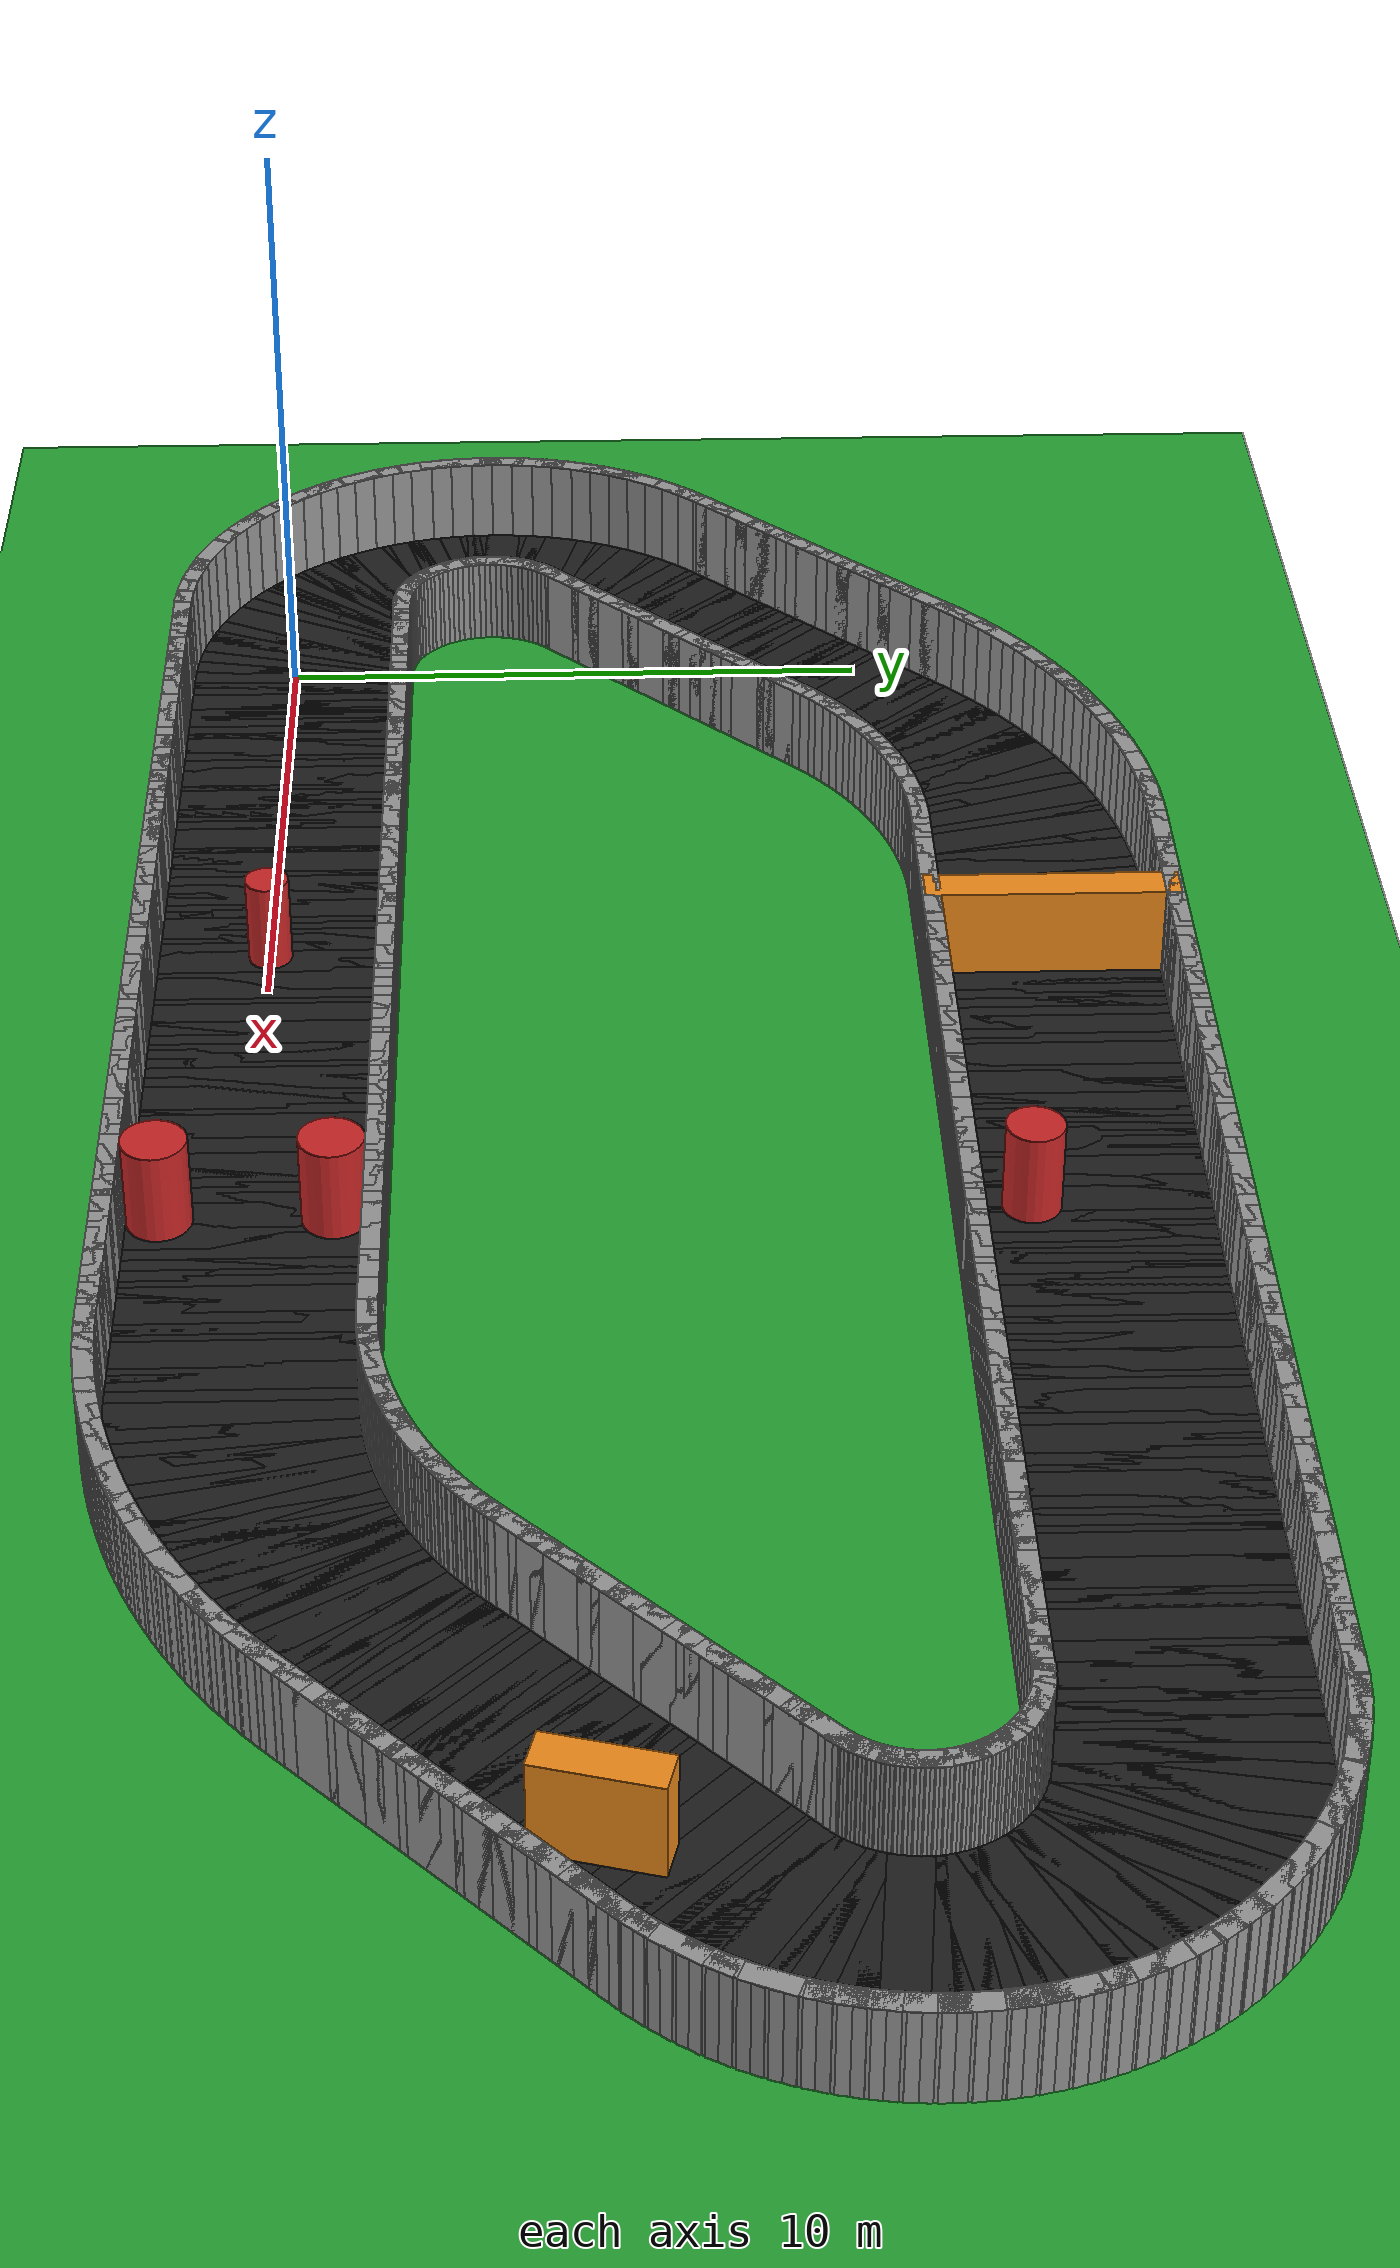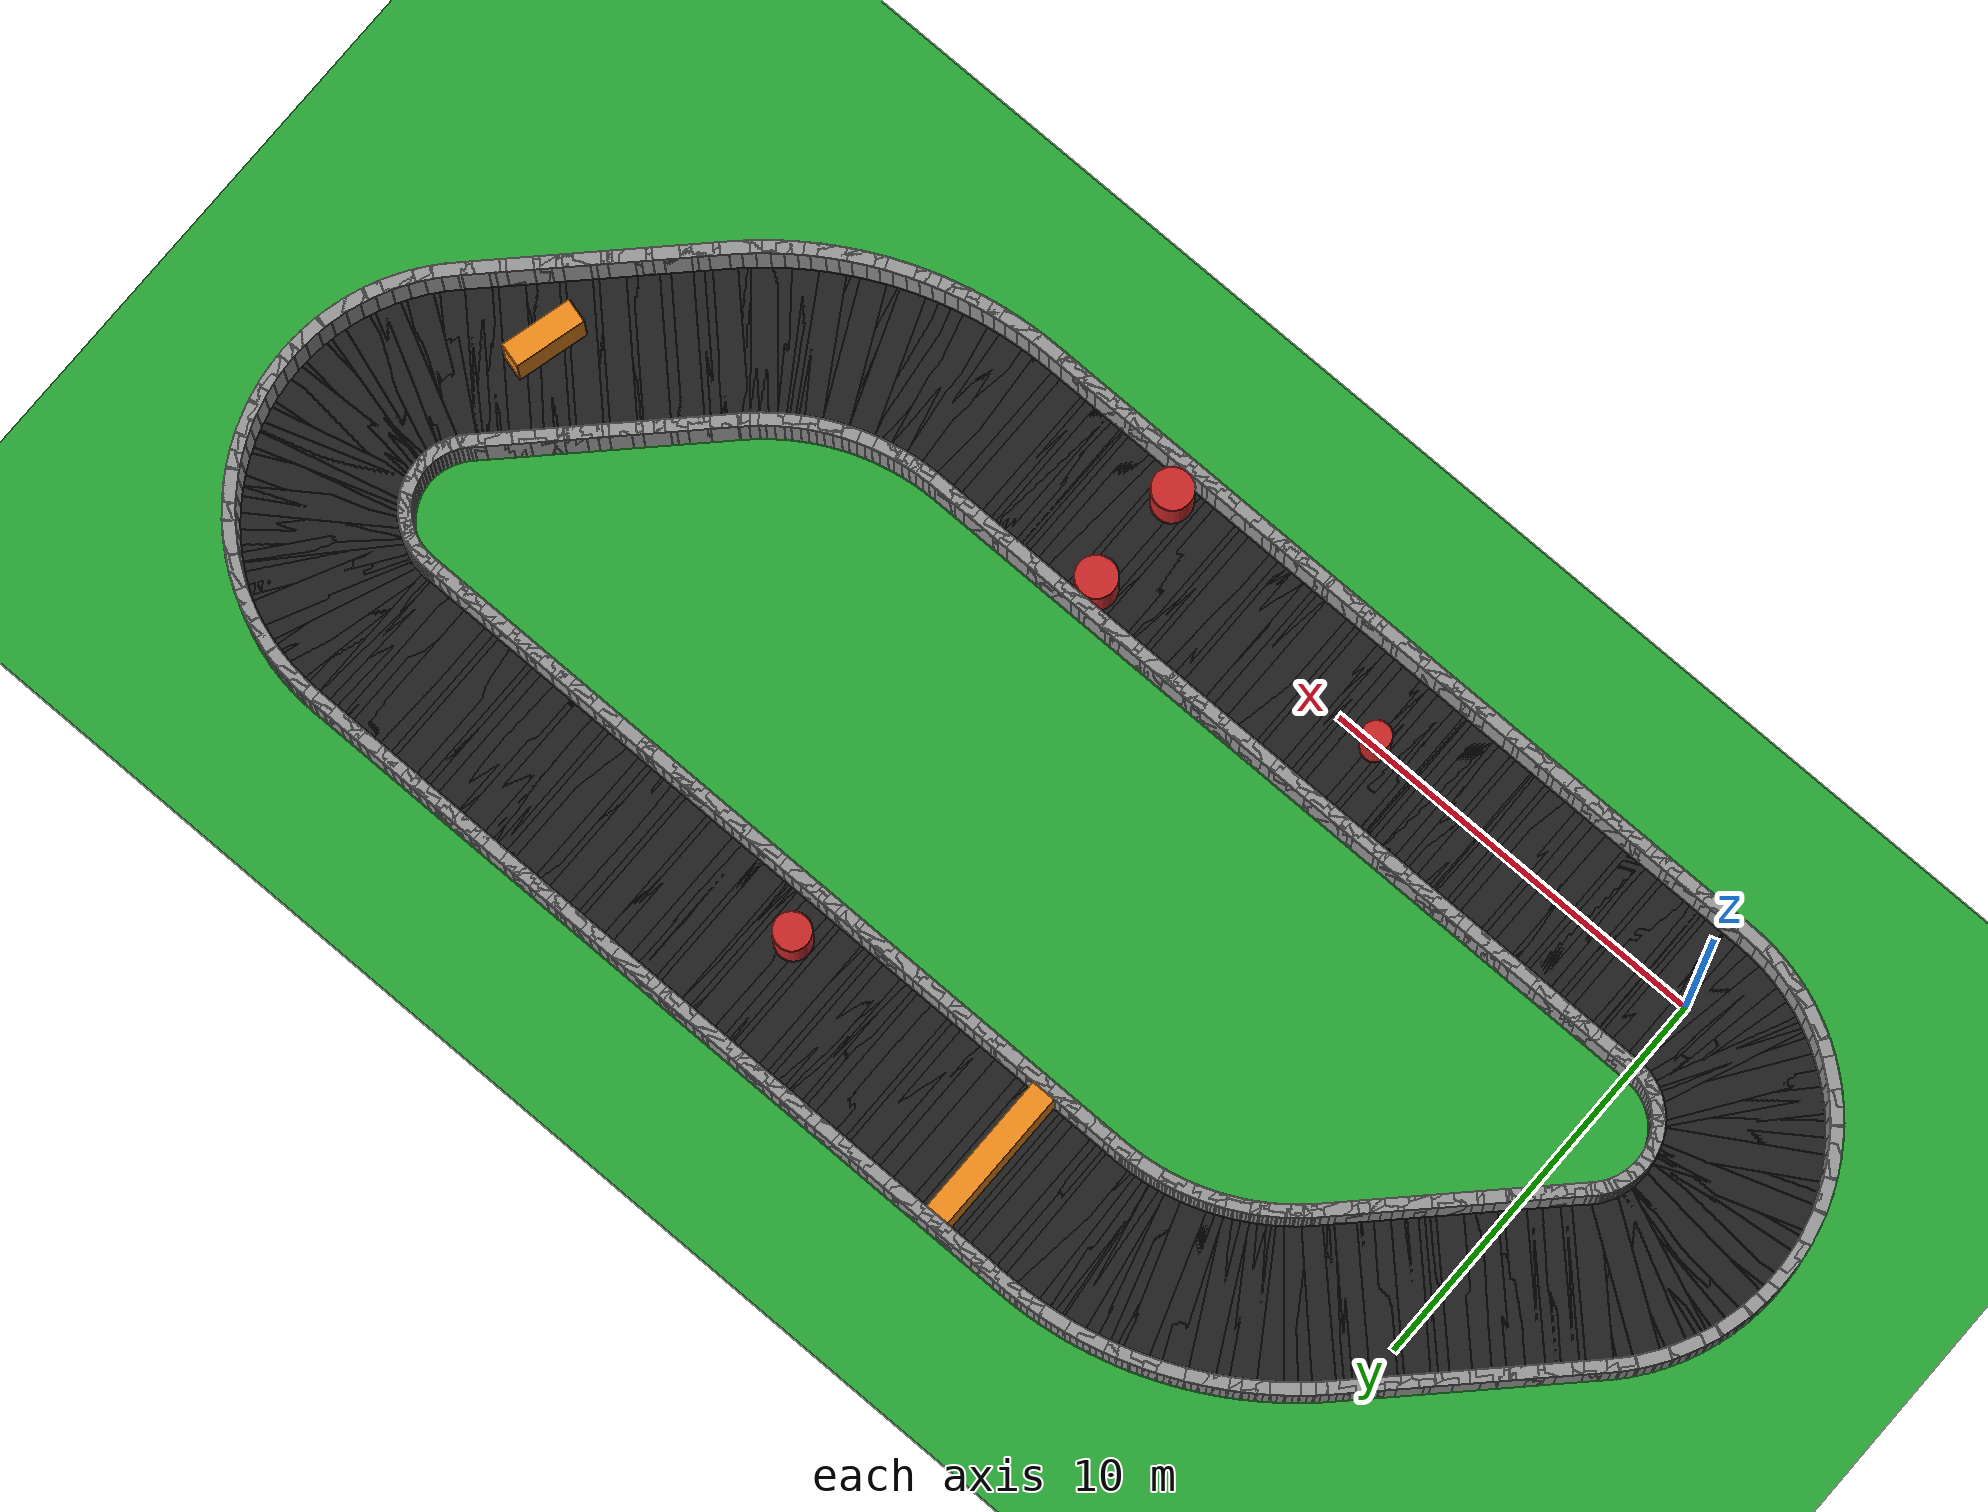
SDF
<?xml version="1.0" ?>
<sdf version="1.6">
  <world name="obstacle_tight">
    <physics type="ode">
      <max_step_size>0.001</max_step_size>
      <real_time_factor>1.0</real_time_factor>
      <real_time_update_rate>1000</real_time_update_rate>
    </physics>
    <include><uri>model://sun</uri></include>

    <model name="ground_plane">
      <static>true</static>
      <link name="link">
        <collision name="collision">
          <surface><friction><ode><mu>100</mu><mu2>50</mu2></ode></friction></surface>
          <geometry><plane><normal>0 0 1</normal>
            <size>120 120</size></plane></geometry>
        </collision>
        <visual name="visual">
          <geometry><plane><normal>0 0 1</normal>
            <size>120 120</size></plane></geometry>
          <material><script>
            <uri>file://media/materials/scripts/gazebo.material</uri>
            <name>Gazebo/Green</name></script></material>
        </visual>
      </link>
    </model>

    <model name="asphalt_0">
      <static>true</static>
      <pose>0.125 0.000 0.005 0 0 0.00000</pose>
      <link name="link">
        <visual name="visual">
          <geometry><box><size>0.610 3.600 0.010</size></box></geometry>
          <material><script><uri>file://media/materials/scripts/gazebo.material</uri><name>Gazebo/Black</name></script></material>
        </visual>
      </link>
    </model>
    <model name="curbL_0">
      <static>true</static>
      <pose>0.125 1.950 0.750 0 0 0.00000</pose>
      <link name="link">
        <collision name="collision">
          <geometry><box><size>0.610 0.300 1.500</size></box></geometry>
        </collision>
        <visual name="visual">
          <geometry><box><size>0.610 0.300 1.500</size></box></geometry>
          <material><script><uri>file://media/materials/scripts/gazebo.material</uri><name>Gazebo/Grey</name></script></material>
        </visual>
      </link>
    </model>
    <model name="curbR_0">
      <static>true</static>
      <pose>0.125 -1.950 0.750 0 0 0.00000</pose>
      <link name="link">
        <collision name="collision">
          <geometry><box><size>0.610 0.300 1.500</size></box></geometry>
        </collision>
        <visual name="visual">
          <geometry><box><size>0.610 0.300 1.500</size></box></geometry>
          <material><script><uri>file://media/materials/scripts/gazebo.material</uri><name>Gazebo/Grey</name></script></material>
        </visual>
      </link>
    </model>
    <model name="asphalt_1">
      <static>true</static>
      <pose>0.375 0.000 0.005 0 0 0.00000</pose>
      <link name="link">
        <visual name="visual">
          <geometry><box><size>0.610 3.600 0.010</size></box></geometry>
          <material><script><uri>file://media/materials/scripts/gazebo.material</uri><name>Gazebo/Black</name></script></material>
        </visual>
      </link>
    </model>
    <model name="curbL_1">
      <static>true</static>
      <pose>0.375 1.950 0.750 0 0 0.00000</pose>
      <link name="link">
        <collision name="collision">
          <geometry><box><size>0.610 0.300 1.500</size></box></geometry>
        </collision>
        <visual name="visual">
          <geometry><box><size>0.610 0.300 1.500</size></box></geometry>
          <material><script><uri>file://media/materials/scripts/gazebo.material</uri><name>Gazebo/Grey</name></script></material>
        </visual>
      </link>
    </model>
    <model name="curbR_1">
      <static>true</static>
      <pose>0.375 -1.950 0.750 0 0 0.00000</pose>
      <link name="link">
        <collision name="collision">
          <geometry><box><size>0.610 0.300 1.500</size></box></geometry>
        </collision>
        <visual name="visual">
          <geometry><box><size>0.610 0.300 1.500</size></box></geometry>
          <material><script><uri>file://media/materials/scripts/gazebo.material</uri><name>Gazebo/Grey</name></script></material>
        </visual>
      </link>
    </model>
    <model name="asphalt_2">
      <static>true</static>
      <pose>0.625 0.000 0.005 0 0 0.00000</pose>
      <link name="link">
        <visual name="visual">
          <geometry><box><size>0.610 3.600 0.010</size></box></geometry>
          <material><script><uri>file://media/materials/scripts/gazebo.material</uri><name>Gazebo/Black</name></script></material>
        </visual>
      </link>
    </model>
    <model name="curbL_2">
      <static>true</static>
      <pose>0.625 1.950 0.750 0 0 0.00000</pose>
      <link name="link">
        <collision name="collision">
          <geometry><box><size>0.610 0.300 1.500</size></box></geometry>
        </collision>
        <visual name="visual">
          <geometry><box><size>0.610 0.300 1.500</size></box></geometry>
          <material><script><uri>file://media/materials/scripts/gazebo.material</uri><name>Gazebo/Grey</name></script></material>
        </visual>
      </link>
    </model>
    <model name="curbR_2">
      <static>true</static>
      <pose>0.625 -1.950 0.750 0 0 0.00000</pose>
      <link name="link">
        <collision name="collision">
          <geometry><box><size>0.610 0.300 1.500</size></box></geometry>
        </collision>
        <visual name="visual">
          <geometry><box><size>0.610 0.300 1.500</size></box></geometry>
          <material><script><uri>file://media/materials/scripts/gazebo.material</uri><name>Gazebo/Grey</name></script></material>
        </visual>
      </link>
    </model>
    <model name="asphalt_3">
      <static>true</static>
      <pose>0.875 0.000 0.005 0 0 0.00000</pose>
      <link name="link">
        <visual name="visual">
          <geometry><box><size>0.610 3.600 0.010</size></box></geometry>
          <material><script><uri>file://media/materials/scripts/gazebo.material</uri><name>Gazebo/Black</name></script></material>
        </visual>
      </link>
    </model>
    <model name="curbL_3">
      <static>true</static>
      <pose>0.875 1.950 0.750 0 0 0.00000</pose>
      <link name="link">
        <collision name="collision">
          <geometry><box><size>0.610 0.300 1.500</size></box></geometry>
        </collision>
        <visual name="visual">
          <geometry><box><size>0.610 0.300 1.500</size></box></geometry>
          <material><script><uri>file://media/materials/scripts/gazebo.material</uri><name>Gazebo/Grey</name></script></material>
        </visual>
      </link>
    </model>
    <model name="curbR_3">
      <static>true</static>
      <pose>0.875 -1.950 0.750 0 0 0.00000</pose>
      <link name="link">
        <collision name="collision">
          <geometry><box><size>0.610 0.300 1.500</size></box></geometry>
        </collision>
        <visual name="visual">
          <geometry><box><size>0.610 0.300 1.500</size></box></geometry>
          <material><script><uri>file://media/materials/scripts/gazebo.material</uri><name>Gazebo/Grey</name></script></material>
        </visual>
      </link>
    </model>
    <model name="asphalt_4">
      <static>true</static>
      <pose>1.125 0.000 0.005 0 0 0.00000</pose>
      <link name="link">
        <visual name="visual">
          <geometry><box><size>0.610 3.600 0.010</size></box></geometry>
          <material><script><uri>file://media/materials/scripts/gazebo.material</uri><name>Gazebo/Black</name></script></material>
        </visual>
      </link>
    </model>
    <model name="curbL_4">
      <static>true</static>
      <pose>1.125 1.950 0.750 0 0 0.00000</pose>
      <link name="link">
        <collision name="collision">
          <geometry><box><size>0.610 0.300 1.500</size></box></geometry>
        </collision>
        <visual name="visual">
          <geometry><box><size>0.610 0.300 1.500</size></box></geometry>
          <material><script><uri>file://media/materials/scripts/gazebo.material</uri><name>Gazebo/Grey</name></script></material>
        </visual>
      </link>
    </model>
    <model name="curbR_4">
      <static>true</static>
      <pose>1.125 -1.950 0.750 0 0 0.00000</pose>
      <link name="link">
        <collision name="collision">
          <geometry><box><size>0.610 0.300 1.500</size></box></geometry>
        </collision>
        <visual name="visual">
          <geometry><box><size>0.610 0.300 1.500</size></box></geometry>
          <material><script><uri>file://media/materials/scripts/gazebo.material</uri><name>Gazebo/Grey</name></script></material>
        </visual>
      </link>
    </model>
    <model name="asphalt_5">
      <static>true</static>
      <pose>1.375 0.000 0.005 0 0 0.00000</pose>
      <link name="link">
        <visual name="visual">
          <geometry><box><size>0.610 3.600 0.010</size></box></geometry>
          <material><script><uri>file://media/materials/scripts/gazebo.material</uri><name>Gazebo/Black</name></script></material>
        </visual>
      </link>
    </model>
    <model name="curbL_5">
      <static>true</static>
      <pose>1.375 1.950 0.750 0 0 0.00000</pose>
      <link name="link">
        <collision name="collision">
          <geometry><box><size>0.610 0.300 1.500</size></box></geometry>
        </collision>
        <visual name="visual">
          <geometry><box><size>0.610 0.300 1.500</size></box></geometry>
          <material><script><uri>file://media/materials/scripts/gazebo.material</uri><name>Gazebo/Grey</name></script></material>
        </visual>
      </link>
    </model>
    <model name="curbR_5">
      <static>true</static>
      <pose>1.375 -1.950 0.750 0 0 0.00000</pose>
      <link name="link">
        <collision name="collision">
          <geometry><box><size>0.610 0.300 1.500</size></box></geometry>
        </collision>
        <visual name="visual">
          <geometry><box><size>0.610 0.300 1.500</size></box></geometry>
          <material><script><uri>file://media/materials/scripts/gazebo.material</uri><name>Gazebo/Grey</name></script></material>
        </visual>
      </link>
    </model>
    <model name="asphalt_6">
      <static>true</static>
      <pose>1.625 0.000 0.005 0 0 0.00000</pose>
      <link name="link">
        <visual name="visual">
          <geometry><box><size>0.610 3.600 0.010</size></box></geometry>
          <material><script><uri>file://media/materials/scripts/gazebo.material</uri><name>Gazebo/Black</name></script></material>
        </visual>
      </link>
    </model>
    <model name="curbL_6">
      <static>true</static>
      <pose>1.625 1.950 0.750 0 0 0.00000</pose>
      <link name="link">
        <collision name="collision">
          <geometry><box><size>0.610 0.300 1.500</size></box></geometry>
        </collision>
        <visual name="visual">
          <geometry><box><size>0.610 0.300 1.500</size></box></geometry>
          <material><script><uri>file://media/materials/scripts/gazebo.material</uri><name>Gazebo/Grey</name></script></material>
        </visual>
      </link>
    </model>
    <model name="curbR_6">
      <static>true</static>
      <pose>1.625 -1.950 0.750 0 0 0.00000</pose>
      <link name="link">
        <collision name="collision">
          <geometry><box><size>0.610 0.300 1.500</size></box></geometry>
        </collision>
        <visual name="visual">
          <geometry><box><size>0.610 0.300 1.500</size></box></geometry>
          <material><script><uri>file://media/materials/scripts/gazebo.material</uri><name>Gazebo/Grey</name></script></material>
        </visual>
      </link>
    </model>
    <model name="asphalt_7">
      <static>true</static>
      <pose>1.875 0.000 0.005 0 0 0.00000</pose>
      <link name="link">
        <visual name="visual">
          <geometry><box><size>0.610 3.600 0.010</size></box></geometry>
          <material><script><uri>file://media/materials/scripts/gazebo.material</uri><name>Gazebo/Black</name></script></material>
        </visual>
      </link>
    </model>
    <model name="curbL_7">
      <static>true</static>
      <pose>1.875 1.950 0.750 0 0 0.00000</pose>
      <link name="link">
        <collision name="collision">
          <geometry><box><size>0.610 0.300 1.500</size></box></geometry>
        </collision>
        <visual name="visual">
          <geometry><box><size>0.610 0.300 1.500</size></box></geometry>
          <material><script><uri>file://media/materials/scripts/gazebo.material</uri><name>Gazebo/Grey</name></script></material>
        </visual>
      </link>
    </model>
    <model name="curbR_7">
      <static>true</static>
      <pose>1.875 -1.950 0.750 0 0 0.00000</pose>
      <link name="link">
        <collision name="collision">
          <geometry><box><size>0.610 0.300 1.500</size></box></geometry>
        </collision>
        <visual name="visual">
          <geometry><box><size>0.610 0.300 1.500</size></box></geometry>
          <material><script><uri>file://media/materials/scripts/gazebo.material</uri><name>Gazebo/Grey</name></script></material>
        </visual>
      </link>
    </model>
    <model name="asphalt_8">
      <static>true</static>
      <pose>2.125 0.000 0.005 0 0 0.00000</pose>
      <link name="link">
        <visual name="visual">
          <geometry><box><size>0.610 3.600 0.010</size></box></geometry>
          <material><script><uri>file://media/materials/scripts/gazebo.material</uri><name>Gazebo/Black</name></script></material>
        </visual>
      </link>
    </model>
    <model name="curbL_8">
      <static>true</static>
      <pose>2.125 1.950 0.750 0 0 0.00000</pose>
      <link name="link">
        <collision name="collision">
          <geometry><box><size>0.610 0.300 1.500</size></box></geometry>
        </collision>
        <visual name="visual">
          <geometry><box><size>0.610 0.300 1.500</size></box></geometry>
          <material><script><uri>file://media/materials/scripts/gazebo.material</uri><name>Gazebo/Grey</name></script></material>
        </visual>
      </link>
    </model>
    <model name="curbR_8">
      <static>true</static>
      <pose>2.125 -1.950 0.750 0 0 0.00000</pose>
      <link name="link">
        <collision name="collision">
          <geometry><box><size>0.610 0.300 1.500</size></box></geometry>
        </collision>
        <visual name="visual">
          <geometry><box><size>0.610 0.300 1.500</size></box></geometry>
          <material><script><uri>file://media/materials/scripts/gazebo.material</uri><name>Gazebo/Grey</name></script></material>
        </visual>
      </link>
    </model>
    <model name="asphalt_9">
      <static>true</static>
      <pose>2.375 0.000 0.005 0 0 0.00000</pose>
      <link name="link">
        <visual name="visual">
          <geometry><box><size>0.610 3.600 0.010</size></box></geometry>
          <material><script><uri>file://media/materials/scripts/gazebo.material</uri><name>Gazebo/Black</name></script></material>
        </visual>
      </link>
    </model>
    <model name="curbL_9">
      <static>true</static>
      <pose>2.375 1.950 0.750 0 0 0.00000</pose>
      <link name="link">
        <collision name="collision">
          <geometry><box><size>0.610 0.300 1.500</size></box></geometry>
        </collision>
        <visual name="visual">
          <geometry><box><size>0.610 0.300 1.500</size></box></geometry>
          <material><script><uri>file://media/materials/scripts/gazebo.material</uri><name>Gazebo/Grey</name></script></material>
        </visual>
      </link>
    </model>
    <model name="curbR_9">
      <static>true</static>
      <pose>2.375 -1.950 0.750 0 0 0.00000</pose>
      <link name="link">
        <collision name="collision">
          <geometry><box><size>0.610 0.300 1.500</size></box></geometry>
        </collision>
        <visual name="visual">
          <geometry><box><size>0.610 0.300 1.500</size></box></geometry>
          <material><script><uri>file://media/materials/scripts/gazebo.material</uri><name>Gazebo/Grey</name></script></material>
        </visual>
      </link>
    </model>
    <model name="asphalt_10">
      <static>true</static>
      <pose>2.625 0.000 0.005 0 0 0.00000</pose>
      <link name="link">
        <visual name="visual">
          <geometry><box><size>0.610 3.600 0.010</size></box></geometry>
          <material><script><uri>file://media/materials/scripts/gazebo.material</uri><name>Gazebo/Black</name></script></material>
        </visual>
      </link>
    </model>
    <model name="curbL_10">
      <static>true</static>
      <pose>2.625 1.950 0.750 0 0 0.00000</pose>
      <link name="link">
        <collision name="collision">
          <geometry><box><size>0.610 0.300 1.500</size></box></geometry>
        </collision>
        <visual name="visual">
          <geometry><box><size>0.610 0.300 1.500</size></box></geometry>
          <material><script><uri>file://media/materials/scripts/gazebo.material</uri><name>Gazebo/Grey</name></script></material>
        </visual>
      </link>
    </model>
    <model name="curbR_10">
      <static>true</static>
      <pose>2.625 -1.950 0.750 0 0 0.00000</pose>
      <link name="link">
        <collision name="collision">
          <geometry><box><size>0.610 0.300 1.500</size></box></geometry>
        </collision>
        <visual name="visual">
          <geometry><box><size>0.610 0.300 1.500</size></box></geometry>
          <material><script><uri>file://media/materials/scripts/gazebo.material</uri><name>Gazebo/Grey</name></script></material>
        </visual>
      </link>
    </model>
    <model name="asphalt_11">
      <static>true</static>
      <pose>2.875 0.000 0.005 0 0 0.00000</pose>
      <link name="link">
        <visual name="visual">
          <geometry><box><size>0.610 3.600 0.010</size></box></geometry>
          <material><script><uri>file://media/materials/scripts/gazebo.material</uri><name>Gazebo/Black</name></script></material>
        </visual>
      </link>
    </model>
    <model name="curbL_11">
      <static>true</static>
      <pose>2.875 1.950 0.750 0 0 0.00000</pose>
      <link name="link">
        <collision name="collision">
          <geometry><box><size>0.610 0.300 1.500</size></box></geometry>
        </collision>
        <visual name="visual">
          <geometry><box><size>0.610 0.300 1.500</size></box></geometry>
          <material><script><uri>file://media/materials/scripts/gazebo.material</uri><name>Gazebo/Grey</name></script></material>
        </visual>
      </link>
    </model>
    <model name="curbR_11">
      <static>true</static>
      <pose>2.875 -1.950 0.750 0 0 0.00000</pose>
      <link name="link">
        <collision name="collision">
          <geometry><box><size>0.610 0.300 1.500</size></box></geometry>
        </collision>
        <visual name="visual">
          <geometry><box><size>0.610 0.300 1.500</size></box></geometry>
          <material><script><uri>file://media/materials/scripts/gazebo.material</uri><name>Gazebo/Grey</name></script></material>
        </visual>
      </link>
    </model>
    <model name="asphalt_12">
      <static>true</static>
      <pose>3.125 0.000 0.005 0 0 0.00000</pose>
      <link name="link">
        <visual name="visual">
          <geometry><box><size>0.610 3.600 0.010</size></box></geometry>
          <material><script><uri>file://media/materials/scripts/gazebo.material</uri><name>Gazebo/Black</name></script></material>
        </visual>
      </link>
    </model>
    <model name="curbL_12">
      <static>true</static>
      <pose>3.125 1.950 0.750 0 0 0.00000</pose>
      <link name="link">
        <collision name="collision">
          <geometry><box><size>0.610 0.300 1.500</size></box></geometry>
        </collision>
        <visual name="visual">
          <geometry><box><size>0.610 0.300 1.500</size></box></geometry>
          <material><script><uri>file://media/materials/scripts/gazebo.material</uri><name>Gazebo/Grey</name></script></material>
        </visual>
      </link>
    </model>
    <model name="curbR_12">
      <static>true</static>
      <pose>3.125 -1.950 0.750 0 0 0.00000</pose>
      <link name="link">
        <collision name="collision">
          <geometry><box><size>0.610 0.300 1.500</size></box></geometry>
        </collision>
        <visual name="visual">
          <geometry><box><size>0.610 0.300 1.500</size></box></geometry>
          <material><script><uri>file://media/materials/scripts/gazebo.material</uri><name>Gazebo/Grey</name></script></material>
        </visual>
      </link>
    </model>
    <model name="asphalt_13">
      <static>true</static>
      <pose>3.375 0.000 0.005 0 0 0.00000</pose>
      <link name="link">
        <visual name="visual">
          <geometry><box><size>0.610 3.600 0.010</size></box></geometry>
          <material><script><uri>file://media/materials/scripts/gazebo.material</uri><name>Gazebo/Black</name></script></material>
        </visual>
      </link>
    </model>
    <model name="curbL_13">
      <static>true</static>
      <pose>3.375 1.950 0.750 0 0 0.00000</pose>
      <link name="link">
        <collision name="collision">
          <geometry><box><size>0.610 0.300 1.500</size></box></geometry>
        </collision>
        <visual name="visual">
          <geometry><box><size>0.610 0.300 1.500</size></box></geometry>
          <material><script><uri>file://media/materials/scripts/gazebo.material</uri><name>Gazebo/Grey</name></script></material>
        </visual>
      </link>
    </model>
    <model name="curbR_13">
      <static>true</static>
      <pose>3.375 -1.950 0.750 0 0 0.00000</pose>
      <link name="link">
        <collision name="collision">
          <geometry><box><size>0.610 0.300 1.500</size></box></geometry>
        </collision>
        <visual name="visual">
          <geometry><box><size>0.610 0.300 1.500</size></box></geometry>
          <material><script><uri>file://media/materials/scripts/gazebo.material</uri><name>Gazebo/Grey</name></script></material>
        </visual>
      </link>
    </model>
    <model name="asphalt_14">
      <static>true</static>
      <pose>3.625 0.000 0.005 0 0 0.00000</pose>
      <link name="link">
        <visual name="visual">
          <geometry><box><size>0.610 3.600 0.010</size></box></geometry>
          <material><script><uri>file://media/materials/scripts/gazebo.material</uri><name>Gazebo/Black</name></script></material>
        </visual>
      </link>
    </model>
    <model name="curbL_14">
      <static>true</static>
      <pose>3.625 1.950 0.750 0 0 0.00000</pose>
      <link name="link">
        <collision name="collision">
          <geometry><box><size>0.610 0.300 1.500</size></box></geometry>
        </collision>
        <visual name="visual">
          <geometry><box><size>0.610 0.300 1.500</size></box></geometry>
          <material><script><uri>file://media/materials/scripts/gazebo.material</uri><name>Gazebo/Grey</name></script></material>
        </visual>
      </link>
    </model>
    <model name="curbR_14">
      <static>true</static>
      <pose>3.625 -1.950 0.750 0 0 0.00000</pose>
      <link name="link">
        <collision name="collision">
          <geometry><box><size>0.610 0.300 1.500</size></box></geometry>
        </collision>
        <visual name="visual">
          <geometry><box><size>0.610 0.300 1.500</size></box></geometry>
          <material><script><uri>file://media/materials/scripts/gazebo.material</uri><name>Gazebo/Grey</name></script></material>
        </visual>
      </link>
    </model>
    <model name="asphalt_15">
      <static>true</static>
      <pose>3.875 0.000 0.005 0 0 0.00000</pose>
      <link name="link">
        <visual name="visual">
          <geometry><box><size>0.610 3.600 0.010</size></box></geometry>
          <material><script><uri>file://media/materials/scripts/gazebo.material</uri><name>Gazebo/Black</name></script></material>
        </visual>
      </link>
    </model>
    <model name="curbL_15">
      <static>true</static>
      <pose>3.875 1.950 0.750 0 0 0.00000</pose>
      <link name="link">
        <collision name="collision">
          <geometry><box><size>0.610 0.300 1.500</size></box></geometry>
        </collision>
        <visual name="visual">
          <geometry><box><size>0.610 0.300 1.500</size></box></geometry>
          <material><script><uri>file://media/materials/scripts/gazebo.material</uri><name>Gazebo/Grey</name></script></material>
        </visual>
      </link>
    </model>
    <model name="curbR_15">
      <static>true</static>
      <pose>3.875 -1.950 0.750 0 0 0.00000</pose>
      <link name="link">
        <collision name="collision">
          <geometry><box><size>0.610 0.300 1.500</size></box></geometry>
        </collision>
        <visual name="visual">
          <geometry><box><size>0.610 0.300 1.500</size></box></geometry>
          <material><script><uri>file://media/materials/scripts/gazebo.material</uri><name>Gazebo/Grey</name></script></material>
        </visual>
      </link>
    </model>
    <model name="asphalt_16">
      <static>true</static>
      <pose>4.125 0.000 0.005 0 0 0.00000</pose>
      <link name="link">
        <visual name="visual">
          <geometry><box><size>0.610 3.600 0.010</size></box></geometry>
          <material><script><uri>file://media/materials/scripts/gazebo.material</uri><name>Gazebo/Black</name></script></material>
        </visual>
      </link>
    </model>
    <model name="curbL_16">
      <static>true</static>
      <pose>4.125 1.950 0.750 0 0 0.00000</pose>
      <link name="link">
        <collision name="collision">
          <geometry><box><size>0.610 0.300 1.500</size></box></geometry>
        </collision>
        <visual name="visual">
          <geometry><box><size>0.610 0.300 1.500</size></box></geometry>
          <material><script><uri>file://media/materials/scripts/gazebo.material</uri><name>Gazebo/Grey</name></script></material>
        </visual>
      </link>
    </model>
    <model name="curbR_16">
      <static>true</static>
      <pose>4.125 -1.950 0.750 0 0 0.00000</pose>
      <link name="link">
        <collision name="collision">
          <geometry><box><size>0.610 0.300 1.500</size></box></geometry>
        </collision>
        <visual name="visual">
          <geometry><box><size>0.610 0.300 1.500</size></box></geometry>
          <material><script><uri>file://media/materials/scripts/gazebo.material</uri><name>Gazebo/Grey</name></script></material>
        </visual>
      </link>
    </model>
    <model name="asphalt_17">
      <static>true</static>
      <pose>4.375 0.000 0.005 0 0 0.00000</pose>
      <link name="link">
        <visual name="visual">
          <geometry><box><size>0.610 3.600 0.010</size></box></geometry>
          <material><script><uri>file://media/materials/scripts/gazebo.material</uri><name>Gazebo/Black</name></script></material>
        </visual>
      </link>
    </model>
    <model name="curbL_17">
      <static>true</static>
      <pose>4.375 1.950 0.750 0 0 0.00000</pose>
      <link name="link">
        <collision name="collision">
          <geometry><box><size>0.610 0.300 1.500</size></box></geometry>
        </collision>
        <visual name="visual">
          <geometry><box><size>0.610 0.300 1.500</size></box></geometry>
          <material><script><uri>file://media/materials/scripts/gazebo.material</uri><name>Gazebo/Grey</name></script></material>
        </visual>
      </link>
    </model>
    <model name="curbR_17">
      <static>true</static>
      <pose>4.375 -1.950 0.750 0 0 0.00000</pose>
      <link name="link">
        <collision name="collision">
          <geometry><box><size>0.610 0.300 1.500</size></box></geometry>
        </collision>
        <visual name="visual">
          <geometry><box><size>0.610 0.300 1.500</size></box></geometry>
          <material><script><uri>file://media/materials/scripts/gazebo.material</uri><name>Gazebo/Grey</name></script></material>
        </visual>
      </link>
    </model>
    <model name="asphalt_18">
      <static>true</static>
      <pose>4.625 0.000 0.005 0 0 0.00000</pose>
      <link name="link">
        <visual name="visual">
          <geometry><box><size>0.610 3.600 0.010</size></box></geometry>
          <material><script><uri>file://media/materials/scripts/gazebo.material</uri><name>Gazebo/Black</name></script></material>
        </visual>
      </link>
    </model>
    <model name="curbL_18">
      <static>true</static>
      <pose>4.625 1.950 0.750 0 0 0.00000</pose>
      <link name="link">
        <collision name="collision">
          <geometry><box><size>0.610 0.300 1.500</size></box></geometry>
        </collision>
        <visual name="visual">
          <geometry><box><size>0.610 0.300 1.500</size></box></geometry>
          <material><script><uri>file://media/materials/scripts/gazebo.material</uri><name>Gazebo/Grey</name></script></material>
        </visual>
      </link>
    </model>
    <model name="curbR_18">
      <static>true</static>
      <pose>4.625 -1.950 0.750 0 0 0.00000</pose>
      <link name="link">
        <collision name="collision">
          <geometry><box><size>0.610 0.300 1.500</size></box></geometry>
        </collision>
        <visual name="visual">
          <geometry><box><size>0.610 0.300 1.500</size></box></geometry>
          <material><script><uri>file://media/materials/scripts/gazebo.material</uri><name>Gazebo/Grey</name></script></material>
        </visual>
      </link>
    </model>
    <model name="asphalt_19">
      <static>true</static>
      <pose>4.875 0.000 0.005 0 0 0.00000</pose>
      <link name="link">
        <visual name="visual">
          <geometry><box><size>0.610 3.600 0.010</size></box></geometry>
          <material><script><uri>file://media/materials/scripts/gazebo.material</uri><name>Gazebo/Black</name></script></material>
        </visual>
      </link>
    </model>
    <model name="curbL_19">
      <static>true</static>
      <pose>4.875 1.950 0.750 0 0 0.00000</pose>
      <link name="link">
        <collision name="collision">
          <geometry><box><size>0.610 0.300 1.500</size></box></geometry>
        </collision>
        <visual name="visual">
          <geometry><box><size>0.610 0.300 1.500</size></box></geometry>
          <material><script><uri>file://media/materials/scripts/gazebo.material</uri><name>Gazebo/Grey</name></script></material>
        </visual>
      </link>
    </model>
    <model name="curbR_19">
      <static>true</static>
      <pose>4.875 -1.950 0.750 0 0 0.00000</pose>
      <link name="link">
        <collision name="collision">
          <geometry><box><size>0.610 0.300 1.500</size></box></geometry>
        </collision>
        <visual name="visual">
          <geometry><box><size>0.610 0.300 1.500</size></box></geometry>
          <material><script><uri>file://media/materials/scripts/gazebo.material</uri><name>Gazebo/Grey</name></script></material>
        </visual>
      </link>
    </model>
    <model name="asphalt_20">
      <static>true</static>
      <pose>5.125 0.000 0.005 0 0 0.00000</pose>
      <link name="link">
        <visual name="visual">
          <geometry><box><size>0.610 3.600 0.010</size></box></geometry>
          <material><script><uri>file://media/materials/scripts/gazebo.material</uri><name>Gazebo/Black</name></script></material>
        </visual>
      </link>
    </model>
    <model name="curbL_20">
      <static>true</static>
      <pose>5.125 1.950 0.750 0 0 0.00000</pose>
      <link name="link">
        <collision name="collision">
          <geometry><box><size>0.610 0.300 1.500</size></box></geometry>
        </collision>
        <visual name="visual">
          <geometry><box><size>0.610 0.300 1.500</size></box></geometry>
          <material><script><uri>file://media/materials/scripts/gazebo.material</uri><name>Gazebo/Grey</name></script></material>
        </visual>
      </link>
    </model>
    <model name="curbR_20">
      <static>true</static>
      <pose>5.125 -1.950 0.750 0 0 0.00000</pose>
      <link name="link">
        <collision name="collision">
          <geometry><box><size>0.610 0.300 1.500</size></box></geometry>
        </collision>
        <visual name="visual">
          <geometry><box><size>0.610 0.300 1.500</size></box></geometry>
          <material><script><uri>file://media/materials/scripts/gazebo.material</uri><name>Gazebo/Grey</name></script></material>
        </visual>
      </link>
    </model>
    <model name="asphalt_21">
      <static>true</static>
      <pose>5.375 0.000 0.005 0 0 0.00000</pose>
      <link name="link">
        <visual name="visual">
          <geometry><box><size>0.610 3.600 0.010</size></box></geometry>
          <material><script><uri>file://media/materials/scripts/gazebo.material</uri><name>Gazebo/Black</name></script></material>
        </visual>
      </link>
    </model>
    <model name="curbL_21">
      <static>true</static>
      <pose>5.375 1.950 0.750 0 0 0.00000</pose>
      <link name="link">
        <collision name="collision">
          <geometry><box><size>0.610 0.300 1.500</size></box></geometry>
        </collision>
        <visual name="visual">
          <geometry><box><size>0.610 0.300 1.500</size></box></geometry>
          <material><script><uri>file://media/materials/scripts/gazebo.material</uri><name>Gazebo/Grey</name></script></material>
        </visual>
      </link>
    </model>
    <model name="curbR_21">
      <static>true</static>
      <pose>5.375 -1.950 0.750 0 0 0.00000</pose>
      <link name="link">
        <collision name="collision">
          <geometry><box><size>0.610 0.300 1.500</size></box></geometry>
        </collision>
        <visual name="visual">
          <geometry><box><size>0.610 0.300 1.500</size></box></geometry>
          <material><script><uri>file://media/materials/scripts/gazebo.material</uri><name>Gazebo/Grey</name></script></material>
        </visual>
      </link>
    </model>
    <model name="asphalt_22">
      <static>true</static>
      <pose>5.625 0.000 0.005 0 0 0.00000</pose>
      <link name="link">
        <visual name="visual">
          <geometry><box><size>0.610 3.600 0.010</size></box></geometry>
          <material><script><uri>file://media/materials/scripts/gazebo.material</uri><name>Gazebo/Black</name></script></material>
        </visual>
      </link>
    </model>
    <model name="curbL_22">
      <static>true</static>
      <pose>5.625 1.950 0.750 0 0 0.00000</pose>
      <link name="link">
        <collision name="collision">
          <geometry><box><size>0.610 0.300 1.500</size></box></geometry>
        </collision>
        <visual name="visual">
          <geometry><box><size>0.610 0.300 1.500</size></box></geometry>
          <material><script><uri>file://media/materials/scripts/gazebo.material</uri><name>Gazebo/Grey</name></script></material>
        </visual>
      </link>
    </model>
    <model name="curbR_22">
      <static>true</static>
      <pose>5.625 -1.950 0.750 0 0 0.00000</pose>
      <link name="link">
        <collision name="collision">
          <geometry><box><size>0.610 0.300 1.500</size></box></geometry>
        </collision>
        <visual name="visual">
          <geometry><box><size>0.610 0.300 1.500</size></box></geometry>
          <material><script><uri>file://media/materials/scripts/gazebo.material</uri><name>Gazebo/Grey</name></script></material>
        </visual>
      </link>
    </model>
    <model name="asphalt_23">
      <static>true</static>
      <pose>5.875 0.000 0.005 0 0 0.00000</pose>
      <link name="link">
        <visual name="visual">
          <geometry><box><size>0.610 3.600 0.010</size></box></geometry>
          <material><script><uri>file://media/materials/scripts/gazebo.material</uri><name>Gazebo/Black</name></script></material>
        </visual>
      </link>
    </model>
    <model name="curbL_23">
      <static>true</static>
      <pose>5.875 1.950 0.750 0 0 0.00000</pose>
      <link name="link">
        <collision name="collision">
          <geometry><box><size>0.610 0.300 1.500</size></box></geometry>
        </collision>
        <visual name="visual">
          <geometry><box><size>0.610 0.300 1.500</size></box></geometry>
          <material><script><uri>file://media/materials/scripts/gazebo.material</uri><name>Gazebo/Grey</name></script></material>
        </visual>
      </link>
    </model>
    <model name="curbR_23">
      <static>true</static>
      <pose>5.875 -1.950 0.750 0 0 0.00000</pose>
      <link name="link">
        <collision name="collision">
          <geometry><box><size>0.610 0.300 1.500</size></box></geometry>
        </collision>
        <visual name="visual">
          <geometry><box><size>0.610 0.300 1.500</size></box></geometry>
          <material><script><uri>file://media/materials/scripts/gazebo.material</uri><name>Gazebo/Grey</name></script></material>
        </visual>
      </link>
    </model>
    <model name="asphalt_24">
      <static>true</static>
      <pose>6.125 0.000 0.005 0 0 0.00000</pose>
      <link name="link">
        <visual name="visual">
          <geometry><box><size>0.610 3.600 0.010</size></box></geometry>
          <material><script><uri>file://media/materials/scripts/gazebo.material</uri><name>Gazebo/Black</name></script></material>
        </visual>
      </link>
    </model>
    <model name="curbL_24">
      <static>true</static>
      <pose>6.125 1.950 0.750 0 0 0.00000</pose>
      <link name="link">
        <collision name="collision">
          <geometry><box><size>0.610 0.300 1.500</size></box></geometry>
        </collision>
        <visual name="visual">
          <geometry><box><size>0.610 0.300 1.500</size></box></geometry>
          <material><script><uri>file://media/materials/scripts/gazebo.material</uri><name>Gazebo/Grey</name></script></material>
        </visual>
      </link>
    </model>
    <model name="curbR_24">
      <static>true</static>
      <pose>6.125 -1.950 0.750 0 0 0.00000</pose>
      <link name="link">
        <collision name="collision">
          <geometry><box><size>0.610 0.300 1.500</size></box></geometry>
        </collision>
        <visual name="visual">
          <geometry><box><size>0.610 0.300 1.500</size></box></geometry>
          <material><script><uri>file://media/materials/scripts/gazebo.material</uri><name>Gazebo/Grey</name></script></material>
        </visual>
      </link>
    </model>
    <model name="asphalt_25">
      <static>true</static>
      <pose>6.375 0.000 0.005 0 0 0.00000</pose>
      <link name="link">
        <visual name="visual">
          <geometry><box><size>0.610 3.600 0.010</size></box></geometry>
          <material><script><uri>file://media/materials/scripts/gazebo.material</uri><name>Gazebo/Black</name></script></material>
        </visual>
      </link>
    </model>
    <model name="curbL_25">
      <static>true</static>
      <pose>6.375 1.950 0.750 0 0 0.00000</pose>
      <link name="link">
        <collision name="collision">
          <geometry><box><size>0.610 0.300 1.500</size></box></geometry>
        </collision>
        <visual name="visual">
          <geometry><box><size>0.610 0.300 1.500</size></box></geometry>
          <material><script><uri>file://media/materials/scripts/gazebo.material</uri><name>Gazebo/Grey</name></script></material>
        </visual>
      </link>
    </model>
    <model name="curbR_25">
      <static>true</static>
      <pose>6.375 -1.950 0.750 0 0 0.00000</pose>
      <link name="link">
        <collision name="collision">
          <geometry><box><size>0.610 0.300 1.500</size></box></geometry>
        </collision>
        <visual name="visual">
          <geometry><box><size>0.610 0.300 1.500</size></box></geometry>
          <material><script><uri>file://media/materials/scripts/gazebo.material</uri><name>Gazebo/Grey</name></script></material>
        </visual>
      </link>
    </model>
    <model name="asphalt_26">
      <static>true</static>
      <pose>6.625 0.000 0.005 0 0 0.00000</pose>
      <link name="link">
        <visual name="visual">
          <geometry><box><size>0.610 3.600 0.010</size></box></geometry>
          <material><script><uri>file://media/materials/scripts/gazebo.material</uri><name>Gazebo/Black</name></script></material>
        </visual>
      </link>
    </model>
    <model name="curbL_26">
      <static>true</static>
      <pose>6.625 1.950 0.750 0 0 0.00000</pose>
      <link name="link">
        <collision name="collision">
          <geometry><box><size>0.610 0.300 1.500</size></box></geometry>
        </collision>
        <visual name="visual">
          <geometry><box><size>0.610 0.300 1.500</size></box></geometry>
          <material><script><uri>file://media/materials/scripts/gazebo.material</uri><name>Gazebo/Grey</name></script></material>
        </visual>
      </link>
    </model>
    <model name="curbR_26">
      <static>true</static>
      <pose>6.625 -1.950 0.750 0 0 0.00000</pose>
      <link name="link">
        <collision name="collision">
          <geometry><box><size>0.610 0.300 1.500</size></box></geometry>
        </collision>
        <visual name="visual">
          <geometry><box><size>0.610 0.300 1.500</size></box></geometry>
          <material><script><uri>file://media/materials/scripts/gazebo.material</uri><name>Gazebo/Grey</name></script></material>
        </visual>
      </link>
    </model>
    <model name="asphalt_27">
      <static>true</static>
      <pose>6.875 0.000 0.005 0 0 0.00000</pose>
      <link name="link">
        <visual name="visual">
          <geometry><box><size>0.610 3.600 0.010</size></box></geometry>
          <material><script><uri>file://media/materials/scripts/gazebo.material</uri><name>Gazebo/Black</name></script></material>
        </visual>
      </link>
    </model>
    <model name="curbL_27">
      <static>true</static>
      <pose>6.875 1.950 0.750 0 0 0.00000</pose>
      <link name="link">
        <collision name="collision">
          <geometry><box><size>0.610 0.300 1.500</size></box></geometry>
        </collision>
        <visual name="visual">
          <geometry><box><size>0.610 0.300 1.500</size></box></geometry>
          <material><script><uri>file://media/materials/scripts/gazebo.material</uri><name>Gazebo/Grey</name></script></material>
        </visual>
      </link>
    </model>
    <model name="curbR_27">
      <static>true</static>
      <pose>6.875 -1.950 0.750 0 0 0.00000</pose>
      <link name="link">
        <collision name="collision">
          <geometry><box><size>0.610 0.300 1.500</size></box></geometry>
        </collision>
        <visual name="visual">
          <geometry><box><size>0.610 0.300 1.500</size></box></geometry>
          <material><script><uri>file://media/materials/scripts/gazebo.material</uri><name>Gazebo/Grey</name></script></material>
        </visual>
      </link>
    </model>
    <model name="asphalt_28">
      <static>true</static>
      <pose>7.125 0.000 0.005 0 0 0.00000</pose>
      <link name="link">
        <visual name="visual">
          <geometry><box><size>0.610 3.600 0.010</size></box></geometry>
          <material><script><uri>file://media/materials/scripts/gazebo.material</uri><name>Gazebo/Black</name></script></material>
        </visual>
      </link>
    </model>
    <model name="curbL_28">
      <static>true</static>
      <pose>7.125 1.950 0.750 0 0 0.00000</pose>
      <link name="link">
        <collision name="collision">
          <geometry><box><size>0.610 0.300 1.500</size></box></geometry>
        </collision>
        <visual name="visual">
          <geometry><box><size>0.610 0.300 1.500</size></box></geometry>
          <material><script><uri>file://media/materials/scripts/gazebo.material</uri><name>Gazebo/Grey</name></script></material>
        </visual>
      </link>
    </model>
    <model name="curbR_28">
      <static>true</static>
      <pose>7.125 -1.950 0.750 0 0 0.00000</pose>
      <link name="link">
        <collision name="collision">
          <geometry><box><size>0.610 0.300 1.500</size></box></geometry>
        </collision>
        <visual name="visual">
          <geometry><box><size>0.610 0.300 1.500</size></box></geometry>
          <material><script><uri>file://media/materials/scripts/gazebo.material</uri><name>Gazebo/Grey</name></script></material>
        </visual>
      </link>
    </model>
    <model name="asphalt_29">
      <static>true</static>
      <pose>7.375 0.000 0.005 0 0 0.00000</pose>
      <link name="link">
        <visual name="visual">
          <geometry><box><size>0.610 3.600 0.010</size></box></geometry>
          <material><script><uri>file://media/materials/scripts/gazebo.material</uri><name>Gazebo/Black</name></script></material>
        </visual>
      </link>
    </model>
    <model name="curbL_29">
      <static>true</static>
      <pose>7.375 1.950 0.750 0 0 0.00000</pose>
      <link name="link">
        <collision name="collision">
          <geometry><box><size>0.610 0.300 1.500</size></box></geometry>
        </collision>
        <visual name="visual">
          <geometry><box><size>0.610 0.300 1.500</size></box></geometry>
          <material><script><uri>file://media/materials/scripts/gazebo.material</uri><name>Gazebo/Grey</name></script></material>
        </visual>
      </link>
    </model>
    <model name="curbR_29">
      <static>true</static>
      <pose>7.375 -1.950 0.750 0 0 0.00000</pose>
      <link name="link">
        <collision name="collision">
          <geometry><box><size>0.610 0.300 1.500</size></box></geometry>
        </collision>
        <visual name="visual">
          <geometry><box><size>0.610 0.300 1.500</size></box></geometry>
          <material><script><uri>file://media/materials/scripts/gazebo.material</uri><name>Gazebo/Grey</name></script></material>
        </visual>
      </link>
    </model>
    <model name="asphalt_30">
      <static>true</static>
      <pose>7.625 0.000 0.005 0 0 0.00000</pose>
      <link name="link">
        <visual name="visual">
          <geometry><box><size>0.610 3.600 0.010</size></box></geometry>
          <material><script><uri>file://media/materials/scripts/gazebo.material</uri><name>Gazebo/Black</name></script></material>
        </visual>
      </link>
    </model>
    <model name="curbL_30">
      <static>true</static>
      <pose>7.625 1.950 0.750 0 0 0.00000</pose>
      <link name="link">
        <collision name="collision">
          <geometry><box><size>0.610 0.300 1.500</size></box></geometry>
        </collision>
        <visual name="visual">
          <geometry><box><size>0.610 0.300 1.500</size></box></geometry>
          <material><script><uri>file://media/materials/scripts/gazebo.material</uri><name>Gazebo/Grey</name></script></material>
        </visual>
      </link>
    </model>
    <model name="curbR_30">
      <static>true</static>
      <pose>7.625 -1.950 0.750 0 0 0.00000</pose>
      <link name="link">
        <collision name="collision">
          <geometry><box><size>0.610 0.300 1.500</size></box></geometry>
        </collision>
        <visual name="visual">
          <geometry><box><size>0.610 0.300 1.500</size></box></geometry>
          <material><script><uri>file://media/materials/scripts/gazebo.material</uri><name>Gazebo/Grey</name></script></material>
        </visual>
      </link>
    </model>
    <model name="asphalt_31">
      <static>true</static>
      <pose>7.875 0.000 0.005 0 0 0.00000</pose>
      <link name="link">
        <visual name="visual">
          <geometry><box><size>0.610 3.600 0.010</size></box></geometry>
          <material><script><uri>file://media/materials/scripts/gazebo.material</uri><name>Gazebo/Black</name></script></material>
        </visual>
      </link>
    </model>
    <model name="curbL_31">
      <static>true</static>
      <pose>7.875 1.950 0.750 0 0 0.00000</pose>
      <link name="link">
        <collision name="collision">
          <geometry><box><size>0.610 0.300 1.500</size></box></geometry>
        </collision>
        <visual name="visual">
          <geometry><box><size>0.610 0.300 1.500</size></box></geometry>
          <material><script><uri>file://media/materials/scripts/gazebo.material</uri><name>Gazebo/Grey</name></script></material>
        </visual>
      </link>
    </model>
    <model name="curbR_31">
      <static>true</static>
      <pose>7.875 -1.950 0.750 0 0 0.00000</pose>
      <link name="link">
        <collision name="collision">
          <geometry><box><size>0.610 0.300 1.500</size></box></geometry>
        </collision>
        <visual name="visual">
          <geometry><box><size>0.610 0.300 1.500</size></box></geometry>
          <material><script><uri>file://media/materials/scripts/gazebo.material</uri><name>Gazebo/Grey</name></script></material>
        </visual>
      </link>
    </model>
    <model name="asphalt_32">
      <static>true</static>
      <pose>8.125 0.000 0.005 0 0 0.00000</pose>
      <link name="link">
        <visual name="visual">
          <geometry><box><size>0.610 3.600 0.010</size></box></geometry>
          <material><script><uri>file://media/materials/scripts/gazebo.material</uri><name>Gazebo/Black</name></script></material>
        </visual>
      </link>
    </model>
    <model name="curbL_32">
      <static>true</static>
      <pose>8.125 1.950 0.750 0 0 0.00000</pose>
      <link name="link">
        <collision name="collision">
          <geometry><box><size>0.610 0.300 1.500</size></box></geometry>
        </collision>
        <visual name="visual">
          <geometry><box><size>0.610 0.300 1.500</size></box></geometry>
          <material><script><uri>file://media/materials/scripts/gazebo.material</uri><name>Gazebo/Grey</name></script></material>
        </visual>
      </link>
    </model>
    <model name="curbR_32">
      <static>true</static>
      <pose>8.125 -1.950 0.750 0 0 0.00000</pose>
      <link name="link">
        <collision name="collision">
          <geometry><box><size>0.610 0.300 1.500</size></box></geometry>
        </collision>
        <visual name="visual">
          <geometry><box><size>0.610 0.300 1.500</size></box></geometry>
          <material><script><uri>file://media/materials/scripts/gazebo.material</uri><name>Gazebo/Grey</name></script></material>
        </visual>
      </link>
    </model>
    <model name="asphalt_33">
      <static>true</static>
      <pose>8.375 0.000 0.005 0 0 0.00000</pose>
      <link name="link">
        <visual name="visual">
          <geometry><box><size>0.610 3.600 0.010</size></box></geometry>
          <material><script><uri>file://media/materials/scripts/gazebo.material</uri><name>Gazebo/Black</name></script></material>
        </visual>
      </link>
    </model>
    <model name="curbL_33">
      <static>true</static>
      <pose>8.375 1.950 0.750 0 0 0.00000</pose>
      <link name="link">
        <collision name="collision">
          <geometry><box><size>0.610 0.300 1.500</size></box></geometry>
        </collision>
        <visual name="visual">
          <geometry><box><size>0.610 0.300 1.500</size></box></geometry>
          <material><script><uri>file://media/materials/scripts/gazebo.material</uri><name>Gazebo/Grey</name></script></material>
        </visual>
      </link>
    </model>
    <model name="curbR_33">
      <static>true</static>
      <pose>8.375 -1.950 0.750 0 0 0.00000</pose>
      <link name="link">
        <collision name="collision">
          <geometry><box><size>0.610 0.300 1.500</size></box></geometry>
        </collision>
        <visual name="visual">
          <geometry><box><size>0.610 0.300 1.500</size></box></geometry>
          <material><script><uri>file://media/materials/scripts/gazebo.material</uri><name>Gazebo/Grey</name></script></material>
        </visual>
      </link>
    </model>
    <model name="asphalt_34">
      <static>true</static>
      <pose>8.625 0.000 0.005 0 0 0.00000</pose>
      <link name="link">
        <visual name="visual">
          <geometry><box><size>0.610 3.600 0.010</size></box></geometry>
          <material><script><uri>file://media/materials/scripts/gazebo.material</uri><name>Gazebo/Black</name></script></material>
        </visual>
      </link>
    </model>
    <model name="curbL_34">
      <static>true</static>
      <pose>8.625 1.950 0.750 0 0 0.00000</pose>
      <link name="link">
        <collision name="collision">
          <geometry><box><size>0.610 0.300 1.500</size></box></geometry>
        </collision>
        <visual name="visual">
          <geometry><box><size>0.610 0.300 1.500</size></box></geometry>
          <material><script><uri>file://media/materials/scripts/gazebo.material</uri><name>Gazebo/Grey</name></script></material>
        </visual>
      </link>
    </model>
    <model name="curbR_34">
      <static>true</static>
      <pose>8.625 -1.950 0.750 0 0 0.00000</pose>
      <link name="link">
        <collision name="collision">
          <geometry><box><size>0.610 0.300 1.500</size></box></geometry>
        </collision>
        <visual name="visual">
          <geometry><box><size>0.610 0.300 1.500</size></box></geometry>
          <material><script><uri>file://media/materials/scripts/gazebo.material</uri><name>Gazebo/Grey</name></script></material>
        </visual>
      </link>
    </model>
    <model name="asphalt_35">
      <static>true</static>
      <pose>8.875 0.000 0.005 0 0 0.00000</pose>
      <link name="link">
        <visual name="visual">
          <geometry><box><size>0.610 3.600 0.010</size></box></geometry>
          <material><script><uri>file://media/materials/scripts/gazebo.material</uri><name>Gazebo/Black</name></script></material>
        </visual>
      </link>
    </model>
    <model name="curbL_35">
      <static>true</static>
      <pose>8.875 1.950 0.750 0 0 0.00000</pose>
      <link name="link">
        <collision name="collision">
          <geometry><box><size>0.610 0.300 1.500</size></box></geometry>
        </collision>
        <visual name="visual">
          <geometry><box><size>0.610 0.300 1.500</size></box></geometry>
          <material><script><uri>file://media/materials/scripts/gazebo.material</uri><name>Gazebo/Grey</name></script></material>
        </visual>
      </link>
    </model>
    <model name="curbR_35">
      <static>true</static>
      <pose>8.875 -1.950 0.750 0 0 0.00000</pose>
      <link name="link">
        <collision name="collision">
          <geometry><box><size>0.610 0.300 1.500</size></box></geometry>
        </collision>
        <visual name="visual">
          <geometry><box><size>0.610 0.300 1.500</size></box></geometry>
          <material><script><uri>file://media/materials/scripts/gazebo.material</uri><name>Gazebo/Grey</name></script></material>
        </visual>
      </link>
    </model>
    <model name="asphalt_36">
      <static>true</static>
      <pose>9.125 0.000 0.005 0 0 0.00000</pose>
      <link name="link">
        <visual name="visual">
          <geometry><box><size>0.610 3.600 0.010</size></box></geometry>
          <material><script><uri>file://media/materials/scripts/gazebo.material</uri><name>Gazebo/Black</name></script></material>
        </visual>
      </link>
    </model>
    <model name="curbL_36">
      <static>true</static>
      <pose>9.125 1.950 0.750 0 0 0.00000</pose>
      <link name="link">
        <collision name="collision">
          <geometry><box><size>0.610 0.300 1.500</size></box></geometry>
        </collision>
        <visual name="visual">
          <geometry><box><size>0.610 0.300 1.500</size></box></geometry>
          <material><script><uri>file://media/materials/scripts/gazebo.material</uri><name>Gazebo/Grey</name></script></material>
        </visual>
      </link>
    </model>
    <model name="curbR_36">
      <static>true</static>
      <pose>9.125 -1.950 0.750 0 0 0.00000</pose>
      <link name="link">
        <collision name="collision">
          <geometry><box><size>0.610 0.300 1.500</size></box></geometry>
        </collision>
        <visual name="visual">
          <geometry><box><size>0.610 0.300 1.500</size></box></geometry>
          <material><script><uri>file://media/materials/scripts/gazebo.material</uri><name>Gazebo/Grey</name></script></material>
        </visual>
      </link>
    </model>
    <model name="asphalt_37">
      <static>true</static>
      <pose>9.375 0.000 0.005 0 0 0.00000</pose>
      <link name="link">
        <visual name="visual">
          <geometry><box><size>0.610 3.600 0.010</size></box></geometry>
          <material><script><uri>file://media/materials/scripts/gazebo.material</uri><name>Gazebo/Black</name></script></material>
        </visual>
      </link>
    </model>
    <model name="curbL_37">
      <static>true</static>
      <pose>9.375 1.950 0.750 0 0 0.00000</pose>
      <link name="link">
        <collision name="collision">
          <geometry><box><size>0.610 0.300 1.500</size></box></geometry>
        </collision>
        <visual name="visual">
          <geometry><box><size>0.610 0.300 1.500</size></box></geometry>
          <material><script><uri>file://media/materials/scripts/gazebo.material</uri><name>Gazebo/Grey</name></script></material>
        </visual>
      </link>
    </model>
    <model name="curbR_37">
      <static>true</static>
      <pose>9.375 -1.950 0.750 0 0 0.00000</pose>
      <link name="link">
        <collision name="collision">
          <geometry><box><size>0.610 0.300 1.500</size></box></geometry>
        </collision>
        <visual name="visual">
          <geometry><box><size>0.610 0.300 1.500</size></box></geometry>
          <material><script><uri>file://media/materials/scripts/gazebo.material</uri><name>Gazebo/Grey</name></script></material>
        </visual>
      </link>
    </model>
    <model name="asphalt_38">
      <static>true</static>
      <pose>9.625 0.000 0.005 0 0 0.00000</pose>
      <link name="link">
        <visual name="visual">
          <geometry><box><size>0.610 3.600 0.010</size></box></geometry>
          <material><script><uri>file://media/materials/scripts/gazebo.material</uri><name>Gazebo/Black</name></script></material>
        </visual>
      </link>
    </model>
    <model name="curbL_38">
      <static>true</static>
      <pose>9.625 1.950 0.750 0 0 0.00000</pose>
      <link name="link">
        <collision name="collision">
          <geometry><box><size>0.610 0.300 1.500</size></box></geometry>
        </collision>
        <visual name="visual">
          <geometry><box><size>0.610 0.300 1.500</size></box></geometry>
          <material><script><uri>file://media/materials/scripts/gazebo.material</uri><name>Gazebo/Grey</name></script></material>
        </visual>
      </link>
    </model>
    <model name="curbR_38">
      <static>true</static>
      <pose>9.625 -1.950 0.750 0 0 0.00000</pose>
      <link name="link">
        <collision name="collision">
          <geometry><box><size>0.610 0.300 1.500</size></box></geometry>
        </collision>
        <visual name="visual">
          <geometry><box><size>0.610 0.300 1.500</size></box></geometry>
          <material><script><uri>file://media/materials/scripts/gazebo.material</uri><name>Gazebo/Grey</name></script></material>
        </visual>
      </link>
    </model>
    <model name="asphalt_39">
      <static>true</static>
      <pose>9.875 0.000 0.005 0 0 0.00000</pose>
      <link name="link">
        <visual name="visual">
          <geometry><box><size>0.610 3.600 0.010</size></box></geometry>
          <material><script><uri>file://media/materials/scripts/gazebo.material</uri><name>Gazebo/Black</name></script></material>
        </visual>
      </link>
    </model>
    <model name="curbL_39">
      <static>true</static>
      <pose>9.875 1.950 0.750 0 0 0.00000</pose>
      <link name="link">
        <collision name="collision">
          <geometry><box><size>0.610 0.300 1.500</size></box></geometry>
        </collision>
        <visual name="visual">
          <geometry><box><size>0.610 0.300 1.500</size></box></geometry>
          <material><script><uri>file://media/materials/scripts/gazebo.material</uri><name>Gazebo/Grey</name></script></material>
        </visual>
      </link>
    </model>
    <model name="curbR_39">
      <static>true</static>
      <pose>9.875 -1.950 0.750 0 0 0.00000</pose>
      <link name="link">
        <collision name="collision">
          <geometry><box><size>0.610 0.300 1.500</size></box></geometry>
        </collision>
        <visual name="visual">
          <geometry><box><size>0.610 0.300 1.500</size></box></geometry>
          <material><script><uri>file://media/materials/scripts/gazebo.material</uri><name>Gazebo/Grey</name></script></material>
        </visual>
      </link>
    </model>
    <model name="asphalt_40">
      <static>true</static>
      <pose>10.125 0.000 0.005 0 0 0.00000</pose>
      <link name="link">
        <visual name="visual">
          <geometry><box><size>0.610 3.600 0.010</size></box></geometry>
          <material><script><uri>file://media/materials/scripts/gazebo.material</uri><name>Gazebo/Black</name></script></material>
        </visual>
      </link>
    </model>
    <model name="curbL_40">
      <static>true</static>
      <pose>10.125 1.950 0.750 0 0 0.00000</pose>
      <link name="link">
        <collision name="collision">
          <geometry><box><size>0.610 0.300 1.500</size></box></geometry>
        </collision>
        <visual name="visual">
          <geometry><box><size>0.610 0.300 1.500</size></box></geometry>
          <material><script><uri>file://media/materials/scripts/gazebo.material</uri><name>Gazebo/Grey</name></script></material>
        </visual>
      </link>
    </model>
    <model name="curbR_40">
      <static>true</static>
      <pose>10.125 -1.950 0.750 0 0 0.00000</pose>
      <link name="link">
        <collision name="collision">
          <geometry><box><size>0.610 0.300 1.500</size></box></geometry>
        </collision>
        <visual name="visual">
          <geometry><box><size>0.610 0.300 1.500</size></box></geometry>
          <material><script><uri>file://media/materials/scripts/gazebo.material</uri><name>Gazebo/Grey</name></script></material>
        </visual>
      </link>
    </model>
    <model name="asphalt_41">
      <static>true</static>
      <pose>10.375 0.000 0.005 0 0 0.00000</pose>
      <link name="link">
        <visual name="visual">
          <geometry><box><size>0.610 3.600 0.010</size></box></geometry>
          <material><script><uri>file://media/materials/scripts/gazebo.material</uri><name>Gazebo/Black</name></script></material>
        </visual>
      </link>
    </model>
    <model name="curbL_41">
      <static>true</static>
      <pose>10.375 1.950 0.750 0 0 0.00000</pose>
      <link name="link">
        <collision name="collision">
          <geometry><box><size>0.610 0.300 1.500</size></box></geometry>
        </collision>
        <visual name="visual">
          <geometry><box><size>0.610 0.300 1.500</size></box></geometry>
          <material><script><uri>file://media/materials/scripts/gazebo.material</uri><name>Gazebo/Grey</name></script></material>
        </visual>
      </link>
    </model>
    <model name="curbR_41">
      <static>true</static>
      <pose>10.375 -1.950 0.750 0 0 0.00000</pose>
      <link name="link">
        <collision name="collision">
          <geometry><box><size>0.610 0.300 1.500</size></box></geometry>
        </collision>
        <visual name="visual">
          <geometry><box><size>0.610 0.300 1.500</size></box></geometry>
          <material><script><uri>file://media/materials/scripts/gazebo.material</uri><name>Gazebo/Grey</name></script></material>
        </visual>
      </link>
    </model>
    <model name="asphalt_42">
      <static>true</static>
      <pose>10.625 0.000 0.005 0 0 0.00000</pose>
      <link name="link">
        <visual name="visual">
          <geometry><box><size>0.610 3.600 0.010</size></box></geometry>
          <material><script><uri>file://media/materials/scripts/gazebo.material</uri><name>Gazebo/Black</name></script></material>
        </visual>
      </link>
    </model>
    <model name="curbL_42">
      <static>true</static>
      <pose>10.625 1.950 0.750 0 0 0.00000</pose>
      <link name="link">
        <collision name="collision">
          <geometry><box><size>0.610 0.300 1.500</size></box></geometry>
        </collision>
        <visual name="visual">
          <geometry><box><size>0.610 0.300 1.500</size></box></geometry>
          <material><script><uri>file://media/materials/scripts/gazebo.material</uri><name>Gazebo/Grey</name></script></material>
        </visual>
      </link>
    </model>
    <model name="curbR_42">
      <static>true</static>
      <pose>10.625 -1.950 0.750 0 0 0.00000</pose>
      <link name="link">
        <collision name="collision">
          <geometry><box><size>0.610 0.300 1.500</size></box></geometry>
        </collision>
        <visual name="visual">
          <geometry><box><size>0.610 0.300 1.500</size></box></geometry>
          <material><script><uri>file://media/materials/scripts/gazebo.material</uri><name>Gazebo/Grey</name></script></material>
        </visual>
      </link>
    </model>
    <model name="asphalt_43">
      <static>true</static>
      <pose>10.875 0.000 0.005 0 0 0.00000</pose>
      <link name="link">
        <visual name="visual">
          <geometry><box><size>0.610 3.600 0.010</size></box></geometry>
          <material><script><uri>file://media/materials/scripts/gazebo.material</uri><name>Gazebo/Black</name></script></material>
        </visual>
      </link>
    </model>
    <model name="curbL_43">
      <static>true</static>
      <pose>10.875 1.950 0.750 0 0 0.00000</pose>
      <link name="link">
        <collision name="collision">
          <geometry><box><size>0.610 0.300 1.500</size></box></geometry>
        </collision>
        <visual name="visual">
          <geometry><box><size>0.610 0.300 1.500</size></box></geometry>
          <material><script><uri>file://media/materials/scripts/gazebo.material</uri><name>Gazebo/Grey</name></script></material>
        </visual>
      </link>
    </model>
    <model name="curbR_43">
      <static>true</static>
      <pose>10.875 -1.950 0.750 0 0 0.00000</pose>
      <link name="link">
        <collision name="collision">
          <geometry><box><size>0.610 0.300 1.500</size></box></geometry>
        </collision>
        <visual name="visual">
          <geometry><box><size>0.610 0.300 1.500</size></box></geometry>
          <material><script><uri>file://media/materials/scripts/gazebo.material</uri><name>Gazebo/Grey</name></script></material>
        </visual>
      </link>
    </model>
    <model name="asphalt_44">
      <static>true</static>
      <pose>11.125 0.000 0.005 0 0 0.00000</pose>
      <link name="link">
        <visual name="visual">
          <geometry><box><size>0.610 3.600 0.010</size></box></geometry>
          <material><script><uri>file://media/materials/scripts/gazebo.material</uri><name>Gazebo/Black</name></script></material>
        </visual>
      </link>
    </model>
    <model name="curbL_44">
      <static>true</static>
      <pose>11.125 1.950 0.750 0 0 0.00000</pose>
      <link name="link">
        <collision name="collision">
          <geometry><box><size>0.610 0.300 1.500</size></box></geometry>
        </collision>
        <visual name="visual">
          <geometry><box><size>0.610 0.300 1.500</size></box></geometry>
          <material><script><uri>file://media/materials/scripts/gazebo.material</uri><name>Gazebo/Grey</name></script></material>
        </visual>
      </link>
    </model>
    <model name="curbR_44">
      <static>true</static>
      <pose>11.125 -1.950 0.750 0 0 0.00000</pose>
      <link name="link">
        <collision name="collision">
          <geometry><box><size>0.610 0.300 1.500</size></box></geometry>
        </collision>
        <visual name="visual">
          <geometry><box><size>0.610 0.300 1.500</size></box></geometry>
          <material><script><uri>file://media/materials/scripts/gazebo.material</uri><name>Gazebo/Grey</name></script></material>
        </visual>
      </link>
    </model>
    <model name="asphalt_45">
      <static>true</static>
      <pose>11.375 0.000 0.005 0 0 0.00000</pose>
      <link name="link">
        <visual name="visual">
          <geometry><box><size>0.610 3.600 0.010</size></box></geometry>
          <material><script><uri>file://media/materials/scripts/gazebo.material</uri><name>Gazebo/Black</name></script></material>
        </visual>
      </link>
    </model>
    <model name="curbL_45">
      <static>true</static>
      <pose>11.375 1.950 0.750 0 0 0.00000</pose>
      <link name="link">
        <collision name="collision">
          <geometry><box><size>0.610 0.300 1.500</size></box></geometry>
        </collision>
        <visual name="visual">
          <geometry><box><size>0.610 0.300 1.500</size></box></geometry>
          <material><script><uri>file://media/materials/scripts/gazebo.material</uri><name>Gazebo/Grey</name></script></material>
        </visual>
      </link>
    </model>
    <model name="curbR_45">
      <static>true</static>
      <pose>11.375 -1.950 0.750 0 0 0.00000</pose>
      <link name="link">
        <collision name="collision">
          <geometry><box><size>0.610 0.300 1.500</size></box></geometry>
        </collision>
        <visual name="visual">
          <geometry><box><size>0.610 0.300 1.500</size></box></geometry>
          <material><script><uri>file://media/materials/scripts/gazebo.material</uri><name>Gazebo/Grey</name></script></material>
        </visual>
      </link>
    </model>
    <model name="asphalt_46">
      <static>true</static>
      <pose>11.625 0.000 0.005 0 0 0.00000</pose>
      <link name="link">
        <visual name="visual">
          <geometry><box><size>0.610 3.600 0.010</size></box></geometry>
          <material><script><uri>file://media/materials/scripts/gazebo.material</uri><name>Gazebo/Black</name></script></material>
        </visual>
      </link>
    </model>
    <model name="curbL_46">
      <static>true</static>
      <pose>11.625 1.950 0.750 0 0 0.00000</pose>
      <link name="link">
        <collision name="collision">
          <geometry><box><size>0.610 0.300 1.500</size></box></geometry>
        </collision>
        <visual name="visual">
          <geometry><box><size>0.610 0.300 1.500</size></box></geometry>
          <material><script><uri>file://media/materials/scripts/gazebo.material</uri><name>Gazebo/Grey</name></script></material>
        </visual>
      </link>
    </model>
    <model name="curbR_46">
      <static>true</static>
      <pose>11.625 -1.950 0.750 0 0 0.00000</pose>
      <link name="link">
        <collision name="collision">
          <geometry><box><size>0.610 0.300 1.500</size></box></geometry>
        </collision>
        <visual name="visual">
          <geometry><box><size>0.610 0.300 1.500</size></box></geometry>
          <material><script><uri>file://media/materials/scripts/gazebo.material</uri><name>Gazebo/Grey</name></script></material>
        </visual>
      </link>
    </model>
    <model name="asphalt_47">
      <static>true</static>
      <pose>11.875 0.000 0.005 0 0 0.00000</pose>
      <link name="link">
        <visual name="visual">
          <geometry><box><size>0.610 3.600 0.010</size></box></geometry>
          <material><script><uri>file://media/materials/scripts/gazebo.material</uri><name>Gazebo/Black</name></script></material>
        </visual>
      </link>
    </model>
    <model name="curbL_47">
      <static>true</static>
      <pose>11.875 1.950 0.750 0 0 0.00000</pose>
      <link name="link">
        <collision name="collision">
          <geometry><box><size>0.610 0.300 1.500</size></box></geometry>
        </collision>
        <visual name="visual">
          <geometry><box><size>0.610 0.300 1.500</size></box></geometry>
          <material><script><uri>file://media/materials/scripts/gazebo.material</uri><name>Gazebo/Grey</name></script></material>
        </visual>
      </link>
    </model>
    <model name="curbR_47">
      <static>true</static>
      <pose>11.875 -1.950 0.750 0 0 0.00000</pose>
      <link name="link">
        <collision name="collision">
          <geometry><box><size>0.610 0.300 1.500</size></box></geometry>
        </collision>
        <visual name="visual">
          <geometry><box><size>0.610 0.300 1.500</size></box></geometry>
          <material><script><uri>file://media/materials/scripts/gazebo.material</uri><name>Gazebo/Grey</name></script></material>
        </visual>
      </link>
    </model>
    <model name="asphalt_48">
      <static>true</static>
      <pose>12.125 0.000 0.005 0 0 0.00000</pose>
      <link name="link">
        <visual name="visual">
          <geometry><box><size>0.610 3.600 0.010</size></box></geometry>
          <material><script><uri>file://media/materials/scripts/gazebo.material</uri><name>Gazebo/Black</name></script></material>
        </visual>
      </link>
    </model>
    <model name="curbL_48">
      <static>true</static>
      <pose>12.125 1.950 0.750 0 0 0.00000</pose>
      <link name="link">
        <collision name="collision">
          <geometry><box><size>0.610 0.300 1.500</size></box></geometry>
        </collision>
        <visual name="visual">
          <geometry><box><size>0.610 0.300 1.500</size></box></geometry>
          <material><script><uri>file://media/materials/scripts/gazebo.material</uri><name>Gazebo/Grey</name></script></material>
        </visual>
      </link>
    </model>
    <model name="curbR_48">
      <static>true</static>
      <pose>12.125 -1.950 0.750 0 0 0.00000</pose>
      <link name="link">
        <collision name="collision">
          <geometry><box><size>0.610 0.300 1.500</size></box></geometry>
        </collision>
        <visual name="visual">
          <geometry><box><size>0.610 0.300 1.500</size></box></geometry>
          <material><script><uri>file://media/materials/scripts/gazebo.material</uri><name>Gazebo/Grey</name></script></material>
        </visual>
      </link>
    </model>
    <model name="asphalt_49">
      <static>true</static>
      <pose>12.375 0.000 0.005 0 0 0.00000</pose>
      <link name="link">
        <visual name="visual">
          <geometry><box><size>0.610 3.600 0.010</size></box></geometry>
          <material><script><uri>file://media/materials/scripts/gazebo.material</uri><name>Gazebo/Black</name></script></material>
        </visual>
      </link>
    </model>
    <model name="curbL_49">
      <static>true</static>
      <pose>12.375 1.950 0.750 0 0 0.00000</pose>
      <link name="link">
        <collision name="collision">
          <geometry><box><size>0.610 0.300 1.500</size></box></geometry>
        </collision>
        <visual name="visual">
          <geometry><box><size>0.610 0.300 1.500</size></box></geometry>
          <material><script><uri>file://media/materials/scripts/gazebo.material</uri><name>Gazebo/Grey</name></script></material>
        </visual>
      </link>
    </model>
    <model name="curbR_49">
      <static>true</static>
      <pose>12.375 -1.950 0.750 0 0 0.00000</pose>
      <link name="link">
        <collision name="collision">
          <geometry><box><size>0.610 0.300 1.500</size></box></geometry>
        </collision>
        <visual name="visual">
          <geometry><box><size>0.610 0.300 1.500</size></box></geometry>
          <material><script><uri>file://media/materials/scripts/gazebo.material</uri><name>Gazebo/Grey</name></script></material>
        </visual>
      </link>
    </model>
    <model name="asphalt_50">
      <static>true</static>
      <pose>12.625 0.000 0.005 0 0 0.00000</pose>
      <link name="link">
        <visual name="visual">
          <geometry><box><size>0.610 3.600 0.010</size></box></geometry>
          <material><script><uri>file://media/materials/scripts/gazebo.material</uri><name>Gazebo/Black</name></script></material>
        </visual>
      </link>
    </model>
    <model name="curbL_50">
      <static>true</static>
      <pose>12.625 1.950 0.750 0 0 0.00000</pose>
      <link name="link">
        <collision name="collision">
          <geometry><box><size>0.610 0.300 1.500</size></box></geometry>
        </collision>
        <visual name="visual">
          <geometry><box><size>0.610 0.300 1.500</size></box></geometry>
          <material><script><uri>file://media/materials/scripts/gazebo.material</uri><name>Gazebo/Grey</name></script></material>
        </visual>
      </link>
    </model>
    <model name="curbR_50">
      <static>true</static>
      <pose>12.625 -1.950 0.750 0 0 0.00000</pose>
      <link name="link">
        <collision name="collision">
          <geometry><box><size>0.610 0.300 1.500</size></box></geometry>
        </collision>
        <visual name="visual">
          <geometry><box><size>0.610 0.300 1.500</size></box></geometry>
          <material><script><uri>file://media/materials/scripts/gazebo.material</uri><name>Gazebo/Grey</name></script></material>
        </visual>
      </link>
    </model>
    <model name="asphalt_51">
      <static>true</static>
      <pose>12.875 0.000 0.005 0 0 0.00000</pose>
      <link name="link">
        <visual name="visual">
          <geometry><box><size>0.610 3.600 0.010</size></box></geometry>
          <material><script><uri>file://media/materials/scripts/gazebo.material</uri><name>Gazebo/Black</name></script></material>
        </visual>
      </link>
    </model>
    <model name="curbL_51">
      <static>true</static>
      <pose>12.875 1.950 0.750 0 0 0.00000</pose>
      <link name="link">
        <collision name="collision">
          <geometry><box><size>0.610 0.300 1.500</size></box></geometry>
        </collision>
        <visual name="visual">
          <geometry><box><size>0.610 0.300 1.500</size></box></geometry>
          <material><script><uri>file://media/materials/scripts/gazebo.material</uri><name>Gazebo/Grey</name></script></material>
        </visual>
      </link>
    </model>
    <model name="curbR_51">
      <static>true</static>
      <pose>12.875 -1.950 0.750 0 0 0.00000</pose>
      <link name="link">
        <collision name="collision">
          <geometry><box><size>0.610 0.300 1.500</size></box></geometry>
        </collision>
        <visual name="visual">
          <geometry><box><size>0.610 0.300 1.500</size></box></geometry>
          <material><script><uri>file://media/materials/scripts/gazebo.material</uri><name>Gazebo/Grey</name></script></material>
        </visual>
      </link>
    </model>
    <model name="asphalt_52">
      <static>true</static>
      <pose>13.125 0.000 0.005 0 0 0.00000</pose>
      <link name="link">
        <visual name="visual">
          <geometry><box><size>0.610 3.600 0.010</size></box></geometry>
          <material><script><uri>file://media/materials/scripts/gazebo.material</uri><name>Gazebo/Black</name></script></material>
        </visual>
      </link>
    </model>
    <model name="curbL_52">
      <static>true</static>
      <pose>13.125 1.950 0.750 0 0 0.00000</pose>
      <link name="link">
        <collision name="collision">
          <geometry><box><size>0.610 0.300 1.500</size></box></geometry>
        </collision>
        <visual name="visual">
          <geometry><box><size>0.610 0.300 1.500</size></box></geometry>
          <material><script><uri>file://media/materials/scripts/gazebo.material</uri><name>Gazebo/Grey</name></script></material>
        </visual>
      </link>
    </model>
    <model name="curbR_52">
      <static>true</static>
      <pose>13.125 -1.950 0.750 0 0 0.00000</pose>
      <link name="link">
        <collision name="collision">
          <geometry><box><size>0.610 0.300 1.500</size></box></geometry>
        </collision>
        <visual name="visual">
          <geometry><box><size>0.610 0.300 1.500</size></box></geometry>
          <material><script><uri>file://media/materials/scripts/gazebo.material</uri><name>Gazebo/Grey</name></script></material>
        </visual>
      </link>
    </model>
    <model name="asphalt_53">
      <static>true</static>
      <pose>13.375 0.000 0.005 0 0 0.00000</pose>
      <link name="link">
        <visual name="visual">
          <geometry><box><size>0.610 3.600 0.010</size></box></geometry>
          <material><script><uri>file://media/materials/scripts/gazebo.material</uri><name>Gazebo/Black</name></script></material>
        </visual>
      </link>
    </model>
    <model name="curbL_53">
      <static>true</static>
      <pose>13.375 1.950 0.750 0 0 0.00000</pose>
      <link name="link">
        <collision name="collision">
          <geometry><box><size>0.610 0.300 1.500</size></box></geometry>
        </collision>
        <visual name="visual">
          <geometry><box><size>0.610 0.300 1.500</size></box></geometry>
          <material><script><uri>file://media/materials/scripts/gazebo.material</uri><name>Gazebo/Grey</name></script></material>
        </visual>
      </link>
    </model>
    <model name="curbR_53">
      <static>true</static>
      <pose>13.375 -1.950 0.750 0 0 0.00000</pose>
      <link name="link">
        <collision name="collision">
          <geometry><box><size>0.610 0.300 1.500</size></box></geometry>
        </collision>
        <visual name="visual">
          <geometry><box><size>0.610 0.300 1.500</size></box></geometry>
          <material><script><uri>file://media/materials/scripts/gazebo.material</uri><name>Gazebo/Grey</name></script></material>
        </visual>
      </link>
    </model>
    <model name="asphalt_54">
      <static>true</static>
      <pose>13.625 0.000 0.005 0 0 0.00000</pose>
      <link name="link">
        <visual name="visual">
          <geometry><box><size>0.610 3.600 0.010</size></box></geometry>
          <material><script><uri>file://media/materials/scripts/gazebo.material</uri><name>Gazebo/Black</name></script></material>
        </visual>
      </link>
    </model>
    <model name="curbL_54">
      <static>true</static>
      <pose>13.625 1.950 0.750 0 0 0.00000</pose>
      <link name="link">
        <collision name="collision">
          <geometry><box><size>0.610 0.300 1.500</size></box></geometry>
        </collision>
        <visual name="visual">
          <geometry><box><size>0.610 0.300 1.500</size></box></geometry>
          <material><script><uri>file://media/materials/scripts/gazebo.material</uri><name>Gazebo/Grey</name></script></material>
        </visual>
      </link>
    </model>
    <model name="curbR_54">
      <static>true</static>
      <pose>13.625 -1.950 0.750 0 0 0.00000</pose>
      <link name="link">
        <collision name="collision">
          <geometry><box><size>0.610 0.300 1.500</size></box></geometry>
        </collision>
        <visual name="visual">
          <geometry><box><size>0.610 0.300 1.500</size></box></geometry>
          <material><script><uri>file://media/materials/scripts/gazebo.material</uri><name>Gazebo/Grey</name></script></material>
        </visual>
      </link>
    </model>
    <model name="asphalt_55">
      <static>true</static>
      <pose>13.875 0.000 0.005 0 0 0.00000</pose>
      <link name="link">
        <visual name="visual">
          <geometry><box><size>0.610 3.600 0.010</size></box></geometry>
          <material><script><uri>file://media/materials/scripts/gazebo.material</uri><name>Gazebo/Black</name></script></material>
        </visual>
      </link>
    </model>
    <model name="curbL_55">
      <static>true</static>
      <pose>13.875 1.950 0.750 0 0 0.00000</pose>
      <link name="link">
        <collision name="collision">
          <geometry><box><size>0.610 0.300 1.500</size></box></geometry>
        </collision>
        <visual name="visual">
          <geometry><box><size>0.610 0.300 1.500</size></box></geometry>
          <material><script><uri>file://media/materials/scripts/gazebo.material</uri><name>Gazebo/Grey</name></script></material>
        </visual>
      </link>
    </model>
    <model name="curbR_55">
      <static>true</static>
      <pose>13.875 -1.950 0.750 0 0 0.00000</pose>
      <link name="link">
        <collision name="collision">
          <geometry><box><size>0.610 0.300 1.500</size></box></geometry>
        </collision>
        <visual name="visual">
          <geometry><box><size>0.610 0.300 1.500</size></box></geometry>
          <material><script><uri>file://media/materials/scripts/gazebo.material</uri><name>Gazebo/Grey</name></script></material>
        </visual>
      </link>
    </model>
    <model name="asphalt_56">
      <static>true</static>
      <pose>14.125 0.000 0.005 0 0 0.00000</pose>
      <link name="link">
        <visual name="visual">
          <geometry><box><size>0.610 3.600 0.010</size></box></geometry>
          <material><script><uri>file://media/materials/scripts/gazebo.material</uri><name>Gazebo/Black</name></script></material>
        </visual>
      </link>
    </model>
    <model name="curbL_56">
      <static>true</static>
      <pose>14.125 1.950 0.750 0 0 0.00000</pose>
      <link name="link">
        <collision name="collision">
          <geometry><box><size>0.610 0.300 1.500</size></box></geometry>
        </collision>
        <visual name="visual">
          <geometry><box><size>0.610 0.300 1.500</size></box></geometry>
          <material><script><uri>file://media/materials/scripts/gazebo.material</uri><name>Gazebo/Grey</name></script></material>
        </visual>
      </link>
    </model>
    <model name="curbR_56">
      <static>true</static>
      <pose>14.125 -1.950 0.750 0 0 0.00000</pose>
      <link name="link">
        <collision name="collision">
          <geometry><box><size>0.610 0.300 1.500</size></box></geometry>
        </collision>
        <visual name="visual">
          <geometry><box><size>0.610 0.300 1.500</size></box></geometry>
          <material><script><uri>file://media/materials/scripts/gazebo.material</uri><name>Gazebo/Grey</name></script></material>
        </visual>
      </link>
    </model>
    <model name="asphalt_57">
      <static>true</static>
      <pose>14.375 0.000 0.005 0 0 0.00000</pose>
      <link name="link">
        <visual name="visual">
          <geometry><box><size>0.610 3.600 0.010</size></box></geometry>
          <material><script><uri>file://media/materials/scripts/gazebo.material</uri><name>Gazebo/Black</name></script></material>
        </visual>
      </link>
    </model>
    <model name="curbL_57">
      <static>true</static>
      <pose>14.375 1.950 0.750 0 0 0.00000</pose>
      <link name="link">
        <collision name="collision">
          <geometry><box><size>0.610 0.300 1.500</size></box></geometry>
        </collision>
        <visual name="visual">
          <geometry><box><size>0.610 0.300 1.500</size></box></geometry>
          <material><script><uri>file://media/materials/scripts/gazebo.material</uri><name>Gazebo/Grey</name></script></material>
        </visual>
      </link>
    </model>
    <model name="curbR_57">
      <static>true</static>
      <pose>14.375 -1.950 0.750 0 0 0.00000</pose>
      <link name="link">
        <collision name="collision">
          <geometry><box><size>0.610 0.300 1.500</size></box></geometry>
        </collision>
        <visual name="visual">
          <geometry><box><size>0.610 0.300 1.500</size></box></geometry>
          <material><script><uri>file://media/materials/scripts/gazebo.material</uri><name>Gazebo/Grey</name></script></material>
        </visual>
      </link>
    </model>
    <model name="asphalt_58">
      <static>true</static>
      <pose>14.625 0.000 0.005 0 0 0.00000</pose>
      <link name="link">
        <visual name="visual">
          <geometry><box><size>0.610 3.600 0.010</size></box></geometry>
          <material><script><uri>file://media/materials/scripts/gazebo.material</uri><name>Gazebo/Black</name></script></material>
        </visual>
      </link>
    </model>
    <model name="curbL_58">
      <static>true</static>
      <pose>14.625 1.950 0.750 0 0 0.00000</pose>
      <link name="link">
        <collision name="collision">
          <geometry><box><size>0.610 0.300 1.500</size></box></geometry>
        </collision>
        <visual name="visual">
          <geometry><box><size>0.610 0.300 1.500</size></box></geometry>
          <material><script><uri>file://media/materials/scripts/gazebo.material</uri><name>Gazebo/Grey</name></script></material>
        </visual>
      </link>
    </model>
    <model name="curbR_58">
      <static>true</static>
      <pose>14.625 -1.950 0.750 0 0 0.00000</pose>
      <link name="link">
        <collision name="collision">
          <geometry><box><size>0.610 0.300 1.500</size></box></geometry>
        </collision>
        <visual name="visual">
          <geometry><box><size>0.610 0.300 1.500</size></box></geometry>
          <material><script><uri>file://media/materials/scripts/gazebo.material</uri><name>Gazebo/Grey</name></script></material>
        </visual>
      </link>
    </model>
    <model name="asphalt_59">
      <static>true</static>
      <pose>14.875 0.000 0.005 0 0 0.00000</pose>
      <link name="link">
        <visual name="visual">
          <geometry><box><size>0.610 3.600 0.010</size></box></geometry>
          <material><script><uri>file://media/materials/scripts/gazebo.material</uri><name>Gazebo/Black</name></script></material>
        </visual>
      </link>
    </model>
    <model name="curbL_59">
      <static>true</static>
      <pose>14.875 1.950 0.750 0 0 0.00000</pose>
      <link name="link">
        <collision name="collision">
          <geometry><box><size>0.610 0.300 1.500</size></box></geometry>
        </collision>
        <visual name="visual">
          <geometry><box><size>0.610 0.300 1.500</size></box></geometry>
          <material><script><uri>file://media/materials/scripts/gazebo.material</uri><name>Gazebo/Grey</name></script></material>
        </visual>
      </link>
    </model>
    <model name="curbR_59">
      <static>true</static>
      <pose>14.875 -1.950 0.750 0 0 0.00000</pose>
      <link name="link">
        <collision name="collision">
          <geometry><box><size>0.610 0.300 1.500</size></box></geometry>
        </collision>
        <visual name="visual">
          <geometry><box><size>0.610 0.300 1.500</size></box></geometry>
          <material><script><uri>file://media/materials/scripts/gazebo.material</uri><name>Gazebo/Grey</name></script></material>
        </visual>
      </link>
    </model>
    <model name="asphalt_60">
      <static>true</static>
      <pose>15.125 0.000 0.005 0 0 0.00000</pose>
      <link name="link">
        <visual name="visual">
          <geometry><box><size>0.610 3.600 0.010</size></box></geometry>
          <material><script><uri>file://media/materials/scripts/gazebo.material</uri><name>Gazebo/Black</name></script></material>
        </visual>
      </link>
    </model>
    <model name="curbL_60">
      <static>true</static>
      <pose>15.125 1.950 0.750 0 0 0.00000</pose>
      <link name="link">
        <collision name="collision">
          <geometry><box><size>0.610 0.300 1.500</size></box></geometry>
        </collision>
        <visual name="visual">
          <geometry><box><size>0.610 0.300 1.500</size></box></geometry>
          <material><script><uri>file://media/materials/scripts/gazebo.material</uri><name>Gazebo/Grey</name></script></material>
        </visual>
      </link>
    </model>
    <model name="curbR_60">
      <static>true</static>
      <pose>15.125 -1.950 0.750 0 0 0.00000</pose>
      <link name="link">
        <collision name="collision">
          <geometry><box><size>0.610 0.300 1.500</size></box></geometry>
        </collision>
        <visual name="visual">
          <geometry><box><size>0.610 0.300 1.500</size></box></geometry>
          <material><script><uri>file://media/materials/scripts/gazebo.material</uri><name>Gazebo/Grey</name></script></material>
        </visual>
      </link>
    </model>
    <model name="asphalt_61">
      <static>true</static>
      <pose>15.375 0.000 0.005 0 0 0.00000</pose>
      <link name="link">
        <visual name="visual">
          <geometry><box><size>0.610 3.600 0.010</size></box></geometry>
          <material><script><uri>file://media/materials/scripts/gazebo.material</uri><name>Gazebo/Black</name></script></material>
        </visual>
      </link>
    </model>
    <model name="curbL_61">
      <static>true</static>
      <pose>15.375 1.950 0.750 0 0 0.00000</pose>
      <link name="link">
        <collision name="collision">
          <geometry><box><size>0.610 0.300 1.500</size></box></geometry>
        </collision>
        <visual name="visual">
          <geometry><box><size>0.610 0.300 1.500</size></box></geometry>
          <material><script><uri>file://media/materials/scripts/gazebo.material</uri><name>Gazebo/Grey</name></script></material>
        </visual>
      </link>
    </model>
    <model name="curbR_61">
      <static>true</static>
      <pose>15.375 -1.950 0.750 0 0 0.00000</pose>
      <link name="link">
        <collision name="collision">
          <geometry><box><size>0.610 0.300 1.500</size></box></geometry>
        </collision>
        <visual name="visual">
          <geometry><box><size>0.610 0.300 1.500</size></box></geometry>
          <material><script><uri>file://media/materials/scripts/gazebo.material</uri><name>Gazebo/Grey</name></script></material>
        </visual>
      </link>
    </model>
    <model name="asphalt_62">
      <static>true</static>
      <pose>15.625 0.000 0.005 0 0 0.00000</pose>
      <link name="link">
        <visual name="visual">
          <geometry><box><size>0.610 3.600 0.010</size></box></geometry>
          <material><script><uri>file://media/materials/scripts/gazebo.material</uri><name>Gazebo/Black</name></script></material>
        </visual>
      </link>
    </model>
    <model name="curbL_62">
      <static>true</static>
      <pose>15.625 1.950 0.750 0 0 0.00000</pose>
      <link name="link">
        <collision name="collision">
          <geometry><box><size>0.610 0.300 1.500</size></box></geometry>
        </collision>
        <visual name="visual">
          <geometry><box><size>0.610 0.300 1.500</size></box></geometry>
          <material><script><uri>file://media/materials/scripts/gazebo.material</uri><name>Gazebo/Grey</name></script></material>
        </visual>
      </link>
    </model>
    <model name="curbR_62">
      <static>true</static>
      <pose>15.625 -1.950 0.750 0 0 0.00000</pose>
      <link name="link">
        <collision name="collision">
          <geometry><box><size>0.610 0.300 1.500</size></box></geometry>
        </collision>
        <visual name="visual">
          <geometry><box><size>0.610 0.300 1.500</size></box></geometry>
          <material><script><uri>file://media/materials/scripts/gazebo.material</uri><name>Gazebo/Grey</name></script></material>
        </visual>
      </link>
    </model>
    <model name="asphalt_63">
      <static>true</static>
      <pose>15.875 0.000 0.005 0 0 0.00000</pose>
      <link name="link">
        <visual name="visual">
          <geometry><box><size>0.610 3.600 0.010</size></box></geometry>
          <material><script><uri>file://media/materials/scripts/gazebo.material</uri><name>Gazebo/Black</name></script></material>
        </visual>
      </link>
    </model>
    <model name="curbL_63">
      <static>true</static>
      <pose>15.875 1.950 0.750 0 0 0.00000</pose>
      <link name="link">
        <collision name="collision">
          <geometry><box><size>0.610 0.300 1.500</size></box></geometry>
        </collision>
        <visual name="visual">
          <geometry><box><size>0.610 0.300 1.500</size></box></geometry>
          <material><script><uri>file://media/materials/scripts/gazebo.material</uri><name>Gazebo/Grey</name></script></material>
        </visual>
      </link>
    </model>
    <model name="curbR_63">
      <static>true</static>
      <pose>15.875 -1.950 0.750 0 0 0.00000</pose>
      <link name="link">
        <collision name="collision">
          <geometry><box><size>0.610 0.300 1.500</size></box></geometry>
        </collision>
        <visual name="visual">
          <geometry><box><size>0.610 0.300 1.500</size></box></geometry>
          <material><script><uri>file://media/materials/scripts/gazebo.material</uri><name>Gazebo/Grey</name></script></material>
        </visual>
      </link>
    </model>
    <model name="asphalt_64">
      <static>true</static>
      <pose>16.125 0.000 0.005 0 0 0.00000</pose>
      <link name="link">
        <visual name="visual">
          <geometry><box><size>0.610 3.600 0.010</size></box></geometry>
          <material><script><uri>file://media/materials/scripts/gazebo.material</uri><name>Gazebo/Black</name></script></material>
        </visual>
      </link>
    </model>
    <model name="curbL_64">
      <static>true</static>
      <pose>16.125 1.950 0.750 0 0 0.00000</pose>
      <link name="link">
        <collision name="collision">
          <geometry><box><size>0.610 0.300 1.500</size></box></geometry>
        </collision>
        <visual name="visual">
          <geometry><box><size>0.610 0.300 1.500</size></box></geometry>
          <material><script><uri>file://media/materials/scripts/gazebo.material</uri><name>Gazebo/Grey</name></script></material>
        </visual>
      </link>
    </model>
    <model name="curbR_64">
      <static>true</static>
      <pose>16.125 -1.950 0.750 0 0 0.00000</pose>
      <link name="link">
        <collision name="collision">
          <geometry><box><size>0.610 0.300 1.500</size></box></geometry>
        </collision>
        <visual name="visual">
          <geometry><box><size>0.610 0.300 1.500</size></box></geometry>
          <material><script><uri>file://media/materials/scripts/gazebo.material</uri><name>Gazebo/Grey</name></script></material>
        </visual>
      </link>
    </model>
    <model name="asphalt_65">
      <static>true</static>
      <pose>16.375 0.000 0.005 0 0 0.00000</pose>
      <link name="link">
        <visual name="visual">
          <geometry><box><size>0.610 3.600 0.010</size></box></geometry>
          <material><script><uri>file://media/materials/scripts/gazebo.material</uri><name>Gazebo/Black</name></script></material>
        </visual>
      </link>
    </model>
    <model name="curbL_65">
      <static>true</static>
      <pose>16.375 1.950 0.750 0 0 0.00000</pose>
      <link name="link">
        <collision name="collision">
          <geometry><box><size>0.610 0.300 1.500</size></box></geometry>
        </collision>
        <visual name="visual">
          <geometry><box><size>0.610 0.300 1.500</size></box></geometry>
          <material><script><uri>file://media/materials/scripts/gazebo.material</uri><name>Gazebo/Grey</name></script></material>
        </visual>
      </link>
    </model>
    <model name="curbR_65">
      <static>true</static>
      <pose>16.375 -1.950 0.750 0 0 0.00000</pose>
      <link name="link">
        <collision name="collision">
          <geometry><box><size>0.610 0.300 1.500</size></box></geometry>
        </collision>
        <visual name="visual">
          <geometry><box><size>0.610 0.300 1.500</size></box></geometry>
          <material><script><uri>file://media/materials/scripts/gazebo.material</uri><name>Gazebo/Grey</name></script></material>
        </visual>
      </link>
    </model>
    <model name="asphalt_66">
      <static>true</static>
      <pose>16.625 0.000 0.005 0 0 0.00000</pose>
      <link name="link">
        <visual name="visual">
          <geometry><box><size>0.610 3.600 0.010</size></box></geometry>
          <material><script><uri>file://media/materials/scripts/gazebo.material</uri><name>Gazebo/Black</name></script></material>
        </visual>
      </link>
    </model>
    <model name="curbL_66">
      <static>true</static>
      <pose>16.625 1.950 0.750 0 0 0.00000</pose>
      <link name="link">
        <collision name="collision">
          <geometry><box><size>0.610 0.300 1.500</size></box></geometry>
        </collision>
        <visual name="visual">
          <geometry><box><size>0.610 0.300 1.500</size></box></geometry>
          <material><script><uri>file://media/materials/scripts/gazebo.material</uri><name>Gazebo/Grey</name></script></material>
        </visual>
      </link>
    </model>
    <model name="curbR_66">
      <static>true</static>
      <pose>16.625 -1.950 0.750 0 0 0.00000</pose>
      <link name="link">
        <collision name="collision">
          <geometry><box><size>0.610 0.300 1.500</size></box></geometry>
        </collision>
        <visual name="visual">
          <geometry><box><size>0.610 0.300 1.500</size></box></geometry>
          <material><script><uri>file://media/materials/scripts/gazebo.material</uri><name>Gazebo/Grey</name></script></material>
        </visual>
      </link>
    </model>
    <model name="asphalt_67">
      <static>true</static>
      <pose>16.875 0.000 0.005 0 0 0.00000</pose>
      <link name="link">
        <visual name="visual">
          <geometry><box><size>0.610 3.600 0.010</size></box></geometry>
          <material><script><uri>file://media/materials/scripts/gazebo.material</uri><name>Gazebo/Black</name></script></material>
        </visual>
      </link>
    </model>
    <model name="curbL_67">
      <static>true</static>
      <pose>16.875 1.950 0.750 0 0 0.00000</pose>
      <link name="link">
        <collision name="collision">
          <geometry><box><size>0.610 0.300 1.500</size></box></geometry>
        </collision>
        <visual name="visual">
          <geometry><box><size>0.610 0.300 1.500</size></box></geometry>
          <material><script><uri>file://media/materials/scripts/gazebo.material</uri><name>Gazebo/Grey</name></script></material>
        </visual>
      </link>
    </model>
    <model name="curbR_67">
      <static>true</static>
      <pose>16.875 -1.950 0.750 0 0 0.00000</pose>
      <link name="link">
        <collision name="collision">
          <geometry><box><size>0.610 0.300 1.500</size></box></geometry>
        </collision>
        <visual name="visual">
          <geometry><box><size>0.610 0.300 1.500</size></box></geometry>
          <material><script><uri>file://media/materials/scripts/gazebo.material</uri><name>Gazebo/Grey</name></script></material>
        </visual>
      </link>
    </model>
    <model name="asphalt_68">
      <static>true</static>
      <pose>17.125 0.000 0.005 0 0 0.00000</pose>
      <link name="link">
        <visual name="visual">
          <geometry><box><size>0.610 3.600 0.010</size></box></geometry>
          <material><script><uri>file://media/materials/scripts/gazebo.material</uri><name>Gazebo/Black</name></script></material>
        </visual>
      </link>
    </model>
    <model name="curbL_68">
      <static>true</static>
      <pose>17.125 1.950 0.750 0 0 0.00000</pose>
      <link name="link">
        <collision name="collision">
          <geometry><box><size>0.610 0.300 1.500</size></box></geometry>
        </collision>
        <visual name="visual">
          <geometry><box><size>0.610 0.300 1.500</size></box></geometry>
          <material><script><uri>file://media/materials/scripts/gazebo.material</uri><name>Gazebo/Grey</name></script></material>
        </visual>
      </link>
    </model>
    <model name="curbR_68">
      <static>true</static>
      <pose>17.125 -1.950 0.750 0 0 0.00000</pose>
      <link name="link">
        <collision name="collision">
          <geometry><box><size>0.610 0.300 1.500</size></box></geometry>
        </collision>
        <visual name="visual">
          <geometry><box><size>0.610 0.300 1.500</size></box></geometry>
          <material><script><uri>file://media/materials/scripts/gazebo.material</uri><name>Gazebo/Grey</name></script></material>
        </visual>
      </link>
    </model>
    <model name="asphalt_69">
      <static>true</static>
      <pose>17.375 0.000 0.005 0 0 0.00000</pose>
      <link name="link">
        <visual name="visual">
          <geometry><box><size>0.610 3.600 0.010</size></box></geometry>
          <material><script><uri>file://media/materials/scripts/gazebo.material</uri><name>Gazebo/Black</name></script></material>
        </visual>
      </link>
    </model>
    <model name="curbL_69">
      <static>true</static>
      <pose>17.375 1.950 0.750 0 0 0.00000</pose>
      <link name="link">
        <collision name="collision">
          <geometry><box><size>0.610 0.300 1.500</size></box></geometry>
        </collision>
        <visual name="visual">
          <geometry><box><size>0.610 0.300 1.500</size></box></geometry>
          <material><script><uri>file://media/materials/scripts/gazebo.material</uri><name>Gazebo/Grey</name></script></material>
        </visual>
      </link>
    </model>
    <model name="curbR_69">
      <static>true</static>
      <pose>17.375 -1.950 0.750 0 0 0.00000</pose>
      <link name="link">
        <collision name="collision">
          <geometry><box><size>0.610 0.300 1.500</size></box></geometry>
        </collision>
        <visual name="visual">
          <geometry><box><size>0.610 0.300 1.500</size></box></geometry>
          <material><script><uri>file://media/materials/scripts/gazebo.material</uri><name>Gazebo/Grey</name></script></material>
        </visual>
      </link>
    </model>
    <model name="asphalt_70">
      <static>true</static>
      <pose>17.625 0.000 0.005 0 0 0.00000</pose>
      <link name="link">
        <visual name="visual">
          <geometry><box><size>0.610 3.600 0.010</size></box></geometry>
          <material><script><uri>file://media/materials/scripts/gazebo.material</uri><name>Gazebo/Black</name></script></material>
        </visual>
      </link>
    </model>
    <model name="curbL_70">
      <static>true</static>
      <pose>17.625 1.950 0.750 0 0 0.00000</pose>
      <link name="link">
        <collision name="collision">
          <geometry><box><size>0.610 0.300 1.500</size></box></geometry>
        </collision>
        <visual name="visual">
          <geometry><box><size>0.610 0.300 1.500</size></box></geometry>
          <material><script><uri>file://media/materials/scripts/gazebo.material</uri><name>Gazebo/Grey</name></script></material>
        </visual>
      </link>
    </model>
    <model name="curbR_70">
      <static>true</static>
      <pose>17.625 -1.950 0.750 0 0 0.00000</pose>
      <link name="link">
        <collision name="collision">
          <geometry><box><size>0.610 0.300 1.500</size></box></geometry>
        </collision>
        <visual name="visual">
          <geometry><box><size>0.610 0.300 1.500</size></box></geometry>
          <material><script><uri>file://media/materials/scripts/gazebo.material</uri><name>Gazebo/Grey</name></script></material>
        </visual>
      </link>
    </model>
    <model name="asphalt_71">
      <static>true</static>
      <pose>17.875 0.000 0.005 0 0 0.00000</pose>
      <link name="link">
        <visual name="visual">
          <geometry><box><size>0.610 3.600 0.010</size></box></geometry>
          <material><script><uri>file://media/materials/scripts/gazebo.material</uri><name>Gazebo/Black</name></script></material>
        </visual>
      </link>
    </model>
    <model name="curbL_71">
      <static>true</static>
      <pose>17.875 1.950 0.750 0 0 0.00000</pose>
      <link name="link">
        <collision name="collision">
          <geometry><box><size>0.610 0.300 1.500</size></box></geometry>
        </collision>
        <visual name="visual">
          <geometry><box><size>0.610 0.300 1.500</size></box></geometry>
          <material><script><uri>file://media/materials/scripts/gazebo.material</uri><name>Gazebo/Grey</name></script></material>
        </visual>
      </link>
    </model>
    <model name="curbR_71">
      <static>true</static>
      <pose>17.875 -1.950 0.750 0 0 0.00000</pose>
      <link name="link">
        <collision name="collision">
          <geometry><box><size>0.610 0.300 1.500</size></box></geometry>
        </collision>
        <visual name="visual">
          <geometry><box><size>0.610 0.300 1.500</size></box></geometry>
          <material><script><uri>file://media/materials/scripts/gazebo.material</uri><name>Gazebo/Grey</name></script></material>
        </visual>
      </link>
    </model>
    <model name="asphalt_72">
      <static>true</static>
      <pose>18.125 0.000 0.005 0 0 0.00000</pose>
      <link name="link">
        <visual name="visual">
          <geometry><box><size>0.610 3.600 0.010</size></box></geometry>
          <material><script><uri>file://media/materials/scripts/gazebo.material</uri><name>Gazebo/Black</name></script></material>
        </visual>
      </link>
    </model>
    <model name="curbL_72">
      <static>true</static>
      <pose>18.125 1.950 0.750 0 0 0.00000</pose>
      <link name="link">
        <collision name="collision">
          <geometry><box><size>0.610 0.300 1.500</size></box></geometry>
        </collision>
        <visual name="visual">
          <geometry><box><size>0.610 0.300 1.500</size></box></geometry>
          <material><script><uri>file://media/materials/scripts/gazebo.material</uri><name>Gazebo/Grey</name></script></material>
        </visual>
      </link>
    </model>
    <model name="curbR_72">
      <static>true</static>
      <pose>18.125 -1.950 0.750 0 0 0.00000</pose>
      <link name="link">
        <collision name="collision">
          <geometry><box><size>0.610 0.300 1.500</size></box></geometry>
        </collision>
        <visual name="visual">
          <geometry><box><size>0.610 0.300 1.500</size></box></geometry>
          <material><script><uri>file://media/materials/scripts/gazebo.material</uri><name>Gazebo/Grey</name></script></material>
        </visual>
      </link>
    </model>
    <model name="asphalt_73">
      <static>true</static>
      <pose>18.375 0.000 0.005 0 0 0.00000</pose>
      <link name="link">
        <visual name="visual">
          <geometry><box><size>0.610 3.600 0.010</size></box></geometry>
          <material><script><uri>file://media/materials/scripts/gazebo.material</uri><name>Gazebo/Black</name></script></material>
        </visual>
      </link>
    </model>
    <model name="curbL_73">
      <static>true</static>
      <pose>18.375 1.950 0.750 0 0 0.00000</pose>
      <link name="link">
        <collision name="collision">
          <geometry><box><size>0.610 0.300 1.500</size></box></geometry>
        </collision>
        <visual name="visual">
          <geometry><box><size>0.610 0.300 1.500</size></box></geometry>
          <material><script><uri>file://media/materials/scripts/gazebo.material</uri><name>Gazebo/Grey</name></script></material>
        </visual>
      </link>
    </model>
    <model name="curbR_73">
      <static>true</static>
      <pose>18.375 -1.950 0.750 0 0 0.00000</pose>
      <link name="link">
        <collision name="collision">
          <geometry><box><size>0.610 0.300 1.500</size></box></geometry>
        </collision>
        <visual name="visual">
          <geometry><box><size>0.610 0.300 1.500</size></box></geometry>
          <material><script><uri>file://media/materials/scripts/gazebo.material</uri><name>Gazebo/Grey</name></script></material>
        </visual>
      </link>
    </model>
    <model name="asphalt_74">
      <static>true</static>
      <pose>18.625 0.000 0.005 0 0 0.00000</pose>
      <link name="link">
        <visual name="visual">
          <geometry><box><size>0.610 3.600 0.010</size></box></geometry>
          <material><script><uri>file://media/materials/scripts/gazebo.material</uri><name>Gazebo/Black</name></script></material>
        </visual>
      </link>
    </model>
    <model name="curbL_74">
      <static>true</static>
      <pose>18.625 1.950 0.750 0 0 0.00000</pose>
      <link name="link">
        <collision name="collision">
          <geometry><box><size>0.610 0.300 1.500</size></box></geometry>
        </collision>
        <visual name="visual">
          <geometry><box><size>0.610 0.300 1.500</size></box></geometry>
          <material><script><uri>file://media/materials/scripts/gazebo.material</uri><name>Gazebo/Grey</name></script></material>
        </visual>
      </link>
    </model>
    <model name="curbR_74">
      <static>true</static>
      <pose>18.625 -1.950 0.750 0 0 0.00000</pose>
      <link name="link">
        <collision name="collision">
          <geometry><box><size>0.610 0.300 1.500</size></box></geometry>
        </collision>
        <visual name="visual">
          <geometry><box><size>0.610 0.300 1.500</size></box></geometry>
          <material><script><uri>file://media/materials/scripts/gazebo.material</uri><name>Gazebo/Grey</name></script></material>
        </visual>
      </link>
    </model>
    <model name="asphalt_75">
      <static>true</static>
      <pose>18.875 0.000 0.005 0 0 0.00000</pose>
      <link name="link">
        <visual name="visual">
          <geometry><box><size>0.610 3.600 0.010</size></box></geometry>
          <material><script><uri>file://media/materials/scripts/gazebo.material</uri><name>Gazebo/Black</name></script></material>
        </visual>
      </link>
    </model>
    <model name="curbL_75">
      <static>true</static>
      <pose>18.875 1.950 0.750 0 0 0.00000</pose>
      <link name="link">
        <collision name="collision">
          <geometry><box><size>0.610 0.300 1.500</size></box></geometry>
        </collision>
        <visual name="visual">
          <geometry><box><size>0.610 0.300 1.500</size></box></geometry>
          <material><script><uri>file://media/materials/scripts/gazebo.material</uri><name>Gazebo/Grey</name></script></material>
        </visual>
      </link>
    </model>
    <model name="curbR_75">
      <static>true</static>
      <pose>18.875 -1.950 0.750 0 0 0.00000</pose>
      <link name="link">
        <collision name="collision">
          <geometry><box><size>0.610 0.300 1.500</size></box></geometry>
        </collision>
        <visual name="visual">
          <geometry><box><size>0.610 0.300 1.500</size></box></geometry>
          <material><script><uri>file://media/materials/scripts/gazebo.material</uri><name>Gazebo/Grey</name></script></material>
        </visual>
      </link>
    </model>
    <model name="asphalt_76">
      <static>true</static>
      <pose>19.125 0.000 0.005 0 0 0.00000</pose>
      <link name="link">
        <visual name="visual">
          <geometry><box><size>0.610 3.600 0.010</size></box></geometry>
          <material><script><uri>file://media/materials/scripts/gazebo.material</uri><name>Gazebo/Black</name></script></material>
        </visual>
      </link>
    </model>
    <model name="curbL_76">
      <static>true</static>
      <pose>19.125 1.950 0.750 0 0 0.00000</pose>
      <link name="link">
        <collision name="collision">
          <geometry><box><size>0.610 0.300 1.500</size></box></geometry>
        </collision>
        <visual name="visual">
          <geometry><box><size>0.610 0.300 1.500</size></box></geometry>
          <material><script><uri>file://media/materials/scripts/gazebo.material</uri><name>Gazebo/Grey</name></script></material>
        </visual>
      </link>
    </model>
    <model name="curbR_76">
      <static>true</static>
      <pose>19.125 -1.950 0.750 0 0 0.00000</pose>
      <link name="link">
        <collision name="collision">
          <geometry><box><size>0.610 0.300 1.500</size></box></geometry>
        </collision>
        <visual name="visual">
          <geometry><box><size>0.610 0.300 1.500</size></box></geometry>
          <material><script><uri>file://media/materials/scripts/gazebo.material</uri><name>Gazebo/Grey</name></script></material>
        </visual>
      </link>
    </model>
    <model name="asphalt_77">
      <static>true</static>
      <pose>19.375 0.000 0.005 0 0 0.00000</pose>
      <link name="link">
        <visual name="visual">
          <geometry><box><size>0.610 3.600 0.010</size></box></geometry>
          <material><script><uri>file://media/materials/scripts/gazebo.material</uri><name>Gazebo/Black</name></script></material>
        </visual>
      </link>
    </model>
    <model name="curbL_77">
      <static>true</static>
      <pose>19.375 1.950 0.750 0 0 0.00000</pose>
      <link name="link">
        <collision name="collision">
          <geometry><box><size>0.610 0.300 1.500</size></box></geometry>
        </collision>
        <visual name="visual">
          <geometry><box><size>0.610 0.300 1.500</size></box></geometry>
          <material><script><uri>file://media/materials/scripts/gazebo.material</uri><name>Gazebo/Grey</name></script></material>
        </visual>
      </link>
    </model>
    <model name="curbR_77">
      <static>true</static>
      <pose>19.375 -1.950 0.750 0 0 0.00000</pose>
      <link name="link">
        <collision name="collision">
          <geometry><box><size>0.610 0.300 1.500</size></box></geometry>
        </collision>
        <visual name="visual">
          <geometry><box><size>0.610 0.300 1.500</size></box></geometry>
          <material><script><uri>file://media/materials/scripts/gazebo.material</uri><name>Gazebo/Grey</name></script></material>
        </visual>
      </link>
    </model>
    <model name="asphalt_78">
      <static>true</static>
      <pose>19.625 0.000 0.005 0 0 0.00000</pose>
      <link name="link">
        <visual name="visual">
          <geometry><box><size>0.610 3.600 0.010</size></box></geometry>
          <material><script><uri>file://media/materials/scripts/gazebo.material</uri><name>Gazebo/Black</name></script></material>
        </visual>
      </link>
    </model>
    <model name="curbL_78">
      <static>true</static>
      <pose>19.625 1.950 0.750 0 0 0.00000</pose>
      <link name="link">
        <collision name="collision">
          <geometry><box><size>0.610 0.300 1.500</size></box></geometry>
        </collision>
        <visual name="visual">
          <geometry><box><size>0.610 0.300 1.500</size></box></geometry>
          <material><script><uri>file://media/materials/scripts/gazebo.material</uri><name>Gazebo/Grey</name></script></material>
        </visual>
      </link>
    </model>
    <model name="curbR_78">
      <static>true</static>
      <pose>19.625 -1.950 0.750 0 0 0.00000</pose>
      <link name="link">
        <collision name="collision">
          <geometry><box><size>0.610 0.300 1.500</size></box></geometry>
        </collision>
        <visual name="visual">
          <geometry><box><size>0.610 0.300 1.500</size></box></geometry>
          <material><script><uri>file://media/materials/scripts/gazebo.material</uri><name>Gazebo/Grey</name></script></material>
        </visual>
      </link>
    </model>
    <model name="asphalt_79">
      <static>true</static>
      <pose>19.875 0.000 0.005 0 0 0.00000</pose>
      <link name="link">
        <visual name="visual">
          <geometry><box><size>0.610 3.600 0.010</size></box></geometry>
          <material><script><uri>file://media/materials/scripts/gazebo.material</uri><name>Gazebo/Black</name></script></material>
        </visual>
      </link>
    </model>
    <model name="curbL_79">
      <static>true</static>
      <pose>19.875 1.950 0.750 0 0 0.00000</pose>
      <link name="link">
        <collision name="collision">
          <geometry><box><size>0.610 0.300 1.500</size></box></geometry>
        </collision>
        <visual name="visual">
          <geometry><box><size>0.610 0.300 1.500</size></box></geometry>
          <material><script><uri>file://media/materials/scripts/gazebo.material</uri><name>Gazebo/Grey</name></script></material>
        </visual>
      </link>
    </model>
    <model name="curbR_79">
      <static>true</static>
      <pose>19.875 -1.950 0.750 0 0 0.00000</pose>
      <link name="link">
        <collision name="collision">
          <geometry><box><size>0.610 0.300 1.500</size></box></geometry>
        </collision>
        <visual name="visual">
          <geometry><box><size>0.610 0.300 1.500</size></box></geometry>
          <material><script><uri>file://media/materials/scripts/gazebo.material</uri><name>Gazebo/Grey</name></script></material>
        </visual>
      </link>
    </model>
    <model name="asphalt_80">
      <static>true</static>
      <pose>20.126 0.002 0.005 0 0 0.01571</pose>
      <link name="link">
        <visual name="visual">
          <geometry><box><size>0.611 3.600 0.010</size></box></geometry>
          <material><script><uri>file://media/materials/scripts/gazebo.material</uri><name>Gazebo/Black</name></script></material>
        </visual>
      </link>
    </model>
    <model name="curbL_80">
      <static>true</static>
      <pose>20.095 1.951 0.750 0 0 0.01571</pose>
      <link name="link">
        <collision name="collision">
          <geometry><box><size>0.550 0.300 1.500</size></box></geometry>
        </collision>
        <visual name="visual">
          <geometry><box><size>0.550 0.300 1.500</size></box></geometry>
          <material><script><uri>file://media/materials/scripts/gazebo.material</uri><name>Gazebo/Grey</name></script></material>
        </visual>
      </link>
    </model>
    <model name="curbR_80">
      <static>true</static>
      <pose>20.156 -1.948 0.750 0 0 0.01571</pose>
      <link name="link">
        <collision name="collision">
          <geometry><box><size>0.673 0.300 1.500</size></box></geometry>
        </collision>
        <visual name="visual">
          <geometry><box><size>0.673 0.300 1.500</size></box></geometry>
          <material><script><uri>file://media/materials/scripts/gazebo.material</uri><name>Gazebo/Grey</name></script></material>
        </visual>
      </link>
    </model>
    <model name="asphalt_81">
      <static>true</static>
      <pose>20.377 0.010 0.005 0 0 0.04712</pose>
      <link name="link">
        <visual name="visual">
          <geometry><box><size>0.611 3.600 0.010</size></box></geometry>
          <material><script><uri>file://media/materials/scripts/gazebo.material</uri><name>Gazebo/Black</name></script></material>
        </visual>
      </link>
    </model>
    <model name="curbL_81">
      <static>true</static>
      <pose>20.285 1.957 0.750 0 0 0.04712</pose>
      <link name="link">
        <collision name="collision">
          <geometry><box><size>0.550 0.300 1.500</size></box></geometry>
        </collision>
        <visual name="visual">
          <geometry><box><size>0.550 0.300 1.500</size></box></geometry>
          <material><script><uri>file://media/materials/scripts/gazebo.material</uri><name>Gazebo/Grey</name></script></material>
        </visual>
      </link>
    </model>
    <model name="curbR_81">
      <static>true</static>
      <pose>20.469 -1.938 0.750 0 0 0.04712</pose>
      <link name="link">
        <collision name="collision">
          <geometry><box><size>0.673 0.300 1.500</size></box></geometry>
        </collision>
        <visual name="visual">
          <geometry><box><size>0.673 0.300 1.500</size></box></geometry>
          <material><script><uri>file://media/materials/scripts/gazebo.material</uri><name>Gazebo/Grey</name></script></material>
        </visual>
      </link>
    </model>
    <model name="asphalt_82">
      <static>true</static>
      <pose>20.628 0.026 0.005 0 0 0.07854</pose>
      <link name="link">
        <visual name="visual">
          <geometry><box><size>0.611 3.600 0.010</size></box></geometry>
          <material><script><uri>file://media/materials/scripts/gazebo.material</uri><name>Gazebo/Black</name></script></material>
        </visual>
      </link>
    </model>
    <model name="curbL_82">
      <static>true</static>
      <pose>20.475 1.969 0.750 0 0 0.07854</pose>
      <link name="link">
        <collision name="collision">
          <geometry><box><size>0.550 0.300 1.500</size></box></geometry>
        </collision>
        <visual name="visual">
          <geometry><box><size>0.550 0.300 1.500</size></box></geometry>
          <material><script><uri>file://media/materials/scripts/gazebo.material</uri><name>Gazebo/Grey</name></script></material>
        </visual>
      </link>
    </model>
    <model name="curbR_82">
      <static>true</static>
      <pose>20.781 -1.918 0.750 0 0 0.07854</pose>
      <link name="link">
        <collision name="collision">
          <geometry><box><size>0.673 0.300 1.500</size></box></geometry>
        </collision>
        <visual name="visual">
          <geometry><box><size>0.673 0.300 1.500</size></box></geometry>
          <material><script><uri>file://media/materials/scripts/gazebo.material</uri><name>Gazebo/Grey</name></script></material>
        </visual>
      </link>
    </model>
    <model name="asphalt_83">
      <static>true</static>
      <pose>20.878 0.049 0.005 0 0 0.10996</pose>
      <link name="link">
        <visual name="visual">
          <geometry><box><size>0.611 3.600 0.010</size></box></geometry>
          <material><script><uri>file://media/materials/scripts/gazebo.material</uri><name>Gazebo/Black</name></script></material>
        </visual>
      </link>
    </model>
    <model name="curbL_83">
      <static>true</static>
      <pose>20.664 1.987 0.750 0 0 0.10996</pose>
      <link name="link">
        <collision name="collision">
          <geometry><box><size>0.550 0.300 1.500</size></box></geometry>
        </collision>
        <visual name="visual">
          <geometry><box><size>0.550 0.300 1.500</size></box></geometry>
          <material><script><uri>file://media/materials/scripts/gazebo.material</uri><name>Gazebo/Grey</name></script></material>
        </visual>
      </link>
    </model>
    <model name="curbR_83">
      <static>true</static>
      <pose>21.092 -1.889 0.750 0 0 0.10996</pose>
      <link name="link">
        <collision name="collision">
          <geometry><box><size>0.673 0.300 1.500</size></box></geometry>
        </collision>
        <visual name="visual">
          <geometry><box><size>0.673 0.300 1.500</size></box></geometry>
          <material><script><uri>file://media/materials/scripts/gazebo.material</uri><name>Gazebo/Grey</name></script></material>
        </visual>
      </link>
    </model>
    <model name="asphalt_84">
      <static>true</static>
      <pose>21.127 0.081 0.005 0 0 0.14137</pose>
      <link name="link">
        <visual name="visual">
          <geometry><box><size>0.611 3.600 0.010</size></box></geometry>
          <material><script><uri>file://media/materials/scripts/gazebo.material</uri><name>Gazebo/Black</name></script></material>
        </visual>
      </link>
    </model>
    <model name="curbL_84">
      <static>true</static>
      <pose>20.852 2.011 0.750 0 0 0.14137</pose>
      <link name="link">
        <collision name="collision">
          <geometry><box><size>0.550 0.300 1.500</size></box></geometry>
        </collision>
        <visual name="visual">
          <geometry><box><size>0.550 0.300 1.500</size></box></geometry>
          <material><script><uri>file://media/materials/scripts/gazebo.material</uri><name>Gazebo/Grey</name></script></material>
        </visual>
      </link>
    </model>
    <model name="curbR_84">
      <static>true</static>
      <pose>21.402 -1.850 0.750 0 0 0.14137</pose>
      <link name="link">
        <collision name="collision">
          <geometry><box><size>0.673 0.300 1.500</size></box></geometry>
        </collision>
        <visual name="visual">
          <geometry><box><size>0.673 0.300 1.500</size></box></geometry>
          <material><script><uri>file://media/materials/scripts/gazebo.material</uri><name>Gazebo/Grey</name></script></material>
        </visual>
      </link>
    </model>
    <model name="asphalt_85">
      <static>true</static>
      <pose>21.375 0.120 0.005 0 0 0.17279</pose>
      <link name="link">
        <visual name="visual">
          <geometry><box><size>0.611 3.600 0.010</size></box></geometry>
          <material><script><uri>file://media/materials/scripts/gazebo.material</uri><name>Gazebo/Black</name></script></material>
        </visual>
      </link>
    </model>
    <model name="curbL_85">
      <static>true</static>
      <pose>21.040 2.041 0.750 0 0 0.17279</pose>
      <link name="link">
        <collision name="collision">
          <geometry><box><size>0.550 0.300 1.500</size></box></geometry>
        </collision>
        <visual name="visual">
          <geometry><box><size>0.550 0.300 1.500</size></box></geometry>
          <material><script><uri>file://media/materials/scripts/gazebo.material</uri><name>Gazebo/Grey</name></script></material>
        </visual>
      </link>
    </model>
    <model name="curbR_85">
      <static>true</static>
      <pose>21.711 -1.801 0.750 0 0 0.17279</pose>
      <link name="link">
        <collision name="collision">
          <geometry><box><size>0.673 0.300 1.500</size></box></geometry>
        </collision>
        <visual name="visual">
          <geometry><box><size>0.673 0.300 1.500</size></box></geometry>
          <material><script><uri>file://media/materials/scripts/gazebo.material</uri><name>Gazebo/Grey</name></script></material>
        </visual>
      </link>
    </model>
    <model name="asphalt_86">
      <static>true</static>
      <pose>21.622 0.167 0.005 0 0 0.20420</pose>
      <link name="link">
        <visual name="visual">
          <geometry><box><size>0.611 3.600 0.010</size></box></geometry>
          <material><script><uri>file://media/materials/scripts/gazebo.material</uri><name>Gazebo/Black</name></script></material>
        </visual>
      </link>
    </model>
    <model name="curbL_86">
      <static>true</static>
      <pose>21.227 2.076 0.750 0 0 0.20420</pose>
      <link name="link">
        <collision name="collision">
          <geometry><box><size>0.550 0.300 1.500</size></box></geometry>
        </collision>
        <visual name="visual">
          <geometry><box><size>0.550 0.300 1.500</size></box></geometry>
          <material><script><uri>file://media/materials/scripts/gazebo.material</uri><name>Gazebo/Grey</name></script></material>
        </visual>
      </link>
    </model>
    <model name="curbR_86">
      <static>true</static>
      <pose>22.018 -1.742 0.750 0 0 0.20420</pose>
      <link name="link">
        <collision name="collision">
          <geometry><box><size>0.673 0.300 1.500</size></box></geometry>
        </collision>
        <visual name="visual">
          <geometry><box><size>0.673 0.300 1.500</size></box></geometry>
          <material><script><uri>file://media/materials/scripts/gazebo.material</uri><name>Gazebo/Grey</name></script></material>
        </visual>
      </link>
    </model>
    <model name="asphalt_87">
      <static>true</static>
      <pose>21.867 0.222 0.005 0 0 0.23562</pose>
      <link name="link">
        <visual name="visual">
          <geometry><box><size>0.611 3.600 0.010</size></box></geometry>
          <material><script><uri>file://media/materials/scripts/gazebo.material</uri><name>Gazebo/Black</name></script></material>
        </visual>
      </link>
    </model>
    <model name="curbL_87">
      <static>true</static>
      <pose>21.412 2.118 0.750 0 0 0.23562</pose>
      <link name="link">
        <collision name="collision">
          <geometry><box><size>0.550 0.300 1.500</size></box></geometry>
        </collision>
        <visual name="visual">
          <geometry><box><size>0.550 0.300 1.500</size></box></geometry>
          <material><script><uri>file://media/materials/scripts/gazebo.material</uri><name>Gazebo/Grey</name></script></material>
        </visual>
      </link>
    </model>
    <model name="curbR_87">
      <static>true</static>
      <pose>22.323 -1.674 0.750 0 0 0.23562</pose>
      <link name="link">
        <collision name="collision">
          <geometry><box><size>0.673 0.300 1.500</size></box></geometry>
        </collision>
        <visual name="visual">
          <geometry><box><size>0.673 0.300 1.500</size></box></geometry>
          <material><script><uri>file://media/materials/scripts/gazebo.material</uri><name>Gazebo/Grey</name></script></material>
        </visual>
      </link>
    </model>
    <model name="asphalt_88">
      <static>true</static>
      <pose>22.111 0.285 0.005 0 0 0.26704</pose>
      <link name="link">
        <visual name="visual">
          <geometry><box><size>0.611 3.600 0.010</size></box></geometry>
          <material><script><uri>file://media/materials/scripts/gazebo.material</uri><name>Gazebo/Black</name></script></material>
        </visual>
      </link>
    </model>
    <model name="curbL_88">
      <static>true</static>
      <pose>21.596 2.165 0.750 0 0 0.26704</pose>
      <link name="link">
        <collision name="collision">
          <geometry><box><size>0.550 0.300 1.500</size></box></geometry>
        </collision>
        <visual name="visual">
          <geometry><box><size>0.550 0.300 1.500</size></box></geometry>
          <material><script><uri>file://media/materials/scripts/gazebo.material</uri><name>Gazebo/Grey</name></script></material>
        </visual>
      </link>
    </model>
    <model name="curbR_88">
      <static>true</static>
      <pose>22.625 -1.596 0.750 0 0 0.26704</pose>
      <link name="link">
        <collision name="collision">
          <geometry><box><size>0.673 0.300 1.500</size></box></geometry>
        </collision>
        <visual name="visual">
          <geometry><box><size>0.673 0.300 1.500</size></box></geometry>
          <material><script><uri>file://media/materials/scripts/gazebo.material</uri><name>Gazebo/Grey</name></script></material>
        </visual>
      </link>
    </model>
    <model name="asphalt_89">
      <static>true</static>
      <pose>22.352 0.355 0.005 0 0 0.29845</pose>
      <link name="link">
        <visual name="visual">
          <geometry><box><size>0.611 3.600 0.010</size></box></geometry>
          <material><script><uri>file://media/materials/scripts/gazebo.material</uri><name>Gazebo/Black</name></script></material>
        </visual>
      </link>
    </model>
    <model name="curbL_89">
      <static>true</static>
      <pose>21.779 2.218 0.750 0 0 0.29845</pose>
      <link name="link">
        <collision name="collision">
          <geometry><box><size>0.550 0.300 1.500</size></box></geometry>
        </collision>
        <visual name="visual">
          <geometry><box><size>0.550 0.300 1.500</size></box></geometry>
          <material><script><uri>file://media/materials/scripts/gazebo.material</uri><name>Gazebo/Grey</name></script></material>
        </visual>
      </link>
    </model>
    <model name="curbR_89">
      <static>true</static>
      <pose>22.925 -1.509 0.750 0 0 0.29845</pose>
      <link name="link">
        <collision name="collision">
          <geometry><box><size>0.673 0.300 1.500</size></box></geometry>
        </collision>
        <visual name="visual">
          <geometry><box><size>0.673 0.300 1.500</size></box></geometry>
          <material><script><uri>file://media/materials/scripts/gazebo.material</uri><name>Gazebo/Grey</name></script></material>
        </visual>
      </link>
    </model>
    <model name="asphalt_90">
      <static>true</static>
      <pose>22.591 0.432 0.005 0 0 0.32987</pose>
      <link name="link">
        <visual name="visual">
          <geometry><box><size>0.611 3.600 0.010</size></box></geometry>
          <material><script><uri>file://media/materials/scripts/gazebo.material</uri><name>Gazebo/Black</name></script></material>
        </visual>
      </link>
    </model>
    <model name="curbL_90">
      <static>true</static>
      <pose>21.960 2.277 0.750 0 0 0.32987</pose>
      <link name="link">
        <collision name="collision">
          <geometry><box><size>0.550 0.300 1.500</size></box></geometry>
        </collision>
        <visual name="visual">
          <geometry><box><size>0.550 0.300 1.500</size></box></geometry>
          <material><script><uri>file://media/materials/scripts/gazebo.material</uri><name>Gazebo/Grey</name></script></material>
        </visual>
      </link>
    </model>
    <model name="curbR_90">
      <static>true</static>
      <pose>23.223 -1.412 0.750 0 0 0.32987</pose>
      <link name="link">
        <collision name="collision">
          <geometry><box><size>0.673 0.300 1.500</size></box></geometry>
        </collision>
        <visual name="visual">
          <geometry><box><size>0.673 0.300 1.500</size></box></geometry>
          <material><script><uri>file://media/materials/scripts/gazebo.material</uri><name>Gazebo/Grey</name></script></material>
        </visual>
      </link>
    </model>
    <model name="asphalt_91">
      <static>true</static>
      <pose>22.828 0.517 0.005 0 0 0.36128</pose>
      <link name="link">
        <visual name="visual">
          <geometry><box><size>0.611 3.600 0.010</size></box></geometry>
          <material><script><uri>file://media/materials/scripts/gazebo.material</uri><name>Gazebo/Black</name></script></material>
        </visual>
      </link>
    </model>
    <model name="curbL_91">
      <static>true</static>
      <pose>22.138 2.341 0.750 0 0 0.36128</pose>
      <link name="link">
        <collision name="collision">
          <geometry><box><size>0.550 0.300 1.500</size></box></geometry>
        </collision>
        <visual name="visual">
          <geometry><box><size>0.550 0.300 1.500</size></box></geometry>
          <material><script><uri>file://media/materials/scripts/gazebo.material</uri><name>Gazebo/Grey</name></script></material>
        </visual>
      </link>
    </model>
    <model name="curbR_91">
      <static>true</static>
      <pose>23.517 -1.306 0.750 0 0 0.36128</pose>
      <link name="link">
        <collision name="collision">
          <geometry><box><size>0.673 0.300 1.500</size></box></geometry>
        </collision>
        <visual name="visual">
          <geometry><box><size>0.673 0.300 1.500</size></box></geometry>
          <material><script><uri>file://media/materials/scripts/gazebo.material</uri><name>Gazebo/Grey</name></script></material>
        </visual>
      </link>
    </model>
    <model name="asphalt_92">
      <static>true</static>
      <pose>23.061 0.610 0.005 0 0 0.39270</pose>
      <link name="link">
        <visual name="visual">
          <geometry><box><size>0.611 3.600 0.010</size></box></geometry>
          <material><script><uri>file://media/materials/scripts/gazebo.material</uri><name>Gazebo/Black</name></script></material>
        </visual>
      </link>
    </model>
    <model name="curbL_92">
      <static>true</static>
      <pose>22.315 2.411 0.750 0 0 0.39270</pose>
      <link name="link">
        <collision name="collision">
          <geometry><box><size>0.550 0.300 1.500</size></box></geometry>
        </collision>
        <visual name="visual">
          <geometry><box><size>0.550 0.300 1.500</size></box></geometry>
          <material><script><uri>file://media/materials/scripts/gazebo.material</uri><name>Gazebo/Grey</name></script></material>
        </visual>
      </link>
    </model>
    <model name="curbR_92">
      <static>true</static>
      <pose>23.807 -1.191 0.750 0 0 0.39270</pose>
      <link name="link">
        <collision name="collision">
          <geometry><box><size>0.673 0.300 1.500</size></box></geometry>
        </collision>
        <visual name="visual">
          <geometry><box><size>0.673 0.300 1.500</size></box></geometry>
          <material><script><uri>file://media/materials/scripts/gazebo.material</uri><name>Gazebo/Grey</name></script></material>
        </visual>
      </link>
    </model>
    <model name="asphalt_93">
      <static>true</static>
      <pose>23.292 0.710 0.005 0 0 0.42412</pose>
      <link name="link">
        <visual name="visual">
          <geometry><box><size>0.611 3.600 0.010</size></box></geometry>
          <material><script><uri>file://media/materials/scripts/gazebo.material</uri><name>Gazebo/Black</name></script></material>
        </visual>
      </link>
    </model>
    <model name="curbL_93">
      <static>true</static>
      <pose>22.489 2.487 0.750 0 0 0.42412</pose>
      <link name="link">
        <collision name="collision">
          <geometry><box><size>0.550 0.300 1.500</size></box></geometry>
        </collision>
        <visual name="visual">
          <geometry><box><size>0.550 0.300 1.500</size></box></geometry>
          <material><script><uri>file://media/materials/scripts/gazebo.material</uri><name>Gazebo/Grey</name></script></material>
        </visual>
      </link>
    </model>
    <model name="curbR_93">
      <static>true</static>
      <pose>24.094 -1.067 0.750 0 0 0.42412</pose>
      <link name="link">
        <collision name="collision">
          <geometry><box><size>0.673 0.300 1.500</size></box></geometry>
        </collision>
        <visual name="visual">
          <geometry><box><size>0.673 0.300 1.500</size></box></geometry>
          <material><script><uri>file://media/materials/scripts/gazebo.material</uri><name>Gazebo/Grey</name></script></material>
        </visual>
      </link>
    </model>
    <model name="asphalt_94">
      <static>true</static>
      <pose>23.519 0.817 0.005 0 0 0.45553</pose>
      <link name="link">
        <visual name="visual">
          <geometry><box><size>0.611 3.600 0.010</size></box></geometry>
          <material><script><uri>file://media/materials/scripts/gazebo.material</uri><name>Gazebo/Black</name></script></material>
        </visual>
      </link>
    </model>
    <model name="curbL_94">
      <static>true</static>
      <pose>22.661 2.568 0.750 0 0 0.45553</pose>
      <link name="link">
        <collision name="collision">
          <geometry><box><size>0.550 0.300 1.500</size></box></geometry>
        </collision>
        <visual name="visual">
          <geometry><box><size>0.550 0.300 1.500</size></box></geometry>
          <material><script><uri>file://media/materials/scripts/gazebo.material</uri><name>Gazebo/Grey</name></script></material>
        </visual>
      </link>
    </model>
    <model name="curbR_94">
      <static>true</static>
      <pose>24.377 -0.934 0.750 0 0 0.45553</pose>
      <link name="link">
        <collision name="collision">
          <geometry><box><size>0.673 0.300 1.500</size></box></geometry>
        </collision>
        <visual name="visual">
          <geometry><box><size>0.673 0.300 1.500</size></box></geometry>
          <material><script><uri>file://media/materials/scripts/gazebo.material</uri><name>Gazebo/Grey</name></script></material>
        </visual>
      </link>
    </model>
    <model name="asphalt_95">
      <static>true</static>
      <pose>23.743 0.931 0.005 0 0 0.48695</pose>
      <link name="link">
        <visual name="visual">
          <geometry><box><size>0.611 3.600 0.010</size></box></geometry>
          <material><script><uri>file://media/materials/scripts/gazebo.material</uri><name>Gazebo/Black</name></script></material>
        </visual>
      </link>
    </model>
    <model name="curbL_95">
      <static>true</static>
      <pose>22.831 2.654 0.750 0 0 0.48695</pose>
      <link name="link">
        <collision name="collision">
          <geometry><box><size>0.550 0.300 1.500</size></box></geometry>
        </collision>
        <visual name="visual">
          <geometry><box><size>0.550 0.300 1.500</size></box></geometry>
          <material><script><uri>file://media/materials/scripts/gazebo.material</uri><name>Gazebo/Grey</name></script></material>
        </visual>
      </link>
    </model>
    <model name="curbR_95">
      <static>true</static>
      <pose>24.655 -0.792 0.750 0 0 0.48695</pose>
      <link name="link">
        <collision name="collision">
          <geometry><box><size>0.673 0.300 1.500</size></box></geometry>
        </collision>
        <visual name="visual">
          <geometry><box><size>0.673 0.300 1.500</size></box></geometry>
          <material><script><uri>file://media/materials/scripts/gazebo.material</uri><name>Gazebo/Grey</name></script></material>
        </visual>
      </link>
    </model>
    <model name="asphalt_96">
      <static>true</static>
      <pose>23.963 1.052 0.005 0 0 0.51836</pose>
      <link name="link">
        <visual name="visual">
          <geometry><box><size>0.611 3.600 0.010</size></box></geometry>
          <material><script><uri>file://media/materials/scripts/gazebo.material</uri><name>Gazebo/Black</name></script></material>
        </visual>
      </link>
    </model>
    <model name="curbL_96">
      <static>true</static>
      <pose>22.997 2.745 0.750 0 0 0.51836</pose>
      <link name="link">
        <collision name="collision">
          <geometry><box><size>0.550 0.300 1.500</size></box></geometry>
        </collision>
        <visual name="visual">
          <geometry><box><size>0.550 0.300 1.500</size></box></geometry>
          <material><script><uri>file://media/materials/scripts/gazebo.material</uri><name>Gazebo/Grey</name></script></material>
        </visual>
      </link>
    </model>
    <model name="curbR_96">
      <static>true</static>
      <pose>24.929 -0.642 0.750 0 0 0.51836</pose>
      <link name="link">
        <collision name="collision">
          <geometry><box><size>0.673 0.300 1.500</size></box></geometry>
        </collision>
        <visual name="visual">
          <geometry><box><size>0.673 0.300 1.500</size></box></geometry>
          <material><script><uri>file://media/materials/scripts/gazebo.material</uri><name>Gazebo/Grey</name></script></material>
        </visual>
      </link>
    </model>
    <model name="asphalt_97">
      <static>true</static>
      <pose>24.180 1.180 0.005 0 0 0.54978</pose>
      <link name="link">
        <visual name="visual">
          <geometry><box><size>0.611 3.600 0.010</size></box></geometry>
          <material><script><uri>file://media/materials/scripts/gazebo.material</uri><name>Gazebo/Black</name></script></material>
        </visual>
      </link>
    </model>
    <model name="curbL_97">
      <static>true</static>
      <pose>23.161 2.842 0.750 0 0 0.54978</pose>
      <link name="link">
        <collision name="collision">
          <geometry><box><size>0.550 0.300 1.500</size></box></geometry>
        </collision>
        <visual name="visual">
          <geometry><box><size>0.550 0.300 1.500</size></box></geometry>
          <material><script><uri>file://media/materials/scripts/gazebo.material</uri><name>Gazebo/Grey</name></script></material>
        </visual>
      </link>
    </model>
    <model name="curbR_97">
      <static>true</static>
      <pose>25.198 -0.483 0.750 0 0 0.54978</pose>
      <link name="link">
        <collision name="collision">
          <geometry><box><size>0.673 0.300 1.500</size></box></geometry>
        </collision>
        <visual name="visual">
          <geometry><box><size>0.673 0.300 1.500</size></box></geometry>
          <material><script><uri>file://media/materials/scripts/gazebo.material</uri><name>Gazebo/Grey</name></script></material>
        </visual>
      </link>
    </model>
    <model name="asphalt_98">
      <static>true</static>
      <pose>24.392 1.314 0.005 0 0 0.58119</pose>
      <link name="link">
        <visual name="visual">
          <geometry><box><size>0.611 3.600 0.010</size></box></geometry>
          <material><script><uri>file://media/materials/scripts/gazebo.material</uri><name>Gazebo/Black</name></script></material>
        </visual>
      </link>
    </model>
    <model name="curbL_98">
      <static>true</static>
      <pose>23.321 2.944 0.750 0 0 0.58119</pose>
      <link name="link">
        <collision name="collision">
          <geometry><box><size>0.550 0.300 1.500</size></box></geometry>
        </collision>
        <visual name="visual">
          <geometry><box><size>0.550 0.300 1.500</size></box></geometry>
          <material><script><uri>file://media/materials/scripts/gazebo.material</uri><name>Gazebo/Grey</name></script></material>
        </visual>
      </link>
    </model>
    <model name="curbR_98">
      <static>true</static>
      <pose>25.462 -0.315 0.750 0 0 0.58119</pose>
      <link name="link">
        <collision name="collision">
          <geometry><box><size>0.673 0.300 1.500</size></box></geometry>
        </collision>
        <visual name="visual">
          <geometry><box><size>0.673 0.300 1.500</size></box></geometry>
          <material><script><uri>file://media/materials/scripts/gazebo.material</uri><name>Gazebo/Grey</name></script></material>
        </visual>
      </link>
    </model>
    <model name="asphalt_99">
      <static>true</static>
      <pose>24.600 1.456 0.005 0 0 0.61261</pose>
      <link name="link">
        <visual name="visual">
          <geometry><box><size>0.611 3.600 0.010</size></box></geometry>
          <material><script><uri>file://media/materials/scripts/gazebo.material</uri><name>Gazebo/Black</name></script></material>
        </visual>
      </link>
    </model>
    <model name="curbL_99">
      <static>true</static>
      <pose>23.479 3.051 0.750 0 0 0.61261</pose>
      <link name="link">
        <collision name="collision">
          <geometry><box><size>0.550 0.300 1.500</size></box></geometry>
        </collision>
        <visual name="visual">
          <geometry><box><size>0.550 0.300 1.500</size></box></geometry>
          <material><script><uri>file://media/materials/scripts/gazebo.material</uri><name>Gazebo/Grey</name></script></material>
        </visual>
      </link>
    </model>
    <model name="curbR_99">
      <static>true</static>
      <pose>25.721 -0.140 0.750 0 0 0.61261</pose>
      <link name="link">
        <collision name="collision">
          <geometry><box><size>0.673 0.300 1.500</size></box></geometry>
        </collision>
        <visual name="visual">
          <geometry><box><size>0.673 0.300 1.500</size></box></geometry>
          <material><script><uri>file://media/materials/scripts/gazebo.material</uri><name>Gazebo/Grey</name></script></material>
        </visual>
      </link>
    </model>
    <model name="asphalt_100">
      <static>true</static>
      <pose>24.803 1.603 0.005 0 0 0.64403</pose>
      <link name="link">
        <visual name="visual">
          <geometry><box><size>0.611 3.600 0.010</size></box></geometry>
          <material><script><uri>file://media/materials/scripts/gazebo.material</uri><name>Gazebo/Black</name></script></material>
        </visual>
      </link>
    </model>
    <model name="curbL_100">
      <static>true</static>
      <pose>23.632 3.163 0.750 0 0 0.64403</pose>
      <link name="link">
        <collision name="collision">
          <geometry><box><size>0.550 0.300 1.500</size></box></geometry>
        </collision>
        <visual name="visual">
          <geometry><box><size>0.550 0.300 1.500</size></box></geometry>
          <material><script><uri>file://media/materials/scripts/gazebo.material</uri><name>Gazebo/Grey</name></script></material>
        </visual>
      </link>
    </model>
    <model name="curbR_100">
      <static>true</static>
      <pose>25.974 0.044 0.750 0 0 0.64403</pose>
      <link name="link">
        <collision name="collision">
          <geometry><box><size>0.673 0.300 1.500</size></box></geometry>
        </collision>
        <visual name="visual">
          <geometry><box><size>0.673 0.300 1.500</size></box></geometry>
          <material><script><uri>file://media/materials/scripts/gazebo.material</uri><name>Gazebo/Grey</name></script></material>
        </visual>
      </link>
    </model>
    <model name="asphalt_101">
      <static>true</static>
      <pose>25.002 1.757 0.005 0 0 0.67544</pose>
      <link name="link">
        <visual name="visual">
          <geometry><box><size>0.611 3.600 0.010</size></box></geometry>
          <material><script><uri>file://media/materials/scripts/gazebo.material</uri><name>Gazebo/Black</name></script></material>
        </visual>
      </link>
    </model>
    <model name="curbL_101">
      <static>true</static>
      <pose>23.782 3.279 0.750 0 0 0.67544</pose>
      <link name="link">
        <collision name="collision">
          <geometry><box><size>0.550 0.300 1.500</size></box></geometry>
        </collision>
        <visual name="visual">
          <geometry><box><size>0.550 0.300 1.500</size></box></geometry>
          <material><script><uri>file://media/materials/scripts/gazebo.material</uri><name>Gazebo/Grey</name></script></material>
        </visual>
      </link>
    </model>
    <model name="curbR_101">
      <static>true</static>
      <pose>26.221 0.236 0.750 0 0 0.67544</pose>
      <link name="link">
        <collision name="collision">
          <geometry><box><size>0.673 0.300 1.500</size></box></geometry>
        </collision>
        <visual name="visual">
          <geometry><box><size>0.673 0.300 1.500</size></box></geometry>
          <material><script><uri>file://media/materials/scripts/gazebo.material</uri><name>Gazebo/Grey</name></script></material>
        </visual>
      </link>
    </model>
    <model name="asphalt_102">
      <static>true</static>
      <pose>25.195 1.918 0.005 0 0 0.70686</pose>
      <link name="link">
        <visual name="visual">
          <geometry><box><size>0.611 3.600 0.010</size></box></geometry>
          <material><script><uri>file://media/materials/scripts/gazebo.material</uri><name>Gazebo/Black</name></script></material>
        </visual>
      </link>
    </model>
    <model name="curbL_102">
      <static>true</static>
      <pose>23.929 3.400 0.750 0 0 0.70686</pose>
      <link name="link">
        <collision name="collision">
          <geometry><box><size>0.550 0.300 1.500</size></box></geometry>
        </collision>
        <visual name="visual">
          <geometry><box><size>0.550 0.300 1.500</size></box></geometry>
          <material><script><uri>file://media/materials/scripts/gazebo.material</uri><name>Gazebo/Grey</name></script></material>
        </visual>
      </link>
    </model>
    <model name="curbR_102">
      <static>true</static>
      <pose>26.461 0.435 0.750 0 0 0.70686</pose>
      <link name="link">
        <collision name="collision">
          <geometry><box><size>0.673 0.300 1.500</size></box></geometry>
        </collision>
        <visual name="visual">
          <geometry><box><size>0.673 0.300 1.500</size></box></geometry>
          <material><script><uri>file://media/materials/scripts/gazebo.material</uri><name>Gazebo/Grey</name></script></material>
        </visual>
      </link>
    </model>
    <model name="asphalt_103">
      <static>true</static>
      <pose>25.384 2.084 0.005 0 0 0.73827</pose>
      <link name="link">
        <visual name="visual">
          <geometry><box><size>0.611 3.600 0.010</size></box></geometry>
          <material><script><uri>file://media/materials/scripts/gazebo.material</uri><name>Gazebo/Black</name></script></material>
        </visual>
      </link>
    </model>
    <model name="curbL_103">
      <static>true</static>
      <pose>24.071 3.526 0.750 0 0 0.73827</pose>
      <link name="link">
        <collision name="collision">
          <geometry><box><size>0.550 0.300 1.500</size></box></geometry>
        </collision>
        <visual name="visual">
          <geometry><box><size>0.550 0.300 1.500</size></box></geometry>
          <material><script><uri>file://media/materials/scripts/gazebo.material</uri><name>Gazebo/Grey</name></script></material>
        </visual>
      </link>
    </model>
    <model name="curbR_103">
      <static>true</static>
      <pose>26.696 0.642 0.750 0 0 0.73827</pose>
      <link name="link">
        <collision name="collision">
          <geometry><box><size>0.673 0.300 1.500</size></box></geometry>
        </collision>
        <visual name="visual">
          <geometry><box><size>0.673 0.300 1.500</size></box></geometry>
          <material><script><uri>file://media/materials/scripts/gazebo.material</uri><name>Gazebo/Grey</name></script></material>
        </visual>
      </link>
    </model>
    <model name="asphalt_104">
      <static>true</static>
      <pose>25.567 2.256 0.005 0 0 0.76969</pose>
      <link name="link">
        <visual name="visual">
          <geometry><box><size>0.611 3.600 0.010</size></box></geometry>
          <material><script><uri>file://media/materials/scripts/gazebo.material</uri><name>Gazebo/Black</name></script></material>
        </visual>
      </link>
    </model>
    <model name="curbL_104">
      <static>true</static>
      <pose>24.210 3.656 0.750 0 0 0.76969</pose>
      <link name="link">
        <collision name="collision">
          <geometry><box><size>0.550 0.300 1.500</size></box></geometry>
        </collision>
        <visual name="visual">
          <geometry><box><size>0.550 0.300 1.500</size></box></geometry>
          <material><script><uri>file://media/materials/scripts/gazebo.material</uri><name>Gazebo/Grey</name></script></material>
        </visual>
      </link>
    </model>
    <model name="curbR_104">
      <static>true</static>
      <pose>26.924 0.856 0.750 0 0 0.76969</pose>
      <link name="link">
        <collision name="collision">
          <geometry><box><size>0.673 0.300 1.500</size></box></geometry>
        </collision>
        <visual name="visual">
          <geometry><box><size>0.673 0.300 1.500</size></box></geometry>
          <material><script><uri>file://media/materials/scripts/gazebo.material</uri><name>Gazebo/Grey</name></script></material>
        </visual>
      </link>
    </model>
    <model name="asphalt_105">
      <static>true</static>
      <pose>25.745 2.432 0.005 0 0 0.78540</pose>
      <link name="link">
        <visual name="visual">
          <geometry><box><size>0.610 3.600 0.010</size></box></geometry>
          <material><script><uri>file://media/materials/scripts/gazebo.material</uri><name>Gazebo/Black</name></script></material>
        </visual>
      </link>
    </model>
    <model name="curbL_105">
      <static>true</static>
      <pose>24.367 3.810 0.750 0 0 0.78540</pose>
      <link name="link">
        <collision name="collision">
          <geometry><box><size>0.610 0.300 1.500</size></box></geometry>
        </collision>
        <visual name="visual">
          <geometry><box><size>0.610 0.300 1.500</size></box></geometry>
          <material><script><uri>file://media/materials/scripts/gazebo.material</uri><name>Gazebo/Grey</name></script></material>
        </visual>
      </link>
    </model>
    <model name="curbR_105">
      <static>true</static>
      <pose>27.124 1.053 0.750 0 0 0.78540</pose>
      <link name="link">
        <collision name="collision">
          <geometry><box><size>0.610 0.300 1.500</size></box></geometry>
        </collision>
        <visual name="visual">
          <geometry><box><size>0.610 0.300 1.500</size></box></geometry>
          <material><script><uri>file://media/materials/scripts/gazebo.material</uri><name>Gazebo/Grey</name></script></material>
        </visual>
      </link>
    </model>
    <model name="asphalt_106">
      <static>true</static>
      <pose>25.922 2.608 0.005 0 0 0.78540</pose>
      <link name="link">
        <visual name="visual">
          <geometry><box><size>0.610 3.600 0.010</size></box></geometry>
          <material><script><uri>file://media/materials/scripts/gazebo.material</uri><name>Gazebo/Black</name></script></material>
        </visual>
      </link>
    </model>
    <model name="curbL_106">
      <static>true</static>
      <pose>24.543 3.987 0.750 0 0 0.78540</pose>
      <link name="link">
        <collision name="collision">
          <geometry><box><size>0.610 0.300 1.500</size></box></geometry>
        </collision>
        <visual name="visual">
          <geometry><box><size>0.610 0.300 1.500</size></box></geometry>
          <material><script><uri>file://media/materials/scripts/gazebo.material</uri><name>Gazebo/Grey</name></script></material>
        </visual>
      </link>
    </model>
    <model name="curbR_106">
      <static>true</static>
      <pose>27.301 1.230 0.750 0 0 0.78540</pose>
      <link name="link">
        <collision name="collision">
          <geometry><box><size>0.610 0.300 1.500</size></box></geometry>
        </collision>
        <visual name="visual">
          <geometry><box><size>0.610 0.300 1.500</size></box></geometry>
          <material><script><uri>file://media/materials/scripts/gazebo.material</uri><name>Gazebo/Grey</name></script></material>
        </visual>
      </link>
    </model>
    <model name="asphalt_107">
      <static>true</static>
      <pose>26.099 2.785 0.005 0 0 0.78540</pose>
      <link name="link">
        <visual name="visual">
          <geometry><box><size>0.610 3.600 0.010</size></box></geometry>
          <material><script><uri>file://media/materials/scripts/gazebo.material</uri><name>Gazebo/Black</name></script></material>
        </visual>
      </link>
    </model>
    <model name="curbL_107">
      <static>true</static>
      <pose>24.720 4.164 0.750 0 0 0.78540</pose>
      <link name="link">
        <collision name="collision">
          <geometry><box><size>0.610 0.300 1.500</size></box></geometry>
        </collision>
        <visual name="visual">
          <geometry><box><size>0.610 0.300 1.500</size></box></geometry>
          <material><script><uri>file://media/materials/scripts/gazebo.material</uri><name>Gazebo/Grey</name></script></material>
        </visual>
      </link>
    </model>
    <model name="curbR_107">
      <static>true</static>
      <pose>27.478 1.406 0.750 0 0 0.78540</pose>
      <link name="link">
        <collision name="collision">
          <geometry><box><size>0.610 0.300 1.500</size></box></geometry>
        </collision>
        <visual name="visual">
          <geometry><box><size>0.610 0.300 1.500</size></box></geometry>
          <material><script><uri>file://media/materials/scripts/gazebo.material</uri><name>Gazebo/Grey</name></script></material>
        </visual>
      </link>
    </model>
    <model name="asphalt_108">
      <static>true</static>
      <pose>26.276 2.962 0.005 0 0 0.78540</pose>
      <link name="link">
        <visual name="visual">
          <geometry><box><size>0.610 3.600 0.010</size></box></geometry>
          <material><script><uri>file://media/materials/scripts/gazebo.material</uri><name>Gazebo/Black</name></script></material>
        </visual>
      </link>
    </model>
    <model name="curbL_108">
      <static>true</static>
      <pose>24.897 4.341 0.750 0 0 0.78540</pose>
      <link name="link">
        <collision name="collision">
          <geometry><box><size>0.610 0.300 1.500</size></box></geometry>
        </collision>
        <visual name="visual">
          <geometry><box><size>0.610 0.300 1.500</size></box></geometry>
          <material><script><uri>file://media/materials/scripts/gazebo.material</uri><name>Gazebo/Grey</name></script></material>
        </visual>
      </link>
    </model>
    <model name="curbR_108">
      <static>true</static>
      <pose>27.655 1.583 0.750 0 0 0.78540</pose>
      <link name="link">
        <collision name="collision">
          <geometry><box><size>0.610 0.300 1.500</size></box></geometry>
        </collision>
        <visual name="visual">
          <geometry><box><size>0.610 0.300 1.500</size></box></geometry>
          <material><script><uri>file://media/materials/scripts/gazebo.material</uri><name>Gazebo/Grey</name></script></material>
        </visual>
      </link>
    </model>
    <model name="asphalt_109">
      <static>true</static>
      <pose>26.453 3.139 0.005 0 0 0.78540</pose>
      <link name="link">
        <visual name="visual">
          <geometry><box><size>0.610 3.600 0.010</size></box></geometry>
          <material><script><uri>file://media/materials/scripts/gazebo.material</uri><name>Gazebo/Black</name></script></material>
        </visual>
      </link>
    </model>
    <model name="curbL_109">
      <static>true</static>
      <pose>25.074 4.518 0.750 0 0 0.78540</pose>
      <link name="link">
        <collision name="collision">
          <geometry><box><size>0.610 0.300 1.500</size></box></geometry>
        </collision>
        <visual name="visual">
          <geometry><box><size>0.610 0.300 1.500</size></box></geometry>
          <material><script><uri>file://media/materials/scripts/gazebo.material</uri><name>Gazebo/Grey</name></script></material>
        </visual>
      </link>
    </model>
    <model name="curbR_109">
      <static>true</static>
      <pose>27.831 1.760 0.750 0 0 0.78540</pose>
      <link name="link">
        <collision name="collision">
          <geometry><box><size>0.610 0.300 1.500</size></box></geometry>
        </collision>
        <visual name="visual">
          <geometry><box><size>0.610 0.300 1.500</size></box></geometry>
          <material><script><uri>file://media/materials/scripts/gazebo.material</uri><name>Gazebo/Grey</name></script></material>
        </visual>
      </link>
    </model>
    <model name="asphalt_110">
      <static>true</static>
      <pose>26.629 3.316 0.005 0 0 0.78540</pose>
      <link name="link">
        <visual name="visual">
          <geometry><box><size>0.610 3.600 0.010</size></box></geometry>
          <material><script><uri>file://media/materials/scripts/gazebo.material</uri><name>Gazebo/Black</name></script></material>
        </visual>
      </link>
    </model>
    <model name="curbL_110">
      <static>true</static>
      <pose>25.251 4.694 0.750 0 0 0.78540</pose>
      <link name="link">
        <collision name="collision">
          <geometry><box><size>0.610 0.300 1.500</size></box></geometry>
        </collision>
        <visual name="visual">
          <geometry><box><size>0.610 0.300 1.500</size></box></geometry>
          <material><script><uri>file://media/materials/scripts/gazebo.material</uri><name>Gazebo/Grey</name></script></material>
        </visual>
      </link>
    </model>
    <model name="curbR_110">
      <static>true</static>
      <pose>28.008 1.937 0.750 0 0 0.78540</pose>
      <link name="link">
        <collision name="collision">
          <geometry><box><size>0.610 0.300 1.500</size></box></geometry>
        </collision>
        <visual name="visual">
          <geometry><box><size>0.610 0.300 1.500</size></box></geometry>
          <material><script><uri>file://media/materials/scripts/gazebo.material</uri><name>Gazebo/Grey</name></script></material>
        </visual>
      </link>
    </model>
    <model name="asphalt_111">
      <static>true</static>
      <pose>26.806 3.492 0.005 0 0 0.78540</pose>
      <link name="link">
        <visual name="visual">
          <geometry><box><size>0.610 3.600 0.010</size></box></geometry>
          <material><script><uri>file://media/materials/scripts/gazebo.material</uri><name>Gazebo/Black</name></script></material>
        </visual>
      </link>
    </model>
    <model name="curbL_111">
      <static>true</static>
      <pose>25.427 4.871 0.750 0 0 0.78540</pose>
      <link name="link">
        <collision name="collision">
          <geometry><box><size>0.610 0.300 1.500</size></box></geometry>
        </collision>
        <visual name="visual">
          <geometry><box><size>0.610 0.300 1.500</size></box></geometry>
          <material><script><uri>file://media/materials/scripts/gazebo.material</uri><name>Gazebo/Grey</name></script></material>
        </visual>
      </link>
    </model>
    <model name="curbR_111">
      <static>true</static>
      <pose>28.185 2.113 0.750 0 0 0.78540</pose>
      <link name="link">
        <collision name="collision">
          <geometry><box><size>0.610 0.300 1.500</size></box></geometry>
        </collision>
        <visual name="visual">
          <geometry><box><size>0.610 0.300 1.500</size></box></geometry>
          <material><script><uri>file://media/materials/scripts/gazebo.material</uri><name>Gazebo/Grey</name></script></material>
        </visual>
      </link>
    </model>
    <model name="asphalt_112">
      <static>true</static>
      <pose>26.983 3.669 0.005 0 0 0.78540</pose>
      <link name="link">
        <visual name="visual">
          <geometry><box><size>0.610 3.600 0.010</size></box></geometry>
          <material><script><uri>file://media/materials/scripts/gazebo.material</uri><name>Gazebo/Black</name></script></material>
        </visual>
      </link>
    </model>
    <model name="curbL_112">
      <static>true</static>
      <pose>25.604 5.048 0.750 0 0 0.78540</pose>
      <link name="link">
        <collision name="collision">
          <geometry><box><size>0.610 0.300 1.500</size></box></geometry>
        </collision>
        <visual name="visual">
          <geometry><box><size>0.610 0.300 1.500</size></box></geometry>
          <material><script><uri>file://media/materials/scripts/gazebo.material</uri><name>Gazebo/Grey</name></script></material>
        </visual>
      </link>
    </model>
    <model name="curbR_112">
      <static>true</static>
      <pose>28.362 2.290 0.750 0 0 0.78540</pose>
      <link name="link">
        <collision name="collision">
          <geometry><box><size>0.610 0.300 1.500</size></box></geometry>
        </collision>
        <visual name="visual">
          <geometry><box><size>0.610 0.300 1.500</size></box></geometry>
          <material><script><uri>file://media/materials/scripts/gazebo.material</uri><name>Gazebo/Grey</name></script></material>
        </visual>
      </link>
    </model>
    <model name="asphalt_113">
      <static>true</static>
      <pose>27.160 3.846 0.005 0 0 0.78540</pose>
      <link name="link">
        <visual name="visual">
          <geometry><box><size>0.610 3.600 0.010</size></box></geometry>
          <material><script><uri>file://media/materials/scripts/gazebo.material</uri><name>Gazebo/Black</name></script></material>
        </visual>
      </link>
    </model>
    <model name="curbL_113">
      <static>true</static>
      <pose>25.781 5.225 0.750 0 0 0.78540</pose>
      <link name="link">
        <collision name="collision">
          <geometry><box><size>0.610 0.300 1.500</size></box></geometry>
        </collision>
        <visual name="visual">
          <geometry><box><size>0.610 0.300 1.500</size></box></geometry>
          <material><script><uri>file://media/materials/scripts/gazebo.material</uri><name>Gazebo/Grey</name></script></material>
        </visual>
      </link>
    </model>
    <model name="curbR_113">
      <static>true</static>
      <pose>28.539 2.467 0.750 0 0 0.78540</pose>
      <link name="link">
        <collision name="collision">
          <geometry><box><size>0.610 0.300 1.500</size></box></geometry>
        </collision>
        <visual name="visual">
          <geometry><box><size>0.610 0.300 1.500</size></box></geometry>
          <material><script><uri>file://media/materials/scripts/gazebo.material</uri><name>Gazebo/Grey</name></script></material>
        </visual>
      </link>
    </model>
    <model name="asphalt_114">
      <static>true</static>
      <pose>27.336 4.023 0.005 0 0 0.78540</pose>
      <link name="link">
        <visual name="visual">
          <geometry><box><size>0.610 3.600 0.010</size></box></geometry>
          <material><script><uri>file://media/materials/scripts/gazebo.material</uri><name>Gazebo/Black</name></script></material>
        </visual>
      </link>
    </model>
    <model name="curbL_114">
      <static>true</static>
      <pose>25.958 5.401 0.750 0 0 0.78540</pose>
      <link name="link">
        <collision name="collision">
          <geometry><box><size>0.610 0.300 1.500</size></box></geometry>
        </collision>
        <visual name="visual">
          <geometry><box><size>0.610 0.300 1.500</size></box></geometry>
          <material><script><uri>file://media/materials/scripts/gazebo.material</uri><name>Gazebo/Grey</name></script></material>
        </visual>
      </link>
    </model>
    <model name="curbR_114">
      <static>true</static>
      <pose>28.715 2.644 0.750 0 0 0.78540</pose>
      <link name="link">
        <collision name="collision">
          <geometry><box><size>0.610 0.300 1.500</size></box></geometry>
        </collision>
        <visual name="visual">
          <geometry><box><size>0.610 0.300 1.500</size></box></geometry>
          <material><script><uri>file://media/materials/scripts/gazebo.material</uri><name>Gazebo/Grey</name></script></material>
        </visual>
      </link>
    </model>
    <model name="asphalt_115">
      <static>true</static>
      <pose>27.513 4.199 0.005 0 0 0.78540</pose>
      <link name="link">
        <visual name="visual">
          <geometry><box><size>0.610 3.600 0.010</size></box></geometry>
          <material><script><uri>file://media/materials/scripts/gazebo.material</uri><name>Gazebo/Black</name></script></material>
        </visual>
      </link>
    </model>
    <model name="curbL_115">
      <static>true</static>
      <pose>26.134 5.578 0.750 0 0 0.78540</pose>
      <link name="link">
        <collision name="collision">
          <geometry><box><size>0.610 0.300 1.500</size></box></geometry>
        </collision>
        <visual name="visual">
          <geometry><box><size>0.610 0.300 1.500</size></box></geometry>
          <material><script><uri>file://media/materials/scripts/gazebo.material</uri><name>Gazebo/Grey</name></script></material>
        </visual>
      </link>
    </model>
    <model name="curbR_115">
      <static>true</static>
      <pose>28.892 2.821 0.750 0 0 0.78540</pose>
      <link name="link">
        <collision name="collision">
          <geometry><box><size>0.610 0.300 1.500</size></box></geometry>
        </collision>
        <visual name="visual">
          <geometry><box><size>0.610 0.300 1.500</size></box></geometry>
          <material><script><uri>file://media/materials/scripts/gazebo.material</uri><name>Gazebo/Grey</name></script></material>
        </visual>
      </link>
    </model>
    <model name="asphalt_116">
      <static>true</static>
      <pose>27.690 4.376 0.005 0 0 0.78540</pose>
      <link name="link">
        <visual name="visual">
          <geometry><box><size>0.610 3.600 0.010</size></box></geometry>
          <material><script><uri>file://media/materials/scripts/gazebo.material</uri><name>Gazebo/Black</name></script></material>
        </visual>
      </link>
    </model>
    <model name="curbL_116">
      <static>true</static>
      <pose>26.311 5.755 0.750 0 0 0.78540</pose>
      <link name="link">
        <collision name="collision">
          <geometry><box><size>0.610 0.300 1.500</size></box></geometry>
        </collision>
        <visual name="visual">
          <geometry><box><size>0.610 0.300 1.500</size></box></geometry>
          <material><script><uri>file://media/materials/scripts/gazebo.material</uri><name>Gazebo/Grey</name></script></material>
        </visual>
      </link>
    </model>
    <model name="curbR_116">
      <static>true</static>
      <pose>29.069 2.997 0.750 0 0 0.78540</pose>
      <link name="link">
        <collision name="collision">
          <geometry><box><size>0.610 0.300 1.500</size></box></geometry>
        </collision>
        <visual name="visual">
          <geometry><box><size>0.610 0.300 1.500</size></box></geometry>
          <material><script><uri>file://media/materials/scripts/gazebo.material</uri><name>Gazebo/Grey</name></script></material>
        </visual>
      </link>
    </model>
    <model name="asphalt_117">
      <static>true</static>
      <pose>27.867 4.553 0.005 0 0 0.78540</pose>
      <link name="link">
        <visual name="visual">
          <geometry><box><size>0.610 3.600 0.010</size></box></geometry>
          <material><script><uri>file://media/materials/scripts/gazebo.material</uri><name>Gazebo/Black</name></script></material>
        </visual>
      </link>
    </model>
    <model name="curbL_117">
      <static>true</static>
      <pose>26.488 5.932 0.750 0 0 0.78540</pose>
      <link name="link">
        <collision name="collision">
          <geometry><box><size>0.610 0.300 1.500</size></box></geometry>
        </collision>
        <visual name="visual">
          <geometry><box><size>0.610 0.300 1.500</size></box></geometry>
          <material><script><uri>file://media/materials/scripts/gazebo.material</uri><name>Gazebo/Grey</name></script></material>
        </visual>
      </link>
    </model>
    <model name="curbR_117">
      <static>true</static>
      <pose>29.246 3.174 0.750 0 0 0.78540</pose>
      <link name="link">
        <collision name="collision">
          <geometry><box><size>0.610 0.300 1.500</size></box></geometry>
        </collision>
        <visual name="visual">
          <geometry><box><size>0.610 0.300 1.500</size></box></geometry>
          <material><script><uri>file://media/materials/scripts/gazebo.material</uri><name>Gazebo/Grey</name></script></material>
        </visual>
      </link>
    </model>
    <model name="asphalt_118">
      <static>true</static>
      <pose>28.044 4.730 0.005 0 0 0.78540</pose>
      <link name="link">
        <visual name="visual">
          <geometry><box><size>0.610 3.600 0.010</size></box></geometry>
          <material><script><uri>file://media/materials/scripts/gazebo.material</uri><name>Gazebo/Black</name></script></material>
        </visual>
      </link>
    </model>
    <model name="curbL_118">
      <static>true</static>
      <pose>26.665 6.109 0.750 0 0 0.78540</pose>
      <link name="link">
        <collision name="collision">
          <geometry><box><size>0.610 0.300 1.500</size></box></geometry>
        </collision>
        <visual name="visual">
          <geometry><box><size>0.610 0.300 1.500</size></box></geometry>
          <material><script><uri>file://media/materials/scripts/gazebo.material</uri><name>Gazebo/Grey</name></script></material>
        </visual>
      </link>
    </model>
    <model name="curbR_118">
      <static>true</static>
      <pose>29.422 3.351 0.750 0 0 0.78540</pose>
      <link name="link">
        <collision name="collision">
          <geometry><box><size>0.610 0.300 1.500</size></box></geometry>
        </collision>
        <visual name="visual">
          <geometry><box><size>0.610 0.300 1.500</size></box></geometry>
          <material><script><uri>file://media/materials/scripts/gazebo.material</uri><name>Gazebo/Grey</name></script></material>
        </visual>
      </link>
    </model>
    <model name="asphalt_119">
      <static>true</static>
      <pose>28.220 4.907 0.005 0 0 0.78540</pose>
      <link name="link">
        <visual name="visual">
          <geometry><box><size>0.610 3.600 0.010</size></box></geometry>
          <material><script><uri>file://media/materials/scripts/gazebo.material</uri><name>Gazebo/Black</name></script></material>
        </visual>
      </link>
    </model>
    <model name="curbL_119">
      <static>true</static>
      <pose>26.841 6.285 0.750 0 0 0.78540</pose>
      <link name="link">
        <collision name="collision">
          <geometry><box><size>0.610 0.300 1.500</size></box></geometry>
        </collision>
        <visual name="visual">
          <geometry><box><size>0.610 0.300 1.500</size></box></geometry>
          <material><script><uri>file://media/materials/scripts/gazebo.material</uri><name>Gazebo/Grey</name></script></material>
        </visual>
      </link>
    </model>
    <model name="curbR_119">
      <static>true</static>
      <pose>29.599 3.528 0.750 0 0 0.78540</pose>
      <link name="link">
        <collision name="collision">
          <geometry><box><size>0.610 0.300 1.500</size></box></geometry>
        </collision>
        <visual name="visual">
          <geometry><box><size>0.610 0.300 1.500</size></box></geometry>
          <material><script><uri>file://media/materials/scripts/gazebo.material</uri><name>Gazebo/Grey</name></script></material>
        </visual>
      </link>
    </model>
    <model name="asphalt_120">
      <static>true</static>
      <pose>28.397 5.083 0.005 0 0 0.78540</pose>
      <link name="link">
        <visual name="visual">
          <geometry><box><size>0.610 3.600 0.010</size></box></geometry>
          <material><script><uri>file://media/materials/scripts/gazebo.material</uri><name>Gazebo/Black</name></script></material>
        </visual>
      </link>
    </model>
    <model name="curbL_120">
      <static>true</static>
      <pose>27.018 6.462 0.750 0 0 0.78540</pose>
      <link name="link">
        <collision name="collision">
          <geometry><box><size>0.610 0.300 1.500</size></box></geometry>
        </collision>
        <visual name="visual">
          <geometry><box><size>0.610 0.300 1.500</size></box></geometry>
          <material><script><uri>file://media/materials/scripts/gazebo.material</uri><name>Gazebo/Grey</name></script></material>
        </visual>
      </link>
    </model>
    <model name="curbR_120">
      <static>true</static>
      <pose>29.776 3.704 0.750 0 0 0.78540</pose>
      <link name="link">
        <collision name="collision">
          <geometry><box><size>0.610 0.300 1.500</size></box></geometry>
        </collision>
        <visual name="visual">
          <geometry><box><size>0.610 0.300 1.500</size></box></geometry>
          <material><script><uri>file://media/materials/scripts/gazebo.material</uri><name>Gazebo/Grey</name></script></material>
        </visual>
      </link>
    </model>
    <model name="asphalt_121">
      <static>true</static>
      <pose>28.574 5.260 0.005 0 0 0.78540</pose>
      <link name="link">
        <visual name="visual">
          <geometry><box><size>0.610 3.600 0.010</size></box></geometry>
          <material><script><uri>file://media/materials/scripts/gazebo.material</uri><name>Gazebo/Black</name></script></material>
        </visual>
      </link>
    </model>
    <model name="curbL_121">
      <static>true</static>
      <pose>27.195 6.639 0.750 0 0 0.78540</pose>
      <link name="link">
        <collision name="collision">
          <geometry><box><size>0.610 0.300 1.500</size></box></geometry>
        </collision>
        <visual name="visual">
          <geometry><box><size>0.610 0.300 1.500</size></box></geometry>
          <material><script><uri>file://media/materials/scripts/gazebo.material</uri><name>Gazebo/Grey</name></script></material>
        </visual>
      </link>
    </model>
    <model name="curbR_121">
      <static>true</static>
      <pose>29.953 3.881 0.750 0 0 0.78540</pose>
      <link name="link">
        <collision name="collision">
          <geometry><box><size>0.610 0.300 1.500</size></box></geometry>
        </collision>
        <visual name="visual">
          <geometry><box><size>0.610 0.300 1.500</size></box></geometry>
          <material><script><uri>file://media/materials/scripts/gazebo.material</uri><name>Gazebo/Grey</name></script></material>
        </visual>
      </link>
    </model>
    <model name="asphalt_122">
      <static>true</static>
      <pose>28.751 5.437 0.005 0 0 0.78540</pose>
      <link name="link">
        <visual name="visual">
          <geometry><box><size>0.610 3.600 0.010</size></box></geometry>
          <material><script><uri>file://media/materials/scripts/gazebo.material</uri><name>Gazebo/Black</name></script></material>
        </visual>
      </link>
    </model>
    <model name="curbL_122">
      <static>true</static>
      <pose>27.372 6.816 0.750 0 0 0.78540</pose>
      <link name="link">
        <collision name="collision">
          <geometry><box><size>0.610 0.300 1.500</size></box></geometry>
        </collision>
        <visual name="visual">
          <geometry><box><size>0.610 0.300 1.500</size></box></geometry>
          <material><script><uri>file://media/materials/scripts/gazebo.material</uri><name>Gazebo/Grey</name></script></material>
        </visual>
      </link>
    </model>
    <model name="curbR_122">
      <static>true</static>
      <pose>30.130 4.058 0.750 0 0 0.78540</pose>
      <link name="link">
        <collision name="collision">
          <geometry><box><size>0.610 0.300 1.500</size></box></geometry>
        </collision>
        <visual name="visual">
          <geometry><box><size>0.610 0.300 1.500</size></box></geometry>
          <material><script><uri>file://media/materials/scripts/gazebo.material</uri><name>Gazebo/Grey</name></script></material>
        </visual>
      </link>
    </model>
    <model name="asphalt_123">
      <static>true</static>
      <pose>28.927 5.614 0.005 0 0 0.78540</pose>
      <link name="link">
        <visual name="visual">
          <geometry><box><size>0.610 3.600 0.010</size></box></geometry>
          <material><script><uri>file://media/materials/scripts/gazebo.material</uri><name>Gazebo/Black</name></script></material>
        </visual>
      </link>
    </model>
    <model name="curbL_123">
      <static>true</static>
      <pose>27.549 6.992 0.750 0 0 0.78540</pose>
      <link name="link">
        <collision name="collision">
          <geometry><box><size>0.610 0.300 1.500</size></box></geometry>
        </collision>
        <visual name="visual">
          <geometry><box><size>0.610 0.300 1.500</size></box></geometry>
          <material><script><uri>file://media/materials/scripts/gazebo.material</uri><name>Gazebo/Grey</name></script></material>
        </visual>
      </link>
    </model>
    <model name="curbR_123">
      <static>true</static>
      <pose>30.306 4.235 0.750 0 0 0.78540</pose>
      <link name="link">
        <collision name="collision">
          <geometry><box><size>0.610 0.300 1.500</size></box></geometry>
        </collision>
        <visual name="visual">
          <geometry><box><size>0.610 0.300 1.500</size></box></geometry>
          <material><script><uri>file://media/materials/scripts/gazebo.material</uri><name>Gazebo/Grey</name></script></material>
        </visual>
      </link>
    </model>
    <model name="asphalt_124">
      <static>true</static>
      <pose>29.104 5.790 0.005 0 0 0.78540</pose>
      <link name="link">
        <visual name="visual">
          <geometry><box><size>0.610 3.600 0.010</size></box></geometry>
          <material><script><uri>file://media/materials/scripts/gazebo.material</uri><name>Gazebo/Black</name></script></material>
        </visual>
      </link>
    </model>
    <model name="curbL_124">
      <static>true</static>
      <pose>27.725 7.169 0.750 0 0 0.78540</pose>
      <link name="link">
        <collision name="collision">
          <geometry><box><size>0.610 0.300 1.500</size></box></geometry>
        </collision>
        <visual name="visual">
          <geometry><box><size>0.610 0.300 1.500</size></box></geometry>
          <material><script><uri>file://media/materials/scripts/gazebo.material</uri><name>Gazebo/Grey</name></script></material>
        </visual>
      </link>
    </model>
    <model name="curbR_124">
      <static>true</static>
      <pose>30.483 4.412 0.750 0 0 0.78540</pose>
      <link name="link">
        <collision name="collision">
          <geometry><box><size>0.610 0.300 1.500</size></box></geometry>
        </collision>
        <visual name="visual">
          <geometry><box><size>0.610 0.300 1.500</size></box></geometry>
          <material><script><uri>file://media/materials/scripts/gazebo.material</uri><name>Gazebo/Grey</name></script></material>
        </visual>
      </link>
    </model>
    <model name="asphalt_125">
      <static>true</static>
      <pose>29.281 5.967 0.005 0 0 0.78540</pose>
      <link name="link">
        <visual name="visual">
          <geometry><box><size>0.610 3.600 0.010</size></box></geometry>
          <material><script><uri>file://media/materials/scripts/gazebo.material</uri><name>Gazebo/Black</name></script></material>
        </visual>
      </link>
    </model>
    <model name="curbL_125">
      <static>true</static>
      <pose>27.902 7.346 0.750 0 0 0.78540</pose>
      <link name="link">
        <collision name="collision">
          <geometry><box><size>0.610 0.300 1.500</size></box></geometry>
        </collision>
        <visual name="visual">
          <geometry><box><size>0.610 0.300 1.500</size></box></geometry>
          <material><script><uri>file://media/materials/scripts/gazebo.material</uri><name>Gazebo/Grey</name></script></material>
        </visual>
      </link>
    </model>
    <model name="curbR_125">
      <static>true</static>
      <pose>30.660 4.588 0.750 0 0 0.78540</pose>
      <link name="link">
        <collision name="collision">
          <geometry><box><size>0.610 0.300 1.500</size></box></geometry>
        </collision>
        <visual name="visual">
          <geometry><box><size>0.610 0.300 1.500</size></box></geometry>
          <material><script><uri>file://media/materials/scripts/gazebo.material</uri><name>Gazebo/Grey</name></script></material>
        </visual>
      </link>
    </model>
    <model name="asphalt_126">
      <static>true</static>
      <pose>29.458 6.144 0.005 0 0 0.78540</pose>
      <link name="link">
        <visual name="visual">
          <geometry><box><size>0.610 3.600 0.010</size></box></geometry>
          <material><script><uri>file://media/materials/scripts/gazebo.material</uri><name>Gazebo/Black</name></script></material>
        </visual>
      </link>
    </model>
    <model name="curbL_126">
      <static>true</static>
      <pose>28.079 7.523 0.750 0 0 0.78540</pose>
      <link name="link">
        <collision name="collision">
          <geometry><box><size>0.610 0.300 1.500</size></box></geometry>
        </collision>
        <visual name="visual">
          <geometry><box><size>0.610 0.300 1.500</size></box></geometry>
          <material><script><uri>file://media/materials/scripts/gazebo.material</uri><name>Gazebo/Grey</name></script></material>
        </visual>
      </link>
    </model>
    <model name="curbR_126">
      <static>true</static>
      <pose>30.837 4.765 0.750 0 0 0.78540</pose>
      <link name="link">
        <collision name="collision">
          <geometry><box><size>0.610 0.300 1.500</size></box></geometry>
        </collision>
        <visual name="visual">
          <geometry><box><size>0.610 0.300 1.500</size></box></geometry>
          <material><script><uri>file://media/materials/scripts/gazebo.material</uri><name>Gazebo/Grey</name></script></material>
        </visual>
      </link>
    </model>
    <model name="asphalt_127">
      <static>true</static>
      <pose>29.635 6.321 0.005 0 0 0.78540</pose>
      <link name="link">
        <visual name="visual">
          <geometry><box><size>0.610 3.600 0.010</size></box></geometry>
          <material><script><uri>file://media/materials/scripts/gazebo.material</uri><name>Gazebo/Black</name></script></material>
        </visual>
      </link>
    </model>
    <model name="curbL_127">
      <static>true</static>
      <pose>28.256 7.700 0.750 0 0 0.78540</pose>
      <link name="link">
        <collision name="collision">
          <geometry><box><size>0.610 0.300 1.500</size></box></geometry>
        </collision>
        <visual name="visual">
          <geometry><box><size>0.610 0.300 1.500</size></box></geometry>
          <material><script><uri>file://media/materials/scripts/gazebo.material</uri><name>Gazebo/Grey</name></script></material>
        </visual>
      </link>
    </model>
    <model name="curbR_127">
      <static>true</static>
      <pose>31.013 4.942 0.750 0 0 0.78540</pose>
      <link name="link">
        <collision name="collision">
          <geometry><box><size>0.610 0.300 1.500</size></box></geometry>
        </collision>
        <visual name="visual">
          <geometry><box><size>0.610 0.300 1.500</size></box></geometry>
          <material><script><uri>file://media/materials/scripts/gazebo.material</uri><name>Gazebo/Grey</name></script></material>
        </visual>
      </link>
    </model>
    <model name="asphalt_128">
      <static>true</static>
      <pose>29.811 6.497 0.005 0 0 0.78540</pose>
      <link name="link">
        <visual name="visual">
          <geometry><box><size>0.610 3.600 0.010</size></box></geometry>
          <material><script><uri>file://media/materials/scripts/gazebo.material</uri><name>Gazebo/Black</name></script></material>
        </visual>
      </link>
    </model>
    <model name="curbL_128">
      <static>true</static>
      <pose>28.432 7.876 0.750 0 0 0.78540</pose>
      <link name="link">
        <collision name="collision">
          <geometry><box><size>0.610 0.300 1.500</size></box></geometry>
        </collision>
        <visual name="visual">
          <geometry><box><size>0.610 0.300 1.500</size></box></geometry>
          <material><script><uri>file://media/materials/scripts/gazebo.material</uri><name>Gazebo/Grey</name></script></material>
        </visual>
      </link>
    </model>
    <model name="curbR_128">
      <static>true</static>
      <pose>31.190 5.119 0.750 0 0 0.78540</pose>
      <link name="link">
        <collision name="collision">
          <geometry><box><size>0.610 0.300 1.500</size></box></geometry>
        </collision>
        <visual name="visual">
          <geometry><box><size>0.610 0.300 1.500</size></box></geometry>
          <material><script><uri>file://media/materials/scripts/gazebo.material</uri><name>Gazebo/Grey</name></script></material>
        </visual>
      </link>
    </model>
    <model name="asphalt_129">
      <static>true</static>
      <pose>29.985 6.677 0.005 0 0 0.82110</pose>
      <link name="link">
        <visual name="visual">
          <geometry><box><size>0.610 3.600 0.010</size></box></geometry>
          <material><script><uri>file://media/materials/scripts/gazebo.material</uri><name>Gazebo/Black</name></script></material>
        </visual>
      </link>
    </model>
    <model name="curbL_129">
      <static>true</static>
      <pose>28.559 8.005 0.750 0 0 0.82110</pose>
      <link name="link">
        <collision name="collision">
          <geometry><box><size>0.471 0.300 1.500</size></box></geometry>
        </collision>
        <visual name="visual">
          <geometry><box><size>0.471 0.300 1.500</size></box></geometry>
          <material><script><uri>file://media/materials/scripts/gazebo.material</uri><name>Gazebo/Grey</name></script></material>
        </visual>
      </link>
    </model>
    <model name="curbR_129">
      <static>true</static>
      <pose>31.411 5.349 0.750 0 0 0.82110</pose>
      <link name="link">
        <collision name="collision">
          <geometry><box><size>0.749 0.300 1.500</size></box></geometry>
        </collision>
        <visual name="visual">
          <geometry><box><size>0.749 0.300 1.500</size></box></geometry>
          <material><script><uri>file://media/materials/scripts/gazebo.material</uri><name>Gazebo/Grey</name></script></material>
        </visual>
      </link>
    </model>
    <model name="asphalt_130">
      <static>true</static>
      <pose>30.148 6.866 0.005 0 0 0.89250</pose>
      <link name="link">
        <visual name="visual">
          <geometry><box><size>0.610 3.600 0.010</size></box></geometry>
          <material><script><uri>file://media/materials/scripts/gazebo.material</uri><name>Gazebo/Black</name></script></material>
        </visual>
      </link>
    </model>
    <model name="curbL_130">
      <static>true</static>
      <pose>28.631 8.089 0.750 0 0 0.89250</pose>
      <link name="link">
        <collision name="collision">
          <geometry><box><size>0.471 0.300 1.500</size></box></geometry>
        </collision>
        <visual name="visual">
          <geometry><box><size>0.471 0.300 1.500</size></box></geometry>
          <material><script><uri>file://media/materials/scripts/gazebo.material</uri><name>Gazebo/Grey</name></script></material>
        </visual>
      </link>
    </model>
    <model name="curbR_130">
      <static>true</static>
      <pose>31.666 5.643 0.750 0 0 0.89250</pose>
      <link name="link">
        <collision name="collision">
          <geometry><box><size>0.749 0.300 1.500</size></box></geometry>
        </collision>
        <visual name="visual">
          <geometry><box><size>0.749 0.300 1.500</size></box></geometry>
          <material><script><uri>file://media/materials/scripts/gazebo.material</uri><name>Gazebo/Grey</name></script></material>
        </visual>
      </link>
    </model>
    <model name="asphalt_131">
      <static>true</static>
      <pose>30.298 7.066 0.005 0 0 0.96390</pose>
      <link name="link">
        <visual name="visual">
          <geometry><box><size>0.610 3.600 0.010</size></box></geometry>
          <material><script><uri>file://media/materials/scripts/gazebo.material</uri><name>Gazebo/Black</name></script></material>
        </visual>
      </link>
    </model>
    <model name="curbL_131">
      <static>true</static>
      <pose>28.697 8.177 0.750 0 0 0.96390</pose>
      <link name="link">
        <collision name="collision">
          <geometry><box><size>0.471 0.300 1.500</size></box></geometry>
        </collision>
        <visual name="visual">
          <geometry><box><size>0.471 0.300 1.500</size></box></geometry>
          <material><script><uri>file://media/materials/scripts/gazebo.material</uri><name>Gazebo/Grey</name></script></material>
        </visual>
      </link>
    </model>
    <model name="curbR_131">
      <static>true</static>
      <pose>31.899 5.955 0.750 0 0 0.96390</pose>
      <link name="link">
        <collision name="collision">
          <geometry><box><size>0.749 0.300 1.500</size></box></geometry>
        </collision>
        <visual name="visual">
          <geometry><box><size>0.749 0.300 1.500</size></box></geometry>
          <material><script><uri>file://media/materials/scripts/gazebo.material</uri><name>Gazebo/Grey</name></script></material>
        </visual>
      </link>
    </model>
    <model name="asphalt_132">
      <static>true</static>
      <pose>30.433 7.276 0.005 0 0 1.03530</pose>
      <link name="link">
        <visual name="visual">
          <geometry><box><size>0.610 3.600 0.010</size></box></geometry>
          <material><script><uri>file://media/materials/scripts/gazebo.material</uri><name>Gazebo/Black</name></script></material>
        </visual>
      </link>
    </model>
    <model name="curbL_132">
      <static>true</static>
      <pose>28.757 8.270 0.750 0 0 1.03530</pose>
      <link name="link">
        <collision name="collision">
          <geometry><box><size>0.471 0.300 1.500</size></box></geometry>
        </collision>
        <visual name="visual">
          <geometry><box><size>0.471 0.300 1.500</size></box></geometry>
          <material><script><uri>file://media/materials/scripts/gazebo.material</uri><name>Gazebo/Grey</name></script></material>
        </visual>
      </link>
    </model>
    <model name="curbR_132">
      <static>true</static>
      <pose>32.109 6.282 0.750 0 0 1.03530</pose>
      <link name="link">
        <collision name="collision">
          <geometry><box><size>0.749 0.300 1.500</size></box></geometry>
        </collision>
        <visual name="visual">
          <geometry><box><size>0.749 0.300 1.500</size></box></geometry>
          <material><script><uri>file://media/materials/scripts/gazebo.material</uri><name>Gazebo/Grey</name></script></material>
        </visual>
      </link>
    </model>
    <model name="asphalt_133">
      <static>true</static>
      <pose>30.553 7.495 0.005 0 0 1.10670</pose>
      <link name="link">
        <visual name="visual">
          <geometry><box><size>0.610 3.600 0.010</size></box></geometry>
          <material><script><uri>file://media/materials/scripts/gazebo.material</uri><name>Gazebo/Black</name></script></material>
        </visual>
      </link>
    </model>
    <model name="curbL_133">
      <static>true</static>
      <pose>28.810 8.368 0.750 0 0 1.10670</pose>
      <link name="link">
        <collision name="collision">
          <geometry><box><size>0.471 0.300 1.500</size></box></geometry>
        </collision>
        <visual name="visual">
          <geometry><box><size>0.471 0.300 1.500</size></box></geometry>
          <material><script><uri>file://media/materials/scripts/gazebo.material</uri><name>Gazebo/Grey</name></script></material>
        </visual>
      </link>
    </model>
    <model name="curbR_133">
      <static>true</static>
      <pose>32.295 6.623 0.750 0 0 1.10670</pose>
      <link name="link">
        <collision name="collision">
          <geometry><box><size>0.749 0.300 1.500</size></box></geometry>
        </collision>
        <visual name="visual">
          <geometry><box><size>0.749 0.300 1.500</size></box></geometry>
          <material><script><uri>file://media/materials/scripts/gazebo.material</uri><name>Gazebo/Grey</name></script></material>
        </visual>
      </link>
    </model>
    <model name="asphalt_134">
      <static>true</static>
      <pose>30.657 7.722 0.005 0 0 1.17810</pose>
      <link name="link">
        <visual name="visual">
          <geometry><box><size>0.610 3.600 0.010</size></box></geometry>
          <material><script><uri>file://media/materials/scripts/gazebo.material</uri><name>Gazebo/Black</name></script></material>
        </visual>
      </link>
    </model>
    <model name="curbL_134">
      <static>true</static>
      <pose>28.856 8.468 0.750 0 0 1.17810</pose>
      <link name="link">
        <collision name="collision">
          <geometry><box><size>0.471 0.300 1.500</size></box></geometry>
        </collision>
        <visual name="visual">
          <geometry><box><size>0.471 0.300 1.500</size></box></geometry>
          <material><script><uri>file://media/materials/scripts/gazebo.material</uri><name>Gazebo/Grey</name></script></material>
        </visual>
      </link>
    </model>
    <model name="curbR_134">
      <static>true</static>
      <pose>32.457 6.977 0.750 0 0 1.17810</pose>
      <link name="link">
        <collision name="collision">
          <geometry><box><size>0.749 0.300 1.500</size></box></geometry>
        </collision>
        <visual name="visual">
          <geometry><box><size>0.749 0.300 1.500</size></box></geometry>
          <material><script><uri>file://media/materials/scripts/gazebo.material</uri><name>Gazebo/Grey</name></script></material>
        </visual>
      </link>
    </model>
    <model name="asphalt_135">
      <static>true</static>
      <pose>30.744 7.956 0.005 0 0 1.24950</pose>
      <link name="link">
        <visual name="visual">
          <geometry><box><size>0.610 3.600 0.010</size></box></geometry>
          <material><script><uri>file://media/materials/scripts/gazebo.material</uri><name>Gazebo/Black</name></script></material>
        </visual>
      </link>
    </model>
    <model name="curbL_135">
      <static>true</static>
      <pose>28.895 8.572 0.750 0 0 1.24950</pose>
      <link name="link">
        <collision name="collision">
          <geometry><box><size>0.471 0.300 1.500</size></box></geometry>
        </collision>
        <visual name="visual">
          <geometry><box><size>0.471 0.300 1.500</size></box></geometry>
          <material><script><uri>file://media/materials/scripts/gazebo.material</uri><name>Gazebo/Grey</name></script></material>
        </visual>
      </link>
    </model>
    <model name="curbR_135">
      <static>true</static>
      <pose>32.593 7.341 0.750 0 0 1.24950</pose>
      <link name="link">
        <collision name="collision">
          <geometry><box><size>0.749 0.300 1.500</size></box></geometry>
        </collision>
        <visual name="visual">
          <geometry><box><size>0.749 0.300 1.500</size></box></geometry>
          <material><script><uri>file://media/materials/scripts/gazebo.material</uri><name>Gazebo/Grey</name></script></material>
        </visual>
      </link>
    </model>
    <model name="asphalt_136">
      <static>true</static>
      <pose>30.814 8.196 0.005 0 0 1.32090</pose>
      <link name="link">
        <visual name="visual">
          <geometry><box><size>0.610 3.600 0.010</size></box></geometry>
          <material><script><uri>file://media/materials/scripts/gazebo.material</uri><name>Gazebo/Black</name></script></material>
        </visual>
      </link>
    </model>
    <model name="curbL_136">
      <static>true</static>
      <pose>28.926 8.678 0.750 0 0 1.32090</pose>
      <link name="link">
        <collision name="collision">
          <geometry><box><size>0.471 0.300 1.500</size></box></geometry>
        </collision>
        <visual name="visual">
          <geometry><box><size>0.471 0.300 1.500</size></box></geometry>
          <material><script><uri>file://media/materials/scripts/gazebo.material</uri><name>Gazebo/Grey</name></script></material>
        </visual>
      </link>
    </model>
    <model name="curbR_136">
      <static>true</static>
      <pose>32.702 7.714 0.750 0 0 1.32090</pose>
      <link name="link">
        <collision name="collision">
          <geometry><box><size>0.749 0.300 1.500</size></box></geometry>
        </collision>
        <visual name="visual">
          <geometry><box><size>0.749 0.300 1.500</size></box></geometry>
          <material><script><uri>file://media/materials/scripts/gazebo.material</uri><name>Gazebo/Grey</name></script></material>
        </visual>
      </link>
    </model>
    <model name="asphalt_137">
      <static>true</static>
      <pose>30.867 8.440 0.005 0 0 1.39230</pose>
      <link name="link">
        <visual name="visual">
          <geometry><box><size>0.610 3.600 0.010</size></box></geometry>
          <material><script><uri>file://media/materials/scripts/gazebo.material</uri><name>Gazebo/Black</name></script></material>
        </visual>
      </link>
    </model>
    <model name="curbL_137">
      <static>true</static>
      <pose>28.949 8.786 0.750 0 0 1.39230</pose>
      <link name="link">
        <collision name="collision">
          <geometry><box><size>0.471 0.300 1.500</size></box></geometry>
        </collision>
        <visual name="visual">
          <geometry><box><size>0.471 0.300 1.500</size></box></geometry>
          <material><script><uri>file://media/materials/scripts/gazebo.material</uri><name>Gazebo/Grey</name></script></material>
        </visual>
      </link>
    </model>
    <model name="curbR_137">
      <static>true</static>
      <pose>32.785 8.094 0.750 0 0 1.39230</pose>
      <link name="link">
        <collision name="collision">
          <geometry><box><size>0.749 0.300 1.500</size></box></geometry>
        </collision>
        <visual name="visual">
          <geometry><box><size>0.749 0.300 1.500</size></box></geometry>
          <material><script><uri>file://media/materials/scripts/gazebo.material</uri><name>Gazebo/Grey</name></script></material>
        </visual>
      </link>
    </model>
    <model name="asphalt_138">
      <static>true</static>
      <pose>30.903 8.687 0.005 0 0 1.46370</pose>
      <link name="link">
        <visual name="visual">
          <geometry><box><size>0.610 3.600 0.010</size></box></geometry>
          <material><script><uri>file://media/materials/scripts/gazebo.material</uri><name>Gazebo/Black</name></script></material>
        </visual>
      </link>
    </model>
    <model name="curbL_138">
      <static>true</static>
      <pose>28.965 8.896 0.750 0 0 1.46370</pose>
      <link name="link">
        <collision name="collision">
          <geometry><box><size>0.471 0.300 1.500</size></box></geometry>
        </collision>
        <visual name="visual">
          <geometry><box><size>0.471 0.300 1.500</size></box></geometry>
          <material><script><uri>file://media/materials/scripts/gazebo.material</uri><name>Gazebo/Grey</name></script></material>
        </visual>
      </link>
    </model>
    <model name="curbR_138">
      <static>true</static>
      <pose>32.840 8.479 0.750 0 0 1.46370</pose>
      <link name="link">
        <collision name="collision">
          <geometry><box><size>0.749 0.300 1.500</size></box></geometry>
        </collision>
        <visual name="visual">
          <geometry><box><size>0.749 0.300 1.500</size></box></geometry>
          <material><script><uri>file://media/materials/scripts/gazebo.material</uri><name>Gazebo/Grey</name></script></material>
        </visual>
      </link>
    </model>
    <model name="asphalt_139">
      <static>true</static>
      <pose>30.921 8.936 0.005 0 0 1.53510</pose>
      <link name="link">
        <visual name="visual">
          <geometry><box><size>0.610 3.600 0.010</size></box></geometry>
          <material><script><uri>file://media/materials/scripts/gazebo.material</uri><name>Gazebo/Black</name></script></material>
        </visual>
      </link>
    </model>
    <model name="curbL_139">
      <static>true</static>
      <pose>28.973 9.006 0.750 0 0 1.53510</pose>
      <link name="link">
        <collision name="collision">
          <geometry><box><size>0.471 0.300 1.500</size></box></geometry>
        </collision>
        <visual name="visual">
          <geometry><box><size>0.471 0.300 1.500</size></box></geometry>
          <material><script><uri>file://media/materials/scripts/gazebo.material</uri><name>Gazebo/Grey</name></script></material>
        </visual>
      </link>
    </model>
    <model name="curbR_139">
      <static>true</static>
      <pose>32.868 8.867 0.750 0 0 1.53510</pose>
      <link name="link">
        <collision name="collision">
          <geometry><box><size>0.749 0.300 1.500</size></box></geometry>
        </collision>
        <visual name="visual">
          <geometry><box><size>0.749 0.300 1.500</size></box></geometry>
          <material><script><uri>file://media/materials/scripts/gazebo.material</uri><name>Gazebo/Grey</name></script></material>
        </visual>
      </link>
    </model>
    <model name="asphalt_140">
      <static>true</static>
      <pose>30.921 9.186 0.005 0 0 1.60650</pose>
      <link name="link">
        <visual name="visual">
          <geometry><box><size>0.610 3.600 0.010</size></box></geometry>
          <material><script><uri>file://media/materials/scripts/gazebo.material</uri><name>Gazebo/Black</name></script></material>
        </visual>
      </link>
    </model>
    <model name="curbL_140">
      <static>true</static>
      <pose>28.973 9.117 0.750 0 0 1.60650</pose>
      <link name="link">
        <collision name="collision">
          <geometry><box><size>0.471 0.300 1.500</size></box></geometry>
        </collision>
        <visual name="visual">
          <geometry><box><size>0.471 0.300 1.500</size></box></geometry>
          <material><script><uri>file://media/materials/scripts/gazebo.material</uri><name>Gazebo/Grey</name></script></material>
        </visual>
      </link>
    </model>
    <model name="curbR_140">
      <static>true</static>
      <pose>32.868 9.256 0.750 0 0 1.60650</pose>
      <link name="link">
        <collision name="collision">
          <geometry><box><size>0.749 0.300 1.500</size></box></geometry>
        </collision>
        <visual name="visual">
          <geometry><box><size>0.749 0.300 1.500</size></box></geometry>
          <material><script><uri>file://media/materials/scripts/gazebo.material</uri><name>Gazebo/Grey</name></script></material>
        </visual>
      </link>
    </model>
    <model name="asphalt_141">
      <static>true</static>
      <pose>30.903 9.435 0.005 0 0 1.67790</pose>
      <link name="link">
        <visual name="visual">
          <geometry><box><size>0.610 3.600 0.010</size></box></geometry>
          <material><script><uri>file://media/materials/scripts/gazebo.material</uri><name>Gazebo/Black</name></script></material>
        </visual>
      </link>
    </model>
    <model name="curbL_141">
      <static>true</static>
      <pose>28.965 9.227 0.750 0 0 1.67790</pose>
      <link name="link">
        <collision name="collision">
          <geometry><box><size>0.471 0.300 1.500</size></box></geometry>
        </collision>
        <visual name="visual">
          <geometry><box><size>0.471 0.300 1.500</size></box></geometry>
          <material><script><uri>file://media/materials/scripts/gazebo.material</uri><name>Gazebo/Grey</name></script></material>
        </visual>
      </link>
    </model>
    <model name="curbR_141">
      <static>true</static>
      <pose>32.840 9.644 0.750 0 0 1.67790</pose>
      <link name="link">
        <collision name="collision">
          <geometry><box><size>0.749 0.300 1.500</size></box></geometry>
        </collision>
        <visual name="visual">
          <geometry><box><size>0.749 0.300 1.500</size></box></geometry>
          <material><script><uri>file://media/materials/scripts/gazebo.material</uri><name>Gazebo/Grey</name></script></material>
        </visual>
      </link>
    </model>
    <model name="asphalt_142">
      <static>true</static>
      <pose>30.867 9.682 0.005 0 0 1.74930</pose>
      <link name="link">
        <visual name="visual">
          <geometry><box><size>0.610 3.600 0.010</size></box></geometry>
          <material><script><uri>file://media/materials/scripts/gazebo.material</uri><name>Gazebo/Black</name></script></material>
        </visual>
      </link>
    </model>
    <model name="curbL_142">
      <static>true</static>
      <pose>28.949 9.336 0.750 0 0 1.74930</pose>
      <link name="link">
        <collision name="collision">
          <geometry><box><size>0.471 0.300 1.500</size></box></geometry>
        </collision>
        <visual name="visual">
          <geometry><box><size>0.471 0.300 1.500</size></box></geometry>
          <material><script><uri>file://media/materials/scripts/gazebo.material</uri><name>Gazebo/Grey</name></script></material>
        </visual>
      </link>
    </model>
    <model name="curbR_142">
      <static>true</static>
      <pose>32.785 10.028 0.750 0 0 1.74930</pose>
      <link name="link">
        <collision name="collision">
          <geometry><box><size>0.749 0.300 1.500</size></box></geometry>
        </collision>
        <visual name="visual">
          <geometry><box><size>0.749 0.300 1.500</size></box></geometry>
          <material><script><uri>file://media/materials/scripts/gazebo.material</uri><name>Gazebo/Grey</name></script></material>
        </visual>
      </link>
    </model>
    <model name="asphalt_143">
      <static>true</static>
      <pose>30.814 9.926 0.005 0 0 1.82070</pose>
      <link name="link">
        <visual name="visual">
          <geometry><box><size>0.610 3.600 0.010</size></box></geometry>
          <material><script><uri>file://media/materials/scripts/gazebo.material</uri><name>Gazebo/Black</name></script></material>
        </visual>
      </link>
    </model>
    <model name="curbL_143">
      <static>true</static>
      <pose>28.926 9.445 0.750 0 0 1.82070</pose>
      <link name="link">
        <collision name="collision">
          <geometry><box><size>0.471 0.300 1.500</size></box></geometry>
        </collision>
        <visual name="visual">
          <geometry><box><size>0.471 0.300 1.500</size></box></geometry>
          <material><script><uri>file://media/materials/scripts/gazebo.material</uri><name>Gazebo/Grey</name></script></material>
        </visual>
      </link>
    </model>
    <model name="curbR_143">
      <static>true</static>
      <pose>32.702 10.408 0.750 0 0 1.82070</pose>
      <link name="link">
        <collision name="collision">
          <geometry><box><size>0.749 0.300 1.500</size></box></geometry>
        </collision>
        <visual name="visual">
          <geometry><box><size>0.749 0.300 1.500</size></box></geometry>
          <material><script><uri>file://media/materials/scripts/gazebo.material</uri><name>Gazebo/Grey</name></script></material>
        </visual>
      </link>
    </model>
    <model name="asphalt_144">
      <static>true</static>
      <pose>30.744 10.166 0.005 0 0 1.89210</pose>
      <link name="link">
        <visual name="visual">
          <geometry><box><size>0.610 3.600 0.010</size></box></geometry>
          <material><script><uri>file://media/materials/scripts/gazebo.material</uri><name>Gazebo/Black</name></script></material>
        </visual>
      </link>
    </model>
    <model name="curbL_144">
      <static>true</static>
      <pose>28.895 9.551 0.750 0 0 1.89210</pose>
      <link name="link">
        <collision name="collision">
          <geometry><box><size>0.471 0.300 1.500</size></box></geometry>
        </collision>
        <visual name="visual">
          <geometry><box><size>0.471 0.300 1.500</size></box></geometry>
          <material><script><uri>file://media/materials/scripts/gazebo.material</uri><name>Gazebo/Grey</name></script></material>
        </visual>
      </link>
    </model>
    <model name="curbR_144">
      <static>true</static>
      <pose>32.593 10.782 0.750 0 0 1.89210</pose>
      <link name="link">
        <collision name="collision">
          <geometry><box><size>0.749 0.300 1.500</size></box></geometry>
        </collision>
        <visual name="visual">
          <geometry><box><size>0.749 0.300 1.500</size></box></geometry>
          <material><script><uri>file://media/materials/scripts/gazebo.material</uri><name>Gazebo/Grey</name></script></material>
        </visual>
      </link>
    </model>
    <model name="asphalt_145">
      <static>true</static>
      <pose>30.657 10.400 0.005 0 0 1.96350</pose>
      <link name="link">
        <visual name="visual">
          <geometry><box><size>0.610 3.600 0.010</size></box></geometry>
          <material><script><uri>file://media/materials/scripts/gazebo.material</uri><name>Gazebo/Black</name></script></material>
        </visual>
      </link>
    </model>
    <model name="curbL_145">
      <static>true</static>
      <pose>28.856 9.654 0.750 0 0 1.96350</pose>
      <link name="link">
        <collision name="collision">
          <geometry><box><size>0.471 0.300 1.500</size></box></geometry>
        </collision>
        <visual name="visual">
          <geometry><box><size>0.471 0.300 1.500</size></box></geometry>
          <material><script><uri>file://media/materials/scripts/gazebo.material</uri><name>Gazebo/Grey</name></script></material>
        </visual>
      </link>
    </model>
    <model name="curbR_145">
      <static>true</static>
      <pose>32.457 11.146 0.750 0 0 1.96350</pose>
      <link name="link">
        <collision name="collision">
          <geometry><box><size>0.749 0.300 1.500</size></box></geometry>
        </collision>
        <visual name="visual">
          <geometry><box><size>0.749 0.300 1.500</size></box></geometry>
          <material><script><uri>file://media/materials/scripts/gazebo.material</uri><name>Gazebo/Grey</name></script></material>
        </visual>
      </link>
    </model>
    <model name="asphalt_146">
      <static>true</static>
      <pose>30.553 10.627 0.005 0 0 2.03490</pose>
      <link name="link">
        <visual name="visual">
          <geometry><box><size>0.610 3.600 0.010</size></box></geometry>
          <material><script><uri>file://media/materials/scripts/gazebo.material</uri><name>Gazebo/Black</name></script></material>
        </visual>
      </link>
    </model>
    <model name="curbL_146">
      <static>true</static>
      <pose>28.810 9.755 0.750 0 0 2.03490</pose>
      <link name="link">
        <collision name="collision">
          <geometry><box><size>0.471 0.300 1.500</size></box></geometry>
        </collision>
        <visual name="visual">
          <geometry><box><size>0.471 0.300 1.500</size></box></geometry>
          <material><script><uri>file://media/materials/scripts/gazebo.material</uri><name>Gazebo/Grey</name></script></material>
        </visual>
      </link>
    </model>
    <model name="curbR_146">
      <static>true</static>
      <pose>32.295 11.500 0.750 0 0 2.03490</pose>
      <link name="link">
        <collision name="collision">
          <geometry><box><size>0.749 0.300 1.500</size></box></geometry>
        </collision>
        <visual name="visual">
          <geometry><box><size>0.749 0.300 1.500</size></box></geometry>
          <material><script><uri>file://media/materials/scripts/gazebo.material</uri><name>Gazebo/Grey</name></script></material>
        </visual>
      </link>
    </model>
    <model name="asphalt_147">
      <static>true</static>
      <pose>30.433 10.846 0.005 0 0 2.10630</pose>
      <link name="link">
        <visual name="visual">
          <geometry><box><size>0.610 3.600 0.010</size></box></geometry>
          <material><script><uri>file://media/materials/scripts/gazebo.material</uri><name>Gazebo/Black</name></script></material>
        </visual>
      </link>
    </model>
    <model name="curbL_147">
      <static>true</static>
      <pose>28.757 9.852 0.750 0 0 2.10630</pose>
      <link name="link">
        <collision name="collision">
          <geometry><box><size>0.471 0.300 1.500</size></box></geometry>
        </collision>
        <visual name="visual">
          <geometry><box><size>0.471 0.300 1.500</size></box></geometry>
          <material><script><uri>file://media/materials/scripts/gazebo.material</uri><name>Gazebo/Grey</name></script></material>
        </visual>
      </link>
    </model>
    <model name="curbR_147">
      <static>true</static>
      <pose>32.109 11.841 0.750 0 0 2.10630</pose>
      <link name="link">
        <collision name="collision">
          <geometry><box><size>0.749 0.300 1.500</size></box></geometry>
        </collision>
        <visual name="visual">
          <geometry><box><size>0.749 0.300 1.500</size></box></geometry>
          <material><script><uri>file://media/materials/scripts/gazebo.material</uri><name>Gazebo/Grey</name></script></material>
        </visual>
      </link>
    </model>
    <model name="asphalt_148">
      <static>true</static>
      <pose>30.298 11.057 0.005 0 0 2.17769</pose>
      <link name="link">
        <visual name="visual">
          <geometry><box><size>0.610 3.600 0.010</size></box></geometry>
          <material><script><uri>file://media/materials/scripts/gazebo.material</uri><name>Gazebo/Black</name></script></material>
        </visual>
      </link>
    </model>
    <model name="curbL_148">
      <static>true</static>
      <pose>28.697 9.945 0.750 0 0 2.17769</pose>
      <link name="link">
        <collision name="collision">
          <geometry><box><size>0.471 0.300 1.500</size></box></geometry>
        </collision>
        <visual name="visual">
          <geometry><box><size>0.471 0.300 1.500</size></box></geometry>
          <material><script><uri>file://media/materials/scripts/gazebo.material</uri><name>Gazebo/Grey</name></script></material>
        </visual>
      </link>
    </model>
    <model name="curbR_148">
      <static>true</static>
      <pose>31.899 12.168 0.750 0 0 2.17769</pose>
      <link name="link">
        <collision name="collision">
          <geometry><box><size>0.749 0.300 1.500</size></box></geometry>
        </collision>
        <visual name="visual">
          <geometry><box><size>0.749 0.300 1.500</size></box></geometry>
          <material><script><uri>file://media/materials/scripts/gazebo.material</uri><name>Gazebo/Grey</name></script></material>
        </visual>
      </link>
    </model>
    <model name="asphalt_149">
      <static>true</static>
      <pose>30.148 11.256 0.005 0 0 2.24909</pose>
      <link name="link">
        <visual name="visual">
          <geometry><box><size>0.610 3.600 0.010</size></box></geometry>
          <material><script><uri>file://media/materials/scripts/gazebo.material</uri><name>Gazebo/Black</name></script></material>
        </visual>
      </link>
    </model>
    <model name="curbL_149">
      <static>true</static>
      <pose>28.631 10.034 0.750 0 0 2.24909</pose>
      <link name="link">
        <collision name="collision">
          <geometry><box><size>0.471 0.300 1.500</size></box></geometry>
        </collision>
        <visual name="visual">
          <geometry><box><size>0.471 0.300 1.500</size></box></geometry>
          <material><script><uri>file://media/materials/scripts/gazebo.material</uri><name>Gazebo/Grey</name></script></material>
        </visual>
      </link>
    </model>
    <model name="curbR_149">
      <static>true</static>
      <pose>31.666 12.479 0.750 0 0 2.24909</pose>
      <link name="link">
        <collision name="collision">
          <geometry><box><size>0.749 0.300 1.500</size></box></geometry>
        </collision>
        <visual name="visual">
          <geometry><box><size>0.749 0.300 1.500</size></box></geometry>
          <material><script><uri>file://media/materials/scripts/gazebo.material</uri><name>Gazebo/Grey</name></script></material>
        </visual>
      </link>
    </model>
    <model name="asphalt_150">
      <static>true</static>
      <pose>29.985 11.445 0.005 0 0 2.32049</pose>
      <link name="link">
        <visual name="visual">
          <geometry><box><size>0.610 3.600 0.010</size></box></geometry>
          <material><script><uri>file://media/materials/scripts/gazebo.material</uri><name>Gazebo/Black</name></script></material>
        </visual>
      </link>
    </model>
    <model name="curbL_150">
      <static>true</static>
      <pose>28.559 10.117 0.750 0 0 2.32049</pose>
      <link name="link">
        <collision name="collision">
          <geometry><box><size>0.471 0.300 1.500</size></box></geometry>
        </collision>
        <visual name="visual">
          <geometry><box><size>0.471 0.300 1.500</size></box></geometry>
          <material><script><uri>file://media/materials/scripts/gazebo.material</uri><name>Gazebo/Grey</name></script></material>
        </visual>
      </link>
    </model>
    <model name="curbR_150">
      <static>true</static>
      <pose>31.411 12.773 0.750 0 0 2.32049</pose>
      <link name="link">
        <collision name="collision">
          <geometry><box><size>0.749 0.300 1.500</size></box></geometry>
        </collision>
        <visual name="visual">
          <geometry><box><size>0.749 0.300 1.500</size></box></geometry>
          <material><script><uri>file://media/materials/scripts/gazebo.material</uri><name>Gazebo/Grey</name></script></material>
        </visual>
      </link>
    </model>
    <model name="asphalt_151">
      <static>true</static>
      <pose>29.808 11.622 0.005 0 0 2.39189</pose>
      <link name="link">
        <visual name="visual">
          <geometry><box><size>0.610 3.600 0.010</size></box></geometry>
          <material><script><uri>file://media/materials/scripts/gazebo.material</uri><name>Gazebo/Black</name></script></material>
        </visual>
      </link>
    </model>
    <model name="curbL_151">
      <static>true</static>
      <pose>28.480 10.196 0.750 0 0 2.39189</pose>
      <link name="link">
        <collision name="collision">
          <geometry><box><size>0.471 0.300 1.500</size></box></geometry>
        </collision>
        <visual name="visual">
          <geometry><box><size>0.471 0.300 1.500</size></box></geometry>
          <material><script><uri>file://media/materials/scripts/gazebo.material</uri><name>Gazebo/Grey</name></script></material>
        </visual>
      </link>
    </model>
    <model name="curbR_151">
      <static>true</static>
      <pose>31.136 13.048 0.750 0 0 2.39189</pose>
      <link name="link">
        <collision name="collision">
          <geometry><box><size>0.749 0.300 1.500</size></box></geometry>
        </collision>
        <visual name="visual">
          <geometry><box><size>0.749 0.300 1.500</size></box></geometry>
          <material><script><uri>file://media/materials/scripts/gazebo.material</uri><name>Gazebo/Grey</name></script></material>
        </visual>
      </link>
    </model>
    <model name="asphalt_152">
      <static>true</static>
      <pose>29.620 11.785 0.005 0 0 2.46329</pose>
      <link name="link">
        <visual name="visual">
          <geometry><box><size>0.610 3.600 0.010</size></box></geometry>
          <material><script><uri>file://media/materials/scripts/gazebo.material</uri><name>Gazebo/Black</name></script></material>
        </visual>
      </link>
    </model>
    <model name="curbL_152">
      <static>true</static>
      <pose>28.397 10.268 0.750 0 0 2.46329</pose>
      <link name="link">
        <collision name="collision">
          <geometry><box><size>0.471 0.300 1.500</size></box></geometry>
        </collision>
        <visual name="visual">
          <geometry><box><size>0.471 0.300 1.500</size></box></geometry>
          <material><script><uri>file://media/materials/scripts/gazebo.material</uri><name>Gazebo/Grey</name></script></material>
        </visual>
      </link>
    </model>
    <model name="curbR_152">
      <static>true</static>
      <pose>30.842 13.303 0.750 0 0 2.46329</pose>
      <link name="link">
        <collision name="collision">
          <geometry><box><size>0.749 0.300 1.500</size></box></geometry>
        </collision>
        <visual name="visual">
          <geometry><box><size>0.749 0.300 1.500</size></box></geometry>
          <material><script><uri>file://media/materials/scripts/gazebo.material</uri><name>Gazebo/Grey</name></script></material>
        </visual>
      </link>
    </model>
    <model name="asphalt_153">
      <static>true</static>
      <pose>29.420 11.935 0.005 0 0 2.53469</pose>
      <link name="link">
        <visual name="visual">
          <geometry><box><size>0.610 3.600 0.010</size></box></geometry>
          <material><script><uri>file://media/materials/scripts/gazebo.material</uri><name>Gazebo/Black</name></script></material>
        </visual>
      </link>
    </model>
    <model name="curbL_153">
      <static>true</static>
      <pose>28.308 10.334 0.750 0 0 2.53469</pose>
      <link name="link">
        <collision name="collision">
          <geometry><box><size>0.471 0.300 1.500</size></box></geometry>
        </collision>
        <visual name="visual">
          <geometry><box><size>0.471 0.300 1.500</size></box></geometry>
          <material><script><uri>file://media/materials/scripts/gazebo.material</uri><name>Gazebo/Grey</name></script></material>
        </visual>
      </link>
    </model>
    <model name="curbR_153">
      <static>true</static>
      <pose>30.531 13.536 0.750 0 0 2.53469</pose>
      <link name="link">
        <collision name="collision">
          <geometry><box><size>0.749 0.300 1.500</size></box></geometry>
        </collision>
        <visual name="visual">
          <geometry><box><size>0.749 0.300 1.500</size></box></geometry>
          <material><script><uri>file://media/materials/scripts/gazebo.material</uri><name>Gazebo/Grey</name></script></material>
        </visual>
      </link>
    </model>
    <model name="asphalt_154">
      <static>true</static>
      <pose>29.210 12.070 0.005 0 0 2.60609</pose>
      <link name="link">
        <visual name="visual">
          <geometry><box><size>0.610 3.600 0.010</size></box></geometry>
          <material><script><uri>file://media/materials/scripts/gazebo.material</uri><name>Gazebo/Black</name></script></material>
        </visual>
      </link>
    </model>
    <model name="curbL_154">
      <static>true</static>
      <pose>28.215 10.394 0.750 0 0 2.60609</pose>
      <link name="link">
        <collision name="collision">
          <geometry><box><size>0.471 0.300 1.500</size></box></geometry>
        </collision>
        <visual name="visual">
          <geometry><box><size>0.471 0.300 1.500</size></box></geometry>
          <material><script><uri>file://media/materials/scripts/gazebo.material</uri><name>Gazebo/Grey</name></script></material>
        </visual>
      </link>
    </model>
    <model name="curbR_154">
      <static>true</static>
      <pose>30.204 13.746 0.750 0 0 2.60609</pose>
      <link name="link">
        <collision name="collision">
          <geometry><box><size>0.749 0.300 1.500</size></box></geometry>
        </collision>
        <visual name="visual">
          <geometry><box><size>0.749 0.300 1.500</size></box></geometry>
          <material><script><uri>file://media/materials/scripts/gazebo.material</uri><name>Gazebo/Grey</name></script></material>
        </visual>
      </link>
    </model>
    <model name="asphalt_155">
      <static>true</static>
      <pose>28.990 12.190 0.005 0 0 2.67749</pose>
      <link name="link">
        <visual name="visual">
          <geometry><box><size>0.610 3.600 0.010</size></box></geometry>
          <material><script><uri>file://media/materials/scripts/gazebo.material</uri><name>Gazebo/Black</name></script></material>
        </visual>
      </link>
    </model>
    <model name="curbL_155">
      <static>true</static>
      <pose>28.118 10.447 0.750 0 0 2.67749</pose>
      <link name="link">
        <collision name="collision">
          <geometry><box><size>0.471 0.300 1.500</size></box></geometry>
        </collision>
        <visual name="visual">
          <geometry><box><size>0.471 0.300 1.500</size></box></geometry>
          <material><script><uri>file://media/materials/scripts/gazebo.material</uri><name>Gazebo/Grey</name></script></material>
        </visual>
      </link>
    </model>
    <model name="curbR_155">
      <static>true</static>
      <pose>29.863 13.932 0.750 0 0 2.67749</pose>
      <link name="link">
        <collision name="collision">
          <geometry><box><size>0.749 0.300 1.500</size></box></geometry>
        </collision>
        <visual name="visual">
          <geometry><box><size>0.749 0.300 1.500</size></box></geometry>
          <material><script><uri>file://media/materials/scripts/gazebo.material</uri><name>Gazebo/Grey</name></script></material>
        </visual>
      </link>
    </model>
    <model name="asphalt_156">
      <static>true</static>
      <pose>28.763 12.293 0.005 0 0 2.74889</pose>
      <link name="link">
        <visual name="visual">
          <geometry><box><size>0.610 3.600 0.010</size></box></geometry>
          <material><script><uri>file://media/materials/scripts/gazebo.material</uri><name>Gazebo/Black</name></script></material>
        </visual>
      </link>
    </model>
    <model name="curbL_156">
      <static>true</static>
      <pose>28.017 10.493 0.750 0 0 2.74889</pose>
      <link name="link">
        <collision name="collision">
          <geometry><box><size>0.471 0.300 1.500</size></box></geometry>
        </collision>
        <visual name="visual">
          <geometry><box><size>0.471 0.300 1.500</size></box></geometry>
          <material><script><uri>file://media/materials/scripts/gazebo.material</uri><name>Gazebo/Grey</name></script></material>
        </visual>
      </link>
    </model>
    <model name="curbR_156">
      <static>true</static>
      <pose>29.509 14.094 0.750 0 0 2.74889</pose>
      <link name="link">
        <collision name="collision">
          <geometry><box><size>0.749 0.300 1.500</size></box></geometry>
        </collision>
        <visual name="visual">
          <geometry><box><size>0.749 0.300 1.500</size></box></geometry>
          <material><script><uri>file://media/materials/scripts/gazebo.material</uri><name>Gazebo/Grey</name></script></material>
        </visual>
      </link>
    </model>
    <model name="asphalt_157">
      <static>true</static>
      <pose>28.529 12.381 0.005 0 0 2.82029</pose>
      <link name="link">
        <visual name="visual">
          <geometry><box><size>0.610 3.600 0.010</size></box></geometry>
          <material><script><uri>file://media/materials/scripts/gazebo.material</uri><name>Gazebo/Black</name></script></material>
        </visual>
      </link>
    </model>
    <model name="curbL_157">
      <static>true</static>
      <pose>27.914 10.532 0.750 0 0 2.82029</pose>
      <link name="link">
        <collision name="collision">
          <geometry><box><size>0.471 0.300 1.500</size></box></geometry>
        </collision>
        <visual name="visual">
          <geometry><box><size>0.471 0.300 1.500</size></box></geometry>
          <material><script><uri>file://media/materials/scripts/gazebo.material</uri><name>Gazebo/Grey</name></script></material>
        </visual>
      </link>
    </model>
    <model name="curbR_157">
      <static>true</static>
      <pose>29.145 14.230 0.750 0 0 2.82029</pose>
      <link name="link">
        <collision name="collision">
          <geometry><box><size>0.749 0.300 1.500</size></box></geometry>
        </collision>
        <visual name="visual">
          <geometry><box><size>0.749 0.300 1.500</size></box></geometry>
          <material><script><uri>file://media/materials/scripts/gazebo.material</uri><name>Gazebo/Grey</name></script></material>
        </visual>
      </link>
    </model>
    <model name="asphalt_158">
      <static>true</static>
      <pose>28.290 12.451 0.005 0 0 2.89169</pose>
      <link name="link">
        <visual name="visual">
          <geometry><box><size>0.610 3.600 0.010</size></box></geometry>
          <material><script><uri>file://media/materials/scripts/gazebo.material</uri><name>Gazebo/Black</name></script></material>
        </visual>
      </link>
    </model>
    <model name="curbL_158">
      <static>true</static>
      <pose>27.808 10.563 0.750 0 0 2.89169</pose>
      <link name="link">
        <collision name="collision">
          <geometry><box><size>0.471 0.300 1.500</size></box></geometry>
        </collision>
        <visual name="visual">
          <geometry><box><size>0.471 0.300 1.500</size></box></geometry>
          <material><script><uri>file://media/materials/scripts/gazebo.material</uri><name>Gazebo/Grey</name></script></material>
        </visual>
      </link>
    </model>
    <model name="curbR_158">
      <static>true</static>
      <pose>28.771 14.339 0.750 0 0 2.89169</pose>
      <link name="link">
        <collision name="collision">
          <geometry><box><size>0.749 0.300 1.500</size></box></geometry>
        </collision>
        <visual name="visual">
          <geometry><box><size>0.749 0.300 1.500</size></box></geometry>
          <material><script><uri>file://media/materials/scripts/gazebo.material</uri><name>Gazebo/Grey</name></script></material>
        </visual>
      </link>
    </model>
    <model name="asphalt_159">
      <static>true</static>
      <pose>28.046 12.504 0.005 0 0 2.96309</pose>
      <link name="link">
        <visual name="visual">
          <geometry><box><size>0.610 3.600 0.010</size></box></geometry>
          <material><script><uri>file://media/materials/scripts/gazebo.material</uri><name>Gazebo/Black</name></script></material>
        </visual>
      </link>
    </model>
    <model name="curbL_159">
      <static>true</static>
      <pose>27.699 10.586 0.750 0 0 2.96309</pose>
      <link name="link">
        <collision name="collision">
          <geometry><box><size>0.471 0.300 1.500</size></box></geometry>
        </collision>
        <visual name="visual">
          <geometry><box><size>0.471 0.300 1.500</size></box></geometry>
          <material><script><uri>file://media/materials/scripts/gazebo.material</uri><name>Gazebo/Grey</name></script></material>
        </visual>
      </link>
    </model>
    <model name="curbR_159">
      <static>true</static>
      <pose>28.392 14.422 0.750 0 0 2.96309</pose>
      <link name="link">
        <collision name="collision">
          <geometry><box><size>0.749 0.300 1.500</size></box></geometry>
        </collision>
        <visual name="visual">
          <geometry><box><size>0.749 0.300 1.500</size></box></geometry>
          <material><script><uri>file://media/materials/scripts/gazebo.material</uri><name>Gazebo/Grey</name></script></material>
        </visual>
      </link>
    </model>
    <model name="asphalt_160">
      <static>true</static>
      <pose>27.798 12.540 0.005 0 0 3.03449</pose>
      <link name="link">
        <visual name="visual">
          <geometry><box><size>0.610 3.600 0.010</size></box></geometry>
          <material><script><uri>file://media/materials/scripts/gazebo.material</uri><name>Gazebo/Black</name></script></material>
        </visual>
      </link>
    </model>
    <model name="curbL_160">
      <static>true</static>
      <pose>27.590 10.602 0.750 0 0 3.03449</pose>
      <link name="link">
        <collision name="collision">
          <geometry><box><size>0.471 0.300 1.500</size></box></geometry>
        </collision>
        <visual name="visual">
          <geometry><box><size>0.471 0.300 1.500</size></box></geometry>
          <material><script><uri>file://media/materials/scripts/gazebo.material</uri><name>Gazebo/Grey</name></script></material>
        </visual>
      </link>
    </model>
    <model name="curbR_160">
      <static>true</static>
      <pose>28.007 14.477 0.750 0 0 3.03449</pose>
      <link name="link">
        <collision name="collision">
          <geometry><box><size>0.749 0.300 1.500</size></box></geometry>
        </collision>
        <visual name="visual">
          <geometry><box><size>0.749 0.300 1.500</size></box></geometry>
          <material><script><uri>file://media/materials/scripts/gazebo.material</uri><name>Gazebo/Grey</name></script></material>
        </visual>
      </link>
    </model>
    <model name="asphalt_161">
      <static>true</static>
      <pose>27.549 12.558 0.005 0 0 3.10589</pose>
      <link name="link">
        <visual name="visual">
          <geometry><box><size>0.610 3.600 0.010</size></box></geometry>
          <material><script><uri>file://media/materials/scripts/gazebo.material</uri><name>Gazebo/Black</name></script></material>
        </visual>
      </link>
    </model>
    <model name="curbL_161">
      <static>true</static>
      <pose>27.480 10.610 0.750 0 0 3.10589</pose>
      <link name="link">
        <collision name="collision">
          <geometry><box><size>0.471 0.300 1.500</size></box></geometry>
        </collision>
        <visual name="visual">
          <geometry><box><size>0.471 0.300 1.500</size></box></geometry>
          <material><script><uri>file://media/materials/scripts/gazebo.material</uri><name>Gazebo/Grey</name></script></material>
        </visual>
      </link>
    </model>
    <model name="curbR_161">
      <static>true</static>
      <pose>27.619 14.505 0.750 0 0 3.10589</pose>
      <link name="link">
        <collision name="collision">
          <geometry><box><size>0.749 0.300 1.500</size></box></geometry>
        </collision>
        <visual name="visual">
          <geometry><box><size>0.749 0.300 1.500</size></box></geometry>
          <material><script><uri>file://media/materials/scripts/gazebo.material</uri><name>Gazebo/Grey</name></script></material>
        </visual>
      </link>
    </model>
    <model name="asphalt_162">
      <static>true</static>
      <pose>27.299 12.562 0.005 0 0 3.14159</pose>
      <link name="link">
        <visual name="visual">
          <geometry><box><size>0.610 3.600 0.010</size></box></geometry>
          <material><script><uri>file://media/materials/scripts/gazebo.material</uri><name>Gazebo/Black</name></script></material>
        </visual>
      </link>
    </model>
    <model name="curbL_162">
      <static>true</static>
      <pose>27.299 10.612 0.750 0 0 3.14159</pose>
      <link name="link">
        <collision name="collision">
          <geometry><box><size>0.610 0.300 1.500</size></box></geometry>
        </collision>
        <visual name="visual">
          <geometry><box><size>0.610 0.300 1.500</size></box></geometry>
          <material><script><uri>file://media/materials/scripts/gazebo.material</uri><name>Gazebo/Grey</name></script></material>
        </visual>
      </link>
    </model>
    <model name="curbR_162">
      <static>true</static>
      <pose>27.299 14.512 0.750 0 0 3.14159</pose>
      <link name="link">
        <collision name="collision">
          <geometry><box><size>0.610 0.300 1.500</size></box></geometry>
        </collision>
        <visual name="visual">
          <geometry><box><size>0.610 0.300 1.500</size></box></geometry>
          <material><script><uri>file://media/materials/scripts/gazebo.material</uri><name>Gazebo/Grey</name></script></material>
        </visual>
      </link>
    </model>
    <model name="asphalt_163">
      <static>true</static>
      <pose>27.049 12.562 0.005 0 0 3.14159</pose>
      <link name="link">
        <visual name="visual">
          <geometry><box><size>0.610 3.600 0.010</size></box></geometry>
          <material><script><uri>file://media/materials/scripts/gazebo.material</uri><name>Gazebo/Black</name></script></material>
        </visual>
      </link>
    </model>
    <model name="curbL_163">
      <static>true</static>
      <pose>27.049 10.612 0.750 0 0 3.14159</pose>
      <link name="link">
        <collision name="collision">
          <geometry><box><size>0.610 0.300 1.500</size></box></geometry>
        </collision>
        <visual name="visual">
          <geometry><box><size>0.610 0.300 1.500</size></box></geometry>
          <material><script><uri>file://media/materials/scripts/gazebo.material</uri><name>Gazebo/Grey</name></script></material>
        </visual>
      </link>
    </model>
    <model name="curbR_163">
      <static>true</static>
      <pose>27.049 14.512 0.750 0 0 3.14159</pose>
      <link name="link">
        <collision name="collision">
          <geometry><box><size>0.610 0.300 1.500</size></box></geometry>
        </collision>
        <visual name="visual">
          <geometry><box><size>0.610 0.300 1.500</size></box></geometry>
          <material><script><uri>file://media/materials/scripts/gazebo.material</uri><name>Gazebo/Grey</name></script></material>
        </visual>
      </link>
    </model>
    <model name="asphalt_164">
      <static>true</static>
      <pose>26.799 12.562 0.005 0 0 3.14159</pose>
      <link name="link">
        <visual name="visual">
          <geometry><box><size>0.610 3.600 0.010</size></box></geometry>
          <material><script><uri>file://media/materials/scripts/gazebo.material</uri><name>Gazebo/Black</name></script></material>
        </visual>
      </link>
    </model>
    <model name="curbL_164">
      <static>true</static>
      <pose>26.799 10.612 0.750 0 0 3.14159</pose>
      <link name="link">
        <collision name="collision">
          <geometry><box><size>0.610 0.300 1.500</size></box></geometry>
        </collision>
        <visual name="visual">
          <geometry><box><size>0.610 0.300 1.500</size></box></geometry>
          <material><script><uri>file://media/materials/scripts/gazebo.material</uri><name>Gazebo/Grey</name></script></material>
        </visual>
      </link>
    </model>
    <model name="curbR_164">
      <static>true</static>
      <pose>26.799 14.512 0.750 0 0 3.14159</pose>
      <link name="link">
        <collision name="collision">
          <geometry><box><size>0.610 0.300 1.500</size></box></geometry>
        </collision>
        <visual name="visual">
          <geometry><box><size>0.610 0.300 1.500</size></box></geometry>
          <material><script><uri>file://media/materials/scripts/gazebo.material</uri><name>Gazebo/Grey</name></script></material>
        </visual>
      </link>
    </model>
    <model name="asphalt_165">
      <static>true</static>
      <pose>26.549 12.562 0.005 0 0 3.14159</pose>
      <link name="link">
        <visual name="visual">
          <geometry><box><size>0.610 3.600 0.010</size></box></geometry>
          <material><script><uri>file://media/materials/scripts/gazebo.material</uri><name>Gazebo/Black</name></script></material>
        </visual>
      </link>
    </model>
    <model name="curbL_165">
      <static>true</static>
      <pose>26.549 10.612 0.750 0 0 3.14159</pose>
      <link name="link">
        <collision name="collision">
          <geometry><box><size>0.610 0.300 1.500</size></box></geometry>
        </collision>
        <visual name="visual">
          <geometry><box><size>0.610 0.300 1.500</size></box></geometry>
          <material><script><uri>file://media/materials/scripts/gazebo.material</uri><name>Gazebo/Grey</name></script></material>
        </visual>
      </link>
    </model>
    <model name="curbR_165">
      <static>true</static>
      <pose>26.549 14.512 0.750 0 0 3.14159</pose>
      <link name="link">
        <collision name="collision">
          <geometry><box><size>0.610 0.300 1.500</size></box></geometry>
        </collision>
        <visual name="visual">
          <geometry><box><size>0.610 0.300 1.500</size></box></geometry>
          <material><script><uri>file://media/materials/scripts/gazebo.material</uri><name>Gazebo/Grey</name></script></material>
        </visual>
      </link>
    </model>
    <model name="asphalt_166">
      <static>true</static>
      <pose>26.299 12.562 0.005 0 0 3.14159</pose>
      <link name="link">
        <visual name="visual">
          <geometry><box><size>0.610 3.600 0.010</size></box></geometry>
          <material><script><uri>file://media/materials/scripts/gazebo.material</uri><name>Gazebo/Black</name></script></material>
        </visual>
      </link>
    </model>
    <model name="curbL_166">
      <static>true</static>
      <pose>26.299 10.612 0.750 0 0 3.14159</pose>
      <link name="link">
        <collision name="collision">
          <geometry><box><size>0.610 0.300 1.500</size></box></geometry>
        </collision>
        <visual name="visual">
          <geometry><box><size>0.610 0.300 1.500</size></box></geometry>
          <material><script><uri>file://media/materials/scripts/gazebo.material</uri><name>Gazebo/Grey</name></script></material>
        </visual>
      </link>
    </model>
    <model name="curbR_166">
      <static>true</static>
      <pose>26.299 14.512 0.750 0 0 3.14159</pose>
      <link name="link">
        <collision name="collision">
          <geometry><box><size>0.610 0.300 1.500</size></box></geometry>
        </collision>
        <visual name="visual">
          <geometry><box><size>0.610 0.300 1.500</size></box></geometry>
          <material><script><uri>file://media/materials/scripts/gazebo.material</uri><name>Gazebo/Grey</name></script></material>
        </visual>
      </link>
    </model>
    <model name="asphalt_167">
      <static>true</static>
      <pose>26.049 12.562 0.005 0 0 3.14159</pose>
      <link name="link">
        <visual name="visual">
          <geometry><box><size>0.610 3.600 0.010</size></box></geometry>
          <material><script><uri>file://media/materials/scripts/gazebo.material</uri><name>Gazebo/Black</name></script></material>
        </visual>
      </link>
    </model>
    <model name="curbL_167">
      <static>true</static>
      <pose>26.049 10.612 0.750 0 0 3.14159</pose>
      <link name="link">
        <collision name="collision">
          <geometry><box><size>0.610 0.300 1.500</size></box></geometry>
        </collision>
        <visual name="visual">
          <geometry><box><size>0.610 0.300 1.500</size></box></geometry>
          <material><script><uri>file://media/materials/scripts/gazebo.material</uri><name>Gazebo/Grey</name></script></material>
        </visual>
      </link>
    </model>
    <model name="curbR_167">
      <static>true</static>
      <pose>26.049 14.512 0.750 0 0 3.14159</pose>
      <link name="link">
        <collision name="collision">
          <geometry><box><size>0.610 0.300 1.500</size></box></geometry>
        </collision>
        <visual name="visual">
          <geometry><box><size>0.610 0.300 1.500</size></box></geometry>
          <material><script><uri>file://media/materials/scripts/gazebo.material</uri><name>Gazebo/Grey</name></script></material>
        </visual>
      </link>
    </model>
    <model name="asphalt_168">
      <static>true</static>
      <pose>25.799 12.562 0.005 0 0 3.14159</pose>
      <link name="link">
        <visual name="visual">
          <geometry><box><size>0.610 3.600 0.010</size></box></geometry>
          <material><script><uri>file://media/materials/scripts/gazebo.material</uri><name>Gazebo/Black</name></script></material>
        </visual>
      </link>
    </model>
    <model name="curbL_168">
      <static>true</static>
      <pose>25.799 10.612 0.750 0 0 3.14159</pose>
      <link name="link">
        <collision name="collision">
          <geometry><box><size>0.610 0.300 1.500</size></box></geometry>
        </collision>
        <visual name="visual">
          <geometry><box><size>0.610 0.300 1.500</size></box></geometry>
          <material><script><uri>file://media/materials/scripts/gazebo.material</uri><name>Gazebo/Grey</name></script></material>
        </visual>
      </link>
    </model>
    <model name="curbR_168">
      <static>true</static>
      <pose>25.799 14.512 0.750 0 0 3.14159</pose>
      <link name="link">
        <collision name="collision">
          <geometry><box><size>0.610 0.300 1.500</size></box></geometry>
        </collision>
        <visual name="visual">
          <geometry><box><size>0.610 0.300 1.500</size></box></geometry>
          <material><script><uri>file://media/materials/scripts/gazebo.material</uri><name>Gazebo/Grey</name></script></material>
        </visual>
      </link>
    </model>
    <model name="asphalt_169">
      <static>true</static>
      <pose>25.549 12.562 0.005 0 0 3.14159</pose>
      <link name="link">
        <visual name="visual">
          <geometry><box><size>0.610 3.600 0.010</size></box></geometry>
          <material><script><uri>file://media/materials/scripts/gazebo.material</uri><name>Gazebo/Black</name></script></material>
        </visual>
      </link>
    </model>
    <model name="curbL_169">
      <static>true</static>
      <pose>25.549 10.612 0.750 0 0 3.14159</pose>
      <link name="link">
        <collision name="collision">
          <geometry><box><size>0.610 0.300 1.500</size></box></geometry>
        </collision>
        <visual name="visual">
          <geometry><box><size>0.610 0.300 1.500</size></box></geometry>
          <material><script><uri>file://media/materials/scripts/gazebo.material</uri><name>Gazebo/Grey</name></script></material>
        </visual>
      </link>
    </model>
    <model name="curbR_169">
      <static>true</static>
      <pose>25.549 14.512 0.750 0 0 3.14159</pose>
      <link name="link">
        <collision name="collision">
          <geometry><box><size>0.610 0.300 1.500</size></box></geometry>
        </collision>
        <visual name="visual">
          <geometry><box><size>0.610 0.300 1.500</size></box></geometry>
          <material><script><uri>file://media/materials/scripts/gazebo.material</uri><name>Gazebo/Grey</name></script></material>
        </visual>
      </link>
    </model>
    <model name="asphalt_170">
      <static>true</static>
      <pose>25.299 12.562 0.005 0 0 3.14159</pose>
      <link name="link">
        <visual name="visual">
          <geometry><box><size>0.610 3.600 0.010</size></box></geometry>
          <material><script><uri>file://media/materials/scripts/gazebo.material</uri><name>Gazebo/Black</name></script></material>
        </visual>
      </link>
    </model>
    <model name="curbL_170">
      <static>true</static>
      <pose>25.299 10.612 0.750 0 0 3.14159</pose>
      <link name="link">
        <collision name="collision">
          <geometry><box><size>0.610 0.300 1.500</size></box></geometry>
        </collision>
        <visual name="visual">
          <geometry><box><size>0.610 0.300 1.500</size></box></geometry>
          <material><script><uri>file://media/materials/scripts/gazebo.material</uri><name>Gazebo/Grey</name></script></material>
        </visual>
      </link>
    </model>
    <model name="curbR_170">
      <static>true</static>
      <pose>25.299 14.512 0.750 0 0 3.14159</pose>
      <link name="link">
        <collision name="collision">
          <geometry><box><size>0.610 0.300 1.500</size></box></geometry>
        </collision>
        <visual name="visual">
          <geometry><box><size>0.610 0.300 1.500</size></box></geometry>
          <material><script><uri>file://media/materials/scripts/gazebo.material</uri><name>Gazebo/Grey</name></script></material>
        </visual>
      </link>
    </model>
    <model name="asphalt_171">
      <static>true</static>
      <pose>25.049 12.562 0.005 0 0 3.14159</pose>
      <link name="link">
        <visual name="visual">
          <geometry><box><size>0.610 3.600 0.010</size></box></geometry>
          <material><script><uri>file://media/materials/scripts/gazebo.material</uri><name>Gazebo/Black</name></script></material>
        </visual>
      </link>
    </model>
    <model name="curbL_171">
      <static>true</static>
      <pose>25.049 10.612 0.750 0 0 3.14159</pose>
      <link name="link">
        <collision name="collision">
          <geometry><box><size>0.610 0.300 1.500</size></box></geometry>
        </collision>
        <visual name="visual">
          <geometry><box><size>0.610 0.300 1.500</size></box></geometry>
          <material><script><uri>file://media/materials/scripts/gazebo.material</uri><name>Gazebo/Grey</name></script></material>
        </visual>
      </link>
    </model>
    <model name="curbR_171">
      <static>true</static>
      <pose>25.049 14.512 0.750 0 0 3.14159</pose>
      <link name="link">
        <collision name="collision">
          <geometry><box><size>0.610 0.300 1.500</size></box></geometry>
        </collision>
        <visual name="visual">
          <geometry><box><size>0.610 0.300 1.500</size></box></geometry>
          <material><script><uri>file://media/materials/scripts/gazebo.material</uri><name>Gazebo/Grey</name></script></material>
        </visual>
      </link>
    </model>
    <model name="asphalt_172">
      <static>true</static>
      <pose>24.799 12.562 0.005 0 0 3.14159</pose>
      <link name="link">
        <visual name="visual">
          <geometry><box><size>0.610 3.600 0.010</size></box></geometry>
          <material><script><uri>file://media/materials/scripts/gazebo.material</uri><name>Gazebo/Black</name></script></material>
        </visual>
      </link>
    </model>
    <model name="curbL_172">
      <static>true</static>
      <pose>24.799 10.612 0.750 0 0 3.14159</pose>
      <link name="link">
        <collision name="collision">
          <geometry><box><size>0.610 0.300 1.500</size></box></geometry>
        </collision>
        <visual name="visual">
          <geometry><box><size>0.610 0.300 1.500</size></box></geometry>
          <material><script><uri>file://media/materials/scripts/gazebo.material</uri><name>Gazebo/Grey</name></script></material>
        </visual>
      </link>
    </model>
    <model name="curbR_172">
      <static>true</static>
      <pose>24.799 14.512 0.750 0 0 3.14159</pose>
      <link name="link">
        <collision name="collision">
          <geometry><box><size>0.610 0.300 1.500</size></box></geometry>
        </collision>
        <visual name="visual">
          <geometry><box><size>0.610 0.300 1.500</size></box></geometry>
          <material><script><uri>file://media/materials/scripts/gazebo.material</uri><name>Gazebo/Grey</name></script></material>
        </visual>
      </link>
    </model>
    <model name="asphalt_173">
      <static>true</static>
      <pose>24.549 12.562 0.005 0 0 3.14159</pose>
      <link name="link">
        <visual name="visual">
          <geometry><box><size>0.610 3.600 0.010</size></box></geometry>
          <material><script><uri>file://media/materials/scripts/gazebo.material</uri><name>Gazebo/Black</name></script></material>
        </visual>
      </link>
    </model>
    <model name="curbL_173">
      <static>true</static>
      <pose>24.549 10.612 0.750 0 0 3.14159</pose>
      <link name="link">
        <collision name="collision">
          <geometry><box><size>0.610 0.300 1.500</size></box></geometry>
        </collision>
        <visual name="visual">
          <geometry><box><size>0.610 0.300 1.500</size></box></geometry>
          <material><script><uri>file://media/materials/scripts/gazebo.material</uri><name>Gazebo/Grey</name></script></material>
        </visual>
      </link>
    </model>
    <model name="curbR_173">
      <static>true</static>
      <pose>24.549 14.512 0.750 0 0 3.14159</pose>
      <link name="link">
        <collision name="collision">
          <geometry><box><size>0.610 0.300 1.500</size></box></geometry>
        </collision>
        <visual name="visual">
          <geometry><box><size>0.610 0.300 1.500</size></box></geometry>
          <material><script><uri>file://media/materials/scripts/gazebo.material</uri><name>Gazebo/Grey</name></script></material>
        </visual>
      </link>
    </model>
    <model name="asphalt_174">
      <static>true</static>
      <pose>24.299 12.562 0.005 0 0 3.14159</pose>
      <link name="link">
        <visual name="visual">
          <geometry><box><size>0.610 3.600 0.010</size></box></geometry>
          <material><script><uri>file://media/materials/scripts/gazebo.material</uri><name>Gazebo/Black</name></script></material>
        </visual>
      </link>
    </model>
    <model name="curbL_174">
      <static>true</static>
      <pose>24.299 10.612 0.750 0 0 3.14159</pose>
      <link name="link">
        <collision name="collision">
          <geometry><box><size>0.610 0.300 1.500</size></box></geometry>
        </collision>
        <visual name="visual">
          <geometry><box><size>0.610 0.300 1.500</size></box></geometry>
          <material><script><uri>file://media/materials/scripts/gazebo.material</uri><name>Gazebo/Grey</name></script></material>
        </visual>
      </link>
    </model>
    <model name="curbR_174">
      <static>true</static>
      <pose>24.299 14.512 0.750 0 0 3.14159</pose>
      <link name="link">
        <collision name="collision">
          <geometry><box><size>0.610 0.300 1.500</size></box></geometry>
        </collision>
        <visual name="visual">
          <geometry><box><size>0.610 0.300 1.500</size></box></geometry>
          <material><script><uri>file://media/materials/scripts/gazebo.material</uri><name>Gazebo/Grey</name></script></material>
        </visual>
      </link>
    </model>
    <model name="asphalt_175">
      <static>true</static>
      <pose>24.049 12.562 0.005 0 0 3.14159</pose>
      <link name="link">
        <visual name="visual">
          <geometry><box><size>0.610 3.600 0.010</size></box></geometry>
          <material><script><uri>file://media/materials/scripts/gazebo.material</uri><name>Gazebo/Black</name></script></material>
        </visual>
      </link>
    </model>
    <model name="curbL_175">
      <static>true</static>
      <pose>24.049 10.612 0.750 0 0 3.14159</pose>
      <link name="link">
        <collision name="collision">
          <geometry><box><size>0.610 0.300 1.500</size></box></geometry>
        </collision>
        <visual name="visual">
          <geometry><box><size>0.610 0.300 1.500</size></box></geometry>
          <material><script><uri>file://media/materials/scripts/gazebo.material</uri><name>Gazebo/Grey</name></script></material>
        </visual>
      </link>
    </model>
    <model name="curbR_175">
      <static>true</static>
      <pose>24.049 14.512 0.750 0 0 3.14159</pose>
      <link name="link">
        <collision name="collision">
          <geometry><box><size>0.610 0.300 1.500</size></box></geometry>
        </collision>
        <visual name="visual">
          <geometry><box><size>0.610 0.300 1.500</size></box></geometry>
          <material><script><uri>file://media/materials/scripts/gazebo.material</uri><name>Gazebo/Grey</name></script></material>
        </visual>
      </link>
    </model>
    <model name="asphalt_176">
      <static>true</static>
      <pose>23.799 12.562 0.005 0 0 3.14159</pose>
      <link name="link">
        <visual name="visual">
          <geometry><box><size>0.610 3.600 0.010</size></box></geometry>
          <material><script><uri>file://media/materials/scripts/gazebo.material</uri><name>Gazebo/Black</name></script></material>
        </visual>
      </link>
    </model>
    <model name="curbL_176">
      <static>true</static>
      <pose>23.799 10.612 0.750 0 0 3.14159</pose>
      <link name="link">
        <collision name="collision">
          <geometry><box><size>0.610 0.300 1.500</size></box></geometry>
        </collision>
        <visual name="visual">
          <geometry><box><size>0.610 0.300 1.500</size></box></geometry>
          <material><script><uri>file://media/materials/scripts/gazebo.material</uri><name>Gazebo/Grey</name></script></material>
        </visual>
      </link>
    </model>
    <model name="curbR_176">
      <static>true</static>
      <pose>23.799 14.512 0.750 0 0 3.14159</pose>
      <link name="link">
        <collision name="collision">
          <geometry><box><size>0.610 0.300 1.500</size></box></geometry>
        </collision>
        <visual name="visual">
          <geometry><box><size>0.610 0.300 1.500</size></box></geometry>
          <material><script><uri>file://media/materials/scripts/gazebo.material</uri><name>Gazebo/Grey</name></script></material>
        </visual>
      </link>
    </model>
    <model name="asphalt_177">
      <static>true</static>
      <pose>23.549 12.562 0.005 0 0 3.14159</pose>
      <link name="link">
        <visual name="visual">
          <geometry><box><size>0.610 3.600 0.010</size></box></geometry>
          <material><script><uri>file://media/materials/scripts/gazebo.material</uri><name>Gazebo/Black</name></script></material>
        </visual>
      </link>
    </model>
    <model name="curbL_177">
      <static>true</static>
      <pose>23.549 10.612 0.750 0 0 3.14159</pose>
      <link name="link">
        <collision name="collision">
          <geometry><box><size>0.610 0.300 1.500</size></box></geometry>
        </collision>
        <visual name="visual">
          <geometry><box><size>0.610 0.300 1.500</size></box></geometry>
          <material><script><uri>file://media/materials/scripts/gazebo.material</uri><name>Gazebo/Grey</name></script></material>
        </visual>
      </link>
    </model>
    <model name="curbR_177">
      <static>true</static>
      <pose>23.549 14.512 0.750 0 0 3.14159</pose>
      <link name="link">
        <collision name="collision">
          <geometry><box><size>0.610 0.300 1.500</size></box></geometry>
        </collision>
        <visual name="visual">
          <geometry><box><size>0.610 0.300 1.500</size></box></geometry>
          <material><script><uri>file://media/materials/scripts/gazebo.material</uri><name>Gazebo/Grey</name></script></material>
        </visual>
      </link>
    </model>
    <model name="asphalt_178">
      <static>true</static>
      <pose>23.299 12.562 0.005 0 0 3.14159</pose>
      <link name="link">
        <visual name="visual">
          <geometry><box><size>0.610 3.600 0.010</size></box></geometry>
          <material><script><uri>file://media/materials/scripts/gazebo.material</uri><name>Gazebo/Black</name></script></material>
        </visual>
      </link>
    </model>
    <model name="curbL_178">
      <static>true</static>
      <pose>23.299 10.612 0.750 0 0 3.14159</pose>
      <link name="link">
        <collision name="collision">
          <geometry><box><size>0.610 0.300 1.500</size></box></geometry>
        </collision>
        <visual name="visual">
          <geometry><box><size>0.610 0.300 1.500</size></box></geometry>
          <material><script><uri>file://media/materials/scripts/gazebo.material</uri><name>Gazebo/Grey</name></script></material>
        </visual>
      </link>
    </model>
    <model name="curbR_178">
      <static>true</static>
      <pose>23.299 14.512 0.750 0 0 3.14159</pose>
      <link name="link">
        <collision name="collision">
          <geometry><box><size>0.610 0.300 1.500</size></box></geometry>
        </collision>
        <visual name="visual">
          <geometry><box><size>0.610 0.300 1.500</size></box></geometry>
          <material><script><uri>file://media/materials/scripts/gazebo.material</uri><name>Gazebo/Grey</name></script></material>
        </visual>
      </link>
    </model>
    <model name="asphalt_179">
      <static>true</static>
      <pose>23.049 12.562 0.005 0 0 3.14159</pose>
      <link name="link">
        <visual name="visual">
          <geometry><box><size>0.610 3.600 0.010</size></box></geometry>
          <material><script><uri>file://media/materials/scripts/gazebo.material</uri><name>Gazebo/Black</name></script></material>
        </visual>
      </link>
    </model>
    <model name="curbL_179">
      <static>true</static>
      <pose>23.049 10.612 0.750 0 0 3.14159</pose>
      <link name="link">
        <collision name="collision">
          <geometry><box><size>0.610 0.300 1.500</size></box></geometry>
        </collision>
        <visual name="visual">
          <geometry><box><size>0.610 0.300 1.500</size></box></geometry>
          <material><script><uri>file://media/materials/scripts/gazebo.material</uri><name>Gazebo/Grey</name></script></material>
        </visual>
      </link>
    </model>
    <model name="curbR_179">
      <static>true</static>
      <pose>23.049 14.512 0.750 0 0 3.14159</pose>
      <link name="link">
        <collision name="collision">
          <geometry><box><size>0.610 0.300 1.500</size></box></geometry>
        </collision>
        <visual name="visual">
          <geometry><box><size>0.610 0.300 1.500</size></box></geometry>
          <material><script><uri>file://media/materials/scripts/gazebo.material</uri><name>Gazebo/Grey</name></script></material>
        </visual>
      </link>
    </model>
    <model name="asphalt_180">
      <static>true</static>
      <pose>22.799 12.562 0.005 0 0 3.14159</pose>
      <link name="link">
        <visual name="visual">
          <geometry><box><size>0.610 3.600 0.010</size></box></geometry>
          <material><script><uri>file://media/materials/scripts/gazebo.material</uri><name>Gazebo/Black</name></script></material>
        </visual>
      </link>
    </model>
    <model name="curbL_180">
      <static>true</static>
      <pose>22.799 10.612 0.750 0 0 3.14159</pose>
      <link name="link">
        <collision name="collision">
          <geometry><box><size>0.610 0.300 1.500</size></box></geometry>
        </collision>
        <visual name="visual">
          <geometry><box><size>0.610 0.300 1.500</size></box></geometry>
          <material><script><uri>file://media/materials/scripts/gazebo.material</uri><name>Gazebo/Grey</name></script></material>
        </visual>
      </link>
    </model>
    <model name="curbR_180">
      <static>true</static>
      <pose>22.799 14.512 0.750 0 0 3.14159</pose>
      <link name="link">
        <collision name="collision">
          <geometry><box><size>0.610 0.300 1.500</size></box></geometry>
        </collision>
        <visual name="visual">
          <geometry><box><size>0.610 0.300 1.500</size></box></geometry>
          <material><script><uri>file://media/materials/scripts/gazebo.material</uri><name>Gazebo/Grey</name></script></material>
        </visual>
      </link>
    </model>
    <model name="asphalt_181">
      <static>true</static>
      <pose>22.549 12.562 0.005 0 0 3.14159</pose>
      <link name="link">
        <visual name="visual">
          <geometry><box><size>0.610 3.600 0.010</size></box></geometry>
          <material><script><uri>file://media/materials/scripts/gazebo.material</uri><name>Gazebo/Black</name></script></material>
        </visual>
      </link>
    </model>
    <model name="curbL_181">
      <static>true</static>
      <pose>22.549 10.612 0.750 0 0 3.14159</pose>
      <link name="link">
        <collision name="collision">
          <geometry><box><size>0.610 0.300 1.500</size></box></geometry>
        </collision>
        <visual name="visual">
          <geometry><box><size>0.610 0.300 1.500</size></box></geometry>
          <material><script><uri>file://media/materials/scripts/gazebo.material</uri><name>Gazebo/Grey</name></script></material>
        </visual>
      </link>
    </model>
    <model name="curbR_181">
      <static>true</static>
      <pose>22.549 14.512 0.750 0 0 3.14159</pose>
      <link name="link">
        <collision name="collision">
          <geometry><box><size>0.610 0.300 1.500</size></box></geometry>
        </collision>
        <visual name="visual">
          <geometry><box><size>0.610 0.300 1.500</size></box></geometry>
          <material><script><uri>file://media/materials/scripts/gazebo.material</uri><name>Gazebo/Grey</name></script></material>
        </visual>
      </link>
    </model>
    <model name="asphalt_182">
      <static>true</static>
      <pose>22.299 12.562 0.005 0 0 3.14159</pose>
      <link name="link">
        <visual name="visual">
          <geometry><box><size>0.610 3.600 0.010</size></box></geometry>
          <material><script><uri>file://media/materials/scripts/gazebo.material</uri><name>Gazebo/Black</name></script></material>
        </visual>
      </link>
    </model>
    <model name="curbL_182">
      <static>true</static>
      <pose>22.299 10.612 0.750 0 0 3.14159</pose>
      <link name="link">
        <collision name="collision">
          <geometry><box><size>0.610 0.300 1.500</size></box></geometry>
        </collision>
        <visual name="visual">
          <geometry><box><size>0.610 0.300 1.500</size></box></geometry>
          <material><script><uri>file://media/materials/scripts/gazebo.material</uri><name>Gazebo/Grey</name></script></material>
        </visual>
      </link>
    </model>
    <model name="curbR_182">
      <static>true</static>
      <pose>22.299 14.512 0.750 0 0 3.14159</pose>
      <link name="link">
        <collision name="collision">
          <geometry><box><size>0.610 0.300 1.500</size></box></geometry>
        </collision>
        <visual name="visual">
          <geometry><box><size>0.610 0.300 1.500</size></box></geometry>
          <material><script><uri>file://media/materials/scripts/gazebo.material</uri><name>Gazebo/Grey</name></script></material>
        </visual>
      </link>
    </model>
    <model name="asphalt_183">
      <static>true</static>
      <pose>22.049 12.562 0.005 0 0 3.14159</pose>
      <link name="link">
        <visual name="visual">
          <geometry><box><size>0.610 3.600 0.010</size></box></geometry>
          <material><script><uri>file://media/materials/scripts/gazebo.material</uri><name>Gazebo/Black</name></script></material>
        </visual>
      </link>
    </model>
    <model name="curbL_183">
      <static>true</static>
      <pose>22.049 10.612 0.750 0 0 3.14159</pose>
      <link name="link">
        <collision name="collision">
          <geometry><box><size>0.610 0.300 1.500</size></box></geometry>
        </collision>
        <visual name="visual">
          <geometry><box><size>0.610 0.300 1.500</size></box></geometry>
          <material><script><uri>file://media/materials/scripts/gazebo.material</uri><name>Gazebo/Grey</name></script></material>
        </visual>
      </link>
    </model>
    <model name="curbR_183">
      <static>true</static>
      <pose>22.049 14.512 0.750 0 0 3.14159</pose>
      <link name="link">
        <collision name="collision">
          <geometry><box><size>0.610 0.300 1.500</size></box></geometry>
        </collision>
        <visual name="visual">
          <geometry><box><size>0.610 0.300 1.500</size></box></geometry>
          <material><script><uri>file://media/materials/scripts/gazebo.material</uri><name>Gazebo/Grey</name></script></material>
        </visual>
      </link>
    </model>
    <model name="asphalt_184">
      <static>true</static>
      <pose>21.799 12.562 0.005 0 0 3.14159</pose>
      <link name="link">
        <visual name="visual">
          <geometry><box><size>0.610 3.600 0.010</size></box></geometry>
          <material><script><uri>file://media/materials/scripts/gazebo.material</uri><name>Gazebo/Black</name></script></material>
        </visual>
      </link>
    </model>
    <model name="curbL_184">
      <static>true</static>
      <pose>21.799 10.612 0.750 0 0 3.14159</pose>
      <link name="link">
        <collision name="collision">
          <geometry><box><size>0.610 0.300 1.500</size></box></geometry>
        </collision>
        <visual name="visual">
          <geometry><box><size>0.610 0.300 1.500</size></box></geometry>
          <material><script><uri>file://media/materials/scripts/gazebo.material</uri><name>Gazebo/Grey</name></script></material>
        </visual>
      </link>
    </model>
    <model name="curbR_184">
      <static>true</static>
      <pose>21.799 14.512 0.750 0 0 3.14159</pose>
      <link name="link">
        <collision name="collision">
          <geometry><box><size>0.610 0.300 1.500</size></box></geometry>
        </collision>
        <visual name="visual">
          <geometry><box><size>0.610 0.300 1.500</size></box></geometry>
          <material><script><uri>file://media/materials/scripts/gazebo.material</uri><name>Gazebo/Grey</name></script></material>
        </visual>
      </link>
    </model>
    <model name="asphalt_185">
      <static>true</static>
      <pose>21.549 12.562 0.005 0 0 3.14159</pose>
      <link name="link">
        <visual name="visual">
          <geometry><box><size>0.610 3.600 0.010</size></box></geometry>
          <material><script><uri>file://media/materials/scripts/gazebo.material</uri><name>Gazebo/Black</name></script></material>
        </visual>
      </link>
    </model>
    <model name="curbL_185">
      <static>true</static>
      <pose>21.549 10.612 0.750 0 0 3.14159</pose>
      <link name="link">
        <collision name="collision">
          <geometry><box><size>0.610 0.300 1.500</size></box></geometry>
        </collision>
        <visual name="visual">
          <geometry><box><size>0.610 0.300 1.500</size></box></geometry>
          <material><script><uri>file://media/materials/scripts/gazebo.material</uri><name>Gazebo/Grey</name></script></material>
        </visual>
      </link>
    </model>
    <model name="curbR_185">
      <static>true</static>
      <pose>21.549 14.512 0.750 0 0 3.14159</pose>
      <link name="link">
        <collision name="collision">
          <geometry><box><size>0.610 0.300 1.500</size></box></geometry>
        </collision>
        <visual name="visual">
          <geometry><box><size>0.610 0.300 1.500</size></box></geometry>
          <material><script><uri>file://media/materials/scripts/gazebo.material</uri><name>Gazebo/Grey</name></script></material>
        </visual>
      </link>
    </model>
    <model name="asphalt_186">
      <static>true</static>
      <pose>21.299 12.562 0.005 0 0 3.14159</pose>
      <link name="link">
        <visual name="visual">
          <geometry><box><size>0.610 3.600 0.010</size></box></geometry>
          <material><script><uri>file://media/materials/scripts/gazebo.material</uri><name>Gazebo/Black</name></script></material>
        </visual>
      </link>
    </model>
    <model name="curbL_186">
      <static>true</static>
      <pose>21.299 10.612 0.750 0 0 3.14159</pose>
      <link name="link">
        <collision name="collision">
          <geometry><box><size>0.610 0.300 1.500</size></box></geometry>
        </collision>
        <visual name="visual">
          <geometry><box><size>0.610 0.300 1.500</size></box></geometry>
          <material><script><uri>file://media/materials/scripts/gazebo.material</uri><name>Gazebo/Grey</name></script></material>
        </visual>
      </link>
    </model>
    <model name="curbR_186">
      <static>true</static>
      <pose>21.299 14.512 0.750 0 0 3.14159</pose>
      <link name="link">
        <collision name="collision">
          <geometry><box><size>0.610 0.300 1.500</size></box></geometry>
        </collision>
        <visual name="visual">
          <geometry><box><size>0.610 0.300 1.500</size></box></geometry>
          <material><script><uri>file://media/materials/scripts/gazebo.material</uri><name>Gazebo/Grey</name></script></material>
        </visual>
      </link>
    </model>
    <model name="asphalt_187">
      <static>true</static>
      <pose>21.049 12.562 0.005 0 0 3.14159</pose>
      <link name="link">
        <visual name="visual">
          <geometry><box><size>0.610 3.600 0.010</size></box></geometry>
          <material><script><uri>file://media/materials/scripts/gazebo.material</uri><name>Gazebo/Black</name></script></material>
        </visual>
      </link>
    </model>
    <model name="curbL_187">
      <static>true</static>
      <pose>21.049 10.612 0.750 0 0 3.14159</pose>
      <link name="link">
        <collision name="collision">
          <geometry><box><size>0.610 0.300 1.500</size></box></geometry>
        </collision>
        <visual name="visual">
          <geometry><box><size>0.610 0.300 1.500</size></box></geometry>
          <material><script><uri>file://media/materials/scripts/gazebo.material</uri><name>Gazebo/Grey</name></script></material>
        </visual>
      </link>
    </model>
    <model name="curbR_187">
      <static>true</static>
      <pose>21.049 14.512 0.750 0 0 3.14159</pose>
      <link name="link">
        <collision name="collision">
          <geometry><box><size>0.610 0.300 1.500</size></box></geometry>
        </collision>
        <visual name="visual">
          <geometry><box><size>0.610 0.300 1.500</size></box></geometry>
          <material><script><uri>file://media/materials/scripts/gazebo.material</uri><name>Gazebo/Grey</name></script></material>
        </visual>
      </link>
    </model>
    <model name="asphalt_188">
      <static>true</static>
      <pose>20.799 12.562 0.005 0 0 3.14159</pose>
      <link name="link">
        <visual name="visual">
          <geometry><box><size>0.610 3.600 0.010</size></box></geometry>
          <material><script><uri>file://media/materials/scripts/gazebo.material</uri><name>Gazebo/Black</name></script></material>
        </visual>
      </link>
    </model>
    <model name="curbL_188">
      <static>true</static>
      <pose>20.799 10.612 0.750 0 0 3.14159</pose>
      <link name="link">
        <collision name="collision">
          <geometry><box><size>0.610 0.300 1.500</size></box></geometry>
        </collision>
        <visual name="visual">
          <geometry><box><size>0.610 0.300 1.500</size></box></geometry>
          <material><script><uri>file://media/materials/scripts/gazebo.material</uri><name>Gazebo/Grey</name></script></material>
        </visual>
      </link>
    </model>
    <model name="curbR_188">
      <static>true</static>
      <pose>20.799 14.512 0.750 0 0 3.14159</pose>
      <link name="link">
        <collision name="collision">
          <geometry><box><size>0.610 0.300 1.500</size></box></geometry>
        </collision>
        <visual name="visual">
          <geometry><box><size>0.610 0.300 1.500</size></box></geometry>
          <material><script><uri>file://media/materials/scripts/gazebo.material</uri><name>Gazebo/Grey</name></script></material>
        </visual>
      </link>
    </model>
    <model name="asphalt_189">
      <static>true</static>
      <pose>20.549 12.562 0.005 0 0 3.14159</pose>
      <link name="link">
        <visual name="visual">
          <geometry><box><size>0.610 3.600 0.010</size></box></geometry>
          <material><script><uri>file://media/materials/scripts/gazebo.material</uri><name>Gazebo/Black</name></script></material>
        </visual>
      </link>
    </model>
    <model name="curbL_189">
      <static>true</static>
      <pose>20.549 10.612 0.750 0 0 3.14159</pose>
      <link name="link">
        <collision name="collision">
          <geometry><box><size>0.610 0.300 1.500</size></box></geometry>
        </collision>
        <visual name="visual">
          <geometry><box><size>0.610 0.300 1.500</size></box></geometry>
          <material><script><uri>file://media/materials/scripts/gazebo.material</uri><name>Gazebo/Grey</name></script></material>
        </visual>
      </link>
    </model>
    <model name="curbR_189">
      <static>true</static>
      <pose>20.549 14.512 0.750 0 0 3.14159</pose>
      <link name="link">
        <collision name="collision">
          <geometry><box><size>0.610 0.300 1.500</size></box></geometry>
        </collision>
        <visual name="visual">
          <geometry><box><size>0.610 0.300 1.500</size></box></geometry>
          <material><script><uri>file://media/materials/scripts/gazebo.material</uri><name>Gazebo/Grey</name></script></material>
        </visual>
      </link>
    </model>
    <model name="asphalt_190">
      <static>true</static>
      <pose>20.299 12.562 0.005 0 0 3.14159</pose>
      <link name="link">
        <visual name="visual">
          <geometry><box><size>0.610 3.600 0.010</size></box></geometry>
          <material><script><uri>file://media/materials/scripts/gazebo.material</uri><name>Gazebo/Black</name></script></material>
        </visual>
      </link>
    </model>
    <model name="curbL_190">
      <static>true</static>
      <pose>20.299 10.612 0.750 0 0 3.14159</pose>
      <link name="link">
        <collision name="collision">
          <geometry><box><size>0.610 0.300 1.500</size></box></geometry>
        </collision>
        <visual name="visual">
          <geometry><box><size>0.610 0.300 1.500</size></box></geometry>
          <material><script><uri>file://media/materials/scripts/gazebo.material</uri><name>Gazebo/Grey</name></script></material>
        </visual>
      </link>
    </model>
    <model name="curbR_190">
      <static>true</static>
      <pose>20.299 14.512 0.750 0 0 3.14159</pose>
      <link name="link">
        <collision name="collision">
          <geometry><box><size>0.610 0.300 1.500</size></box></geometry>
        </collision>
        <visual name="visual">
          <geometry><box><size>0.610 0.300 1.500</size></box></geometry>
          <material><script><uri>file://media/materials/scripts/gazebo.material</uri><name>Gazebo/Grey</name></script></material>
        </visual>
      </link>
    </model>
    <model name="asphalt_191">
      <static>true</static>
      <pose>20.049 12.562 0.005 0 0 3.14159</pose>
      <link name="link">
        <visual name="visual">
          <geometry><box><size>0.610 3.600 0.010</size></box></geometry>
          <material><script><uri>file://media/materials/scripts/gazebo.material</uri><name>Gazebo/Black</name></script></material>
        </visual>
      </link>
    </model>
    <model name="curbL_191">
      <static>true</static>
      <pose>20.049 10.612 0.750 0 0 3.14159</pose>
      <link name="link">
        <collision name="collision">
          <geometry><box><size>0.610 0.300 1.500</size></box></geometry>
        </collision>
        <visual name="visual">
          <geometry><box><size>0.610 0.300 1.500</size></box></geometry>
          <material><script><uri>file://media/materials/scripts/gazebo.material</uri><name>Gazebo/Grey</name></script></material>
        </visual>
      </link>
    </model>
    <model name="curbR_191">
      <static>true</static>
      <pose>20.049 14.512 0.750 0 0 3.14159</pose>
      <link name="link">
        <collision name="collision">
          <geometry><box><size>0.610 0.300 1.500</size></box></geometry>
        </collision>
        <visual name="visual">
          <geometry><box><size>0.610 0.300 1.500</size></box></geometry>
          <material><script><uri>file://media/materials/scripts/gazebo.material</uri><name>Gazebo/Grey</name></script></material>
        </visual>
      </link>
    </model>
    <model name="asphalt_192">
      <static>true</static>
      <pose>19.799 12.562 0.005 0 0 3.14159</pose>
      <link name="link">
        <visual name="visual">
          <geometry><box><size>0.610 3.600 0.010</size></box></geometry>
          <material><script><uri>file://media/materials/scripts/gazebo.material</uri><name>Gazebo/Black</name></script></material>
        </visual>
      </link>
    </model>
    <model name="curbL_192">
      <static>true</static>
      <pose>19.799 10.612 0.750 0 0 3.14159</pose>
      <link name="link">
        <collision name="collision">
          <geometry><box><size>0.610 0.300 1.500</size></box></geometry>
        </collision>
        <visual name="visual">
          <geometry><box><size>0.610 0.300 1.500</size></box></geometry>
          <material><script><uri>file://media/materials/scripts/gazebo.material</uri><name>Gazebo/Grey</name></script></material>
        </visual>
      </link>
    </model>
    <model name="curbR_192">
      <static>true</static>
      <pose>19.799 14.512 0.750 0 0 3.14159</pose>
      <link name="link">
        <collision name="collision">
          <geometry><box><size>0.610 0.300 1.500</size></box></geometry>
        </collision>
        <visual name="visual">
          <geometry><box><size>0.610 0.300 1.500</size></box></geometry>
          <material><script><uri>file://media/materials/scripts/gazebo.material</uri><name>Gazebo/Grey</name></script></material>
        </visual>
      </link>
    </model>
    <model name="asphalt_193">
      <static>true</static>
      <pose>19.549 12.562 0.005 0 0 3.14159</pose>
      <link name="link">
        <visual name="visual">
          <geometry><box><size>0.610 3.600 0.010</size></box></geometry>
          <material><script><uri>file://media/materials/scripts/gazebo.material</uri><name>Gazebo/Black</name></script></material>
        </visual>
      </link>
    </model>
    <model name="curbL_193">
      <static>true</static>
      <pose>19.549 10.612 0.750 0 0 3.14159</pose>
      <link name="link">
        <collision name="collision">
          <geometry><box><size>0.610 0.300 1.500</size></box></geometry>
        </collision>
        <visual name="visual">
          <geometry><box><size>0.610 0.300 1.500</size></box></geometry>
          <material><script><uri>file://media/materials/scripts/gazebo.material</uri><name>Gazebo/Grey</name></script></material>
        </visual>
      </link>
    </model>
    <model name="curbR_193">
      <static>true</static>
      <pose>19.549 14.512 0.750 0 0 3.14159</pose>
      <link name="link">
        <collision name="collision">
          <geometry><box><size>0.610 0.300 1.500</size></box></geometry>
        </collision>
        <visual name="visual">
          <geometry><box><size>0.610 0.300 1.500</size></box></geometry>
          <material><script><uri>file://media/materials/scripts/gazebo.material</uri><name>Gazebo/Grey</name></script></material>
        </visual>
      </link>
    </model>
    <model name="asphalt_194">
      <static>true</static>
      <pose>19.299 12.562 0.005 0 0 3.14159</pose>
      <link name="link">
        <visual name="visual">
          <geometry><box><size>0.610 3.600 0.010</size></box></geometry>
          <material><script><uri>file://media/materials/scripts/gazebo.material</uri><name>Gazebo/Black</name></script></material>
        </visual>
      </link>
    </model>
    <model name="curbL_194">
      <static>true</static>
      <pose>19.299 10.612 0.750 0 0 3.14159</pose>
      <link name="link">
        <collision name="collision">
          <geometry><box><size>0.610 0.300 1.500</size></box></geometry>
        </collision>
        <visual name="visual">
          <geometry><box><size>0.610 0.300 1.500</size></box></geometry>
          <material><script><uri>file://media/materials/scripts/gazebo.material</uri><name>Gazebo/Grey</name></script></material>
        </visual>
      </link>
    </model>
    <model name="curbR_194">
      <static>true</static>
      <pose>19.299 14.512 0.750 0 0 3.14159</pose>
      <link name="link">
        <collision name="collision">
          <geometry><box><size>0.610 0.300 1.500</size></box></geometry>
        </collision>
        <visual name="visual">
          <geometry><box><size>0.610 0.300 1.500</size></box></geometry>
          <material><script><uri>file://media/materials/scripts/gazebo.material</uri><name>Gazebo/Grey</name></script></material>
        </visual>
      </link>
    </model>
    <model name="asphalt_195">
      <static>true</static>
      <pose>19.049 12.562 0.005 0 0 3.14159</pose>
      <link name="link">
        <visual name="visual">
          <geometry><box><size>0.610 3.600 0.010</size></box></geometry>
          <material><script><uri>file://media/materials/scripts/gazebo.material</uri><name>Gazebo/Black</name></script></material>
        </visual>
      </link>
    </model>
    <model name="curbL_195">
      <static>true</static>
      <pose>19.049 10.612 0.750 0 0 3.14159</pose>
      <link name="link">
        <collision name="collision">
          <geometry><box><size>0.610 0.300 1.500</size></box></geometry>
        </collision>
        <visual name="visual">
          <geometry><box><size>0.610 0.300 1.500</size></box></geometry>
          <material><script><uri>file://media/materials/scripts/gazebo.material</uri><name>Gazebo/Grey</name></script></material>
        </visual>
      </link>
    </model>
    <model name="curbR_195">
      <static>true</static>
      <pose>19.049 14.512 0.750 0 0 3.14159</pose>
      <link name="link">
        <collision name="collision">
          <geometry><box><size>0.610 0.300 1.500</size></box></geometry>
        </collision>
        <visual name="visual">
          <geometry><box><size>0.610 0.300 1.500</size></box></geometry>
          <material><script><uri>file://media/materials/scripts/gazebo.material</uri><name>Gazebo/Grey</name></script></material>
        </visual>
      </link>
    </model>
    <model name="asphalt_196">
      <static>true</static>
      <pose>18.799 12.562 0.005 0 0 3.14159</pose>
      <link name="link">
        <visual name="visual">
          <geometry><box><size>0.610 3.600 0.010</size></box></geometry>
          <material><script><uri>file://media/materials/scripts/gazebo.material</uri><name>Gazebo/Black</name></script></material>
        </visual>
      </link>
    </model>
    <model name="curbL_196">
      <static>true</static>
      <pose>18.799 10.612 0.750 0 0 3.14159</pose>
      <link name="link">
        <collision name="collision">
          <geometry><box><size>0.610 0.300 1.500</size></box></geometry>
        </collision>
        <visual name="visual">
          <geometry><box><size>0.610 0.300 1.500</size></box></geometry>
          <material><script><uri>file://media/materials/scripts/gazebo.material</uri><name>Gazebo/Grey</name></script></material>
        </visual>
      </link>
    </model>
    <model name="curbR_196">
      <static>true</static>
      <pose>18.799 14.512 0.750 0 0 3.14159</pose>
      <link name="link">
        <collision name="collision">
          <geometry><box><size>0.610 0.300 1.500</size></box></geometry>
        </collision>
        <visual name="visual">
          <geometry><box><size>0.610 0.300 1.500</size></box></geometry>
          <material><script><uri>file://media/materials/scripts/gazebo.material</uri><name>Gazebo/Grey</name></script></material>
        </visual>
      </link>
    </model>
    <model name="asphalt_197">
      <static>true</static>
      <pose>18.549 12.562 0.005 0 0 3.14159</pose>
      <link name="link">
        <visual name="visual">
          <geometry><box><size>0.610 3.600 0.010</size></box></geometry>
          <material><script><uri>file://media/materials/scripts/gazebo.material</uri><name>Gazebo/Black</name></script></material>
        </visual>
      </link>
    </model>
    <model name="curbL_197">
      <static>true</static>
      <pose>18.549 10.612 0.750 0 0 3.14159</pose>
      <link name="link">
        <collision name="collision">
          <geometry><box><size>0.610 0.300 1.500</size></box></geometry>
        </collision>
        <visual name="visual">
          <geometry><box><size>0.610 0.300 1.500</size></box></geometry>
          <material><script><uri>file://media/materials/scripts/gazebo.material</uri><name>Gazebo/Grey</name></script></material>
        </visual>
      </link>
    </model>
    <model name="curbR_197">
      <static>true</static>
      <pose>18.549 14.512 0.750 0 0 3.14159</pose>
      <link name="link">
        <collision name="collision">
          <geometry><box><size>0.610 0.300 1.500</size></box></geometry>
        </collision>
        <visual name="visual">
          <geometry><box><size>0.610 0.300 1.500</size></box></geometry>
          <material><script><uri>file://media/materials/scripts/gazebo.material</uri><name>Gazebo/Grey</name></script></material>
        </visual>
      </link>
    </model>
    <model name="asphalt_198">
      <static>true</static>
      <pose>18.299 12.562 0.005 0 0 3.14159</pose>
      <link name="link">
        <visual name="visual">
          <geometry><box><size>0.610 3.600 0.010</size></box></geometry>
          <material><script><uri>file://media/materials/scripts/gazebo.material</uri><name>Gazebo/Black</name></script></material>
        </visual>
      </link>
    </model>
    <model name="curbL_198">
      <static>true</static>
      <pose>18.299 10.612 0.750 0 0 3.14159</pose>
      <link name="link">
        <collision name="collision">
          <geometry><box><size>0.610 0.300 1.500</size></box></geometry>
        </collision>
        <visual name="visual">
          <geometry><box><size>0.610 0.300 1.500</size></box></geometry>
          <material><script><uri>file://media/materials/scripts/gazebo.material</uri><name>Gazebo/Grey</name></script></material>
        </visual>
      </link>
    </model>
    <model name="curbR_198">
      <static>true</static>
      <pose>18.299 14.512 0.750 0 0 3.14159</pose>
      <link name="link">
        <collision name="collision">
          <geometry><box><size>0.610 0.300 1.500</size></box></geometry>
        </collision>
        <visual name="visual">
          <geometry><box><size>0.610 0.300 1.500</size></box></geometry>
          <material><script><uri>file://media/materials/scripts/gazebo.material</uri><name>Gazebo/Grey</name></script></material>
        </visual>
      </link>
    </model>
    <model name="asphalt_199">
      <static>true</static>
      <pose>18.049 12.562 0.005 0 0 3.14159</pose>
      <link name="link">
        <visual name="visual">
          <geometry><box><size>0.610 3.600 0.010</size></box></geometry>
          <material><script><uri>file://media/materials/scripts/gazebo.material</uri><name>Gazebo/Black</name></script></material>
        </visual>
      </link>
    </model>
    <model name="curbL_199">
      <static>true</static>
      <pose>18.049 10.612 0.750 0 0 3.14159</pose>
      <link name="link">
        <collision name="collision">
          <geometry><box><size>0.610 0.300 1.500</size></box></geometry>
        </collision>
        <visual name="visual">
          <geometry><box><size>0.610 0.300 1.500</size></box></geometry>
          <material><script><uri>file://media/materials/scripts/gazebo.material</uri><name>Gazebo/Grey</name></script></material>
        </visual>
      </link>
    </model>
    <model name="curbR_199">
      <static>true</static>
      <pose>18.049 14.512 0.750 0 0 3.14159</pose>
      <link name="link">
        <collision name="collision">
          <geometry><box><size>0.610 0.300 1.500</size></box></geometry>
        </collision>
        <visual name="visual">
          <geometry><box><size>0.610 0.300 1.500</size></box></geometry>
          <material><script><uri>file://media/materials/scripts/gazebo.material</uri><name>Gazebo/Grey</name></script></material>
        </visual>
      </link>
    </model>
    <model name="asphalt_200">
      <static>true</static>
      <pose>17.799 12.562 0.005 0 0 3.14159</pose>
      <link name="link">
        <visual name="visual">
          <geometry><box><size>0.610 3.600 0.010</size></box></geometry>
          <material><script><uri>file://media/materials/scripts/gazebo.material</uri><name>Gazebo/Black</name></script></material>
        </visual>
      </link>
    </model>
    <model name="curbL_200">
      <static>true</static>
      <pose>17.799 10.612 0.750 0 0 3.14159</pose>
      <link name="link">
        <collision name="collision">
          <geometry><box><size>0.610 0.300 1.500</size></box></geometry>
        </collision>
        <visual name="visual">
          <geometry><box><size>0.610 0.300 1.500</size></box></geometry>
          <material><script><uri>file://media/materials/scripts/gazebo.material</uri><name>Gazebo/Grey</name></script></material>
        </visual>
      </link>
    </model>
    <model name="curbR_200">
      <static>true</static>
      <pose>17.799 14.512 0.750 0 0 3.14159</pose>
      <link name="link">
        <collision name="collision">
          <geometry><box><size>0.610 0.300 1.500</size></box></geometry>
        </collision>
        <visual name="visual">
          <geometry><box><size>0.610 0.300 1.500</size></box></geometry>
          <material><script><uri>file://media/materials/scripts/gazebo.material</uri><name>Gazebo/Grey</name></script></material>
        </visual>
      </link>
    </model>
    <model name="asphalt_201">
      <static>true</static>
      <pose>17.549 12.562 0.005 0 0 3.14159</pose>
      <link name="link">
        <visual name="visual">
          <geometry><box><size>0.610 3.600 0.010</size></box></geometry>
          <material><script><uri>file://media/materials/scripts/gazebo.material</uri><name>Gazebo/Black</name></script></material>
        </visual>
      </link>
    </model>
    <model name="curbL_201">
      <static>true</static>
      <pose>17.549 10.612 0.750 0 0 3.14159</pose>
      <link name="link">
        <collision name="collision">
          <geometry><box><size>0.610 0.300 1.500</size></box></geometry>
        </collision>
        <visual name="visual">
          <geometry><box><size>0.610 0.300 1.500</size></box></geometry>
          <material><script><uri>file://media/materials/scripts/gazebo.material</uri><name>Gazebo/Grey</name></script></material>
        </visual>
      </link>
    </model>
    <model name="curbR_201">
      <static>true</static>
      <pose>17.549 14.512 0.750 0 0 3.14159</pose>
      <link name="link">
        <collision name="collision">
          <geometry><box><size>0.610 0.300 1.500</size></box></geometry>
        </collision>
        <visual name="visual">
          <geometry><box><size>0.610 0.300 1.500</size></box></geometry>
          <material><script><uri>file://media/materials/scripts/gazebo.material</uri><name>Gazebo/Grey</name></script></material>
        </visual>
      </link>
    </model>
    <model name="asphalt_202">
      <static>true</static>
      <pose>17.299 12.562 0.005 0 0 3.14159</pose>
      <link name="link">
        <visual name="visual">
          <geometry><box><size>0.610 3.600 0.010</size></box></geometry>
          <material><script><uri>file://media/materials/scripts/gazebo.material</uri><name>Gazebo/Black</name></script></material>
        </visual>
      </link>
    </model>
    <model name="curbL_202">
      <static>true</static>
      <pose>17.299 10.612 0.750 0 0 3.14159</pose>
      <link name="link">
        <collision name="collision">
          <geometry><box><size>0.610 0.300 1.500</size></box></geometry>
        </collision>
        <visual name="visual">
          <geometry><box><size>0.610 0.300 1.500</size></box></geometry>
          <material><script><uri>file://media/materials/scripts/gazebo.material</uri><name>Gazebo/Grey</name></script></material>
        </visual>
      </link>
    </model>
    <model name="curbR_202">
      <static>true</static>
      <pose>17.299 14.512 0.750 0 0 3.14159</pose>
      <link name="link">
        <collision name="collision">
          <geometry><box><size>0.610 0.300 1.500</size></box></geometry>
        </collision>
        <visual name="visual">
          <geometry><box><size>0.610 0.300 1.500</size></box></geometry>
          <material><script><uri>file://media/materials/scripts/gazebo.material</uri><name>Gazebo/Grey</name></script></material>
        </visual>
      </link>
    </model>
    <model name="asphalt_203">
      <static>true</static>
      <pose>17.049 12.562 0.005 0 0 3.14159</pose>
      <link name="link">
        <visual name="visual">
          <geometry><box><size>0.610 3.600 0.010</size></box></geometry>
          <material><script><uri>file://media/materials/scripts/gazebo.material</uri><name>Gazebo/Black</name></script></material>
        </visual>
      </link>
    </model>
    <model name="curbL_203">
      <static>true</static>
      <pose>17.049 10.612 0.750 0 0 3.14159</pose>
      <link name="link">
        <collision name="collision">
          <geometry><box><size>0.610 0.300 1.500</size></box></geometry>
        </collision>
        <visual name="visual">
          <geometry><box><size>0.610 0.300 1.500</size></box></geometry>
          <material><script><uri>file://media/materials/scripts/gazebo.material</uri><name>Gazebo/Grey</name></script></material>
        </visual>
      </link>
    </model>
    <model name="curbR_203">
      <static>true</static>
      <pose>17.049 14.512 0.750 0 0 3.14159</pose>
      <link name="link">
        <collision name="collision">
          <geometry><box><size>0.610 0.300 1.500</size></box></geometry>
        </collision>
        <visual name="visual">
          <geometry><box><size>0.610 0.300 1.500</size></box></geometry>
          <material><script><uri>file://media/materials/scripts/gazebo.material</uri><name>Gazebo/Grey</name></script></material>
        </visual>
      </link>
    </model>
    <model name="asphalt_204">
      <static>true</static>
      <pose>16.799 12.562 0.005 0 0 3.14159</pose>
      <link name="link">
        <visual name="visual">
          <geometry><box><size>0.610 3.600 0.010</size></box></geometry>
          <material><script><uri>file://media/materials/scripts/gazebo.material</uri><name>Gazebo/Black</name></script></material>
        </visual>
      </link>
    </model>
    <model name="curbL_204">
      <static>true</static>
      <pose>16.799 10.612 0.750 0 0 3.14159</pose>
      <link name="link">
        <collision name="collision">
          <geometry><box><size>0.610 0.300 1.500</size></box></geometry>
        </collision>
        <visual name="visual">
          <geometry><box><size>0.610 0.300 1.500</size></box></geometry>
          <material><script><uri>file://media/materials/scripts/gazebo.material</uri><name>Gazebo/Grey</name></script></material>
        </visual>
      </link>
    </model>
    <model name="curbR_204">
      <static>true</static>
      <pose>16.799 14.512 0.750 0 0 3.14159</pose>
      <link name="link">
        <collision name="collision">
          <geometry><box><size>0.610 0.300 1.500</size></box></geometry>
        </collision>
        <visual name="visual">
          <geometry><box><size>0.610 0.300 1.500</size></box></geometry>
          <material><script><uri>file://media/materials/scripts/gazebo.material</uri><name>Gazebo/Grey</name></script></material>
        </visual>
      </link>
    </model>
    <model name="asphalt_205">
      <static>true</static>
      <pose>16.549 12.562 0.005 0 0 3.14159</pose>
      <link name="link">
        <visual name="visual">
          <geometry><box><size>0.610 3.600 0.010</size></box></geometry>
          <material><script><uri>file://media/materials/scripts/gazebo.material</uri><name>Gazebo/Black</name></script></material>
        </visual>
      </link>
    </model>
    <model name="curbL_205">
      <static>true</static>
      <pose>16.549 10.612 0.750 0 0 3.14159</pose>
      <link name="link">
        <collision name="collision">
          <geometry><box><size>0.610 0.300 1.500</size></box></geometry>
        </collision>
        <visual name="visual">
          <geometry><box><size>0.610 0.300 1.500</size></box></geometry>
          <material><script><uri>file://media/materials/scripts/gazebo.material</uri><name>Gazebo/Grey</name></script></material>
        </visual>
      </link>
    </model>
    <model name="curbR_205">
      <static>true</static>
      <pose>16.549 14.512 0.750 0 0 3.14159</pose>
      <link name="link">
        <collision name="collision">
          <geometry><box><size>0.610 0.300 1.500</size></box></geometry>
        </collision>
        <visual name="visual">
          <geometry><box><size>0.610 0.300 1.500</size></box></geometry>
          <material><script><uri>file://media/materials/scripts/gazebo.material</uri><name>Gazebo/Grey</name></script></material>
        </visual>
      </link>
    </model>
    <model name="asphalt_206">
      <static>true</static>
      <pose>16.299 12.562 0.005 0 0 3.14159</pose>
      <link name="link">
        <visual name="visual">
          <geometry><box><size>0.610 3.600 0.010</size></box></geometry>
          <material><script><uri>file://media/materials/scripts/gazebo.material</uri><name>Gazebo/Black</name></script></material>
        </visual>
      </link>
    </model>
    <model name="curbL_206">
      <static>true</static>
      <pose>16.299 10.612 0.750 0 0 3.14159</pose>
      <link name="link">
        <collision name="collision">
          <geometry><box><size>0.610 0.300 1.500</size></box></geometry>
        </collision>
        <visual name="visual">
          <geometry><box><size>0.610 0.300 1.500</size></box></geometry>
          <material><script><uri>file://media/materials/scripts/gazebo.material</uri><name>Gazebo/Grey</name></script></material>
        </visual>
      </link>
    </model>
    <model name="curbR_206">
      <static>true</static>
      <pose>16.299 14.512 0.750 0 0 3.14159</pose>
      <link name="link">
        <collision name="collision">
          <geometry><box><size>0.610 0.300 1.500</size></box></geometry>
        </collision>
        <visual name="visual">
          <geometry><box><size>0.610 0.300 1.500</size></box></geometry>
          <material><script><uri>file://media/materials/scripts/gazebo.material</uri><name>Gazebo/Grey</name></script></material>
        </visual>
      </link>
    </model>
    <model name="asphalt_207">
      <static>true</static>
      <pose>16.049 12.562 0.005 0 0 3.14159</pose>
      <link name="link">
        <visual name="visual">
          <geometry><box><size>0.610 3.600 0.010</size></box></geometry>
          <material><script><uri>file://media/materials/scripts/gazebo.material</uri><name>Gazebo/Black</name></script></material>
        </visual>
      </link>
    </model>
    <model name="curbL_207">
      <static>true</static>
      <pose>16.049 10.612 0.750 0 0 3.14159</pose>
      <link name="link">
        <collision name="collision">
          <geometry><box><size>0.610 0.300 1.500</size></box></geometry>
        </collision>
        <visual name="visual">
          <geometry><box><size>0.610 0.300 1.500</size></box></geometry>
          <material><script><uri>file://media/materials/scripts/gazebo.material</uri><name>Gazebo/Grey</name></script></material>
        </visual>
      </link>
    </model>
    <model name="curbR_207">
      <static>true</static>
      <pose>16.049 14.512 0.750 0 0 3.14159</pose>
      <link name="link">
        <collision name="collision">
          <geometry><box><size>0.610 0.300 1.500</size></box></geometry>
        </collision>
        <visual name="visual">
          <geometry><box><size>0.610 0.300 1.500</size></box></geometry>
          <material><script><uri>file://media/materials/scripts/gazebo.material</uri><name>Gazebo/Grey</name></script></material>
        </visual>
      </link>
    </model>
    <model name="asphalt_208">
      <static>true</static>
      <pose>15.799 12.562 0.005 0 0 3.14159</pose>
      <link name="link">
        <visual name="visual">
          <geometry><box><size>0.610 3.600 0.010</size></box></geometry>
          <material><script><uri>file://media/materials/scripts/gazebo.material</uri><name>Gazebo/Black</name></script></material>
        </visual>
      </link>
    </model>
    <model name="curbL_208">
      <static>true</static>
      <pose>15.799 10.612 0.750 0 0 3.14159</pose>
      <link name="link">
        <collision name="collision">
          <geometry><box><size>0.610 0.300 1.500</size></box></geometry>
        </collision>
        <visual name="visual">
          <geometry><box><size>0.610 0.300 1.500</size></box></geometry>
          <material><script><uri>file://media/materials/scripts/gazebo.material</uri><name>Gazebo/Grey</name></script></material>
        </visual>
      </link>
    </model>
    <model name="curbR_208">
      <static>true</static>
      <pose>15.799 14.512 0.750 0 0 3.14159</pose>
      <link name="link">
        <collision name="collision">
          <geometry><box><size>0.610 0.300 1.500</size></box></geometry>
        </collision>
        <visual name="visual">
          <geometry><box><size>0.610 0.300 1.500</size></box></geometry>
          <material><script><uri>file://media/materials/scripts/gazebo.material</uri><name>Gazebo/Grey</name></script></material>
        </visual>
      </link>
    </model>
    <model name="asphalt_209">
      <static>true</static>
      <pose>15.549 12.562 0.005 0 0 3.14159</pose>
      <link name="link">
        <visual name="visual">
          <geometry><box><size>0.610 3.600 0.010</size></box></geometry>
          <material><script><uri>file://media/materials/scripts/gazebo.material</uri><name>Gazebo/Black</name></script></material>
        </visual>
      </link>
    </model>
    <model name="curbL_209">
      <static>true</static>
      <pose>15.549 10.612 0.750 0 0 3.14159</pose>
      <link name="link">
        <collision name="collision">
          <geometry><box><size>0.610 0.300 1.500</size></box></geometry>
        </collision>
        <visual name="visual">
          <geometry><box><size>0.610 0.300 1.500</size></box></geometry>
          <material><script><uri>file://media/materials/scripts/gazebo.material</uri><name>Gazebo/Grey</name></script></material>
        </visual>
      </link>
    </model>
    <model name="curbR_209">
      <static>true</static>
      <pose>15.549 14.512 0.750 0 0 3.14159</pose>
      <link name="link">
        <collision name="collision">
          <geometry><box><size>0.610 0.300 1.500</size></box></geometry>
        </collision>
        <visual name="visual">
          <geometry><box><size>0.610 0.300 1.500</size></box></geometry>
          <material><script><uri>file://media/materials/scripts/gazebo.material</uri><name>Gazebo/Grey</name></script></material>
        </visual>
      </link>
    </model>
    <model name="asphalt_210">
      <static>true</static>
      <pose>15.299 12.562 0.005 0 0 3.14159</pose>
      <link name="link">
        <visual name="visual">
          <geometry><box><size>0.610 3.600 0.010</size></box></geometry>
          <material><script><uri>file://media/materials/scripts/gazebo.material</uri><name>Gazebo/Black</name></script></material>
        </visual>
      </link>
    </model>
    <model name="curbL_210">
      <static>true</static>
      <pose>15.299 10.612 0.750 0 0 3.14159</pose>
      <link name="link">
        <collision name="collision">
          <geometry><box><size>0.610 0.300 1.500</size></box></geometry>
        </collision>
        <visual name="visual">
          <geometry><box><size>0.610 0.300 1.500</size></box></geometry>
          <material><script><uri>file://media/materials/scripts/gazebo.material</uri><name>Gazebo/Grey</name></script></material>
        </visual>
      </link>
    </model>
    <model name="curbR_210">
      <static>true</static>
      <pose>15.299 14.512 0.750 0 0 3.14159</pose>
      <link name="link">
        <collision name="collision">
          <geometry><box><size>0.610 0.300 1.500</size></box></geometry>
        </collision>
        <visual name="visual">
          <geometry><box><size>0.610 0.300 1.500</size></box></geometry>
          <material><script><uri>file://media/materials/scripts/gazebo.material</uri><name>Gazebo/Grey</name></script></material>
        </visual>
      </link>
    </model>
    <model name="asphalt_211">
      <static>true</static>
      <pose>15.049 12.562 0.005 0 0 3.14159</pose>
      <link name="link">
        <visual name="visual">
          <geometry><box><size>0.610 3.600 0.010</size></box></geometry>
          <material><script><uri>file://media/materials/scripts/gazebo.material</uri><name>Gazebo/Black</name></script></material>
        </visual>
      </link>
    </model>
    <model name="curbL_211">
      <static>true</static>
      <pose>15.049 10.612 0.750 0 0 3.14159</pose>
      <link name="link">
        <collision name="collision">
          <geometry><box><size>0.610 0.300 1.500</size></box></geometry>
        </collision>
        <visual name="visual">
          <geometry><box><size>0.610 0.300 1.500</size></box></geometry>
          <material><script><uri>file://media/materials/scripts/gazebo.material</uri><name>Gazebo/Grey</name></script></material>
        </visual>
      </link>
    </model>
    <model name="curbR_211">
      <static>true</static>
      <pose>15.049 14.512 0.750 0 0 3.14159</pose>
      <link name="link">
        <collision name="collision">
          <geometry><box><size>0.610 0.300 1.500</size></box></geometry>
        </collision>
        <visual name="visual">
          <geometry><box><size>0.610 0.300 1.500</size></box></geometry>
          <material><script><uri>file://media/materials/scripts/gazebo.material</uri><name>Gazebo/Grey</name></script></material>
        </visual>
      </link>
    </model>
    <model name="asphalt_212">
      <static>true</static>
      <pose>14.799 12.562 0.005 0 0 3.14159</pose>
      <link name="link">
        <visual name="visual">
          <geometry><box><size>0.610 3.600 0.010</size></box></geometry>
          <material><script><uri>file://media/materials/scripts/gazebo.material</uri><name>Gazebo/Black</name></script></material>
        </visual>
      </link>
    </model>
    <model name="curbL_212">
      <static>true</static>
      <pose>14.799 10.612 0.750 0 0 3.14159</pose>
      <link name="link">
        <collision name="collision">
          <geometry><box><size>0.610 0.300 1.500</size></box></geometry>
        </collision>
        <visual name="visual">
          <geometry><box><size>0.610 0.300 1.500</size></box></geometry>
          <material><script><uri>file://media/materials/scripts/gazebo.material</uri><name>Gazebo/Grey</name></script></material>
        </visual>
      </link>
    </model>
    <model name="curbR_212">
      <static>true</static>
      <pose>14.799 14.512 0.750 0 0 3.14159</pose>
      <link name="link">
        <collision name="collision">
          <geometry><box><size>0.610 0.300 1.500</size></box></geometry>
        </collision>
        <visual name="visual">
          <geometry><box><size>0.610 0.300 1.500</size></box></geometry>
          <material><script><uri>file://media/materials/scripts/gazebo.material</uri><name>Gazebo/Grey</name></script></material>
        </visual>
      </link>
    </model>
    <model name="asphalt_213">
      <static>true</static>
      <pose>14.549 12.562 0.005 0 0 3.14159</pose>
      <link name="link">
        <visual name="visual">
          <geometry><box><size>0.610 3.600 0.010</size></box></geometry>
          <material><script><uri>file://media/materials/scripts/gazebo.material</uri><name>Gazebo/Black</name></script></material>
        </visual>
      </link>
    </model>
    <model name="curbL_213">
      <static>true</static>
      <pose>14.549 10.612 0.750 0 0 3.14159</pose>
      <link name="link">
        <collision name="collision">
          <geometry><box><size>0.610 0.300 1.500</size></box></geometry>
        </collision>
        <visual name="visual">
          <geometry><box><size>0.610 0.300 1.500</size></box></geometry>
          <material><script><uri>file://media/materials/scripts/gazebo.material</uri><name>Gazebo/Grey</name></script></material>
        </visual>
      </link>
    </model>
    <model name="curbR_213">
      <static>true</static>
      <pose>14.549 14.512 0.750 0 0 3.14159</pose>
      <link name="link">
        <collision name="collision">
          <geometry><box><size>0.610 0.300 1.500</size></box></geometry>
        </collision>
        <visual name="visual">
          <geometry><box><size>0.610 0.300 1.500</size></box></geometry>
          <material><script><uri>file://media/materials/scripts/gazebo.material</uri><name>Gazebo/Grey</name></script></material>
        </visual>
      </link>
    </model>
    <model name="asphalt_214">
      <static>true</static>
      <pose>14.299 12.562 0.005 0 0 3.14159</pose>
      <link name="link">
        <visual name="visual">
          <geometry><box><size>0.610 3.600 0.010</size></box></geometry>
          <material><script><uri>file://media/materials/scripts/gazebo.material</uri><name>Gazebo/Black</name></script></material>
        </visual>
      </link>
    </model>
    <model name="curbL_214">
      <static>true</static>
      <pose>14.299 10.612 0.750 0 0 3.14159</pose>
      <link name="link">
        <collision name="collision">
          <geometry><box><size>0.610 0.300 1.500</size></box></geometry>
        </collision>
        <visual name="visual">
          <geometry><box><size>0.610 0.300 1.500</size></box></geometry>
          <material><script><uri>file://media/materials/scripts/gazebo.material</uri><name>Gazebo/Grey</name></script></material>
        </visual>
      </link>
    </model>
    <model name="curbR_214">
      <static>true</static>
      <pose>14.299 14.512 0.750 0 0 3.14159</pose>
      <link name="link">
        <collision name="collision">
          <geometry><box><size>0.610 0.300 1.500</size></box></geometry>
        </collision>
        <visual name="visual">
          <geometry><box><size>0.610 0.300 1.500</size></box></geometry>
          <material><script><uri>file://media/materials/scripts/gazebo.material</uri><name>Gazebo/Grey</name></script></material>
        </visual>
      </link>
    </model>
    <model name="asphalt_215">
      <static>true</static>
      <pose>14.049 12.562 0.005 0 0 3.14159</pose>
      <link name="link">
        <visual name="visual">
          <geometry><box><size>0.610 3.600 0.010</size></box></geometry>
          <material><script><uri>file://media/materials/scripts/gazebo.material</uri><name>Gazebo/Black</name></script></material>
        </visual>
      </link>
    </model>
    <model name="curbL_215">
      <static>true</static>
      <pose>14.049 10.612 0.750 0 0 3.14159</pose>
      <link name="link">
        <collision name="collision">
          <geometry><box><size>0.610 0.300 1.500</size></box></geometry>
        </collision>
        <visual name="visual">
          <geometry><box><size>0.610 0.300 1.500</size></box></geometry>
          <material><script><uri>file://media/materials/scripts/gazebo.material</uri><name>Gazebo/Grey</name></script></material>
        </visual>
      </link>
    </model>
    <model name="curbR_215">
      <static>true</static>
      <pose>14.049 14.512 0.750 0 0 3.14159</pose>
      <link name="link">
        <collision name="collision">
          <geometry><box><size>0.610 0.300 1.500</size></box></geometry>
        </collision>
        <visual name="visual">
          <geometry><box><size>0.610 0.300 1.500</size></box></geometry>
          <material><script><uri>file://media/materials/scripts/gazebo.material</uri><name>Gazebo/Grey</name></script></material>
        </visual>
      </link>
    </model>
    <model name="asphalt_216">
      <static>true</static>
      <pose>13.799 12.562 0.005 0 0 3.14159</pose>
      <link name="link">
        <visual name="visual">
          <geometry><box><size>0.610 3.600 0.010</size></box></geometry>
          <material><script><uri>file://media/materials/scripts/gazebo.material</uri><name>Gazebo/Black</name></script></material>
        </visual>
      </link>
    </model>
    <model name="curbL_216">
      <static>true</static>
      <pose>13.799 10.612 0.750 0 0 3.14159</pose>
      <link name="link">
        <collision name="collision">
          <geometry><box><size>0.610 0.300 1.500</size></box></geometry>
        </collision>
        <visual name="visual">
          <geometry><box><size>0.610 0.300 1.500</size></box></geometry>
          <material><script><uri>file://media/materials/scripts/gazebo.material</uri><name>Gazebo/Grey</name></script></material>
        </visual>
      </link>
    </model>
    <model name="curbR_216">
      <static>true</static>
      <pose>13.799 14.512 0.750 0 0 3.14159</pose>
      <link name="link">
        <collision name="collision">
          <geometry><box><size>0.610 0.300 1.500</size></box></geometry>
        </collision>
        <visual name="visual">
          <geometry><box><size>0.610 0.300 1.500</size></box></geometry>
          <material><script><uri>file://media/materials/scripts/gazebo.material</uri><name>Gazebo/Grey</name></script></material>
        </visual>
      </link>
    </model>
    <model name="asphalt_217">
      <static>true</static>
      <pose>13.549 12.562 0.005 0 0 3.14159</pose>
      <link name="link">
        <visual name="visual">
          <geometry><box><size>0.610 3.600 0.010</size></box></geometry>
          <material><script><uri>file://media/materials/scripts/gazebo.material</uri><name>Gazebo/Black</name></script></material>
        </visual>
      </link>
    </model>
    <model name="curbL_217">
      <static>true</static>
      <pose>13.549 10.612 0.750 0 0 3.14159</pose>
      <link name="link">
        <collision name="collision">
          <geometry><box><size>0.610 0.300 1.500</size></box></geometry>
        </collision>
        <visual name="visual">
          <geometry><box><size>0.610 0.300 1.500</size></box></geometry>
          <material><script><uri>file://media/materials/scripts/gazebo.material</uri><name>Gazebo/Grey</name></script></material>
        </visual>
      </link>
    </model>
    <model name="curbR_217">
      <static>true</static>
      <pose>13.549 14.512 0.750 0 0 3.14159</pose>
      <link name="link">
        <collision name="collision">
          <geometry><box><size>0.610 0.300 1.500</size></box></geometry>
        </collision>
        <visual name="visual">
          <geometry><box><size>0.610 0.300 1.500</size></box></geometry>
          <material><script><uri>file://media/materials/scripts/gazebo.material</uri><name>Gazebo/Grey</name></script></material>
        </visual>
      </link>
    </model>
    <model name="asphalt_218">
      <static>true</static>
      <pose>13.299 12.562 0.005 0 0 3.14159</pose>
      <link name="link">
        <visual name="visual">
          <geometry><box><size>0.610 3.600 0.010</size></box></geometry>
          <material><script><uri>file://media/materials/scripts/gazebo.material</uri><name>Gazebo/Black</name></script></material>
        </visual>
      </link>
    </model>
    <model name="curbL_218">
      <static>true</static>
      <pose>13.299 10.612 0.750 0 0 3.14159</pose>
      <link name="link">
        <collision name="collision">
          <geometry><box><size>0.610 0.300 1.500</size></box></geometry>
        </collision>
        <visual name="visual">
          <geometry><box><size>0.610 0.300 1.500</size></box></geometry>
          <material><script><uri>file://media/materials/scripts/gazebo.material</uri><name>Gazebo/Grey</name></script></material>
        </visual>
      </link>
    </model>
    <model name="curbR_218">
      <static>true</static>
      <pose>13.299 14.512 0.750 0 0 3.14159</pose>
      <link name="link">
        <collision name="collision">
          <geometry><box><size>0.610 0.300 1.500</size></box></geometry>
        </collision>
        <visual name="visual">
          <geometry><box><size>0.610 0.300 1.500</size></box></geometry>
          <material><script><uri>file://media/materials/scripts/gazebo.material</uri><name>Gazebo/Grey</name></script></material>
        </visual>
      </link>
    </model>
    <model name="asphalt_219">
      <static>true</static>
      <pose>13.049 12.562 0.005 0 0 3.14159</pose>
      <link name="link">
        <visual name="visual">
          <geometry><box><size>0.610 3.600 0.010</size></box></geometry>
          <material><script><uri>file://media/materials/scripts/gazebo.material</uri><name>Gazebo/Black</name></script></material>
        </visual>
      </link>
    </model>
    <model name="curbL_219">
      <static>true</static>
      <pose>13.049 10.612 0.750 0 0 3.14159</pose>
      <link name="link">
        <collision name="collision">
          <geometry><box><size>0.610 0.300 1.500</size></box></geometry>
        </collision>
        <visual name="visual">
          <geometry><box><size>0.610 0.300 1.500</size></box></geometry>
          <material><script><uri>file://media/materials/scripts/gazebo.material</uri><name>Gazebo/Grey</name></script></material>
        </visual>
      </link>
    </model>
    <model name="curbR_219">
      <static>true</static>
      <pose>13.049 14.512 0.750 0 0 3.14159</pose>
      <link name="link">
        <collision name="collision">
          <geometry><box><size>0.610 0.300 1.500</size></box></geometry>
        </collision>
        <visual name="visual">
          <geometry><box><size>0.610 0.300 1.500</size></box></geometry>
          <material><script><uri>file://media/materials/scripts/gazebo.material</uri><name>Gazebo/Grey</name></script></material>
        </visual>
      </link>
    </model>
    <model name="asphalt_220">
      <static>true</static>
      <pose>12.799 12.562 0.005 0 0 3.14159</pose>
      <link name="link">
        <visual name="visual">
          <geometry><box><size>0.610 3.600 0.010</size></box></geometry>
          <material><script><uri>file://media/materials/scripts/gazebo.material</uri><name>Gazebo/Black</name></script></material>
        </visual>
      </link>
    </model>
    <model name="curbL_220">
      <static>true</static>
      <pose>12.799 10.612 0.750 0 0 3.14159</pose>
      <link name="link">
        <collision name="collision">
          <geometry><box><size>0.610 0.300 1.500</size></box></geometry>
        </collision>
        <visual name="visual">
          <geometry><box><size>0.610 0.300 1.500</size></box></geometry>
          <material><script><uri>file://media/materials/scripts/gazebo.material</uri><name>Gazebo/Grey</name></script></material>
        </visual>
      </link>
    </model>
    <model name="curbR_220">
      <static>true</static>
      <pose>12.799 14.512 0.750 0 0 3.14159</pose>
      <link name="link">
        <collision name="collision">
          <geometry><box><size>0.610 0.300 1.500</size></box></geometry>
        </collision>
        <visual name="visual">
          <geometry><box><size>0.610 0.300 1.500</size></box></geometry>
          <material><script><uri>file://media/materials/scripts/gazebo.material</uri><name>Gazebo/Grey</name></script></material>
        </visual>
      </link>
    </model>
    <model name="asphalt_221">
      <static>true</static>
      <pose>12.549 12.562 0.005 0 0 3.14159</pose>
      <link name="link">
        <visual name="visual">
          <geometry><box><size>0.610 3.600 0.010</size></box></geometry>
          <material><script><uri>file://media/materials/scripts/gazebo.material</uri><name>Gazebo/Black</name></script></material>
        </visual>
      </link>
    </model>
    <model name="curbL_221">
      <static>true</static>
      <pose>12.549 10.612 0.750 0 0 3.14159</pose>
      <link name="link">
        <collision name="collision">
          <geometry><box><size>0.610 0.300 1.500</size></box></geometry>
        </collision>
        <visual name="visual">
          <geometry><box><size>0.610 0.300 1.500</size></box></geometry>
          <material><script><uri>file://media/materials/scripts/gazebo.material</uri><name>Gazebo/Grey</name></script></material>
        </visual>
      </link>
    </model>
    <model name="curbR_221">
      <static>true</static>
      <pose>12.549 14.512 0.750 0 0 3.14159</pose>
      <link name="link">
        <collision name="collision">
          <geometry><box><size>0.610 0.300 1.500</size></box></geometry>
        </collision>
        <visual name="visual">
          <geometry><box><size>0.610 0.300 1.500</size></box></geometry>
          <material><script><uri>file://media/materials/scripts/gazebo.material</uri><name>Gazebo/Grey</name></script></material>
        </visual>
      </link>
    </model>
    <model name="asphalt_222">
      <static>true</static>
      <pose>12.299 12.562 0.005 0 0 3.14159</pose>
      <link name="link">
        <visual name="visual">
          <geometry><box><size>0.610 3.600 0.010</size></box></geometry>
          <material><script><uri>file://media/materials/scripts/gazebo.material</uri><name>Gazebo/Black</name></script></material>
        </visual>
      </link>
    </model>
    <model name="curbL_222">
      <static>true</static>
      <pose>12.299 10.612 0.750 0 0 3.14159</pose>
      <link name="link">
        <collision name="collision">
          <geometry><box><size>0.610 0.300 1.500</size></box></geometry>
        </collision>
        <visual name="visual">
          <geometry><box><size>0.610 0.300 1.500</size></box></geometry>
          <material><script><uri>file://media/materials/scripts/gazebo.material</uri><name>Gazebo/Grey</name></script></material>
        </visual>
      </link>
    </model>
    <model name="curbR_222">
      <static>true</static>
      <pose>12.299 14.512 0.750 0 0 3.14159</pose>
      <link name="link">
        <collision name="collision">
          <geometry><box><size>0.610 0.300 1.500</size></box></geometry>
        </collision>
        <visual name="visual">
          <geometry><box><size>0.610 0.300 1.500</size></box></geometry>
          <material><script><uri>file://media/materials/scripts/gazebo.material</uri><name>Gazebo/Grey</name></script></material>
        </visual>
      </link>
    </model>
    <model name="asphalt_223">
      <static>true</static>
      <pose>12.049 12.562 0.005 0 0 3.14159</pose>
      <link name="link">
        <visual name="visual">
          <geometry><box><size>0.610 3.600 0.010</size></box></geometry>
          <material><script><uri>file://media/materials/scripts/gazebo.material</uri><name>Gazebo/Black</name></script></material>
        </visual>
      </link>
    </model>
    <model name="curbL_223">
      <static>true</static>
      <pose>12.049 10.612 0.750 0 0 3.14159</pose>
      <link name="link">
        <collision name="collision">
          <geometry><box><size>0.610 0.300 1.500</size></box></geometry>
        </collision>
        <visual name="visual">
          <geometry><box><size>0.610 0.300 1.500</size></box></geometry>
          <material><script><uri>file://media/materials/scripts/gazebo.material</uri><name>Gazebo/Grey</name></script></material>
        </visual>
      </link>
    </model>
    <model name="curbR_223">
      <static>true</static>
      <pose>12.049 14.512 0.750 0 0 3.14159</pose>
      <link name="link">
        <collision name="collision">
          <geometry><box><size>0.610 0.300 1.500</size></box></geometry>
        </collision>
        <visual name="visual">
          <geometry><box><size>0.610 0.300 1.500</size></box></geometry>
          <material><script><uri>file://media/materials/scripts/gazebo.material</uri><name>Gazebo/Grey</name></script></material>
        </visual>
      </link>
    </model>
    <model name="asphalt_224">
      <static>true</static>
      <pose>11.799 12.562 0.005 0 0 3.14159</pose>
      <link name="link">
        <visual name="visual">
          <geometry><box><size>0.610 3.600 0.010</size></box></geometry>
          <material><script><uri>file://media/materials/scripts/gazebo.material</uri><name>Gazebo/Black</name></script></material>
        </visual>
      </link>
    </model>
    <model name="curbL_224">
      <static>true</static>
      <pose>11.799 10.612 0.750 0 0 3.14159</pose>
      <link name="link">
        <collision name="collision">
          <geometry><box><size>0.610 0.300 1.500</size></box></geometry>
        </collision>
        <visual name="visual">
          <geometry><box><size>0.610 0.300 1.500</size></box></geometry>
          <material><script><uri>file://media/materials/scripts/gazebo.material</uri><name>Gazebo/Grey</name></script></material>
        </visual>
      </link>
    </model>
    <model name="curbR_224">
      <static>true</static>
      <pose>11.799 14.512 0.750 0 0 3.14159</pose>
      <link name="link">
        <collision name="collision">
          <geometry><box><size>0.610 0.300 1.500</size></box></geometry>
        </collision>
        <visual name="visual">
          <geometry><box><size>0.610 0.300 1.500</size></box></geometry>
          <material><script><uri>file://media/materials/scripts/gazebo.material</uri><name>Gazebo/Grey</name></script></material>
        </visual>
      </link>
    </model>
    <model name="asphalt_225">
      <static>true</static>
      <pose>11.549 12.562 0.005 0 0 3.14159</pose>
      <link name="link">
        <visual name="visual">
          <geometry><box><size>0.610 3.600 0.010</size></box></geometry>
          <material><script><uri>file://media/materials/scripts/gazebo.material</uri><name>Gazebo/Black</name></script></material>
        </visual>
      </link>
    </model>
    <model name="curbL_225">
      <static>true</static>
      <pose>11.549 10.612 0.750 0 0 3.14159</pose>
      <link name="link">
        <collision name="collision">
          <geometry><box><size>0.610 0.300 1.500</size></box></geometry>
        </collision>
        <visual name="visual">
          <geometry><box><size>0.610 0.300 1.500</size></box></geometry>
          <material><script><uri>file://media/materials/scripts/gazebo.material</uri><name>Gazebo/Grey</name></script></material>
        </visual>
      </link>
    </model>
    <model name="curbR_225">
      <static>true</static>
      <pose>11.549 14.512 0.750 0 0 3.14159</pose>
      <link name="link">
        <collision name="collision">
          <geometry><box><size>0.610 0.300 1.500</size></box></geometry>
        </collision>
        <visual name="visual">
          <geometry><box><size>0.610 0.300 1.500</size></box></geometry>
          <material><script><uri>file://media/materials/scripts/gazebo.material</uri><name>Gazebo/Grey</name></script></material>
        </visual>
      </link>
    </model>
    <model name="asphalt_226">
      <static>true</static>
      <pose>11.299 12.562 0.005 0 0 3.14159</pose>
      <link name="link">
        <visual name="visual">
          <geometry><box><size>0.610 3.600 0.010</size></box></geometry>
          <material><script><uri>file://media/materials/scripts/gazebo.material</uri><name>Gazebo/Black</name></script></material>
        </visual>
      </link>
    </model>
    <model name="curbL_226">
      <static>true</static>
      <pose>11.299 10.612 0.750 0 0 3.14159</pose>
      <link name="link">
        <collision name="collision">
          <geometry><box><size>0.610 0.300 1.500</size></box></geometry>
        </collision>
        <visual name="visual">
          <geometry><box><size>0.610 0.300 1.500</size></box></geometry>
          <material><script><uri>file://media/materials/scripts/gazebo.material</uri><name>Gazebo/Grey</name></script></material>
        </visual>
      </link>
    </model>
    <model name="curbR_226">
      <static>true</static>
      <pose>11.299 14.512 0.750 0 0 3.14159</pose>
      <link name="link">
        <collision name="collision">
          <geometry><box><size>0.610 0.300 1.500</size></box></geometry>
        </collision>
        <visual name="visual">
          <geometry><box><size>0.610 0.300 1.500</size></box></geometry>
          <material><script><uri>file://media/materials/scripts/gazebo.material</uri><name>Gazebo/Grey</name></script></material>
        </visual>
      </link>
    </model>
    <model name="asphalt_227">
      <static>true</static>
      <pose>11.049 12.562 0.005 0 0 3.14159</pose>
      <link name="link">
        <visual name="visual">
          <geometry><box><size>0.610 3.600 0.010</size></box></geometry>
          <material><script><uri>file://media/materials/scripts/gazebo.material</uri><name>Gazebo/Black</name></script></material>
        </visual>
      </link>
    </model>
    <model name="curbL_227">
      <static>true</static>
      <pose>11.049 10.612 0.750 0 0 3.14159</pose>
      <link name="link">
        <collision name="collision">
          <geometry><box><size>0.610 0.300 1.500</size></box></geometry>
        </collision>
        <visual name="visual">
          <geometry><box><size>0.610 0.300 1.500</size></box></geometry>
          <material><script><uri>file://media/materials/scripts/gazebo.material</uri><name>Gazebo/Grey</name></script></material>
        </visual>
      </link>
    </model>
    <model name="curbR_227">
      <static>true</static>
      <pose>11.049 14.512 0.750 0 0 3.14159</pose>
      <link name="link">
        <collision name="collision">
          <geometry><box><size>0.610 0.300 1.500</size></box></geometry>
        </collision>
        <visual name="visual">
          <geometry><box><size>0.610 0.300 1.500</size></box></geometry>
          <material><script><uri>file://media/materials/scripts/gazebo.material</uri><name>Gazebo/Grey</name></script></material>
        </visual>
      </link>
    </model>
    <model name="asphalt_228">
      <static>true</static>
      <pose>10.799 12.562 0.005 0 0 3.14159</pose>
      <link name="link">
        <visual name="visual">
          <geometry><box><size>0.610 3.600 0.010</size></box></geometry>
          <material><script><uri>file://media/materials/scripts/gazebo.material</uri><name>Gazebo/Black</name></script></material>
        </visual>
      </link>
    </model>
    <model name="curbL_228">
      <static>true</static>
      <pose>10.799 10.612 0.750 0 0 3.14159</pose>
      <link name="link">
        <collision name="collision">
          <geometry><box><size>0.610 0.300 1.500</size></box></geometry>
        </collision>
        <visual name="visual">
          <geometry><box><size>0.610 0.300 1.500</size></box></geometry>
          <material><script><uri>file://media/materials/scripts/gazebo.material</uri><name>Gazebo/Grey</name></script></material>
        </visual>
      </link>
    </model>
    <model name="curbR_228">
      <static>true</static>
      <pose>10.799 14.512 0.750 0 0 3.14159</pose>
      <link name="link">
        <collision name="collision">
          <geometry><box><size>0.610 0.300 1.500</size></box></geometry>
        </collision>
        <visual name="visual">
          <geometry><box><size>0.610 0.300 1.500</size></box></geometry>
          <material><script><uri>file://media/materials/scripts/gazebo.material</uri><name>Gazebo/Grey</name></script></material>
        </visual>
      </link>
    </model>
    <model name="asphalt_229">
      <static>true</static>
      <pose>10.549 12.562 0.005 0 0 3.14159</pose>
      <link name="link">
        <visual name="visual">
          <geometry><box><size>0.610 3.600 0.010</size></box></geometry>
          <material><script><uri>file://media/materials/scripts/gazebo.material</uri><name>Gazebo/Black</name></script></material>
        </visual>
      </link>
    </model>
    <model name="curbL_229">
      <static>true</static>
      <pose>10.549 10.612 0.750 0 0 3.14159</pose>
      <link name="link">
        <collision name="collision">
          <geometry><box><size>0.610 0.300 1.500</size></box></geometry>
        </collision>
        <visual name="visual">
          <geometry><box><size>0.610 0.300 1.500</size></box></geometry>
          <material><script><uri>file://media/materials/scripts/gazebo.material</uri><name>Gazebo/Grey</name></script></material>
        </visual>
      </link>
    </model>
    <model name="curbR_229">
      <static>true</static>
      <pose>10.549 14.512 0.750 0 0 3.14159</pose>
      <link name="link">
        <collision name="collision">
          <geometry><box><size>0.610 0.300 1.500</size></box></geometry>
        </collision>
        <visual name="visual">
          <geometry><box><size>0.610 0.300 1.500</size></box></geometry>
          <material><script><uri>file://media/materials/scripts/gazebo.material</uri><name>Gazebo/Grey</name></script></material>
        </visual>
      </link>
    </model>
    <model name="asphalt_230">
      <static>true</static>
      <pose>10.299 12.562 0.005 0 0 3.14159</pose>
      <link name="link">
        <visual name="visual">
          <geometry><box><size>0.610 3.600 0.010</size></box></geometry>
          <material><script><uri>file://media/materials/scripts/gazebo.material</uri><name>Gazebo/Black</name></script></material>
        </visual>
      </link>
    </model>
    <model name="curbL_230">
      <static>true</static>
      <pose>10.299 10.612 0.750 0 0 3.14159</pose>
      <link name="link">
        <collision name="collision">
          <geometry><box><size>0.610 0.300 1.500</size></box></geometry>
        </collision>
        <visual name="visual">
          <geometry><box><size>0.610 0.300 1.500</size></box></geometry>
          <material><script><uri>file://media/materials/scripts/gazebo.material</uri><name>Gazebo/Grey</name></script></material>
        </visual>
      </link>
    </model>
    <model name="curbR_230">
      <static>true</static>
      <pose>10.299 14.512 0.750 0 0 3.14159</pose>
      <link name="link">
        <collision name="collision">
          <geometry><box><size>0.610 0.300 1.500</size></box></geometry>
        </collision>
        <visual name="visual">
          <geometry><box><size>0.610 0.300 1.500</size></box></geometry>
          <material><script><uri>file://media/materials/scripts/gazebo.material</uri><name>Gazebo/Grey</name></script></material>
        </visual>
      </link>
    </model>
    <model name="asphalt_231">
      <static>true</static>
      <pose>10.049 12.562 0.005 0 0 3.14159</pose>
      <link name="link">
        <visual name="visual">
          <geometry><box><size>0.610 3.600 0.010</size></box></geometry>
          <material><script><uri>file://media/materials/scripts/gazebo.material</uri><name>Gazebo/Black</name></script></material>
        </visual>
      </link>
    </model>
    <model name="curbL_231">
      <static>true</static>
      <pose>10.049 10.612 0.750 0 0 3.14159</pose>
      <link name="link">
        <collision name="collision">
          <geometry><box><size>0.610 0.300 1.500</size></box></geometry>
        </collision>
        <visual name="visual">
          <geometry><box><size>0.610 0.300 1.500</size></box></geometry>
          <material><script><uri>file://media/materials/scripts/gazebo.material</uri><name>Gazebo/Grey</name></script></material>
        </visual>
      </link>
    </model>
    <model name="curbR_231">
      <static>true</static>
      <pose>10.049 14.512 0.750 0 0 3.14159</pose>
      <link name="link">
        <collision name="collision">
          <geometry><box><size>0.610 0.300 1.500</size></box></geometry>
        </collision>
        <visual name="visual">
          <geometry><box><size>0.610 0.300 1.500</size></box></geometry>
          <material><script><uri>file://media/materials/scripts/gazebo.material</uri><name>Gazebo/Grey</name></script></material>
        </visual>
      </link>
    </model>
    <model name="asphalt_232">
      <static>true</static>
      <pose>9.799 12.562 0.005 0 0 3.14159</pose>
      <link name="link">
        <visual name="visual">
          <geometry><box><size>0.610 3.600 0.010</size></box></geometry>
          <material><script><uri>file://media/materials/scripts/gazebo.material</uri><name>Gazebo/Black</name></script></material>
        </visual>
      </link>
    </model>
    <model name="curbL_232">
      <static>true</static>
      <pose>9.799 10.612 0.750 0 0 3.14159</pose>
      <link name="link">
        <collision name="collision">
          <geometry><box><size>0.610 0.300 1.500</size></box></geometry>
        </collision>
        <visual name="visual">
          <geometry><box><size>0.610 0.300 1.500</size></box></geometry>
          <material><script><uri>file://media/materials/scripts/gazebo.material</uri><name>Gazebo/Grey</name></script></material>
        </visual>
      </link>
    </model>
    <model name="curbR_232">
      <static>true</static>
      <pose>9.799 14.512 0.750 0 0 3.14159</pose>
      <link name="link">
        <collision name="collision">
          <geometry><box><size>0.610 0.300 1.500</size></box></geometry>
        </collision>
        <visual name="visual">
          <geometry><box><size>0.610 0.300 1.500</size></box></geometry>
          <material><script><uri>file://media/materials/scripts/gazebo.material</uri><name>Gazebo/Grey</name></script></material>
        </visual>
      </link>
    </model>
    <model name="asphalt_233">
      <static>true</static>
      <pose>9.549 12.562 0.005 0 0 3.14159</pose>
      <link name="link">
        <visual name="visual">
          <geometry><box><size>0.610 3.600 0.010</size></box></geometry>
          <material><script><uri>file://media/materials/scripts/gazebo.material</uri><name>Gazebo/Black</name></script></material>
        </visual>
      </link>
    </model>
    <model name="curbL_233">
      <static>true</static>
      <pose>9.549 10.612 0.750 0 0 3.14159</pose>
      <link name="link">
        <collision name="collision">
          <geometry><box><size>0.610 0.300 1.500</size></box></geometry>
        </collision>
        <visual name="visual">
          <geometry><box><size>0.610 0.300 1.500</size></box></geometry>
          <material><script><uri>file://media/materials/scripts/gazebo.material</uri><name>Gazebo/Grey</name></script></material>
        </visual>
      </link>
    </model>
    <model name="curbR_233">
      <static>true</static>
      <pose>9.549 14.512 0.750 0 0 3.14159</pose>
      <link name="link">
        <collision name="collision">
          <geometry><box><size>0.610 0.300 1.500</size></box></geometry>
        </collision>
        <visual name="visual">
          <geometry><box><size>0.610 0.300 1.500</size></box></geometry>
          <material><script><uri>file://media/materials/scripts/gazebo.material</uri><name>Gazebo/Grey</name></script></material>
        </visual>
      </link>
    </model>
    <model name="asphalt_234">
      <static>true</static>
      <pose>9.299 12.562 0.005 0 0 3.14159</pose>
      <link name="link">
        <visual name="visual">
          <geometry><box><size>0.610 3.600 0.010</size></box></geometry>
          <material><script><uri>file://media/materials/scripts/gazebo.material</uri><name>Gazebo/Black</name></script></material>
        </visual>
      </link>
    </model>
    <model name="curbL_234">
      <static>true</static>
      <pose>9.299 10.612 0.750 0 0 3.14159</pose>
      <link name="link">
        <collision name="collision">
          <geometry><box><size>0.610 0.300 1.500</size></box></geometry>
        </collision>
        <visual name="visual">
          <geometry><box><size>0.610 0.300 1.500</size></box></geometry>
          <material><script><uri>file://media/materials/scripts/gazebo.material</uri><name>Gazebo/Grey</name></script></material>
        </visual>
      </link>
    </model>
    <model name="curbR_234">
      <static>true</static>
      <pose>9.299 14.512 0.750 0 0 3.14159</pose>
      <link name="link">
        <collision name="collision">
          <geometry><box><size>0.610 0.300 1.500</size></box></geometry>
        </collision>
        <visual name="visual">
          <geometry><box><size>0.610 0.300 1.500</size></box></geometry>
          <material><script><uri>file://media/materials/scripts/gazebo.material</uri><name>Gazebo/Grey</name></script></material>
        </visual>
      </link>
    </model>
    <model name="asphalt_235">
      <static>true</static>
      <pose>9.049 12.562 0.005 0 0 3.14159</pose>
      <link name="link">
        <visual name="visual">
          <geometry><box><size>0.610 3.600 0.010</size></box></geometry>
          <material><script><uri>file://media/materials/scripts/gazebo.material</uri><name>Gazebo/Black</name></script></material>
        </visual>
      </link>
    </model>
    <model name="curbL_235">
      <static>true</static>
      <pose>9.049 10.612 0.750 0 0 3.14159</pose>
      <link name="link">
        <collision name="collision">
          <geometry><box><size>0.610 0.300 1.500</size></box></geometry>
        </collision>
        <visual name="visual">
          <geometry><box><size>0.610 0.300 1.500</size></box></geometry>
          <material><script><uri>file://media/materials/scripts/gazebo.material</uri><name>Gazebo/Grey</name></script></material>
        </visual>
      </link>
    </model>
    <model name="curbR_235">
      <static>true</static>
      <pose>9.049 14.512 0.750 0 0 3.14159</pose>
      <link name="link">
        <collision name="collision">
          <geometry><box><size>0.610 0.300 1.500</size></box></geometry>
        </collision>
        <visual name="visual">
          <geometry><box><size>0.610 0.300 1.500</size></box></geometry>
          <material><script><uri>file://media/materials/scripts/gazebo.material</uri><name>Gazebo/Grey</name></script></material>
        </visual>
      </link>
    </model>
    <model name="asphalt_236">
      <static>true</static>
      <pose>8.799 12.562 0.005 0 0 3.14159</pose>
      <link name="link">
        <visual name="visual">
          <geometry><box><size>0.610 3.600 0.010</size></box></geometry>
          <material><script><uri>file://media/materials/scripts/gazebo.material</uri><name>Gazebo/Black</name></script></material>
        </visual>
      </link>
    </model>
    <model name="curbL_236">
      <static>true</static>
      <pose>8.799 10.612 0.750 0 0 3.14159</pose>
      <link name="link">
        <collision name="collision">
          <geometry><box><size>0.610 0.300 1.500</size></box></geometry>
        </collision>
        <visual name="visual">
          <geometry><box><size>0.610 0.300 1.500</size></box></geometry>
          <material><script><uri>file://media/materials/scripts/gazebo.material</uri><name>Gazebo/Grey</name></script></material>
        </visual>
      </link>
    </model>
    <model name="curbR_236">
      <static>true</static>
      <pose>8.799 14.512 0.750 0 0 3.14159</pose>
      <link name="link">
        <collision name="collision">
          <geometry><box><size>0.610 0.300 1.500</size></box></geometry>
        </collision>
        <visual name="visual">
          <geometry><box><size>0.610 0.300 1.500</size></box></geometry>
          <material><script><uri>file://media/materials/scripts/gazebo.material</uri><name>Gazebo/Grey</name></script></material>
        </visual>
      </link>
    </model>
    <model name="asphalt_237">
      <static>true</static>
      <pose>8.549 12.562 0.005 0 0 3.14159</pose>
      <link name="link">
        <visual name="visual">
          <geometry><box><size>0.610 3.600 0.010</size></box></geometry>
          <material><script><uri>file://media/materials/scripts/gazebo.material</uri><name>Gazebo/Black</name></script></material>
        </visual>
      </link>
    </model>
    <model name="curbL_237">
      <static>true</static>
      <pose>8.549 10.612 0.750 0 0 3.14159</pose>
      <link name="link">
        <collision name="collision">
          <geometry><box><size>0.610 0.300 1.500</size></box></geometry>
        </collision>
        <visual name="visual">
          <geometry><box><size>0.610 0.300 1.500</size></box></geometry>
          <material><script><uri>file://media/materials/scripts/gazebo.material</uri><name>Gazebo/Grey</name></script></material>
        </visual>
      </link>
    </model>
    <model name="curbR_237">
      <static>true</static>
      <pose>8.549 14.512 0.750 0 0 3.14159</pose>
      <link name="link">
        <collision name="collision">
          <geometry><box><size>0.610 0.300 1.500</size></box></geometry>
        </collision>
        <visual name="visual">
          <geometry><box><size>0.610 0.300 1.500</size></box></geometry>
          <material><script><uri>file://media/materials/scripts/gazebo.material</uri><name>Gazebo/Grey</name></script></material>
        </visual>
      </link>
    </model>
    <model name="asphalt_238">
      <static>true</static>
      <pose>8.299 12.562 0.005 0 0 3.14159</pose>
      <link name="link">
        <visual name="visual">
          <geometry><box><size>0.610 3.600 0.010</size></box></geometry>
          <material><script><uri>file://media/materials/scripts/gazebo.material</uri><name>Gazebo/Black</name></script></material>
        </visual>
      </link>
    </model>
    <model name="curbL_238">
      <static>true</static>
      <pose>8.299 10.612 0.750 0 0 3.14159</pose>
      <link name="link">
        <collision name="collision">
          <geometry><box><size>0.610 0.300 1.500</size></box></geometry>
        </collision>
        <visual name="visual">
          <geometry><box><size>0.610 0.300 1.500</size></box></geometry>
          <material><script><uri>file://media/materials/scripts/gazebo.material</uri><name>Gazebo/Grey</name></script></material>
        </visual>
      </link>
    </model>
    <model name="curbR_238">
      <static>true</static>
      <pose>8.299 14.512 0.750 0 0 3.14159</pose>
      <link name="link">
        <collision name="collision">
          <geometry><box><size>0.610 0.300 1.500</size></box></geometry>
        </collision>
        <visual name="visual">
          <geometry><box><size>0.610 0.300 1.500</size></box></geometry>
          <material><script><uri>file://media/materials/scripts/gazebo.material</uri><name>Gazebo/Grey</name></script></material>
        </visual>
      </link>
    </model>
    <model name="asphalt_239">
      <static>true</static>
      <pose>8.049 12.562 0.005 0 0 3.14159</pose>
      <link name="link">
        <visual name="visual">
          <geometry><box><size>0.610 3.600 0.010</size></box></geometry>
          <material><script><uri>file://media/materials/scripts/gazebo.material</uri><name>Gazebo/Black</name></script></material>
        </visual>
      </link>
    </model>
    <model name="curbL_239">
      <static>true</static>
      <pose>8.049 10.612 0.750 0 0 3.14159</pose>
      <link name="link">
        <collision name="collision">
          <geometry><box><size>0.610 0.300 1.500</size></box></geometry>
        </collision>
        <visual name="visual">
          <geometry><box><size>0.610 0.300 1.500</size></box></geometry>
          <material><script><uri>file://media/materials/scripts/gazebo.material</uri><name>Gazebo/Grey</name></script></material>
        </visual>
      </link>
    </model>
    <model name="curbR_239">
      <static>true</static>
      <pose>8.049 14.512 0.750 0 0 3.14159</pose>
      <link name="link">
        <collision name="collision">
          <geometry><box><size>0.610 0.300 1.500</size></box></geometry>
        </collision>
        <visual name="visual">
          <geometry><box><size>0.610 0.300 1.500</size></box></geometry>
          <material><script><uri>file://media/materials/scripts/gazebo.material</uri><name>Gazebo/Grey</name></script></material>
        </visual>
      </link>
    </model>
    <model name="asphalt_240">
      <static>true</static>
      <pose>7.799 12.562 0.005 0 0 3.14159</pose>
      <link name="link">
        <visual name="visual">
          <geometry><box><size>0.610 3.600 0.010</size></box></geometry>
          <material><script><uri>file://media/materials/scripts/gazebo.material</uri><name>Gazebo/Black</name></script></material>
        </visual>
      </link>
    </model>
    <model name="curbL_240">
      <static>true</static>
      <pose>7.799 10.612 0.750 0 0 3.14159</pose>
      <link name="link">
        <collision name="collision">
          <geometry><box><size>0.610 0.300 1.500</size></box></geometry>
        </collision>
        <visual name="visual">
          <geometry><box><size>0.610 0.300 1.500</size></box></geometry>
          <material><script><uri>file://media/materials/scripts/gazebo.material</uri><name>Gazebo/Grey</name></script></material>
        </visual>
      </link>
    </model>
    <model name="curbR_240">
      <static>true</static>
      <pose>7.799 14.512 0.750 0 0 3.14159</pose>
      <link name="link">
        <collision name="collision">
          <geometry><box><size>0.610 0.300 1.500</size></box></geometry>
        </collision>
        <visual name="visual">
          <geometry><box><size>0.610 0.300 1.500</size></box></geometry>
          <material><script><uri>file://media/materials/scripts/gazebo.material</uri><name>Gazebo/Grey</name></script></material>
        </visual>
      </link>
    </model>
    <model name="asphalt_241">
      <static>true</static>
      <pose>7.549 12.562 0.005 0 0 3.14159</pose>
      <link name="link">
        <visual name="visual">
          <geometry><box><size>0.610 3.600 0.010</size></box></geometry>
          <material><script><uri>file://media/materials/scripts/gazebo.material</uri><name>Gazebo/Black</name></script></material>
        </visual>
      </link>
    </model>
    <model name="curbL_241">
      <static>true</static>
      <pose>7.549 10.612 0.750 0 0 3.14159</pose>
      <link name="link">
        <collision name="collision">
          <geometry><box><size>0.610 0.300 1.500</size></box></geometry>
        </collision>
        <visual name="visual">
          <geometry><box><size>0.610 0.300 1.500</size></box></geometry>
          <material><script><uri>file://media/materials/scripts/gazebo.material</uri><name>Gazebo/Grey</name></script></material>
        </visual>
      </link>
    </model>
    <model name="curbR_241">
      <static>true</static>
      <pose>7.549 14.512 0.750 0 0 3.14159</pose>
      <link name="link">
        <collision name="collision">
          <geometry><box><size>0.610 0.300 1.500</size></box></geometry>
        </collision>
        <visual name="visual">
          <geometry><box><size>0.610 0.300 1.500</size></box></geometry>
          <material><script><uri>file://media/materials/scripts/gazebo.material</uri><name>Gazebo/Grey</name></script></material>
        </visual>
      </link>
    </model>
    <model name="asphalt_242">
      <static>true</static>
      <pose>7.299 12.560 0.005 0 0 -3.12588</pose>
      <link name="link">
        <visual name="visual">
          <geometry><box><size>0.611 3.600 0.010</size></box></geometry>
          <material><script><uri>file://media/materials/scripts/gazebo.material</uri><name>Gazebo/Black</name></script></material>
        </visual>
      </link>
    </model>
    <model name="curbL_242">
      <static>true</static>
      <pose>7.329 10.611 0.750 0 0 -3.12588</pose>
      <link name="link">
        <collision name="collision">
          <geometry><box><size>0.550 0.300 1.500</size></box></geometry>
        </collision>
        <visual name="visual">
          <geometry><box><size>0.550 0.300 1.500</size></box></geometry>
          <material><script><uri>file://media/materials/scripts/gazebo.material</uri><name>Gazebo/Grey</name></script></material>
        </visual>
      </link>
    </model>
    <model name="curbR_242">
      <static>true</static>
      <pose>7.268 14.510 0.750 0 0 -3.12588</pose>
      <link name="link">
        <collision name="collision">
          <geometry><box><size>0.673 0.300 1.500</size></box></geometry>
        </collision>
        <visual name="visual">
          <geometry><box><size>0.673 0.300 1.500</size></box></geometry>
          <material><script><uri>file://media/materials/scripts/gazebo.material</uri><name>Gazebo/Grey</name></script></material>
        </visual>
      </link>
    </model>
    <model name="asphalt_243">
      <static>true</static>
      <pose>7.048 12.552 0.005 0 0 -3.09447</pose>
      <link name="link">
        <visual name="visual">
          <geometry><box><size>0.611 3.600 0.010</size></box></geometry>
          <material><script><uri>file://media/materials/scripts/gazebo.material</uri><name>Gazebo/Black</name></script></material>
        </visual>
      </link>
    </model>
    <model name="curbL_243">
      <static>true</static>
      <pose>7.139 10.605 0.750 0 0 -3.09447</pose>
      <link name="link">
        <collision name="collision">
          <geometry><box><size>0.550 0.300 1.500</size></box></geometry>
        </collision>
        <visual name="visual">
          <geometry><box><size>0.550 0.300 1.500</size></box></geometry>
          <material><script><uri>file://media/materials/scripts/gazebo.material</uri><name>Gazebo/Grey</name></script></material>
        </visual>
      </link>
    </model>
    <model name="curbR_243">
      <static>true</static>
      <pose>6.956 14.500 0.750 0 0 -3.09447</pose>
      <link name="link">
        <collision name="collision">
          <geometry><box><size>0.673 0.300 1.500</size></box></geometry>
        </collision>
        <visual name="visual">
          <geometry><box><size>0.673 0.300 1.500</size></box></geometry>
          <material><script><uri>file://media/materials/scripts/gazebo.material</uri><name>Gazebo/Grey</name></script></material>
        </visual>
      </link>
    </model>
    <model name="asphalt_244">
      <static>true</static>
      <pose>6.797 12.536 0.005 0 0 -3.06305</pose>
      <link name="link">
        <visual name="visual">
          <geometry><box><size>0.611 3.600 0.010</size></box></geometry>
          <material><script><uri>file://media/materials/scripts/gazebo.material</uri><name>Gazebo/Black</name></script></material>
        </visual>
      </link>
    </model>
    <model name="curbL_244">
      <static>true</static>
      <pose>6.950 10.593 0.750 0 0 -3.06305</pose>
      <link name="link">
        <collision name="collision">
          <geometry><box><size>0.550 0.300 1.500</size></box></geometry>
        </collision>
        <visual name="visual">
          <geometry><box><size>0.550 0.300 1.500</size></box></geometry>
          <material><script><uri>file://media/materials/scripts/gazebo.material</uri><name>Gazebo/Grey</name></script></material>
        </visual>
      </link>
    </model>
    <model name="curbR_244">
      <static>true</static>
      <pose>6.644 14.480 0.750 0 0 -3.06305</pose>
      <link name="link">
        <collision name="collision">
          <geometry><box><size>0.673 0.300 1.500</size></box></geometry>
        </collision>
        <visual name="visual">
          <geometry><box><size>0.673 0.300 1.500</size></box></geometry>
          <material><script><uri>file://media/materials/scripts/gazebo.material</uri><name>Gazebo/Grey</name></script></material>
        </visual>
      </link>
    </model>
    <model name="asphalt_245">
      <static>true</static>
      <pose>6.547 12.513 0.005 0 0 -3.03164</pose>
      <link name="link">
        <visual name="visual">
          <geometry><box><size>0.611 3.600 0.010</size></box></geometry>
          <material><script><uri>file://media/materials/scripts/gazebo.material</uri><name>Gazebo/Black</name></script></material>
        </visual>
      </link>
    </model>
    <model name="curbL_245">
      <static>true</static>
      <pose>6.760 10.575 0.750 0 0 -3.03164</pose>
      <link name="link">
        <collision name="collision">
          <geometry><box><size>0.550 0.300 1.500</size></box></geometry>
        </collision>
        <visual name="visual">
          <geometry><box><size>0.550 0.300 1.500</size></box></geometry>
          <material><script><uri>file://media/materials/scripts/gazebo.material</uri><name>Gazebo/Grey</name></script></material>
        </visual>
      </link>
    </model>
    <model name="curbR_245">
      <static>true</static>
      <pose>6.333 14.451 0.750 0 0 -3.03164</pose>
      <link name="link">
        <collision name="collision">
          <geometry><box><size>0.673 0.300 1.500</size></box></geometry>
        </collision>
        <visual name="visual">
          <geometry><box><size>0.673 0.300 1.500</size></box></geometry>
          <material><script><uri>file://media/materials/scripts/gazebo.material</uri><name>Gazebo/Grey</name></script></material>
        </visual>
      </link>
    </model>
    <model name="asphalt_246">
      <static>true</static>
      <pose>6.297 12.481 0.005 0 0 -3.00022</pose>
      <link name="link">
        <visual name="visual">
          <geometry><box><size>0.611 3.600 0.010</size></box></geometry>
          <material><script><uri>file://media/materials/scripts/gazebo.material</uri><name>Gazebo/Black</name></script></material>
        </visual>
      </link>
    </model>
    <model name="curbL_246">
      <static>true</static>
      <pose>6.572 10.551 0.750 0 0 -3.00022</pose>
      <link name="link">
        <collision name="collision">
          <geometry><box><size>0.550 0.300 1.500</size></box></geometry>
        </collision>
        <visual name="visual">
          <geometry><box><size>0.550 0.300 1.500</size></box></geometry>
          <material><script><uri>file://media/materials/scripts/gazebo.material</uri><name>Gazebo/Grey</name></script></material>
        </visual>
      </link>
    </model>
    <model name="curbR_246">
      <static>true</static>
      <pose>6.022 14.412 0.750 0 0 -3.00022</pose>
      <link name="link">
        <collision name="collision">
          <geometry><box><size>0.673 0.300 1.500</size></box></geometry>
        </collision>
        <visual name="visual">
          <geometry><box><size>0.673 0.300 1.500</size></box></geometry>
          <material><script><uri>file://media/materials/scripts/gazebo.material</uri><name>Gazebo/Grey</name></script></material>
        </visual>
      </link>
    </model>
    <model name="asphalt_247">
      <static>true</static>
      <pose>6.049 12.442 0.005 0 0 -2.96881</pose>
      <link name="link">
        <visual name="visual">
          <geometry><box><size>0.611 3.600 0.010</size></box></geometry>
          <material><script><uri>file://media/materials/scripts/gazebo.material</uri><name>Gazebo/Black</name></script></material>
        </visual>
      </link>
    </model>
    <model name="curbL_247">
      <static>true</static>
      <pose>6.384 10.521 0.750 0 0 -2.96881</pose>
      <link name="link">
        <collision name="collision">
          <geometry><box><size>0.550 0.300 1.500</size></box></geometry>
        </collision>
        <visual name="visual">
          <geometry><box><size>0.550 0.300 1.500</size></box></geometry>
          <material><script><uri>file://media/materials/scripts/gazebo.material</uri><name>Gazebo/Grey</name></script></material>
        </visual>
      </link>
    </model>
    <model name="curbR_247">
      <static>true</static>
      <pose>5.714 14.363 0.750 0 0 -2.96881</pose>
      <link name="link">
        <collision name="collision">
          <geometry><box><size>0.673 0.300 1.500</size></box></geometry>
        </collision>
        <visual name="visual">
          <geometry><box><size>0.673 0.300 1.500</size></box></geometry>
          <material><script><uri>file://media/materials/scripts/gazebo.material</uri><name>Gazebo/Grey</name></script></material>
        </visual>
      </link>
    </model>
    <model name="asphalt_248">
      <static>true</static>
      <pose>5.802 12.395 0.005 0 0 -2.93739</pose>
      <link name="link">
        <visual name="visual">
          <geometry><box><size>0.611 3.600 0.010</size></box></geometry>
          <material><script><uri>file://media/materials/scripts/gazebo.material</uri><name>Gazebo/Black</name></script></material>
        </visual>
      </link>
    </model>
    <model name="curbL_248">
      <static>true</static>
      <pose>6.198 10.486 0.750 0 0 -2.93739</pose>
      <link name="link">
        <collision name="collision">
          <geometry><box><size>0.550 0.300 1.500</size></box></geometry>
        </collision>
        <visual name="visual">
          <geometry><box><size>0.550 0.300 1.500</size></box></geometry>
          <material><script><uri>file://media/materials/scripts/gazebo.material</uri><name>Gazebo/Grey</name></script></material>
        </visual>
      </link>
    </model>
    <model name="curbR_248">
      <static>true</static>
      <pose>5.407 14.304 0.750 0 0 -2.93739</pose>
      <link name="link">
        <collision name="collision">
          <geometry><box><size>0.673 0.300 1.500</size></box></geometry>
        </collision>
        <visual name="visual">
          <geometry><box><size>0.673 0.300 1.500</size></box></geometry>
          <material><script><uri>file://media/materials/scripts/gazebo.material</uri><name>Gazebo/Grey</name></script></material>
        </visual>
      </link>
    </model>
    <model name="asphalt_249">
      <static>true</static>
      <pose>5.557 12.340 0.005 0 0 -2.90597</pose>
      <link name="link">
        <visual name="visual">
          <geometry><box><size>0.611 3.600 0.010</size></box></geometry>
          <material><script><uri>file://media/materials/scripts/gazebo.material</uri><name>Gazebo/Black</name></script></material>
        </visual>
      </link>
    </model>
    <model name="curbL_249">
      <static>true</static>
      <pose>6.012 10.444 0.750 0 0 -2.90597</pose>
      <link name="link">
        <collision name="collision">
          <geometry><box><size>0.550 0.300 1.500</size></box></geometry>
        </collision>
        <visual name="visual">
          <geometry><box><size>0.550 0.300 1.500</size></box></geometry>
          <material><script><uri>file://media/materials/scripts/gazebo.material</uri><name>Gazebo/Grey</name></script></material>
        </visual>
      </link>
    </model>
    <model name="curbR_249">
      <static>true</static>
      <pose>5.102 14.236 0.750 0 0 -2.90597</pose>
      <link name="link">
        <collision name="collision">
          <geometry><box><size>0.673 0.300 1.500</size></box></geometry>
        </collision>
        <visual name="visual">
          <geometry><box><size>0.673 0.300 1.500</size></box></geometry>
          <material><script><uri>file://media/materials/scripts/gazebo.material</uri><name>Gazebo/Grey</name></script></material>
        </visual>
      </link>
    </model>
    <model name="asphalt_250">
      <static>true</static>
      <pose>5.314 12.278 0.005 0 0 -2.87456</pose>
      <link name="link">
        <visual name="visual">
          <geometry><box><size>0.611 3.600 0.010</size></box></geometry>
          <material><script><uri>file://media/materials/scripts/gazebo.material</uri><name>Gazebo/Black</name></script></material>
        </visual>
      </link>
    </model>
    <model name="curbL_250">
      <static>true</static>
      <pose>5.828 10.397 0.750 0 0 -2.87456</pose>
      <link name="link">
        <collision name="collision">
          <geometry><box><size>0.550 0.300 1.500</size></box></geometry>
        </collision>
        <visual name="visual">
          <geometry><box><size>0.550 0.300 1.500</size></box></geometry>
          <material><script><uri>file://media/materials/scripts/gazebo.material</uri><name>Gazebo/Grey</name></script></material>
        </visual>
      </link>
    </model>
    <model name="curbR_250">
      <static>true</static>
      <pose>4.799 14.158 0.750 0 0 -2.87456</pose>
      <link name="link">
        <collision name="collision">
          <geometry><box><size>0.673 0.300 1.500</size></box></geometry>
        </collision>
        <visual name="visual">
          <geometry><box><size>0.673 0.300 1.500</size></box></geometry>
          <material><script><uri>file://media/materials/scripts/gazebo.material</uri><name>Gazebo/Grey</name></script></material>
        </visual>
      </link>
    </model>
    <model name="asphalt_251">
      <static>true</static>
      <pose>5.072 12.207 0.005 0 0 -2.84314</pose>
      <link name="link">
        <visual name="visual">
          <geometry><box><size>0.611 3.600 0.010</size></box></geometry>
          <material><script><uri>file://media/materials/scripts/gazebo.material</uri><name>Gazebo/Black</name></script></material>
        </visual>
      </link>
    </model>
    <model name="curbL_251">
      <static>true</static>
      <pose>5.646 10.344 0.750 0 0 -2.84314</pose>
      <link name="link">
        <collision name="collision">
          <geometry><box><size>0.550 0.300 1.500</size></box></geometry>
        </collision>
        <visual name="visual">
          <geometry><box><size>0.550 0.300 1.500</size></box></geometry>
          <material><script><uri>file://media/materials/scripts/gazebo.material</uri><name>Gazebo/Grey</name></script></material>
        </visual>
      </link>
    </model>
    <model name="curbR_251">
      <static>true</static>
      <pose>4.499 14.071 0.750 0 0 -2.84314</pose>
      <link name="link">
        <collision name="collision">
          <geometry><box><size>0.673 0.300 1.500</size></box></geometry>
        </collision>
        <visual name="visual">
          <geometry><box><size>0.673 0.300 1.500</size></box></geometry>
          <material><script><uri>file://media/materials/scripts/gazebo.material</uri><name>Gazebo/Grey</name></script></material>
        </visual>
      </link>
    </model>
    <model name="asphalt_252">
      <static>true</static>
      <pose>4.833 12.130 0.005 0 0 -2.81173</pose>
      <link name="link">
        <visual name="visual">
          <geometry><box><size>0.611 3.600 0.010</size></box></geometry>
          <material><script><uri>file://media/materials/scripts/gazebo.material</uri><name>Gazebo/Black</name></script></material>
        </visual>
      </link>
    </model>
    <model name="curbL_252">
      <static>true</static>
      <pose>5.465 10.285 0.750 0 0 -2.81173</pose>
      <link name="link">
        <collision name="collision">
          <geometry><box><size>0.550 0.300 1.500</size></box></geometry>
        </collision>
        <visual name="visual">
          <geometry><box><size>0.550 0.300 1.500</size></box></geometry>
          <material><script><uri>file://media/materials/scripts/gazebo.material</uri><name>Gazebo/Grey</name></script></material>
        </visual>
      </link>
    </model>
    <model name="curbR_252">
      <static>true</static>
      <pose>4.202 13.974 0.750 0 0 -2.81173</pose>
      <link name="link">
        <collision name="collision">
          <geometry><box><size>0.673 0.300 1.500</size></box></geometry>
        </collision>
        <visual name="visual">
          <geometry><box><size>0.673 0.300 1.500</size></box></geometry>
          <material><script><uri>file://media/materials/scripts/gazebo.material</uri><name>Gazebo/Grey</name></script></material>
        </visual>
      </link>
    </model>
    <model name="asphalt_253">
      <static>true</static>
      <pose>4.597 12.045 0.005 0 0 -2.78031</pose>
      <link name="link">
        <visual name="visual">
          <geometry><box><size>0.611 3.600 0.010</size></box></geometry>
          <material><script><uri>file://media/materials/scripts/gazebo.material</uri><name>Gazebo/Black</name></script></material>
        </visual>
      </link>
    </model>
    <model name="curbL_253">
      <static>true</static>
      <pose>5.286 10.221 0.750 0 0 -2.78031</pose>
      <link name="link">
        <collision name="collision">
          <geometry><box><size>0.550 0.300 1.500</size></box></geometry>
        </collision>
        <visual name="visual">
          <geometry><box><size>0.550 0.300 1.500</size></box></geometry>
          <material><script><uri>file://media/materials/scripts/gazebo.material</uri><name>Gazebo/Grey</name></script></material>
        </visual>
      </link>
    </model>
    <model name="curbR_253">
      <static>true</static>
      <pose>3.908 13.869 0.750 0 0 -2.78031</pose>
      <link name="link">
        <collision name="collision">
          <geometry><box><size>0.673 0.300 1.500</size></box></geometry>
        </collision>
        <visual name="visual">
          <geometry><box><size>0.673 0.300 1.500</size></box></geometry>
          <material><script><uri>file://media/materials/scripts/gazebo.material</uri><name>Gazebo/Grey</name></script></material>
        </visual>
      </link>
    </model>
    <model name="asphalt_254">
      <static>true</static>
      <pose>4.363 11.952 0.005 0 0 -2.74889</pose>
      <link name="link">
        <visual name="visual">
          <geometry><box><size>0.611 3.600 0.010</size></box></geometry>
          <material><script><uri>file://media/materials/scripts/gazebo.material</uri><name>Gazebo/Black</name></script></material>
        </visual>
      </link>
    </model>
    <model name="curbL_254">
      <static>true</static>
      <pose>5.109 10.151 0.750 0 0 -2.74889</pose>
      <link name="link">
        <collision name="collision">
          <geometry><box><size>0.550 0.300 1.500</size></box></geometry>
        </collision>
        <visual name="visual">
          <geometry><box><size>0.550 0.300 1.500</size></box></geometry>
          <material><script><uri>file://media/materials/scripts/gazebo.material</uri><name>Gazebo/Grey</name></script></material>
        </visual>
      </link>
    </model>
    <model name="curbR_254">
      <static>true</static>
      <pose>3.617 13.753 0.750 0 0 -2.74889</pose>
      <link name="link">
        <collision name="collision">
          <geometry><box><size>0.673 0.300 1.500</size></box></geometry>
        </collision>
        <visual name="visual">
          <geometry><box><size>0.673 0.300 1.500</size></box></geometry>
          <material><script><uri>file://media/materials/scripts/gazebo.material</uri><name>Gazebo/Grey</name></script></material>
        </visual>
      </link>
    </model>
    <model name="asphalt_255">
      <static>true</static>
      <pose>4.132 11.852 0.005 0 0 -2.71748</pose>
      <link name="link">
        <visual name="visual">
          <geometry><box><size>0.611 3.600 0.010</size></box></geometry>
          <material><script><uri>file://media/materials/scripts/gazebo.material</uri><name>Gazebo/Black</name></script></material>
        </visual>
      </link>
    </model>
    <model name="curbL_255">
      <static>true</static>
      <pose>4.935 10.075 0.750 0 0 -2.71748</pose>
      <link name="link">
        <collision name="collision">
          <geometry><box><size>0.550 0.300 1.500</size></box></geometry>
        </collision>
        <visual name="visual">
          <geometry><box><size>0.550 0.300 1.500</size></box></geometry>
          <material><script><uri>file://media/materials/scripts/gazebo.material</uri><name>Gazebo/Grey</name></script></material>
        </visual>
      </link>
    </model>
    <model name="curbR_255">
      <static>true</static>
      <pose>3.330 13.629 0.750 0 0 -2.71748</pose>
      <link name="link">
        <collision name="collision">
          <geometry><box><size>0.673 0.300 1.500</size></box></geometry>
        </collision>
        <visual name="visual">
          <geometry><box><size>0.673 0.300 1.500</size></box></geometry>
          <material><script><uri>file://media/materials/scripts/gazebo.material</uri><name>Gazebo/Grey</name></script></material>
        </visual>
      </link>
    </model>
    <model name="asphalt_256">
      <static>true</static>
      <pose>3.905 11.745 0.005 0 0 -2.68606</pose>
      <link name="link">
        <visual name="visual">
          <geometry><box><size>0.611 3.600 0.010</size></box></geometry>
          <material><script><uri>file://media/materials/scripts/gazebo.material</uri><name>Gazebo/Black</name></script></material>
        </visual>
      </link>
    </model>
    <model name="curbL_256">
      <static>true</static>
      <pose>4.763 9.994 0.750 0 0 -2.68606</pose>
      <link name="link">
        <collision name="collision">
          <geometry><box><size>0.550 0.300 1.500</size></box></geometry>
        </collision>
        <visual name="visual">
          <geometry><box><size>0.550 0.300 1.500</size></box></geometry>
          <material><script><uri>file://media/materials/scripts/gazebo.material</uri><name>Gazebo/Grey</name></script></material>
        </visual>
      </link>
    </model>
    <model name="curbR_256">
      <static>true</static>
      <pose>3.047 13.496 0.750 0 0 -2.68606</pose>
      <link name="link">
        <collision name="collision">
          <geometry><box><size>0.673 0.300 1.500</size></box></geometry>
        </collision>
        <visual name="visual">
          <geometry><box><size>0.673 0.300 1.500</size></box></geometry>
          <material><script><uri>file://media/materials/scripts/gazebo.material</uri><name>Gazebo/Grey</name></script></material>
        </visual>
      </link>
    </model>
    <model name="asphalt_257">
      <static>true</static>
      <pose>3.681 11.631 0.005 0 0 -2.65465</pose>
      <link name="link">
        <visual name="visual">
          <geometry><box><size>0.611 3.600 0.010</size></box></geometry>
          <material><script><uri>file://media/materials/scripts/gazebo.material</uri><name>Gazebo/Black</name></script></material>
        </visual>
      </link>
    </model>
    <model name="curbL_257">
      <static>true</static>
      <pose>4.594 9.908 0.750 0 0 -2.65465</pose>
      <link name="link">
        <collision name="collision">
          <geometry><box><size>0.550 0.300 1.500</size></box></geometry>
        </collision>
        <visual name="visual">
          <geometry><box><size>0.550 0.300 1.500</size></box></geometry>
          <material><script><uri>file://media/materials/scripts/gazebo.material</uri><name>Gazebo/Grey</name></script></material>
        </visual>
      </link>
    </model>
    <model name="curbR_257">
      <static>true</static>
      <pose>2.769 13.354 0.750 0 0 -2.65465</pose>
      <link name="link">
        <collision name="collision">
          <geometry><box><size>0.673 0.300 1.500</size></box></geometry>
        </collision>
        <visual name="visual">
          <geometry><box><size>0.673 0.300 1.500</size></box></geometry>
          <material><script><uri>file://media/materials/scripts/gazebo.material</uri><name>Gazebo/Grey</name></script></material>
        </visual>
      </link>
    </model>
    <model name="asphalt_258">
      <static>true</static>
      <pose>3.461 11.510 0.005 0 0 -2.62323</pose>
      <link name="link">
        <visual name="visual">
          <geometry><box><size>0.611 3.600 0.010</size></box></geometry>
          <material><script><uri>file://media/materials/scripts/gazebo.material</uri><name>Gazebo/Black</name></script></material>
        </visual>
      </link>
    </model>
    <model name="curbL_258">
      <static>true</static>
      <pose>4.427 9.817 0.750 0 0 -2.62323</pose>
      <link name="link">
        <collision name="collision">
          <geometry><box><size>0.550 0.300 1.500</size></box></geometry>
        </collision>
        <visual name="visual">
          <geometry><box><size>0.550 0.300 1.500</size></box></geometry>
          <material><script><uri>file://media/materials/scripts/gazebo.material</uri><name>Gazebo/Grey</name></script></material>
        </visual>
      </link>
    </model>
    <model name="curbR_258">
      <static>true</static>
      <pose>2.495 13.204 0.750 0 0 -2.62323</pose>
      <link name="link">
        <collision name="collision">
          <geometry><box><size>0.673 0.300 1.500</size></box></geometry>
        </collision>
        <visual name="visual">
          <geometry><box><size>0.673 0.300 1.500</size></box></geometry>
          <material><script><uri>file://media/materials/scripts/gazebo.material</uri><name>Gazebo/Grey</name></script></material>
        </visual>
      </link>
    </model>
    <model name="asphalt_259">
      <static>true</static>
      <pose>3.245 11.382 0.005 0 0 -2.59181</pose>
      <link name="link">
        <visual name="visual">
          <geometry><box><size>0.611 3.600 0.010</size></box></geometry>
          <material><script><uri>file://media/materials/scripts/gazebo.material</uri><name>Gazebo/Black</name></script></material>
        </visual>
      </link>
    </model>
    <model name="curbL_259">
      <static>true</static>
      <pose>4.263 9.720 0.750 0 0 -2.59181</pose>
      <link name="link">
        <collision name="collision">
          <geometry><box><size>0.550 0.300 1.500</size></box></geometry>
        </collision>
        <visual name="visual">
          <geometry><box><size>0.550 0.300 1.500</size></box></geometry>
          <material><script><uri>file://media/materials/scripts/gazebo.material</uri><name>Gazebo/Grey</name></script></material>
        </visual>
      </link>
    </model>
    <model name="curbR_259">
      <static>true</static>
      <pose>2.226 13.045 0.750 0 0 -2.59181</pose>
      <link name="link">
        <collision name="collision">
          <geometry><box><size>0.673 0.300 1.500</size></box></geometry>
        </collision>
        <visual name="visual">
          <geometry><box><size>0.673 0.300 1.500</size></box></geometry>
          <material><script><uri>file://media/materials/scripts/gazebo.material</uri><name>Gazebo/Grey</name></script></material>
        </visual>
      </link>
    </model>
    <model name="asphalt_260">
      <static>true</static>
      <pose>3.033 11.248 0.005 0 0 -2.56040</pose>
      <link name="link">
        <visual name="visual">
          <geometry><box><size>0.611 3.600 0.010</size></box></geometry>
          <material><script><uri>file://media/materials/scripts/gazebo.material</uri><name>Gazebo/Black</name></script></material>
        </visual>
      </link>
    </model>
    <model name="curbL_260">
      <static>true</static>
      <pose>4.103 9.618 0.750 0 0 -2.56040</pose>
      <link name="link">
        <collision name="collision">
          <geometry><box><size>0.550 0.300 1.500</size></box></geometry>
        </collision>
        <visual name="visual">
          <geometry><box><size>0.550 0.300 1.500</size></box></geometry>
          <material><script><uri>file://media/materials/scripts/gazebo.material</uri><name>Gazebo/Grey</name></script></material>
        </visual>
      </link>
    </model>
    <model name="curbR_260">
      <static>true</static>
      <pose>1.962 12.877 0.750 0 0 -2.56040</pose>
      <link name="link">
        <collision name="collision">
          <geometry><box><size>0.673 0.300 1.500</size></box></geometry>
        </collision>
        <visual name="visual">
          <geometry><box><size>0.673 0.300 1.500</size></box></geometry>
          <material><script><uri>file://media/materials/scripts/gazebo.material</uri><name>Gazebo/Grey</name></script></material>
        </visual>
      </link>
    </model>
    <model name="asphalt_261">
      <static>true</static>
      <pose>2.825 11.106 0.005 0 0 -2.52898</pose>
      <link name="link">
        <visual name="visual">
          <geometry><box><size>0.611 3.600 0.010</size></box></geometry>
          <material><script><uri>file://media/materials/scripts/gazebo.material</uri><name>Gazebo/Black</name></script></material>
        </visual>
      </link>
    </model>
    <model name="curbL_261">
      <static>true</static>
      <pose>3.946 9.511 0.750 0 0 -2.52898</pose>
      <link name="link">
        <collision name="collision">
          <geometry><box><size>0.550 0.300 1.500</size></box></geometry>
        </collision>
        <visual name="visual">
          <geometry><box><size>0.550 0.300 1.500</size></box></geometry>
          <material><script><uri>file://media/materials/scripts/gazebo.material</uri><name>Gazebo/Grey</name></script></material>
        </visual>
      </link>
    </model>
    <model name="curbR_261">
      <static>true</static>
      <pose>1.704 12.702 0.750 0 0 -2.52898</pose>
      <link name="link">
        <collision name="collision">
          <geometry><box><size>0.673 0.300 1.500</size></box></geometry>
        </collision>
        <visual name="visual">
          <geometry><box><size>0.673 0.300 1.500</size></box></geometry>
          <material><script><uri>file://media/materials/scripts/gazebo.material</uri><name>Gazebo/Grey</name></script></material>
        </visual>
      </link>
    </model>
    <model name="asphalt_262">
      <static>true</static>
      <pose>2.621 10.959 0.005 0 0 -2.49757</pose>
      <link name="link">
        <visual name="visual">
          <geometry><box><size>0.611 3.600 0.010</size></box></geometry>
          <material><script><uri>file://media/materials/scripts/gazebo.material</uri><name>Gazebo/Black</name></script></material>
        </visual>
      </link>
    </model>
    <model name="curbL_262">
      <static>true</static>
      <pose>3.792 9.399 0.750 0 0 -2.49757</pose>
      <link name="link">
        <collision name="collision">
          <geometry><box><size>0.550 0.300 1.500</size></box></geometry>
        </collision>
        <visual name="visual">
          <geometry><box><size>0.550 0.300 1.500</size></box></geometry>
          <material><script><uri>file://media/materials/scripts/gazebo.material</uri><name>Gazebo/Grey</name></script></material>
        </visual>
      </link>
    </model>
    <model name="curbR_262">
      <static>true</static>
      <pose>1.451 12.518 0.750 0 0 -2.49757</pose>
      <link name="link">
        <collision name="collision">
          <geometry><box><size>0.673 0.300 1.500</size></box></geometry>
        </collision>
        <visual name="visual">
          <geometry><box><size>0.673 0.300 1.500</size></box></geometry>
          <material><script><uri>file://media/materials/scripts/gazebo.material</uri><name>Gazebo/Grey</name></script></material>
        </visual>
      </link>
    </model>
    <model name="asphalt_263">
      <static>true</static>
      <pose>2.423 10.805 0.005 0 0 -2.46615</pose>
      <link name="link">
        <visual name="visual">
          <geometry><box><size>0.611 3.600 0.010</size></box></geometry>
          <material><script><uri>file://media/materials/scripts/gazebo.material</uri><name>Gazebo/Black</name></script></material>
        </visual>
      </link>
    </model>
    <model name="curbL_263">
      <static>true</static>
      <pose>3.642 9.283 0.750 0 0 -2.46615</pose>
      <link name="link">
        <collision name="collision">
          <geometry><box><size>0.550 0.300 1.500</size></box></geometry>
        </collision>
        <visual name="visual">
          <geometry><box><size>0.550 0.300 1.500</size></box></geometry>
          <material><script><uri>file://media/materials/scripts/gazebo.material</uri><name>Gazebo/Grey</name></script></material>
        </visual>
      </link>
    </model>
    <model name="curbR_263">
      <static>true</static>
      <pose>1.204 12.326 0.750 0 0 -2.46615</pose>
      <link name="link">
        <collision name="collision">
          <geometry><box><size>0.673 0.300 1.500</size></box></geometry>
        </collision>
        <visual name="visual">
          <geometry><box><size>0.673 0.300 1.500</size></box></geometry>
          <material><script><uri>file://media/materials/scripts/gazebo.material</uri><name>Gazebo/Grey</name></script></material>
        </visual>
      </link>
    </model>
    <model name="asphalt_264">
      <static>true</static>
      <pose>2.229 10.644 0.005 0 0 -2.43473</pose>
      <link name="link">
        <visual name="visual">
          <geometry><box><size>0.611 3.600 0.010</size></box></geometry>
          <material><script><uri>file://media/materials/scripts/gazebo.material</uri><name>Gazebo/Black</name></script></material>
        </visual>
      </link>
    </model>
    <model name="curbL_264">
      <static>true</static>
      <pose>3.495 9.162 0.750 0 0 -2.43473</pose>
      <link name="link">
        <collision name="collision">
          <geometry><box><size>0.550 0.300 1.500</size></box></geometry>
        </collision>
        <visual name="visual">
          <geometry><box><size>0.550 0.300 1.500</size></box></geometry>
          <material><script><uri>file://media/materials/scripts/gazebo.material</uri><name>Gazebo/Grey</name></script></material>
        </visual>
      </link>
    </model>
    <model name="curbR_264">
      <static>true</static>
      <pose>0.963 12.127 0.750 0 0 -2.43473</pose>
      <link name="link">
        <collision name="collision">
          <geometry><box><size>0.673 0.300 1.500</size></box></geometry>
        </collision>
        <visual name="visual">
          <geometry><box><size>0.673 0.300 1.500</size></box></geometry>
          <material><script><uri>file://media/materials/scripts/gazebo.material</uri><name>Gazebo/Grey</name></script></material>
        </visual>
      </link>
    </model>
    <model name="asphalt_265">
      <static>true</static>
      <pose>2.041 10.478 0.005 0 0 -2.40332</pose>
      <link name="link">
        <visual name="visual">
          <geometry><box><size>0.611 3.600 0.010</size></box></geometry>
          <material><script><uri>file://media/materials/scripts/gazebo.material</uri><name>Gazebo/Black</name></script></material>
        </visual>
      </link>
    </model>
    <model name="curbL_265">
      <static>true</static>
      <pose>3.353 9.036 0.750 0 0 -2.40332</pose>
      <link name="link">
        <collision name="collision">
          <geometry><box><size>0.550 0.300 1.500</size></box></geometry>
        </collision>
        <visual name="visual">
          <geometry><box><size>0.550 0.300 1.500</size></box></geometry>
          <material><script><uri>file://media/materials/scripts/gazebo.material</uri><name>Gazebo/Grey</name></script></material>
        </visual>
      </link>
    </model>
    <model name="curbR_265">
      <static>true</static>
      <pose>0.728 11.920 0.750 0 0 -2.40332</pose>
      <link name="link">
        <collision name="collision">
          <geometry><box><size>0.673 0.300 1.500</size></box></geometry>
        </collision>
        <visual name="visual">
          <geometry><box><size>0.673 0.300 1.500</size></box></geometry>
          <material><script><uri>file://media/materials/scripts/gazebo.material</uri><name>Gazebo/Grey</name></script></material>
        </visual>
      </link>
    </model>
    <model name="asphalt_266">
      <static>true</static>
      <pose>1.857 10.306 0.005 0 0 -2.37190</pose>
      <link name="link">
        <visual name="visual">
          <geometry><box><size>0.611 3.600 0.010</size></box></geometry>
          <material><script><uri>file://media/materials/scripts/gazebo.material</uri><name>Gazebo/Black</name></script></material>
        </visual>
      </link>
    </model>
    <model name="curbL_266">
      <static>true</static>
      <pose>3.214 8.906 0.750 0 0 -2.37190</pose>
      <link name="link">
        <collision name="collision">
          <geometry><box><size>0.550 0.300 1.500</size></box></geometry>
        </collision>
        <visual name="visual">
          <geometry><box><size>0.550 0.300 1.500</size></box></geometry>
          <material><script><uri>file://media/materials/scripts/gazebo.material</uri><name>Gazebo/Grey</name></script></material>
        </visual>
      </link>
    </model>
    <model name="curbR_266">
      <static>true</static>
      <pose>0.501 11.706 0.750 0 0 -2.37190</pose>
      <link name="link">
        <collision name="collision">
          <geometry><box><size>0.673 0.300 1.500</size></box></geometry>
        </collision>
        <visual name="visual">
          <geometry><box><size>0.673 0.300 1.500</size></box></geometry>
          <material><script><uri>file://media/materials/scripts/gazebo.material</uri><name>Gazebo/Grey</name></script></material>
        </visual>
      </link>
    </model>
    <model name="asphalt_267">
      <static>true</static>
      <pose>1.679 10.130 0.005 0 0 -2.35619</pose>
      <link name="link">
        <visual name="visual">
          <geometry><box><size>0.610 3.600 0.010</size></box></geometry>
          <material><script><uri>file://media/materials/scripts/gazebo.material</uri><name>Gazebo/Black</name></script></material>
        </visual>
      </link>
    </model>
    <model name="curbL_267">
      <static>true</static>
      <pose>3.058 8.752 0.750 0 0 -2.35619</pose>
      <link name="link">
        <collision name="collision">
          <geometry><box><size>0.610 0.300 1.500</size></box></geometry>
        </collision>
        <visual name="visual">
          <geometry><box><size>0.610 0.300 1.500</size></box></geometry>
          <material><script><uri>file://media/materials/scripts/gazebo.material</uri><name>Gazebo/Grey</name></script></material>
        </visual>
      </link>
    </model>
    <model name="curbR_267">
      <static>true</static>
      <pose>0.300 11.509 0.750 0 0 -2.35619</pose>
      <link name="link">
        <collision name="collision">
          <geometry><box><size>0.610 0.300 1.500</size></box></geometry>
        </collision>
        <visual name="visual">
          <geometry><box><size>0.610 0.300 1.500</size></box></geometry>
          <material><script><uri>file://media/materials/scripts/gazebo.material</uri><name>Gazebo/Grey</name></script></material>
        </visual>
      </link>
    </model>
    <model name="asphalt_268">
      <static>true</static>
      <pose>1.502 9.954 0.005 0 0 -2.35619</pose>
      <link name="link">
        <visual name="visual">
          <geometry><box><size>0.610 3.600 0.010</size></box></geometry>
          <material><script><uri>file://media/materials/scripts/gazebo.material</uri><name>Gazebo/Black</name></script></material>
        </visual>
      </link>
    </model>
    <model name="curbL_268">
      <static>true</static>
      <pose>2.881 8.575 0.750 0 0 -2.35619</pose>
      <link name="link">
        <collision name="collision">
          <geometry><box><size>0.610 0.300 1.500</size></box></geometry>
        </collision>
        <visual name="visual">
          <geometry><box><size>0.610 0.300 1.500</size></box></geometry>
          <material><script><uri>file://media/materials/scripts/gazebo.material</uri><name>Gazebo/Grey</name></script></material>
        </visual>
      </link>
    </model>
    <model name="curbR_268">
      <static>true</static>
      <pose>0.123 11.332 0.750 0 0 -2.35619</pose>
      <link name="link">
        <collision name="collision">
          <geometry><box><size>0.610 0.300 1.500</size></box></geometry>
        </collision>
        <visual name="visual">
          <geometry><box><size>0.610 0.300 1.500</size></box></geometry>
          <material><script><uri>file://media/materials/scripts/gazebo.material</uri><name>Gazebo/Grey</name></script></material>
        </visual>
      </link>
    </model>
    <model name="asphalt_269">
      <static>true</static>
      <pose>1.325 9.777 0.005 0 0 -2.35619</pose>
      <link name="link">
        <visual name="visual">
          <geometry><box><size>0.610 3.600 0.010</size></box></geometry>
          <material><script><uri>file://media/materials/scripts/gazebo.material</uri><name>Gazebo/Black</name></script></material>
        </visual>
      </link>
    </model>
    <model name="curbL_269">
      <static>true</static>
      <pose>2.704 8.398 0.750 0 0 -2.35619</pose>
      <link name="link">
        <collision name="collision">
          <geometry><box><size>0.610 0.300 1.500</size></box></geometry>
        </collision>
        <visual name="visual">
          <geometry><box><size>0.610 0.300 1.500</size></box></geometry>
          <material><script><uri>file://media/materials/scripts/gazebo.material</uri><name>Gazebo/Grey</name></script></material>
        </visual>
      </link>
    </model>
    <model name="curbR_269">
      <static>true</static>
      <pose>-0.054 11.156 0.750 0 0 -2.35619</pose>
      <link name="link">
        <collision name="collision">
          <geometry><box><size>0.610 0.300 1.500</size></box></geometry>
        </collision>
        <visual name="visual">
          <geometry><box><size>0.610 0.300 1.500</size></box></geometry>
          <material><script><uri>file://media/materials/scripts/gazebo.material</uri><name>Gazebo/Grey</name></script></material>
        </visual>
      </link>
    </model>
    <model name="asphalt_270">
      <static>true</static>
      <pose>1.149 9.600 0.005 0 0 -2.35619</pose>
      <link name="link">
        <visual name="visual">
          <geometry><box><size>0.610 3.600 0.010</size></box></geometry>
          <material><script><uri>file://media/materials/scripts/gazebo.material</uri><name>Gazebo/Black</name></script></material>
        </visual>
      </link>
    </model>
    <model name="curbL_270">
      <static>true</static>
      <pose>2.527 8.221 0.750 0 0 -2.35619</pose>
      <link name="link">
        <collision name="collision">
          <geometry><box><size>0.610 0.300 1.500</size></box></geometry>
        </collision>
        <visual name="visual">
          <geometry><box><size>0.610 0.300 1.500</size></box></geometry>
          <material><script><uri>file://media/materials/scripts/gazebo.material</uri><name>Gazebo/Grey</name></script></material>
        </visual>
      </link>
    </model>
    <model name="curbR_270">
      <static>true</static>
      <pose>-0.230 10.979 0.750 0 0 -2.35619</pose>
      <link name="link">
        <collision name="collision">
          <geometry><box><size>0.610 0.300 1.500</size></box></geometry>
        </collision>
        <visual name="visual">
          <geometry><box><size>0.610 0.300 1.500</size></box></geometry>
          <material><script><uri>file://media/materials/scripts/gazebo.material</uri><name>Gazebo/Grey</name></script></material>
        </visual>
      </link>
    </model>
    <model name="asphalt_271">
      <static>true</static>
      <pose>0.972 9.423 0.005 0 0 -2.35619</pose>
      <link name="link">
        <visual name="visual">
          <geometry><box><size>0.610 3.600 0.010</size></box></geometry>
          <material><script><uri>file://media/materials/scripts/gazebo.material</uri><name>Gazebo/Black</name></script></material>
        </visual>
      </link>
    </model>
    <model name="curbL_271">
      <static>true</static>
      <pose>2.351 8.044 0.750 0 0 -2.35619</pose>
      <link name="link">
        <collision name="collision">
          <geometry><box><size>0.610 0.300 1.500</size></box></geometry>
        </collision>
        <visual name="visual">
          <geometry><box><size>0.610 0.300 1.500</size></box></geometry>
          <material><script><uri>file://media/materials/scripts/gazebo.material</uri><name>Gazebo/Grey</name></script></material>
        </visual>
      </link>
    </model>
    <model name="curbR_271">
      <static>true</static>
      <pose>-0.407 10.802 0.750 0 0 -2.35619</pose>
      <link name="link">
        <collision name="collision">
          <geometry><box><size>0.610 0.300 1.500</size></box></geometry>
        </collision>
        <visual name="visual">
          <geometry><box><size>0.610 0.300 1.500</size></box></geometry>
          <material><script><uri>file://media/materials/scripts/gazebo.material</uri><name>Gazebo/Grey</name></script></material>
        </visual>
      </link>
    </model>
    <model name="asphalt_272">
      <static>true</static>
      <pose>0.795 9.247 0.005 0 0 -2.35619</pose>
      <link name="link">
        <visual name="visual">
          <geometry><box><size>0.610 3.600 0.010</size></box></geometry>
          <material><script><uri>file://media/materials/scripts/gazebo.material</uri><name>Gazebo/Black</name></script></material>
        </visual>
      </link>
    </model>
    <model name="curbL_272">
      <static>true</static>
      <pose>2.174 7.868 0.750 0 0 -2.35619</pose>
      <link name="link">
        <collision name="collision">
          <geometry><box><size>0.610 0.300 1.500</size></box></geometry>
        </collision>
        <visual name="visual">
          <geometry><box><size>0.610 0.300 1.500</size></box></geometry>
          <material><script><uri>file://media/materials/scripts/gazebo.material</uri><name>Gazebo/Grey</name></script></material>
        </visual>
      </link>
    </model>
    <model name="curbR_272">
      <static>true</static>
      <pose>-0.584 10.625 0.750 0 0 -2.35619</pose>
      <link name="link">
        <collision name="collision">
          <geometry><box><size>0.610 0.300 1.500</size></box></geometry>
        </collision>
        <visual name="visual">
          <geometry><box><size>0.610 0.300 1.500</size></box></geometry>
          <material><script><uri>file://media/materials/scripts/gazebo.material</uri><name>Gazebo/Grey</name></script></material>
        </visual>
      </link>
    </model>
    <model name="asphalt_273">
      <static>true</static>
      <pose>0.618 9.070 0.005 0 0 -2.35619</pose>
      <link name="link">
        <visual name="visual">
          <geometry><box><size>0.610 3.600 0.010</size></box></geometry>
          <material><script><uri>file://media/materials/scripts/gazebo.material</uri><name>Gazebo/Black</name></script></material>
        </visual>
      </link>
    </model>
    <model name="curbL_273">
      <static>true</static>
      <pose>1.997 7.691 0.750 0 0 -2.35619</pose>
      <link name="link">
        <collision name="collision">
          <geometry><box><size>0.610 0.300 1.500</size></box></geometry>
        </collision>
        <visual name="visual">
          <geometry><box><size>0.610 0.300 1.500</size></box></geometry>
          <material><script><uri>file://media/materials/scripts/gazebo.material</uri><name>Gazebo/Grey</name></script></material>
        </visual>
      </link>
    </model>
    <model name="curbR_273">
      <static>true</static>
      <pose>-0.761 10.449 0.750 0 0 -2.35619</pose>
      <link name="link">
        <collision name="collision">
          <geometry><box><size>0.610 0.300 1.500</size></box></geometry>
        </collision>
        <visual name="visual">
          <geometry><box><size>0.610 0.300 1.500</size></box></geometry>
          <material><script><uri>file://media/materials/scripts/gazebo.material</uri><name>Gazebo/Grey</name></script></material>
        </visual>
      </link>
    </model>
    <model name="asphalt_274">
      <static>true</static>
      <pose>0.441 8.893 0.005 0 0 -2.35619</pose>
      <link name="link">
        <visual name="visual">
          <geometry><box><size>0.610 3.600 0.010</size></box></geometry>
          <material><script><uri>file://media/materials/scripts/gazebo.material</uri><name>Gazebo/Black</name></script></material>
        </visual>
      </link>
    </model>
    <model name="curbL_274">
      <static>true</static>
      <pose>1.820 7.514 0.750 0 0 -2.35619</pose>
      <link name="link">
        <collision name="collision">
          <geometry><box><size>0.610 0.300 1.500</size></box></geometry>
        </collision>
        <visual name="visual">
          <geometry><box><size>0.610 0.300 1.500</size></box></geometry>
          <material><script><uri>file://media/materials/scripts/gazebo.material</uri><name>Gazebo/Grey</name></script></material>
        </visual>
      </link>
    </model>
    <model name="curbR_274">
      <static>true</static>
      <pose>-0.937 10.272 0.750 0 0 -2.35619</pose>
      <link name="link">
        <collision name="collision">
          <geometry><box><size>0.610 0.300 1.500</size></box></geometry>
        </collision>
        <visual name="visual">
          <geometry><box><size>0.610 0.300 1.500</size></box></geometry>
          <material><script><uri>file://media/materials/scripts/gazebo.material</uri><name>Gazebo/Grey</name></script></material>
        </visual>
      </link>
    </model>
    <model name="asphalt_275">
      <static>true</static>
      <pose>0.265 8.716 0.005 0 0 -2.35619</pose>
      <link name="link">
        <visual name="visual">
          <geometry><box><size>0.610 3.600 0.010</size></box></geometry>
          <material><script><uri>file://media/materials/scripts/gazebo.material</uri><name>Gazebo/Black</name></script></material>
        </visual>
      </link>
    </model>
    <model name="curbL_275">
      <static>true</static>
      <pose>1.643 7.337 0.750 0 0 -2.35619</pose>
      <link name="link">
        <collision name="collision">
          <geometry><box><size>0.610 0.300 1.500</size></box></geometry>
        </collision>
        <visual name="visual">
          <geometry><box><size>0.610 0.300 1.500</size></box></geometry>
          <material><script><uri>file://media/materials/scripts/gazebo.material</uri><name>Gazebo/Grey</name></script></material>
        </visual>
      </link>
    </model>
    <model name="curbR_275">
      <static>true</static>
      <pose>-1.114 10.095 0.750 0 0 -2.35619</pose>
      <link name="link">
        <collision name="collision">
          <geometry><box><size>0.610 0.300 1.500</size></box></geometry>
        </collision>
        <visual name="visual">
          <geometry><box><size>0.610 0.300 1.500</size></box></geometry>
          <material><script><uri>file://media/materials/scripts/gazebo.material</uri><name>Gazebo/Grey</name></script></material>
        </visual>
      </link>
    </model>
    <model name="asphalt_276">
      <static>true</static>
      <pose>0.088 8.539 0.005 0 0 -2.35619</pose>
      <link name="link">
        <visual name="visual">
          <geometry><box><size>0.610 3.600 0.010</size></box></geometry>
          <material><script><uri>file://media/materials/scripts/gazebo.material</uri><name>Gazebo/Black</name></script></material>
        </visual>
      </link>
    </model>
    <model name="curbL_276">
      <static>true</static>
      <pose>1.467 7.161 0.750 0 0 -2.35619</pose>
      <link name="link">
        <collision name="collision">
          <geometry><box><size>0.610 0.300 1.500</size></box></geometry>
        </collision>
        <visual name="visual">
          <geometry><box><size>0.610 0.300 1.500</size></box></geometry>
          <material><script><uri>file://media/materials/scripts/gazebo.material</uri><name>Gazebo/Grey</name></script></material>
        </visual>
      </link>
    </model>
    <model name="curbR_276">
      <static>true</static>
      <pose>-1.291 9.918 0.750 0 0 -2.35619</pose>
      <link name="link">
        <collision name="collision">
          <geometry><box><size>0.610 0.300 1.500</size></box></geometry>
        </collision>
        <visual name="visual">
          <geometry><box><size>0.610 0.300 1.500</size></box></geometry>
          <material><script><uri>file://media/materials/scripts/gazebo.material</uri><name>Gazebo/Grey</name></script></material>
        </visual>
      </link>
    </model>
    <model name="asphalt_277">
      <static>true</static>
      <pose>-0.089 8.363 0.005 0 0 -2.35619</pose>
      <link name="link">
        <visual name="visual">
          <geometry><box><size>0.610 3.600 0.010</size></box></geometry>
          <material><script><uri>file://media/materials/scripts/gazebo.material</uri><name>Gazebo/Black</name></script></material>
        </visual>
      </link>
    </model>
    <model name="curbL_277">
      <static>true</static>
      <pose>1.290 6.984 0.750 0 0 -2.35619</pose>
      <link name="link">
        <collision name="collision">
          <geometry><box><size>0.610 0.300 1.500</size></box></geometry>
        </collision>
        <visual name="visual">
          <geometry><box><size>0.610 0.300 1.500</size></box></geometry>
          <material><script><uri>file://media/materials/scripts/gazebo.material</uri><name>Gazebo/Grey</name></script></material>
        </visual>
      </link>
    </model>
    <model name="curbR_277">
      <static>true</static>
      <pose>-1.468 9.741 0.750 0 0 -2.35619</pose>
      <link name="link">
        <collision name="collision">
          <geometry><box><size>0.610 0.300 1.500</size></box></geometry>
        </collision>
        <visual name="visual">
          <geometry><box><size>0.610 0.300 1.500</size></box></geometry>
          <material><script><uri>file://media/materials/scripts/gazebo.material</uri><name>Gazebo/Grey</name></script></material>
        </visual>
      </link>
    </model>
    <model name="asphalt_278">
      <static>true</static>
      <pose>-0.266 8.186 0.005 0 0 -2.35619</pose>
      <link name="link">
        <visual name="visual">
          <geometry><box><size>0.610 3.600 0.010</size></box></geometry>
          <material><script><uri>file://media/materials/scripts/gazebo.material</uri><name>Gazebo/Black</name></script></material>
        </visual>
      </link>
    </model>
    <model name="curbL_278">
      <static>true</static>
      <pose>1.113 6.807 0.750 0 0 -2.35619</pose>
      <link name="link">
        <collision name="collision">
          <geometry><box><size>0.610 0.300 1.500</size></box></geometry>
        </collision>
        <visual name="visual">
          <geometry><box><size>0.610 0.300 1.500</size></box></geometry>
          <material><script><uri>file://media/materials/scripts/gazebo.material</uri><name>Gazebo/Grey</name></script></material>
        </visual>
      </link>
    </model>
    <model name="curbR_278">
      <static>true</static>
      <pose>-1.645 9.565 0.750 0 0 -2.35619</pose>
      <link name="link">
        <collision name="collision">
          <geometry><box><size>0.610 0.300 1.500</size></box></geometry>
        </collision>
        <visual name="visual">
          <geometry><box><size>0.610 0.300 1.500</size></box></geometry>
          <material><script><uri>file://media/materials/scripts/gazebo.material</uri><name>Gazebo/Grey</name></script></material>
        </visual>
      </link>
    </model>
    <model name="asphalt_279">
      <static>true</static>
      <pose>-0.442 8.009 0.005 0 0 -2.35619</pose>
      <link name="link">
        <visual name="visual">
          <geometry><box><size>0.610 3.600 0.010</size></box></geometry>
          <material><script><uri>file://media/materials/scripts/gazebo.material</uri><name>Gazebo/Black</name></script></material>
        </visual>
      </link>
    </model>
    <model name="curbL_279">
      <static>true</static>
      <pose>0.936 6.630 0.750 0 0 -2.35619</pose>
      <link name="link">
        <collision name="collision">
          <geometry><box><size>0.610 0.300 1.500</size></box></geometry>
        </collision>
        <visual name="visual">
          <geometry><box><size>0.610 0.300 1.500</size></box></geometry>
          <material><script><uri>file://media/materials/scripts/gazebo.material</uri><name>Gazebo/Grey</name></script></material>
        </visual>
      </link>
    </model>
    <model name="curbR_279">
      <static>true</static>
      <pose>-1.821 9.388 0.750 0 0 -2.35619</pose>
      <link name="link">
        <collision name="collision">
          <geometry><box><size>0.610 0.300 1.500</size></box></geometry>
        </collision>
        <visual name="visual">
          <geometry><box><size>0.610 0.300 1.500</size></box></geometry>
          <material><script><uri>file://media/materials/scripts/gazebo.material</uri><name>Gazebo/Grey</name></script></material>
        </visual>
      </link>
    </model>
    <model name="asphalt_280">
      <static>true</static>
      <pose>-0.619 7.832 0.005 0 0 -2.35619</pose>
      <link name="link">
        <visual name="visual">
          <geometry><box><size>0.610 3.600 0.010</size></box></geometry>
          <material><script><uri>file://media/materials/scripts/gazebo.material</uri><name>Gazebo/Black</name></script></material>
        </visual>
      </link>
    </model>
    <model name="curbL_280">
      <static>true</static>
      <pose>0.760 6.453 0.750 0 0 -2.35619</pose>
      <link name="link">
        <collision name="collision">
          <geometry><box><size>0.610 0.300 1.500</size></box></geometry>
        </collision>
        <visual name="visual">
          <geometry><box><size>0.610 0.300 1.500</size></box></geometry>
          <material><script><uri>file://media/materials/scripts/gazebo.material</uri><name>Gazebo/Grey</name></script></material>
        </visual>
      </link>
    </model>
    <model name="curbR_280">
      <static>true</static>
      <pose>-1.998 9.211 0.750 0 0 -2.35619</pose>
      <link name="link">
        <collision name="collision">
          <geometry><box><size>0.610 0.300 1.500</size></box></geometry>
        </collision>
        <visual name="visual">
          <geometry><box><size>0.610 0.300 1.500</size></box></geometry>
          <material><script><uri>file://media/materials/scripts/gazebo.material</uri><name>Gazebo/Grey</name></script></material>
        </visual>
      </link>
    </model>
    <model name="asphalt_281">
      <static>true</static>
      <pose>-0.796 7.656 0.005 0 0 -2.35619</pose>
      <link name="link">
        <visual name="visual">
          <geometry><box><size>0.610 3.600 0.010</size></box></geometry>
          <material><script><uri>file://media/materials/scripts/gazebo.material</uri><name>Gazebo/Black</name></script></material>
        </visual>
      </link>
    </model>
    <model name="curbL_281">
      <static>true</static>
      <pose>0.583 6.277 0.750 0 0 -2.35619</pose>
      <link name="link">
        <collision name="collision">
          <geometry><box><size>0.610 0.300 1.500</size></box></geometry>
        </collision>
        <visual name="visual">
          <geometry><box><size>0.610 0.300 1.500</size></box></geometry>
          <material><script><uri>file://media/materials/scripts/gazebo.material</uri><name>Gazebo/Grey</name></script></material>
        </visual>
      </link>
    </model>
    <model name="curbR_281">
      <static>true</static>
      <pose>-2.175 9.034 0.750 0 0 -2.35619</pose>
      <link name="link">
        <collision name="collision">
          <geometry><box><size>0.610 0.300 1.500</size></box></geometry>
        </collision>
        <visual name="visual">
          <geometry><box><size>0.610 0.300 1.500</size></box></geometry>
          <material><script><uri>file://media/materials/scripts/gazebo.material</uri><name>Gazebo/Grey</name></script></material>
        </visual>
      </link>
    </model>
    <model name="asphalt_282">
      <static>true</static>
      <pose>-0.973 7.479 0.005 0 0 -2.35619</pose>
      <link name="link">
        <visual name="visual">
          <geometry><box><size>0.610 3.600 0.010</size></box></geometry>
          <material><script><uri>file://media/materials/scripts/gazebo.material</uri><name>Gazebo/Black</name></script></material>
        </visual>
      </link>
    </model>
    <model name="curbL_282">
      <static>true</static>
      <pose>0.406 6.100 0.750 0 0 -2.35619</pose>
      <link name="link">
        <collision name="collision">
          <geometry><box><size>0.610 0.300 1.500</size></box></geometry>
        </collision>
        <visual name="visual">
          <geometry><box><size>0.610 0.300 1.500</size></box></geometry>
          <material><script><uri>file://media/materials/scripts/gazebo.material</uri><name>Gazebo/Grey</name></script></material>
        </visual>
      </link>
    </model>
    <model name="curbR_282">
      <static>true</static>
      <pose>-2.352 8.858 0.750 0 0 -2.35619</pose>
      <link name="link">
        <collision name="collision">
          <geometry><box><size>0.610 0.300 1.500</size></box></geometry>
        </collision>
        <visual name="visual">
          <geometry><box><size>0.610 0.300 1.500</size></box></geometry>
          <material><script><uri>file://media/materials/scripts/gazebo.material</uri><name>Gazebo/Grey</name></script></material>
        </visual>
      </link>
    </model>
    <model name="asphalt_283">
      <static>true</static>
      <pose>-1.150 7.302 0.005 0 0 -2.35619</pose>
      <link name="link">
        <visual name="visual">
          <geometry><box><size>0.610 3.600 0.010</size></box></geometry>
          <material><script><uri>file://media/materials/scripts/gazebo.material</uri><name>Gazebo/Black</name></script></material>
        </visual>
      </link>
    </model>
    <model name="curbL_283">
      <static>true</static>
      <pose>0.229 5.923 0.750 0 0 -2.35619</pose>
      <link name="link">
        <collision name="collision">
          <geometry><box><size>0.610 0.300 1.500</size></box></geometry>
        </collision>
        <visual name="visual">
          <geometry><box><size>0.610 0.300 1.500</size></box></geometry>
          <material><script><uri>file://media/materials/scripts/gazebo.material</uri><name>Gazebo/Grey</name></script></material>
        </visual>
      </link>
    </model>
    <model name="curbR_283">
      <static>true</static>
      <pose>-2.528 8.681 0.750 0 0 -2.35619</pose>
      <link name="link">
        <collision name="collision">
          <geometry><box><size>0.610 0.300 1.500</size></box></geometry>
        </collision>
        <visual name="visual">
          <geometry><box><size>0.610 0.300 1.500</size></box></geometry>
          <material><script><uri>file://media/materials/scripts/gazebo.material</uri><name>Gazebo/Grey</name></script></material>
        </visual>
      </link>
    </model>
    <model name="asphalt_284">
      <static>true</static>
      <pose>-1.326 7.125 0.005 0 0 -2.35619</pose>
      <link name="link">
        <visual name="visual">
          <geometry><box><size>0.610 3.600 0.010</size></box></geometry>
          <material><script><uri>file://media/materials/scripts/gazebo.material</uri><name>Gazebo/Black</name></script></material>
        </visual>
      </link>
    </model>
    <model name="curbL_284">
      <static>true</static>
      <pose>0.053 5.746 0.750 0 0 -2.35619</pose>
      <link name="link">
        <collision name="collision">
          <geometry><box><size>0.610 0.300 1.500</size></box></geometry>
        </collision>
        <visual name="visual">
          <geometry><box><size>0.610 0.300 1.500</size></box></geometry>
          <material><script><uri>file://media/materials/scripts/gazebo.material</uri><name>Gazebo/Grey</name></script></material>
        </visual>
      </link>
    </model>
    <model name="curbR_284">
      <static>true</static>
      <pose>-2.705 8.504 0.750 0 0 -2.35619</pose>
      <link name="link">
        <collision name="collision">
          <geometry><box><size>0.610 0.300 1.500</size></box></geometry>
        </collision>
        <visual name="visual">
          <geometry><box><size>0.610 0.300 1.500</size></box></geometry>
          <material><script><uri>file://media/materials/scripts/gazebo.material</uri><name>Gazebo/Grey</name></script></material>
        </visual>
      </link>
    </model>
    <model name="asphalt_285">
      <static>true</static>
      <pose>-1.503 6.948 0.005 0 0 -2.35619</pose>
      <link name="link">
        <visual name="visual">
          <geometry><box><size>0.610 3.600 0.010</size></box></geometry>
          <material><script><uri>file://media/materials/scripts/gazebo.material</uri><name>Gazebo/Black</name></script></material>
        </visual>
      </link>
    </model>
    <model name="curbL_285">
      <static>true</static>
      <pose>-0.124 5.570 0.750 0 0 -2.35619</pose>
      <link name="link">
        <collision name="collision">
          <geometry><box><size>0.610 0.300 1.500</size></box></geometry>
        </collision>
        <visual name="visual">
          <geometry><box><size>0.610 0.300 1.500</size></box></geometry>
          <material><script><uri>file://media/materials/scripts/gazebo.material</uri><name>Gazebo/Grey</name></script></material>
        </visual>
      </link>
    </model>
    <model name="curbR_285">
      <static>true</static>
      <pose>-2.882 8.327 0.750 0 0 -2.35619</pose>
      <link name="link">
        <collision name="collision">
          <geometry><box><size>0.610 0.300 1.500</size></box></geometry>
        </collision>
        <visual name="visual">
          <geometry><box><size>0.610 0.300 1.500</size></box></geometry>
          <material><script><uri>file://media/materials/scripts/gazebo.material</uri><name>Gazebo/Grey</name></script></material>
        </visual>
      </link>
    </model>
    <model name="asphalt_286">
      <static>true</static>
      <pose>-1.680 6.772 0.005 0 0 -2.35619</pose>
      <link name="link">
        <visual name="visual">
          <geometry><box><size>0.610 3.600 0.010</size></box></geometry>
          <material><script><uri>file://media/materials/scripts/gazebo.material</uri><name>Gazebo/Black</name></script></material>
        </visual>
      </link>
    </model>
    <model name="curbL_286">
      <static>true</static>
      <pose>-0.301 5.393 0.750 0 0 -2.35619</pose>
      <link name="link">
        <collision name="collision">
          <geometry><box><size>0.610 0.300 1.500</size></box></geometry>
        </collision>
        <visual name="visual">
          <geometry><box><size>0.610 0.300 1.500</size></box></geometry>
          <material><script><uri>file://media/materials/scripts/gazebo.material</uri><name>Gazebo/Grey</name></script></material>
        </visual>
      </link>
    </model>
    <model name="curbR_286">
      <static>true</static>
      <pose>-3.059 8.150 0.750 0 0 -2.35619</pose>
      <link name="link">
        <collision name="collision">
          <geometry><box><size>0.610 0.300 1.500</size></box></geometry>
        </collision>
        <visual name="visual">
          <geometry><box><size>0.610 0.300 1.500</size></box></geometry>
          <material><script><uri>file://media/materials/scripts/gazebo.material</uri><name>Gazebo/Grey</name></script></material>
        </visual>
      </link>
    </model>
    <model name="asphalt_287">
      <static>true</static>
      <pose>-1.857 6.595 0.005 0 0 -2.35619</pose>
      <link name="link">
        <visual name="visual">
          <geometry><box><size>0.610 3.600 0.010</size></box></geometry>
          <material><script><uri>file://media/materials/scripts/gazebo.material</uri><name>Gazebo/Black</name></script></material>
        </visual>
      </link>
    </model>
    <model name="curbL_287">
      <static>true</static>
      <pose>-0.478 5.216 0.750 0 0 -2.35619</pose>
      <link name="link">
        <collision name="collision">
          <geometry><box><size>0.610 0.300 1.500</size></box></geometry>
        </collision>
        <visual name="visual">
          <geometry><box><size>0.610 0.300 1.500</size></box></geometry>
          <material><script><uri>file://media/materials/scripts/gazebo.material</uri><name>Gazebo/Grey</name></script></material>
        </visual>
      </link>
    </model>
    <model name="curbR_287">
      <static>true</static>
      <pose>-3.236 7.974 0.750 0 0 -2.35619</pose>
      <link name="link">
        <collision name="collision">
          <geometry><box><size>0.610 0.300 1.500</size></box></geometry>
        </collision>
        <visual name="visual">
          <geometry><box><size>0.610 0.300 1.500</size></box></geometry>
          <material><script><uri>file://media/materials/scripts/gazebo.material</uri><name>Gazebo/Grey</name></script></material>
        </visual>
      </link>
    </model>
    <model name="asphalt_288">
      <static>true</static>
      <pose>-2.033 6.418 0.005 0 0 -2.35619</pose>
      <link name="link">
        <visual name="visual">
          <geometry><box><size>0.610 3.600 0.010</size></box></geometry>
          <material><script><uri>file://media/materials/scripts/gazebo.material</uri><name>Gazebo/Black</name></script></material>
        </visual>
      </link>
    </model>
    <model name="curbL_288">
      <static>true</static>
      <pose>-0.655 5.039 0.750 0 0 -2.35619</pose>
      <link name="link">
        <collision name="collision">
          <geometry><box><size>0.610 0.300 1.500</size></box></geometry>
        </collision>
        <visual name="visual">
          <geometry><box><size>0.610 0.300 1.500</size></box></geometry>
          <material><script><uri>file://media/materials/scripts/gazebo.material</uri><name>Gazebo/Grey</name></script></material>
        </visual>
      </link>
    </model>
    <model name="curbR_288">
      <static>true</static>
      <pose>-3.412 7.797 0.750 0 0 -2.35619</pose>
      <link name="link">
        <collision name="collision">
          <geometry><box><size>0.610 0.300 1.500</size></box></geometry>
        </collision>
        <visual name="visual">
          <geometry><box><size>0.610 0.300 1.500</size></box></geometry>
          <material><script><uri>file://media/materials/scripts/gazebo.material</uri><name>Gazebo/Grey</name></script></material>
        </visual>
      </link>
    </model>
    <model name="asphalt_289">
      <static>true</static>
      <pose>-2.210 6.241 0.005 0 0 -2.35619</pose>
      <link name="link">
        <visual name="visual">
          <geometry><box><size>0.610 3.600 0.010</size></box></geometry>
          <material><script><uri>file://media/materials/scripts/gazebo.material</uri><name>Gazebo/Black</name></script></material>
        </visual>
      </link>
    </model>
    <model name="curbL_289">
      <static>true</static>
      <pose>-0.831 4.862 0.750 0 0 -2.35619</pose>
      <link name="link">
        <collision name="collision">
          <geometry><box><size>0.610 0.300 1.500</size></box></geometry>
        </collision>
        <visual name="visual">
          <geometry><box><size>0.610 0.300 1.500</size></box></geometry>
          <material><script><uri>file://media/materials/scripts/gazebo.material</uri><name>Gazebo/Grey</name></script></material>
        </visual>
      </link>
    </model>
    <model name="curbR_289">
      <static>true</static>
      <pose>-3.589 7.620 0.750 0 0 -2.35619</pose>
      <link name="link">
        <collision name="collision">
          <geometry><box><size>0.610 0.300 1.500</size></box></geometry>
        </collision>
        <visual name="visual">
          <geometry><box><size>0.610 0.300 1.500</size></box></geometry>
          <material><script><uri>file://media/materials/scripts/gazebo.material</uri><name>Gazebo/Grey</name></script></material>
        </visual>
      </link>
    </model>
    <model name="asphalt_290">
      <static>true</static>
      <pose>-2.387 6.065 0.005 0 0 -2.35619</pose>
      <link name="link">
        <visual name="visual">
          <geometry><box><size>0.610 3.600 0.010</size></box></geometry>
          <material><script><uri>file://media/materials/scripts/gazebo.material</uri><name>Gazebo/Black</name></script></material>
        </visual>
      </link>
    </model>
    <model name="curbL_290">
      <static>true</static>
      <pose>-1.008 4.686 0.750 0 0 -2.35619</pose>
      <link name="link">
        <collision name="collision">
          <geometry><box><size>0.610 0.300 1.500</size></box></geometry>
        </collision>
        <visual name="visual">
          <geometry><box><size>0.610 0.300 1.500</size></box></geometry>
          <material><script><uri>file://media/materials/scripts/gazebo.material</uri><name>Gazebo/Grey</name></script></material>
        </visual>
      </link>
    </model>
    <model name="curbR_290">
      <static>true</static>
      <pose>-3.766 7.443 0.750 0 0 -2.35619</pose>
      <link name="link">
        <collision name="collision">
          <geometry><box><size>0.610 0.300 1.500</size></box></geometry>
        </collision>
        <visual name="visual">
          <geometry><box><size>0.610 0.300 1.500</size></box></geometry>
          <material><script><uri>file://media/materials/scripts/gazebo.material</uri><name>Gazebo/Grey</name></script></material>
        </visual>
      </link>
    </model>
    <model name="asphalt_291">
      <static>true</static>
      <pose>-2.561 5.885 0.005 0 0 -2.32049</pose>
      <link name="link">
        <visual name="visual">
          <geometry><box><size>0.610 3.600 0.010</size></box></geometry>
          <material><script><uri>file://media/materials/scripts/gazebo.material</uri><name>Gazebo/Black</name></script></material>
        </visual>
      </link>
    </model>
    <model name="curbL_291">
      <static>true</static>
      <pose>-1.134 4.557 0.750 0 0 -2.32049</pose>
      <link name="link">
        <collision name="collision">
          <geometry><box><size>0.471 0.300 1.500</size></box></geometry>
        </collision>
        <visual name="visual">
          <geometry><box><size>0.471 0.300 1.500</size></box></geometry>
          <material><script><uri>file://media/materials/scripts/gazebo.material</uri><name>Gazebo/Grey</name></script></material>
        </visual>
      </link>
    </model>
    <model name="curbR_291">
      <static>true</static>
      <pose>-3.987 7.213 0.750 0 0 -2.32049</pose>
      <link name="link">
        <collision name="collision">
          <geometry><box><size>0.749 0.300 1.500</size></box></geometry>
        </collision>
        <visual name="visual">
          <geometry><box><size>0.749 0.300 1.500</size></box></geometry>
          <material><script><uri>file://media/materials/scripts/gazebo.material</uri><name>Gazebo/Grey</name></script></material>
        </visual>
      </link>
    </model>
    <model name="asphalt_292">
      <static>true</static>
      <pose>-2.724 5.696 0.005 0 0 -2.24909</pose>
      <link name="link">
        <visual name="visual">
          <geometry><box><size>0.610 3.600 0.010</size></box></geometry>
          <material><script><uri>file://media/materials/scripts/gazebo.material</uri><name>Gazebo/Black</name></script></material>
        </visual>
      </link>
    </model>
    <model name="curbL_292">
      <static>true</static>
      <pose>-1.207 4.473 0.750 0 0 -2.24909</pose>
      <link name="link">
        <collision name="collision">
          <geometry><box><size>0.471 0.300 1.500</size></box></geometry>
        </collision>
        <visual name="visual">
          <geometry><box><size>0.471 0.300 1.500</size></box></geometry>
          <material><script><uri>file://media/materials/scripts/gazebo.material</uri><name>Gazebo/Grey</name></script></material>
        </visual>
      </link>
    </model>
    <model name="curbR_292">
      <static>true</static>
      <pose>-4.241 6.919 0.750 0 0 -2.24909</pose>
      <link name="link">
        <collision name="collision">
          <geometry><box><size>0.749 0.300 1.500</size></box></geometry>
        </collision>
        <visual name="visual">
          <geometry><box><size>0.749 0.300 1.500</size></box></geometry>
          <material><script><uri>file://media/materials/scripts/gazebo.material</uri><name>Gazebo/Grey</name></script></material>
        </visual>
      </link>
    </model>
    <model name="asphalt_293">
      <static>true</static>
      <pose>-2.874 5.496 0.005 0 0 -2.17769</pose>
      <link name="link">
        <visual name="visual">
          <geometry><box><size>0.610 3.600 0.010</size></box></geometry>
          <material><script><uri>file://media/materials/scripts/gazebo.material</uri><name>Gazebo/Black</name></script></material>
        </visual>
      </link>
    </model>
    <model name="curbL_293">
      <static>true</static>
      <pose>-1.273 4.385 0.750 0 0 -2.17769</pose>
      <link name="link">
        <collision name="collision">
          <geometry><box><size>0.471 0.300 1.500</size></box></geometry>
        </collision>
        <visual name="visual">
          <geometry><box><size>0.471 0.300 1.500</size></box></geometry>
          <material><script><uri>file://media/materials/scripts/gazebo.material</uri><name>Gazebo/Grey</name></script></material>
        </visual>
      </link>
    </model>
    <model name="curbR_293">
      <static>true</static>
      <pose>-4.475 6.607 0.750 0 0 -2.17769</pose>
      <link name="link">
        <collision name="collision">
          <geometry><box><size>0.749 0.300 1.500</size></box></geometry>
        </collision>
        <visual name="visual">
          <geometry><box><size>0.749 0.300 1.500</size></box></geometry>
          <material><script><uri>file://media/materials/scripts/gazebo.material</uri><name>Gazebo/Grey</name></script></material>
        </visual>
      </link>
    </model>
    <model name="asphalt_294">
      <static>true</static>
      <pose>-3.009 5.286 0.005 0 0 -2.10630</pose>
      <link name="link">
        <visual name="visual">
          <geometry><box><size>0.610 3.600 0.010</size></box></geometry>
          <material><script><uri>file://media/materials/scripts/gazebo.material</uri><name>Gazebo/Black</name></script></material>
        </visual>
      </link>
    </model>
    <model name="curbL_294">
      <static>true</static>
      <pose>-1.333 4.292 0.750 0 0 -2.10630</pose>
      <link name="link">
        <collision name="collision">
          <geometry><box><size>0.471 0.300 1.500</size></box></geometry>
        </collision>
        <visual name="visual">
          <geometry><box><size>0.471 0.300 1.500</size></box></geometry>
          <material><script><uri>file://media/materials/scripts/gazebo.material</uri><name>Gazebo/Grey</name></script></material>
        </visual>
      </link>
    </model>
    <model name="curbR_294">
      <static>true</static>
      <pose>-4.685 6.280 0.750 0 0 -2.10630</pose>
      <link name="link">
        <collision name="collision">
          <geometry><box><size>0.749 0.300 1.500</size></box></geometry>
        </collision>
        <visual name="visual">
          <geometry><box><size>0.749 0.300 1.500</size></box></geometry>
          <material><script><uri>file://media/materials/scripts/gazebo.material</uri><name>Gazebo/Grey</name></script></material>
        </visual>
      </link>
    </model>
    <model name="asphalt_295">
      <static>true</static>
      <pose>-3.128 5.067 0.005 0 0 -2.03490</pose>
      <link name="link">
        <visual name="visual">
          <geometry><box><size>0.610 3.600 0.010</size></box></geometry>
          <material><script><uri>file://media/materials/scripts/gazebo.material</uri><name>Gazebo/Black</name></script></material>
        </visual>
      </link>
    </model>
    <model name="curbL_295">
      <static>true</static>
      <pose>-1.386 4.194 0.750 0 0 -2.03490</pose>
      <link name="link">
        <collision name="collision">
          <geometry><box><size>0.471 0.300 1.500</size></box></geometry>
        </collision>
        <visual name="visual">
          <geometry><box><size>0.471 0.300 1.500</size></box></geometry>
          <material><script><uri>file://media/materials/scripts/gazebo.material</uri><name>Gazebo/Grey</name></script></material>
        </visual>
      </link>
    </model>
    <model name="curbR_295">
      <static>true</static>
      <pose>-4.871 5.939 0.750 0 0 -2.03490</pose>
      <link name="link">
        <collision name="collision">
          <geometry><box><size>0.749 0.300 1.500</size></box></geometry>
        </collision>
        <visual name="visual">
          <geometry><box><size>0.749 0.300 1.500</size></box></geometry>
          <material><script><uri>file://media/materials/scripts/gazebo.material</uri><name>Gazebo/Grey</name></script></material>
        </visual>
      </link>
    </model>
    <model name="asphalt_296">
      <static>true</static>
      <pose>-3.232 4.840 0.005 0 0 -1.96350</pose>
      <link name="link">
        <visual name="visual">
          <geometry><box><size>0.610 3.600 0.010</size></box></geometry>
          <material><script><uri>file://media/materials/scripts/gazebo.material</uri><name>Gazebo/Black</name></script></material>
        </visual>
      </link>
    </model>
    <model name="curbL_296">
      <static>true</static>
      <pose>-1.432 4.094 0.750 0 0 -1.96350</pose>
      <link name="link">
        <collision name="collision">
          <geometry><box><size>0.471 0.300 1.500</size></box></geometry>
        </collision>
        <visual name="visual">
          <geometry><box><size>0.471 0.300 1.500</size></box></geometry>
          <material><script><uri>file://media/materials/scripts/gazebo.material</uri><name>Gazebo/Grey</name></script></material>
        </visual>
      </link>
    </model>
    <model name="curbR_296">
      <static>true</static>
      <pose>-5.033 5.585 0.750 0 0 -1.96350</pose>
      <link name="link">
        <collision name="collision">
          <geometry><box><size>0.749 0.300 1.500</size></box></geometry>
        </collision>
        <visual name="visual">
          <geometry><box><size>0.749 0.300 1.500</size></box></geometry>
          <material><script><uri>file://media/materials/scripts/gazebo.material</uri><name>Gazebo/Grey</name></script></material>
        </visual>
      </link>
    </model>
    <model name="asphalt_297">
      <static>true</static>
      <pose>-3.319 4.606 0.005 0 0 -1.89210</pose>
      <link name="link">
        <visual name="visual">
          <geometry><box><size>0.610 3.600 0.010</size></box></geometry>
          <material><script><uri>file://media/materials/scripts/gazebo.material</uri><name>Gazebo/Black</name></script></material>
        </visual>
      </link>
    </model>
    <model name="curbL_297">
      <static>true</static>
      <pose>-1.470 3.990 0.750 0 0 -1.89210</pose>
      <link name="link">
        <collision name="collision">
          <geometry><box><size>0.471 0.300 1.500</size></box></geometry>
        </collision>
        <visual name="visual">
          <geometry><box><size>0.471 0.300 1.500</size></box></geometry>
          <material><script><uri>file://media/materials/scripts/gazebo.material</uri><name>Gazebo/Grey</name></script></material>
        </visual>
      </link>
    </model>
    <model name="curbR_297">
      <static>true</static>
      <pose>-5.169 5.221 0.750 0 0 -1.89210</pose>
      <link name="link">
        <collision name="collision">
          <geometry><box><size>0.749 0.300 1.500</size></box></geometry>
        </collision>
        <visual name="visual">
          <geometry><box><size>0.749 0.300 1.500</size></box></geometry>
          <material><script><uri>file://media/materials/scripts/gazebo.material</uri><name>Gazebo/Grey</name></script></material>
        </visual>
      </link>
    </model>
    <model name="asphalt_298">
      <static>true</static>
      <pose>-3.390 4.366 0.005 0 0 -1.82070</pose>
      <link name="link">
        <visual name="visual">
          <geometry><box><size>0.610 3.600 0.010</size></box></geometry>
          <material><script><uri>file://media/materials/scripts/gazebo.material</uri><name>Gazebo/Black</name></script></material>
        </visual>
      </link>
    </model>
    <model name="curbL_298">
      <static>true</static>
      <pose>-1.502 3.884 0.750 0 0 -1.82070</pose>
      <link name="link">
        <collision name="collision">
          <geometry><box><size>0.471 0.300 1.500</size></box></geometry>
        </collision>
        <visual name="visual">
          <geometry><box><size>0.471 0.300 1.500</size></box></geometry>
          <material><script><uri>file://media/materials/scripts/gazebo.material</uri><name>Gazebo/Grey</name></script></material>
        </visual>
      </link>
    </model>
    <model name="curbR_298">
      <static>true</static>
      <pose>-5.278 4.848 0.750 0 0 -1.82070</pose>
      <link name="link">
        <collision name="collision">
          <geometry><box><size>0.749 0.300 1.500</size></box></geometry>
        </collision>
        <visual name="visual">
          <geometry><box><size>0.749 0.300 1.500</size></box></geometry>
          <material><script><uri>file://media/materials/scripts/gazebo.material</uri><name>Gazebo/Grey</name></script></material>
        </visual>
      </link>
    </model>
    <model name="asphalt_299">
      <static>true</static>
      <pose>-3.443 4.122 0.005 0 0 -1.74930</pose>
      <link name="link">
        <visual name="visual">
          <geometry><box><size>0.610 3.600 0.010</size></box></geometry>
          <material><script><uri>file://media/materials/scripts/gazebo.material</uri><name>Gazebo/Black</name></script></material>
        </visual>
      </link>
    </model>
    <model name="curbL_299">
      <static>true</static>
      <pose>-1.525 3.776 0.750 0 0 -1.74930</pose>
      <link name="link">
        <collision name="collision">
          <geometry><box><size>0.471 0.300 1.500</size></box></geometry>
        </collision>
        <visual name="visual">
          <geometry><box><size>0.471 0.300 1.500</size></box></geometry>
          <material><script><uri>file://media/materials/scripts/gazebo.material</uri><name>Gazebo/Grey</name></script></material>
        </visual>
      </link>
    </model>
    <model name="curbR_299">
      <static>true</static>
      <pose>-5.361 4.468 0.750 0 0 -1.74930</pose>
      <link name="link">
        <collision name="collision">
          <geometry><box><size>0.749 0.300 1.500</size></box></geometry>
        </collision>
        <visual name="visual">
          <geometry><box><size>0.749 0.300 1.500</size></box></geometry>
          <material><script><uri>file://media/materials/scripts/gazebo.material</uri><name>Gazebo/Grey</name></script></material>
        </visual>
      </link>
    </model>
    <model name="asphalt_300">
      <static>true</static>
      <pose>-3.478 3.875 0.005 0 0 -1.67790</pose>
      <link name="link">
        <visual name="visual">
          <geometry><box><size>0.610 3.600 0.010</size></box></geometry>
          <material><script><uri>file://media/materials/scripts/gazebo.material</uri><name>Gazebo/Black</name></script></material>
        </visual>
      </link>
    </model>
    <model name="curbL_300">
      <static>true</static>
      <pose>-1.541 3.666 0.750 0 0 -1.67790</pose>
      <link name="link">
        <collision name="collision">
          <geometry><box><size>0.471 0.300 1.500</size></box></geometry>
        </collision>
        <visual name="visual">
          <geometry><box><size>0.471 0.300 1.500</size></box></geometry>
          <material><script><uri>file://media/materials/scripts/gazebo.material</uri><name>Gazebo/Grey</name></script></material>
        </visual>
      </link>
    </model>
    <model name="curbR_300">
      <static>true</static>
      <pose>-5.416 4.083 0.750 0 0 -1.67790</pose>
      <link name="link">
        <collision name="collision">
          <geometry><box><size>0.749 0.300 1.500</size></box></geometry>
        </collision>
        <visual name="visual">
          <geometry><box><size>0.749 0.300 1.500</size></box></geometry>
          <material><script><uri>file://media/materials/scripts/gazebo.material</uri><name>Gazebo/Grey</name></script></material>
        </visual>
      </link>
    </model>
    <model name="asphalt_301">
      <static>true</static>
      <pose>-3.496 3.626 0.005 0 0 -1.60650</pose>
      <link name="link">
        <visual name="visual">
          <geometry><box><size>0.610 3.600 0.010</size></box></geometry>
          <material><script><uri>file://media/materials/scripts/gazebo.material</uri><name>Gazebo/Black</name></script></material>
        </visual>
      </link>
    </model>
    <model name="curbL_301">
      <static>true</static>
      <pose>-1.549 3.556 0.750 0 0 -1.60650</pose>
      <link name="link">
        <collision name="collision">
          <geometry><box><size>0.471 0.300 1.500</size></box></geometry>
        </collision>
        <visual name="visual">
          <geometry><box><size>0.471 0.300 1.500</size></box></geometry>
          <material><script><uri>file://media/materials/scripts/gazebo.material</uri><name>Gazebo/Grey</name></script></material>
        </visual>
      </link>
    </model>
    <model name="curbR_301">
      <static>true</static>
      <pose>-5.444 3.695 0.750 0 0 -1.60650</pose>
      <link name="link">
        <collision name="collision">
          <geometry><box><size>0.749 0.300 1.500</size></box></geometry>
        </collision>
        <visual name="visual">
          <geometry><box><size>0.749 0.300 1.500</size></box></geometry>
          <material><script><uri>file://media/materials/scripts/gazebo.material</uri><name>Gazebo/Grey</name></script></material>
        </visual>
      </link>
    </model>
    <model name="asphalt_302">
      <static>true</static>
      <pose>-3.496 3.376 0.005 0 0 -1.53510</pose>
      <link name="link">
        <visual name="visual">
          <geometry><box><size>0.610 3.600 0.010</size></box></geometry>
          <material><script><uri>file://media/materials/scripts/gazebo.material</uri><name>Gazebo/Black</name></script></material>
        </visual>
      </link>
    </model>
    <model name="curbL_302">
      <static>true</static>
      <pose>-1.549 3.445 0.750 0 0 -1.53510</pose>
      <link name="link">
        <collision name="collision">
          <geometry><box><size>0.471 0.300 1.500</size></box></geometry>
        </collision>
        <visual name="visual">
          <geometry><box><size>0.471 0.300 1.500</size></box></geometry>
          <material><script><uri>file://media/materials/scripts/gazebo.material</uri><name>Gazebo/Grey</name></script></material>
        </visual>
      </link>
    </model>
    <model name="curbR_302">
      <static>true</static>
      <pose>-5.444 3.306 0.750 0 0 -1.53510</pose>
      <link name="link">
        <collision name="collision">
          <geometry><box><size>0.749 0.300 1.500</size></box></geometry>
        </collision>
        <visual name="visual">
          <geometry><box><size>0.749 0.300 1.500</size></box></geometry>
          <material><script><uri>file://media/materials/scripts/gazebo.material</uri><name>Gazebo/Grey</name></script></material>
        </visual>
      </link>
    </model>
    <model name="asphalt_303">
      <static>true</static>
      <pose>-3.478 3.127 0.005 0 0 -1.46370</pose>
      <link name="link">
        <visual name="visual">
          <geometry><box><size>0.610 3.600 0.010</size></box></geometry>
          <material><script><uri>file://media/materials/scripts/gazebo.material</uri><name>Gazebo/Black</name></script></material>
        </visual>
      </link>
    </model>
    <model name="curbL_303">
      <static>true</static>
      <pose>-1.541 3.335 0.750 0 0 -1.46370</pose>
      <link name="link">
        <collision name="collision">
          <geometry><box><size>0.471 0.300 1.500</size></box></geometry>
        </collision>
        <visual name="visual">
          <geometry><box><size>0.471 0.300 1.500</size></box></geometry>
          <material><script><uri>file://media/materials/scripts/gazebo.material</uri><name>Gazebo/Grey</name></script></material>
        </visual>
      </link>
    </model>
    <model name="curbR_303">
      <static>true</static>
      <pose>-5.416 2.918 0.750 0 0 -1.46370</pose>
      <link name="link">
        <collision name="collision">
          <geometry><box><size>0.749 0.300 1.500</size></box></geometry>
        </collision>
        <visual name="visual">
          <geometry><box><size>0.749 0.300 1.500</size></box></geometry>
          <material><script><uri>file://media/materials/scripts/gazebo.material</uri><name>Gazebo/Grey</name></script></material>
        </visual>
      </link>
    </model>
    <model name="asphalt_304">
      <static>true</static>
      <pose>-3.443 2.880 0.005 0 0 -1.39230</pose>
      <link name="link">
        <visual name="visual">
          <geometry><box><size>0.610 3.600 0.010</size></box></geometry>
          <material><script><uri>file://media/materials/scripts/gazebo.material</uri><name>Gazebo/Black</name></script></material>
        </visual>
      </link>
    </model>
    <model name="curbL_304">
      <static>true</static>
      <pose>-1.525 3.226 0.750 0 0 -1.39230</pose>
      <link name="link">
        <collision name="collision">
          <geometry><box><size>0.471 0.300 1.500</size></box></geometry>
        </collision>
        <visual name="visual">
          <geometry><box><size>0.471 0.300 1.500</size></box></geometry>
          <material><script><uri>file://media/materials/scripts/gazebo.material</uri><name>Gazebo/Grey</name></script></material>
        </visual>
      </link>
    </model>
    <model name="curbR_304">
      <static>true</static>
      <pose>-5.361 2.534 0.750 0 0 -1.39230</pose>
      <link name="link">
        <collision name="collision">
          <geometry><box><size>0.749 0.300 1.500</size></box></geometry>
        </collision>
        <visual name="visual">
          <geometry><box><size>0.749 0.300 1.500</size></box></geometry>
          <material><script><uri>file://media/materials/scripts/gazebo.material</uri><name>Gazebo/Grey</name></script></material>
        </visual>
      </link>
    </model>
    <model name="asphalt_305">
      <static>true</static>
      <pose>-3.390 2.636 0.005 0 0 -1.32090</pose>
      <link name="link">
        <visual name="visual">
          <geometry><box><size>0.610 3.600 0.010</size></box></geometry>
          <material><script><uri>file://media/materials/scripts/gazebo.material</uri><name>Gazebo/Black</name></script></material>
        </visual>
      </link>
    </model>
    <model name="curbL_305">
      <static>true</static>
      <pose>-1.502 3.117 0.750 0 0 -1.32090</pose>
      <link name="link">
        <collision name="collision">
          <geometry><box><size>0.471 0.300 1.500</size></box></geometry>
        </collision>
        <visual name="visual">
          <geometry><box><size>0.471 0.300 1.500</size></box></geometry>
          <material><script><uri>file://media/materials/scripts/gazebo.material</uri><name>Gazebo/Grey</name></script></material>
        </visual>
      </link>
    </model>
    <model name="curbR_305">
      <static>true</static>
      <pose>-5.278 2.154 0.750 0 0 -1.32090</pose>
      <link name="link">
        <collision name="collision">
          <geometry><box><size>0.749 0.300 1.500</size></box></geometry>
        </collision>
        <visual name="visual">
          <geometry><box><size>0.749 0.300 1.500</size></box></geometry>
          <material><script><uri>file://media/materials/scripts/gazebo.material</uri><name>Gazebo/Grey</name></script></material>
        </visual>
      </link>
    </model>
    <model name="asphalt_306">
      <static>true</static>
      <pose>-3.319 2.396 0.005 0 0 -1.24950</pose>
      <link name="link">
        <visual name="visual">
          <geometry><box><size>0.610 3.600 0.010</size></box></geometry>
          <material><script><uri>file://media/materials/scripts/gazebo.material</uri><name>Gazebo/Black</name></script></material>
        </visual>
      </link>
    </model>
    <model name="curbL_306">
      <static>true</static>
      <pose>-1.470 3.011 0.750 0 0 -1.24950</pose>
      <link name="link">
        <collision name="collision">
          <geometry><box><size>0.471 0.300 1.500</size></box></geometry>
        </collision>
        <visual name="visual">
          <geometry><box><size>0.471 0.300 1.500</size></box></geometry>
          <material><script><uri>file://media/materials/scripts/gazebo.material</uri><name>Gazebo/Grey</name></script></material>
        </visual>
      </link>
    </model>
    <model name="curbR_306">
      <static>true</static>
      <pose>-5.169 1.780 0.750 0 0 -1.24950</pose>
      <link name="link">
        <collision name="collision">
          <geometry><box><size>0.749 0.300 1.500</size></box></geometry>
        </collision>
        <visual name="visual">
          <geometry><box><size>0.749 0.300 1.500</size></box></geometry>
          <material><script><uri>file://media/materials/scripts/gazebo.material</uri><name>Gazebo/Grey</name></script></material>
        </visual>
      </link>
    </model>
    <model name="asphalt_307">
      <static>true</static>
      <pose>-3.232 2.162 0.005 0 0 -1.17810</pose>
      <link name="link">
        <visual name="visual">
          <geometry><box><size>0.610 3.600 0.010</size></box></geometry>
          <material><script><uri>file://media/materials/scripts/gazebo.material</uri><name>Gazebo/Black</name></script></material>
        </visual>
      </link>
    </model>
    <model name="curbL_307">
      <static>true</static>
      <pose>-1.432 2.908 0.750 0 0 -1.17810</pose>
      <link name="link">
        <collision name="collision">
          <geometry><box><size>0.471 0.300 1.500</size></box></geometry>
        </collision>
        <visual name="visual">
          <geometry><box><size>0.471 0.300 1.500</size></box></geometry>
          <material><script><uri>file://media/materials/scripts/gazebo.material</uri><name>Gazebo/Grey</name></script></material>
        </visual>
      </link>
    </model>
    <model name="curbR_307">
      <static>true</static>
      <pose>-5.033 1.416 0.750 0 0 -1.17810</pose>
      <link name="link">
        <collision name="collision">
          <geometry><box><size>0.749 0.300 1.500</size></box></geometry>
        </collision>
        <visual name="visual">
          <geometry><box><size>0.749 0.300 1.500</size></box></geometry>
          <material><script><uri>file://media/materials/scripts/gazebo.material</uri><name>Gazebo/Grey</name></script></material>
        </visual>
      </link>
    </model>
    <model name="asphalt_308">
      <static>true</static>
      <pose>-3.128 1.935 0.005 0 0 -1.10670</pose>
      <link name="link">
        <visual name="visual">
          <geometry><box><size>0.610 3.600 0.010</size></box></geometry>
          <material><script><uri>file://media/materials/scripts/gazebo.material</uri><name>Gazebo/Black</name></script></material>
        </visual>
      </link>
    </model>
    <model name="curbL_308">
      <static>true</static>
      <pose>-1.386 2.807 0.750 0 0 -1.10670</pose>
      <link name="link">
        <collision name="collision">
          <geometry><box><size>0.471 0.300 1.500</size></box></geometry>
        </collision>
        <visual name="visual">
          <geometry><box><size>0.471 0.300 1.500</size></box></geometry>
          <material><script><uri>file://media/materials/scripts/gazebo.material</uri><name>Gazebo/Grey</name></script></material>
        </visual>
      </link>
    </model>
    <model name="curbR_308">
      <static>true</static>
      <pose>-4.871 1.062 0.750 0 0 -1.10670</pose>
      <link name="link">
        <collision name="collision">
          <geometry><box><size>0.749 0.300 1.500</size></box></geometry>
        </collision>
        <visual name="visual">
          <geometry><box><size>0.749 0.300 1.500</size></box></geometry>
          <material><script><uri>file://media/materials/scripts/gazebo.material</uri><name>Gazebo/Grey</name></script></material>
        </visual>
      </link>
    </model>
    <model name="asphalt_309">
      <static>true</static>
      <pose>-3.009 1.716 0.005 0 0 -1.03530</pose>
      <link name="link">
        <visual name="visual">
          <geometry><box><size>0.610 3.600 0.010</size></box></geometry>
          <material><script><uri>file://media/materials/scripts/gazebo.material</uri><name>Gazebo/Black</name></script></material>
        </visual>
      </link>
    </model>
    <model name="curbL_309">
      <static>true</static>
      <pose>-1.333 2.710 0.750 0 0 -1.03530</pose>
      <link name="link">
        <collision name="collision">
          <geometry><box><size>0.471 0.300 1.500</size></box></geometry>
        </collision>
        <visual name="visual">
          <geometry><box><size>0.471 0.300 1.500</size></box></geometry>
          <material><script><uri>file://media/materials/scripts/gazebo.material</uri><name>Gazebo/Grey</name></script></material>
        </visual>
      </link>
    </model>
    <model name="curbR_309">
      <static>true</static>
      <pose>-4.685 0.721 0.750 0 0 -1.03530</pose>
      <link name="link">
        <collision name="collision">
          <geometry><box><size>0.749 0.300 1.500</size></box></geometry>
        </collision>
        <visual name="visual">
          <geometry><box><size>0.749 0.300 1.500</size></box></geometry>
          <material><script><uri>file://media/materials/scripts/gazebo.material</uri><name>Gazebo/Grey</name></script></material>
        </visual>
      </link>
    </model>
    <model name="asphalt_310">
      <static>true</static>
      <pose>-2.874 1.505 0.005 0 0 -0.96390</pose>
      <link name="link">
        <visual name="visual">
          <geometry><box><size>0.610 3.600 0.010</size></box></geometry>
          <material><script><uri>file://media/materials/scripts/gazebo.material</uri><name>Gazebo/Black</name></script></material>
        </visual>
      </link>
    </model>
    <model name="curbL_310">
      <static>true</static>
      <pose>-1.273 2.617 0.750 0 0 -0.96390</pose>
      <link name="link">
        <collision name="collision">
          <geometry><box><size>0.471 0.300 1.500</size></box></geometry>
        </collision>
        <visual name="visual">
          <geometry><box><size>0.471 0.300 1.500</size></box></geometry>
          <material><script><uri>file://media/materials/scripts/gazebo.material</uri><name>Gazebo/Grey</name></script></material>
        </visual>
      </link>
    </model>
    <model name="curbR_310">
      <static>true</static>
      <pose>-4.475 0.394 0.750 0 0 -0.96390</pose>
      <link name="link">
        <collision name="collision">
          <geometry><box><size>0.749 0.300 1.500</size></box></geometry>
        </collision>
        <visual name="visual">
          <geometry><box><size>0.749 0.300 1.500</size></box></geometry>
          <material><script><uri>file://media/materials/scripts/gazebo.material</uri><name>Gazebo/Grey</name></script></material>
        </visual>
      </link>
    </model>
    <model name="asphalt_311">
      <static>true</static>
      <pose>-2.724 1.306 0.005 0 0 -0.89250</pose>
      <link name="link">
        <visual name="visual">
          <geometry><box><size>0.610 3.600 0.010</size></box></geometry>
          <material><script><uri>file://media/materials/scripts/gazebo.material</uri><name>Gazebo/Black</name></script></material>
        </visual>
      </link>
    </model>
    <model name="curbL_311">
      <static>true</static>
      <pose>-1.207 2.528 0.750 0 0 -0.89250</pose>
      <link name="link">
        <collision name="collision">
          <geometry><box><size>0.471 0.300 1.500</size></box></geometry>
        </collision>
        <visual name="visual">
          <geometry><box><size>0.471 0.300 1.500</size></box></geometry>
          <material><script><uri>file://media/materials/scripts/gazebo.material</uri><name>Gazebo/Grey</name></script></material>
        </visual>
      </link>
    </model>
    <model name="curbR_311">
      <static>true</static>
      <pose>-4.241 0.083 0.750 0 0 -0.89250</pose>
      <link name="link">
        <collision name="collision">
          <geometry><box><size>0.749 0.300 1.500</size></box></geometry>
        </collision>
        <visual name="visual">
          <geometry><box><size>0.749 0.300 1.500</size></box></geometry>
          <material><script><uri>file://media/materials/scripts/gazebo.material</uri><name>Gazebo/Grey</name></script></material>
        </visual>
      </link>
    </model>
    <model name="asphalt_312">
      <static>true</static>
      <pose>-2.561 1.117 0.005 0 0 -0.82110</pose>
      <link name="link">
        <visual name="visual">
          <geometry><box><size>0.610 3.600 0.010</size></box></geometry>
          <material><script><uri>file://media/materials/scripts/gazebo.material</uri><name>Gazebo/Black</name></script></material>
        </visual>
      </link>
    </model>
    <model name="curbL_312">
      <static>true</static>
      <pose>-1.134 2.445 0.750 0 0 -0.82110</pose>
      <link name="link">
        <collision name="collision">
          <geometry><box><size>0.471 0.300 1.500</size></box></geometry>
        </collision>
        <visual name="visual">
          <geometry><box><size>0.471 0.300 1.500</size></box></geometry>
          <material><script><uri>file://media/materials/scripts/gazebo.material</uri><name>Gazebo/Grey</name></script></material>
        </visual>
      </link>
    </model>
    <model name="curbR_312">
      <static>true</static>
      <pose>-3.987 -0.211 0.750 0 0 -0.82110</pose>
      <link name="link">
        <collision name="collision">
          <geometry><box><size>0.749 0.300 1.500</size></box></geometry>
        </collision>
        <visual name="visual">
          <geometry><box><size>0.749 0.300 1.500</size></box></geometry>
          <material><script><uri>file://media/materials/scripts/gazebo.material</uri><name>Gazebo/Grey</name></script></material>
        </visual>
      </link>
    </model>
    <model name="asphalt_313">
      <static>true</static>
      <pose>-2.384 0.940 0.005 0 0 -0.74970</pose>
      <link name="link">
        <visual name="visual">
          <geometry><box><size>0.610 3.600 0.010</size></box></geometry>
          <material><script><uri>file://media/materials/scripts/gazebo.material</uri><name>Gazebo/Black</name></script></material>
        </visual>
      </link>
    </model>
    <model name="curbL_313">
      <static>true</static>
      <pose>-1.056 2.366 0.750 0 0 -0.74970</pose>
      <link name="link">
        <collision name="collision">
          <geometry><box><size>0.471 0.300 1.500</size></box></geometry>
        </collision>
        <visual name="visual">
          <geometry><box><size>0.471 0.300 1.500</size></box></geometry>
          <material><script><uri>file://media/materials/scripts/gazebo.material</uri><name>Gazebo/Grey</name></script></material>
        </visual>
      </link>
    </model>
    <model name="curbR_313">
      <static>true</static>
      <pose>-3.712 -0.486 0.750 0 0 -0.74970</pose>
      <link name="link">
        <collision name="collision">
          <geometry><box><size>0.749 0.300 1.500</size></box></geometry>
        </collision>
        <visual name="visual">
          <geometry><box><size>0.749 0.300 1.500</size></box></geometry>
          <material><script><uri>file://media/materials/scripts/gazebo.material</uri><name>Gazebo/Grey</name></script></material>
        </visual>
      </link>
    </model>
    <model name="asphalt_314">
      <static>true</static>
      <pose>-2.195 0.777 0.005 0 0 -0.67830</pose>
      <link name="link">
        <visual name="visual">
          <geometry><box><size>0.610 3.600 0.010</size></box></geometry>
          <material><script><uri>file://media/materials/scripts/gazebo.material</uri><name>Gazebo/Black</name></script></material>
        </visual>
      </link>
    </model>
    <model name="curbL_314">
      <static>true</static>
      <pose>-0.972 2.294 0.750 0 0 -0.67830</pose>
      <link name="link">
        <collision name="collision">
          <geometry><box><size>0.471 0.300 1.500</size></box></geometry>
        </collision>
        <visual name="visual">
          <geometry><box><size>0.471 0.300 1.500</size></box></geometry>
          <material><script><uri>file://media/materials/scripts/gazebo.material</uri><name>Gazebo/Grey</name></script></material>
        </visual>
      </link>
    </model>
    <model name="curbR_314">
      <static>true</static>
      <pose>-3.418 -0.741 0.750 0 0 -0.67830</pose>
      <link name="link">
        <collision name="collision">
          <geometry><box><size>0.749 0.300 1.500</size></box></geometry>
        </collision>
        <visual name="visual">
          <geometry><box><size>0.749 0.300 1.500</size></box></geometry>
          <material><script><uri>file://media/materials/scripts/gazebo.material</uri><name>Gazebo/Grey</name></script></material>
        </visual>
      </link>
    </model>
    <model name="asphalt_315">
      <static>true</static>
      <pose>-1.995 0.627 0.005 0 0 -0.60690</pose>
      <link name="link">
        <visual name="visual">
          <geometry><box><size>0.610 3.600 0.010</size></box></geometry>
          <material><script><uri>file://media/materials/scripts/gazebo.material</uri><name>Gazebo/Black</name></script></material>
        </visual>
      </link>
    </model>
    <model name="curbL_315">
      <static>true</static>
      <pose>-0.884 2.228 0.750 0 0 -0.60690</pose>
      <link name="link">
        <collision name="collision">
          <geometry><box><size>0.471 0.300 1.500</size></box></geometry>
        </collision>
        <visual name="visual">
          <geometry><box><size>0.471 0.300 1.500</size></box></geometry>
          <material><script><uri>file://media/materials/scripts/gazebo.material</uri><name>Gazebo/Grey</name></script></material>
        </visual>
      </link>
    </model>
    <model name="curbR_315">
      <static>true</static>
      <pose>-3.107 -0.974 0.750 0 0 -0.60690</pose>
      <link name="link">
        <collision name="collision">
          <geometry><box><size>0.749 0.300 1.500</size></box></geometry>
        </collision>
        <visual name="visual">
          <geometry><box><size>0.749 0.300 1.500</size></box></geometry>
          <material><script><uri>file://media/materials/scripts/gazebo.material</uri><name>Gazebo/Grey</name></script></material>
        </visual>
      </link>
    </model>
    <model name="asphalt_316">
      <static>true</static>
      <pose>-1.785 0.492 0.005 0 0 -0.53550</pose>
      <link name="link">
        <visual name="visual">
          <geometry><box><size>0.610 3.600 0.010</size></box></geometry>
          <material><script><uri>file://media/materials/scripts/gazebo.material</uri><name>Gazebo/Black</name></script></material>
        </visual>
      </link>
    </model>
    <model name="curbL_316">
      <static>true</static>
      <pose>-0.791 2.168 0.750 0 0 -0.53550</pose>
      <link name="link">
        <collision name="collision">
          <geometry><box><size>0.471 0.300 1.500</size></box></geometry>
        </collision>
        <visual name="visual">
          <geometry><box><size>0.471 0.300 1.500</size></box></geometry>
          <material><script><uri>file://media/materials/scripts/gazebo.material</uri><name>Gazebo/Grey</name></script></material>
        </visual>
      </link>
    </model>
    <model name="curbR_316">
      <static>true</static>
      <pose>-2.780 -1.184 0.750 0 0 -0.53550</pose>
      <link name="link">
        <collision name="collision">
          <geometry><box><size>0.749 0.300 1.500</size></box></geometry>
        </collision>
        <visual name="visual">
          <geometry><box><size>0.749 0.300 1.500</size></box></geometry>
          <material><script><uri>file://media/materials/scripts/gazebo.material</uri><name>Gazebo/Grey</name></script></material>
        </visual>
      </link>
    </model>
    <model name="asphalt_317">
      <static>true</static>
      <pose>-1.566 0.372 0.005 0 0 -0.46410</pose>
      <link name="link">
        <visual name="visual">
          <geometry><box><size>0.610 3.600 0.010</size></box></geometry>
          <material><script><uri>file://media/materials/scripts/gazebo.material</uri><name>Gazebo/Black</name></script></material>
        </visual>
      </link>
    </model>
    <model name="curbL_317">
      <static>true</static>
      <pose>-0.694 2.115 0.750 0 0 -0.46410</pose>
      <link name="link">
        <collision name="collision">
          <geometry><box><size>0.471 0.300 1.500</size></box></geometry>
        </collision>
        <visual name="visual">
          <geometry><box><size>0.471 0.300 1.500</size></box></geometry>
          <material><script><uri>file://media/materials/scripts/gazebo.material</uri><name>Gazebo/Grey</name></script></material>
        </visual>
      </link>
    </model>
    <model name="curbR_317">
      <static>true</static>
      <pose>-2.438 -1.370 0.750 0 0 -0.46410</pose>
      <link name="link">
        <collision name="collision">
          <geometry><box><size>0.749 0.300 1.500</size></box></geometry>
        </collision>
        <visual name="visual">
          <geometry><box><size>0.749 0.300 1.500</size></box></geometry>
          <material><script><uri>file://media/materials/scripts/gazebo.material</uri><name>Gazebo/Grey</name></script></material>
        </visual>
      </link>
    </model>
    <model name="asphalt_318">
      <static>true</static>
      <pose>-1.339 0.269 0.005 0 0 -0.39270</pose>
      <link name="link">
        <visual name="visual">
          <geometry><box><size>0.610 3.600 0.010</size></box></geometry>
          <material><script><uri>file://media/materials/scripts/gazebo.material</uri><name>Gazebo/Black</name></script></material>
        </visual>
      </link>
    </model>
    <model name="curbL_318">
      <static>true</static>
      <pose>-0.593 2.069 0.750 0 0 -0.39270</pose>
      <link name="link">
        <collision name="collision">
          <geometry><box><size>0.471 0.300 1.500</size></box></geometry>
        </collision>
        <visual name="visual">
          <geometry><box><size>0.471 0.300 1.500</size></box></geometry>
          <material><script><uri>file://media/materials/scripts/gazebo.material</uri><name>Gazebo/Grey</name></script></material>
        </visual>
      </link>
    </model>
    <model name="curbR_318">
      <static>true</static>
      <pose>-2.085 -1.532 0.750 0 0 -0.39270</pose>
      <link name="link">
        <collision name="collision">
          <geometry><box><size>0.749 0.300 1.500</size></box></geometry>
        </collision>
        <visual name="visual">
          <geometry><box><size>0.749 0.300 1.500</size></box></geometry>
          <material><script><uri>file://media/materials/scripts/gazebo.material</uri><name>Gazebo/Grey</name></script></material>
        </visual>
      </link>
    </model>
    <model name="asphalt_319">
      <static>true</static>
      <pose>-1.105 0.181 0.005 0 0 -0.32130</pose>
      <link name="link">
        <visual name="visual">
          <geometry><box><size>0.610 3.600 0.010</size></box></geometry>
          <material><script><uri>file://media/materials/scripts/gazebo.material</uri><name>Gazebo/Black</name></script></material>
        </visual>
      </link>
    </model>
    <model name="curbL_319">
      <static>true</static>
      <pose>-0.489 2.030 0.750 0 0 -0.32130</pose>
      <link name="link">
        <collision name="collision">
          <geometry><box><size>0.471 0.300 1.500</size></box></geometry>
        </collision>
        <visual name="visual">
          <geometry><box><size>0.471 0.300 1.500</size></box></geometry>
          <material><script><uri>file://media/materials/scripts/gazebo.material</uri><name>Gazebo/Grey</name></script></material>
        </visual>
      </link>
    </model>
    <model name="curbR_319">
      <static>true</static>
      <pose>-1.720 -1.668 0.750 0 0 -0.32130</pose>
      <link name="link">
        <collision name="collision">
          <geometry><box><size>0.749 0.300 1.500</size></box></geometry>
        </collision>
        <visual name="visual">
          <geometry><box><size>0.749 0.300 1.500</size></box></geometry>
          <material><script><uri>file://media/materials/scripts/gazebo.material</uri><name>Gazebo/Grey</name></script></material>
        </visual>
      </link>
    </model>
    <model name="asphalt_320">
      <static>true</static>
      <pose>-0.865 0.111 0.005 0 0 -0.24990</pose>
      <link name="link">
        <visual name="visual">
          <geometry><box><size>0.610 3.600 0.010</size></box></geometry>
          <material><script><uri>file://media/materials/scripts/gazebo.material</uri><name>Gazebo/Black</name></script></material>
        </visual>
      </link>
    </model>
    <model name="curbL_320">
      <static>true</static>
      <pose>-0.383 1.999 0.750 0 0 -0.24990</pose>
      <link name="link">
        <collision name="collision">
          <geometry><box><size>0.471 0.300 1.500</size></box></geometry>
        </collision>
        <visual name="visual">
          <geometry><box><size>0.471 0.300 1.500</size></box></geometry>
          <material><script><uri>file://media/materials/scripts/gazebo.material</uri><name>Gazebo/Grey</name></script></material>
        </visual>
      </link>
    </model>
    <model name="curbR_320">
      <static>true</static>
      <pose>-1.347 -1.777 0.750 0 0 -0.24990</pose>
      <link name="link">
        <collision name="collision">
          <geometry><box><size>0.749 0.300 1.500</size></box></geometry>
        </collision>
        <visual name="visual">
          <geometry><box><size>0.749 0.300 1.500</size></box></geometry>
          <material><script><uri>file://media/materials/scripts/gazebo.material</uri><name>Gazebo/Grey</name></script></material>
        </visual>
      </link>
    </model>
    <model name="asphalt_321">
      <static>true</static>
      <pose>-0.621 0.058 0.005 0 0 -0.17850</pose>
      <link name="link">
        <visual name="visual">
          <geometry><box><size>0.610 3.600 0.010</size></box></geometry>
          <material><script><uri>file://media/materials/scripts/gazebo.material</uri><name>Gazebo/Black</name></script></material>
        </visual>
      </link>
    </model>
    <model name="curbL_321">
      <static>true</static>
      <pose>-0.275 1.976 0.750 0 0 -0.17850</pose>
      <link name="link">
        <collision name="collision">
          <geometry><box><size>0.471 0.300 1.500</size></box></geometry>
        </collision>
        <visual name="visual">
          <geometry><box><size>0.471 0.300 1.500</size></box></geometry>
          <material><script><uri>file://media/materials/scripts/gazebo.material</uri><name>Gazebo/Grey</name></script></material>
        </visual>
      </link>
    </model>
    <model name="curbR_321">
      <static>true</static>
      <pose>-0.967 -1.860 0.750 0 0 -0.17850</pose>
      <link name="link">
        <collision name="collision">
          <geometry><box><size>0.749 0.300 1.500</size></box></geometry>
        </collision>
        <visual name="visual">
          <geometry><box><size>0.749 0.300 1.500</size></box></geometry>
          <material><script><uri>file://media/materials/scripts/gazebo.material</uri><name>Gazebo/Grey</name></script></material>
        </visual>
      </link>
    </model>
    <model name="asphalt_322">
      <static>true</static>
      <pose>-0.374 0.022 0.005 0 0 -0.10710</pose>
      <link name="link">
        <visual name="visual">
          <geometry><box><size>0.610 3.600 0.010</size></box></geometry>
          <material><script><uri>file://media/materials/scripts/gazebo.material</uri><name>Gazebo/Black</name></script></material>
        </visual>
      </link>
    </model>
    <model name="curbL_322">
      <static>true</static>
      <pose>-0.166 1.960 0.750 0 0 -0.10710</pose>
      <link name="link">
        <collision name="collision">
          <geometry><box><size>0.471 0.300 1.500</size></box></geometry>
        </collision>
        <visual name="visual">
          <geometry><box><size>0.471 0.300 1.500</size></box></geometry>
          <material><script><uri>file://media/materials/scripts/gazebo.material</uri><name>Gazebo/Grey</name></script></material>
        </visual>
      </link>
    </model>
    <model name="curbR_322">
      <static>true</static>
      <pose>-0.582 -1.915 0.750 0 0 -0.10710</pose>
      <link name="link">
        <collision name="collision">
          <geometry><box><size>0.749 0.300 1.500</size></box></geometry>
        </collision>
        <visual name="visual">
          <geometry><box><size>0.749 0.300 1.500</size></box></geometry>
          <material><script><uri>file://media/materials/scripts/gazebo.material</uri><name>Gazebo/Grey</name></script></material>
        </visual>
      </link>
    </model>
    <model name="asphalt_323">
      <static>true</static>
      <pose>-0.125 0.004 0.005 0 0 -0.03570</pose>
      <link name="link">
        <visual name="visual">
          <geometry><box><size>0.610 3.600 0.010</size></box></geometry>
          <material><script><uri>file://media/materials/scripts/gazebo.material</uri><name>Gazebo/Black</name></script></material>
        </visual>
      </link>
    </model>
    <model name="curbL_323">
      <static>true</static>
      <pose>-0.055 1.952 0.750 0 0 -0.03570</pose>
      <link name="link">
        <collision name="collision">
          <geometry><box><size>0.471 0.300 1.500</size></box></geometry>
        </collision>
        <visual name="visual">
          <geometry><box><size>0.471 0.300 1.500</size></box></geometry>
          <material><script><uri>file://media/materials/scripts/gazebo.material</uri><name>Gazebo/Grey</name></script></material>
        </visual>
      </link>
    </model>
    <model name="curbR_323">
      <static>true</static>
      <pose>-0.194 -1.943 0.750 0 0 -0.03570</pose>
      <link name="link">
        <collision name="collision">
          <geometry><box><size>0.749 0.300 1.500</size></box></geometry>
        </collision>
        <visual name="visual">
          <geometry><box><size>0.749 0.300 1.500</size></box></geometry>
          <material><script><uri>file://media/materials/scripts/gazebo.material</uri><name>Gazebo/Grey</name></script></material>
        </visual>
      </link>
    </model>
    <model name="obs_0">
      <static>true</static>
      <pose>9.000 0.000 0.750 0 0 0</pose>
      <link name="link">
        <collision name="collision">
          <geometry><cylinder><radius>0.350</radius><length>1.500</length></cylinder></geometry>
        </collision>
        <visual name="visual">
          <geometry><cylinder><radius>0.350</radius><length>1.500</length></cylinder></geometry>
          <material><script><uri>file://media/materials/scripts/gazebo.material</uri><name>Gazebo/Red</name></script></material>
        </visual>
      </link>
    </model>
    <model name="obs_1">
      <static>true</static>
      <pose>16.000 -1.300 0.750 0 0 0</pose>
      <link name="link">
        <collision name="collision">
          <geometry><cylinder><radius>0.500</radius><length>1.500</length></cylinder></geometry>
        </collision>
        <visual name="visual">
          <geometry><cylinder><radius>0.500</radius><length>1.500</length></cylinder></geometry>
          <material><script><uri>file://media/materials/scripts/gazebo.material</uri><name>Gazebo/Red</name></script></material>
        </visual>
      </link>
    </model>
    <model name="obs_2">
      <static>true</static>
      <pose>16.000 1.300 0.750 0 0 0</pose>
      <link name="link">
        <collision name="collision">
          <geometry><cylinder><radius>0.500</radius><length>1.500</length></cylinder></geometry>
        </collision>
        <visual name="visual">
          <geometry><cylinder><radius>0.500</radius><length>1.500</length></cylinder></geometry>
          <material><script><uri>file://media/materials/scripts/gazebo.material</uri><name>Gazebo/Red</name></script></material>
        </visual>
      </link>
    </model>
    <model name="obs_3">
      <static>true</static>
      <pose>28.886 5.077 0.750 0 0 1.30900</pose>
      <link name="link">
        <collision name="collision">
          <geometry><box><size>1.800 0.600 1.500</size></box></geometry>
        </collision>
        <visual name="visual">
          <geometry><box><size>1.800 0.600 1.500</size></box></geometry>
          <material><script><uri>file://media/materials/scripts/gazebo.material</uri><name>Gazebo/Orange</name></script></material>
        </visual>
      </link>
    </model>
    <model name="obs_4">
      <static>true</static>
      <pose>15.954 11.662 0.750 0 0 0</pose>
      <link name="link">
        <collision name="collision">
          <geometry><cylinder><radius>0.450</radius><length>1.500</length></cylinder></geometry>
        </collision>
        <visual name="visual">
          <geometry><cylinder><radius>0.450</radius><length>1.500</length></cylinder></geometry>
          <material><script><uri>file://media/materials/scripts/gazebo.material</uri><name>Gazebo/Red</name></script></material>
        </visual>
      </link>
    </model>
    <model name="obs_5">
      <static>true</static>
      <pose>9.454 12.562 0.750 0 0 3.14159</pose>
      <link name="link">
        <collision name="collision">
          <geometry><box><size>0.600 4.100 1.500</size></box></geometry>
        </collision>
        <visual name="visual">
          <geometry><box><size>0.600 4.100 1.500</size></box></geometry>
          <material><script><uri>file://media/materials/scripts/gazebo.material</uri><name>Gazebo/Orange</name></script></material>
        </visual>
      </link>
    </model>
  </world>
</sdf>
